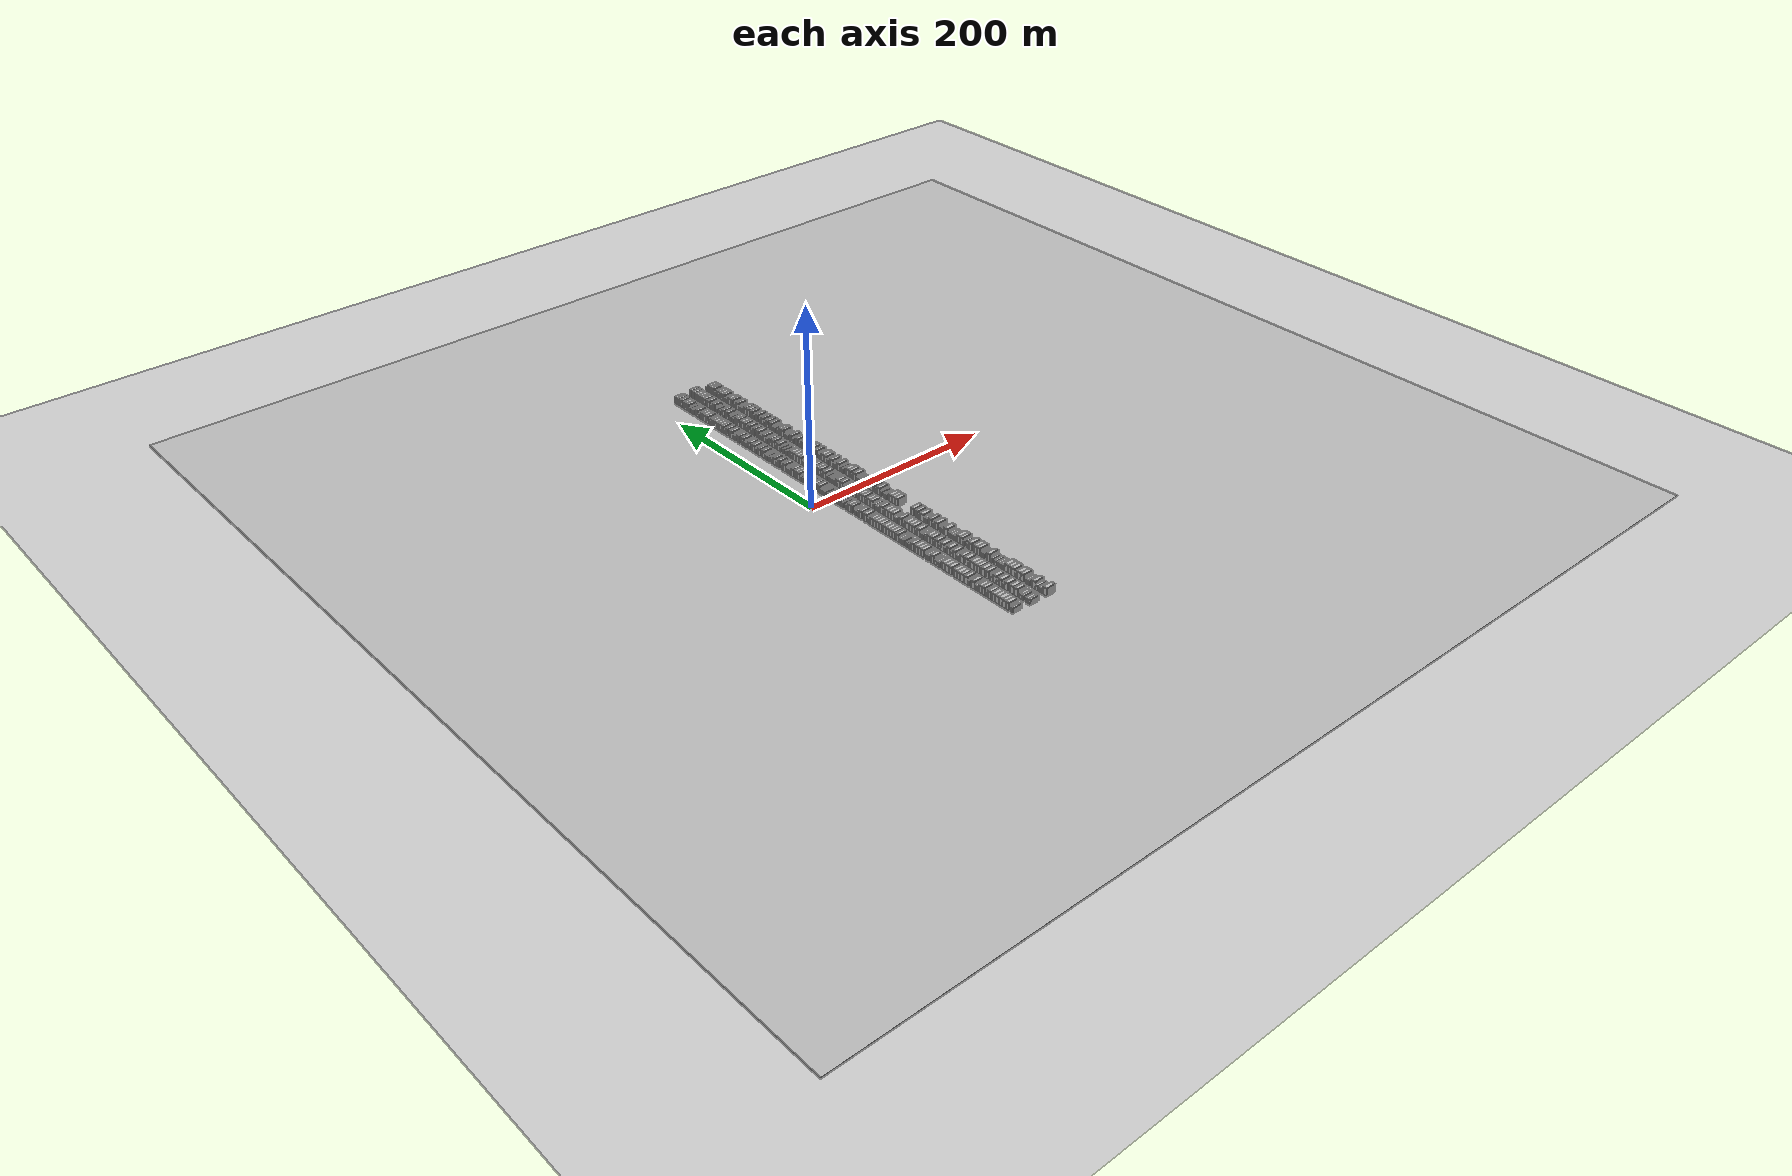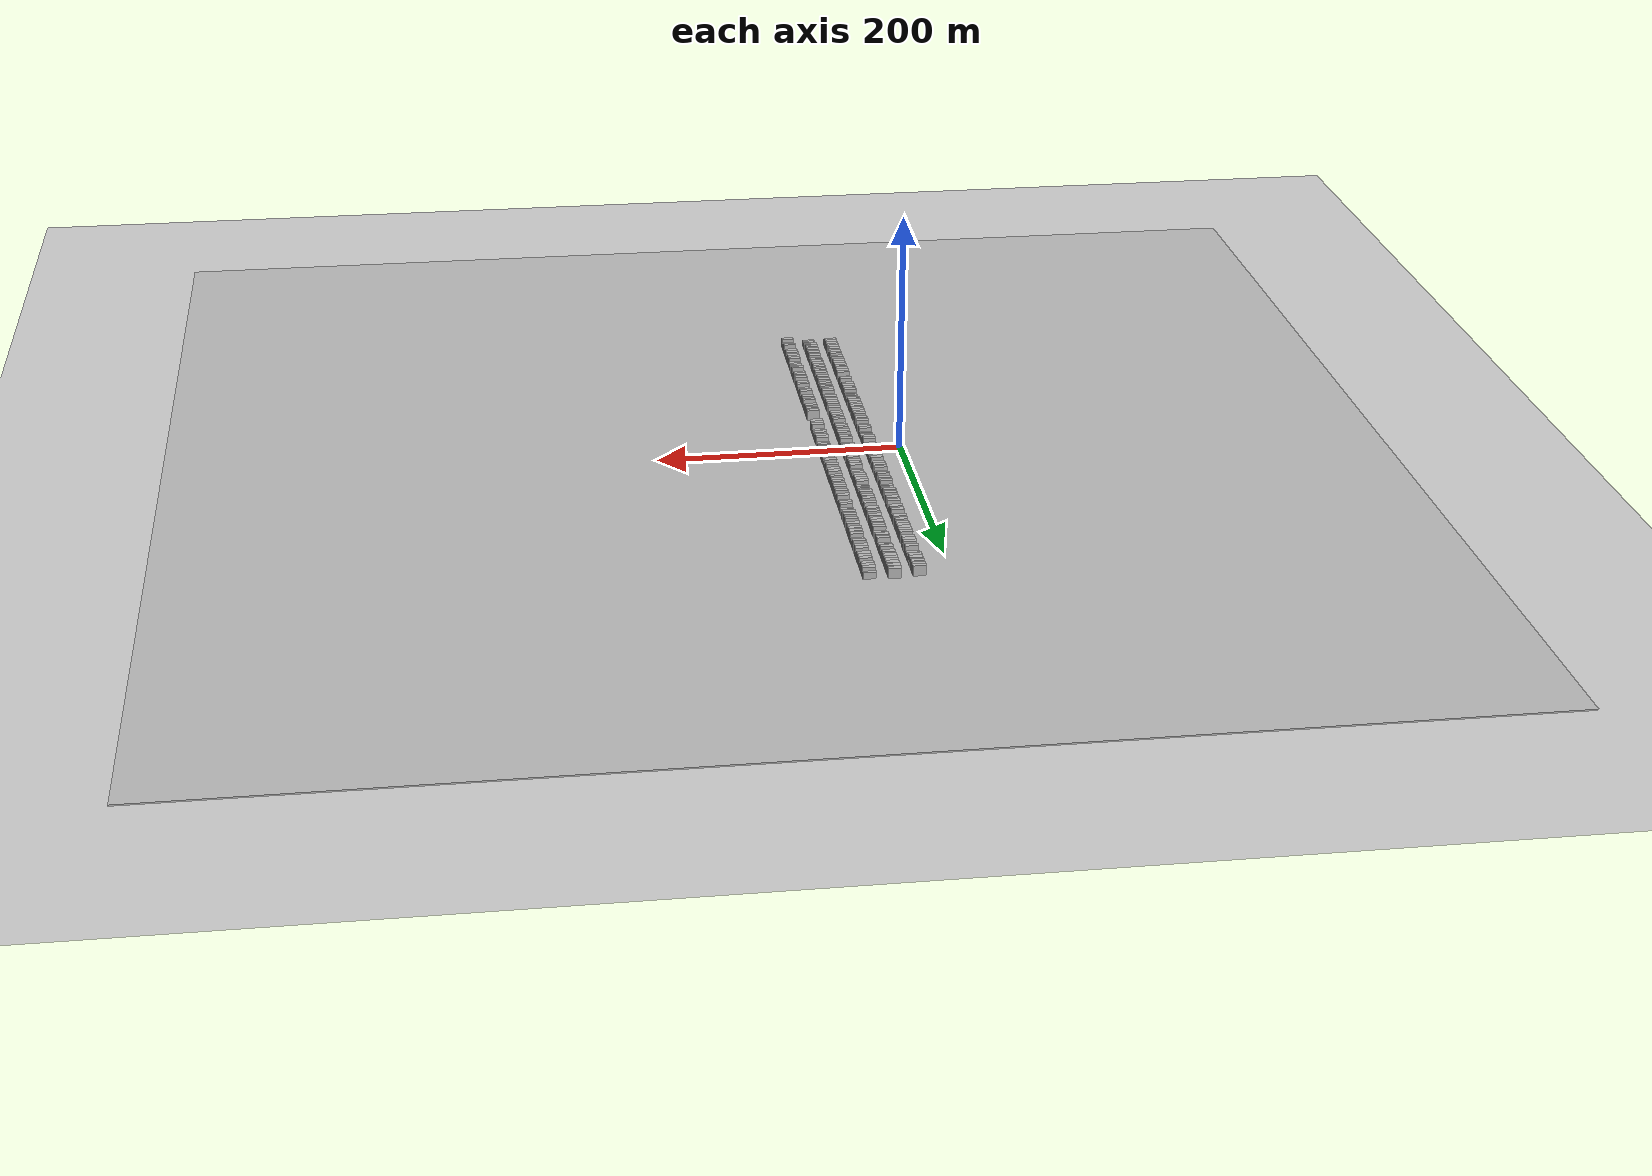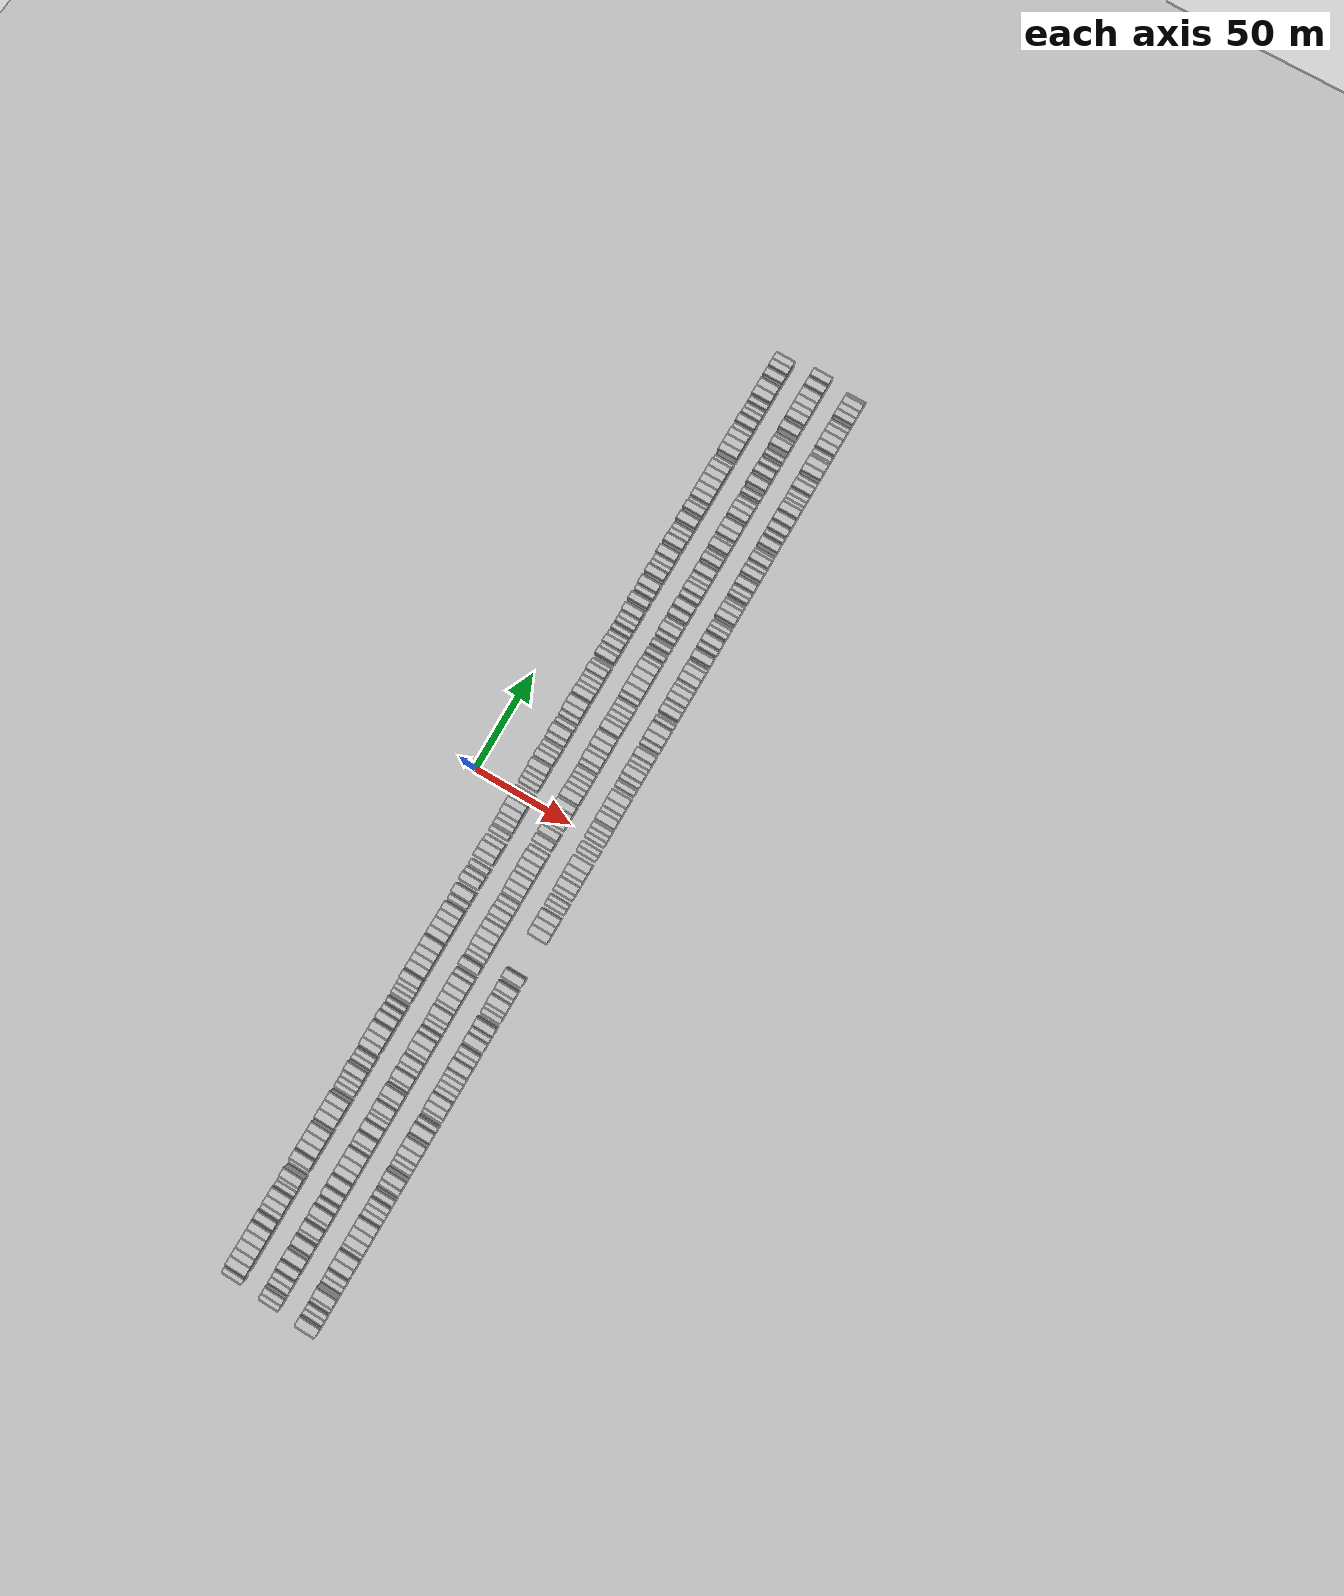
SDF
<?xml version="1.0" encoding="utf-8"?>

<sdf version="1.6">

   <world name="default">

      <gui fullscreen="0">

         <camera name="user_camera">

            <pose>-15 0 4.57585 0 0 0</pose>

            <view_controller>orbit</view_controller>

         </camera>

      </gui>

      <scene>

         <sky>

           <clouds>

             <speed>12</speed>

           </clouds>

         </sky>

         <ambient>0.4 0.4 0.4 1</ambient>

         <background>0.7 0.7 0.7 1</background>

         <shadows>1</shadows>

      </scene>

      <gravity>0 0 -9.8066</gravity>

      <magnetic_field>6e-06 2.3e-05 -4.2e-05</magnetic_field>

      <physics default="0" name="default_physics" type="ode">

         <ode>

            <solver>

               <type>quick</type>

               <iters>10</iters>

               <sor>1.0</sor>

               <use_dynamic_moi_rescaling>0</use_dynamic_moi_rescaling>

            </solver>

            <constraints>

               <cfm>0</cfm>

               <erp>0.2</erp>

               <contact_max_correcting_vel>100</contact_max_correcting_vel>

               <contact_surface_layer>0.001</contact_surface_layer>

            </constraints>

         </ode>

         <max_step_size>0.004</max_step_size>

         <real_time_factor>1</real_time_factor>

         <real_time_update_rate>250</real_time_update_rate>

      </physics>

      <light name="sun" type="directional">

         <cast_shadows>1</cast_shadows>

         <pose>0 0 10 0 0 0</pose>

         <diffuse>0.8 0.8 0.8 1</diffuse>

         <specular>0.2 0.2 0.2 1</specular>

         <attenuation>

            <range>1000</range>

            <constant>0.9</constant>

            <linear>0.01</linear>

            <quadratic>0.001</quadratic>

         </attenuation>

         <direction>-0.5 0.1 -0.9</direction>

      </light>

      <include>

         <name>ground_plane_1</name>

         <uri>model://HANNAS_ground_plane</uri>

         <pose>0 0 0  0 0 0</pose>

      </include>

      <include>

         <name>ground_plane_2</name>

         <uri>model://HANNAS_ground_plane</uri>

         <pose>100 0 0  0 0 0</pose>

      </include>

      <model name="building_1">

         <static>1</static>

         <pose frame="">25.0000 -233.7498 0 0.000000 0.000000 0.000000</pose>

         <link name="link">

            <pose frame="">0 0 3.00 0 0 0</pose>

            <collision name="collision">

               <geometry>

                  <box>

                     <size>10.0000 2.5003 6.0000</size>

                  </box>

               </geometry>

               <max_contacts>10</max_contacts>

               <surface>

                  <contact>

                     <ode/>

                  </contact>

                  <bounce/>

                  <friction>

                     <torsional>

                        <ode/>

                     </torsional>

                     <ode/>

                  </friction>

               </surface>

            </collision>

            <visual name="visual">

               <cast_shadows>0</cast_shadows>

               <geometry>

                  <box>

                     <size>10.0000 2.5003 6.0000</size>

                  </box>

               </geometry>

               <material>

                  <script>

                     <uri>model://HANNAS_wall/materials/scripts</uri>

                     <uri>model://HANNAS_wall/materials/textures</uri>

                     <name>vrc/HANNAS_wall</name>

                  </script>

               </material>

            </visual>

            <self_collide>0</self_collide>

            <enable_wind>0</enable_wind>

            <kinematic>0</kinematic>

         </link>

      </model>

      <model name="building_2">

         <static>1</static>

         <pose frame="">25.0000 -228.3924 0 0.000000 0.000000 0.000000</pose>

         <link name="link">

            <pose frame="">0 0 4.50 0 0 0</pose>

            <collision name="collision">

               <geometry>

                  <box>

                     <size>10.0000 4.2145 9.0000</size>

                  </box>

               </geometry>

               <max_contacts>10</max_contacts>

               <surface>

                  <contact>

                     <ode/>

                  </contact>

                  <bounce/>

                  <friction>

                     <torsional>

                        <ode/>

                     </torsional>

                     <ode/>

                  </friction>

               </surface>

            </collision>

            <visual name="visual">

               <cast_shadows>0</cast_shadows>

               <geometry>

                  <box>

                     <size>10.0000 4.2145 9.0000</size>

                  </box>

               </geometry>

               <material>

                  <script>

                     <uri>model://HANNAS_wall/materials/scripts</uri>

                     <uri>model://HANNAS_wall/materials/textures</uri>

                     <name>vrc/HANNAS_wall</name>

                  </script>

               </material>

            </visual>

            <self_collide>0</self_collide>

            <enable_wind>0</enable_wind>

            <kinematic>0</kinematic>

         </link>

      </model>

      <model name="building_3">

         <static>1</static>

         <pose frame="">25.0000 -224.3959 0 0.000000 0.000000 0.000000</pose>

         <link name="link">

            <pose frame="">0 0 4.50 0 0 0</pose>

            <collision name="collision">

               <geometry>

                  <box>

                     <size>10.0000 3.7786 9.0000</size>

                  </box>

               </geometry>

               <max_contacts>10</max_contacts>

               <surface>

                  <contact>

                     <ode/>

                  </contact>

                  <bounce/>

                  <friction>

                     <torsional>

                        <ode/>

                     </torsional>

                     <ode/>

                  </friction>

               </surface>

            </collision>

            <visual name="visual">

               <cast_shadows>0</cast_shadows>

               <geometry>

                  <box>

                     <size>10.0000 3.7786 9.0000</size>

                  </box>

               </geometry>

               <material>

                  <script>

                     <uri>model://HANNAS_wall/materials/scripts</uri>

                     <uri>model://HANNAS_wall/materials/textures</uri>

                     <name>vrc/HANNAS_wall</name>

                  </script>

               </material>

            </visual>

            <self_collide>0</self_collide>

            <enable_wind>0</enable_wind>

            <kinematic>0</kinematic>

         </link>

      </model>

      <model name="building_4">

         <static>1</static>

         <pose frame="">25.0000 -220.3137 0 0.000000 0.000000 0.000000</pose>

         <link name="link">

            <pose frame="">0 0 4.50 0 0 0</pose>

            <collision name="collision">

               <geometry>

                  <box>

                     <size>10.0000 4.3858 9.0000</size>

                  </box>

               </geometry>

               <max_contacts>10</max_contacts>

               <surface>

                  <contact>

                     <ode/>

                  </contact>

                  <bounce/>

                  <friction>

                     <torsional>

                        <ode/>

                     </torsional>

                     <ode/>

                  </friction>

               </surface>

            </collision>

            <visual name="visual">

               <cast_shadows>0</cast_shadows>

               <geometry>

                  <box>

                     <size>10.0000 4.3858 9.0000</size>

                  </box>

               </geometry>

               <material>

                  <script>

                     <uri>model://HANNAS_wall/materials/scripts</uri>

                     <uri>model://HANNAS_wall/materials/textures</uri>

                     <name>vrc/HANNAS_wall</name>

                  </script>

               </material>

            </visual>

            <self_collide>0</self_collide>

            <enable_wind>0</enable_wind>

            <kinematic>0</kinematic>

         </link>

      </model>

      <model name="building_5">

         <static>1</static>

         <pose frame="">25.0000 -216.0926 0 0.000000 0.000000 0.000000</pose>

         <link name="link">

            <pose frame="">0 0 4.50 0 0 0</pose>

            <collision name="collision">

               <geometry>

                  <box>

                     <size>10.0000 4.0564 9.0000</size>

                  </box>

               </geometry>

               <max_contacts>10</max_contacts>

               <surface>

                  <contact>

                     <ode/>

                  </contact>

                  <bounce/>

                  <friction>

                     <torsional>

                        <ode/>

                     </torsional>

                     <ode/>

                  </friction>

               </surface>

            </collision>

            <visual name="visual">

               <cast_shadows>0</cast_shadows>

               <geometry>

                  <box>

                     <size>10.0000 4.0564 9.0000</size>

                  </box>

               </geometry>

               <material>

                  <script>

                     <uri>model://HANNAS_wall/materials/scripts</uri>

                     <uri>model://HANNAS_wall/materials/textures</uri>

                     <name>vrc/HANNAS_wall</name>

                  </script>

               </material>

            </visual>

            <self_collide>0</self_collide>

            <enable_wind>0</enable_wind>

            <kinematic>0</kinematic>

         </link>

      </model>

      <model name="building_6">

         <static>1</static>

         <pose frame="">25.0000 -212.1384 0 0.000000 0.000000 0.000000</pose>

         <link name="link">

            <pose frame="">0 0 4.50 0 0 0</pose>

            <collision name="collision">

               <geometry>

                  <box>

                     <size>10.0000 3.8520 9.0000</size>

                  </box>

               </geometry>

               <max_contacts>10</max_contacts>

               <surface>

                  <contact>

                     <ode/>

                  </contact>

                  <bounce/>

                  <friction>

                     <torsional>

                        <ode/>

                     </torsional>

                     <ode/>

                  </friction>

               </surface>

            </collision>

            <visual name="visual">

               <cast_shadows>0</cast_shadows>

               <geometry>

                  <box>

                     <size>10.0000 3.8520 9.0000</size>

                  </box>

               </geometry>

               <material>

                  <script>

                     <uri>model://HANNAS_wall/materials/scripts</uri>

                     <uri>model://HANNAS_wall/materials/textures</uri>

                     <name>vrc/HANNAS_wall</name>

                  </script>

               </material>

            </visual>

            <self_collide>0</self_collide>

            <enable_wind>0</enable_wind>

            <kinematic>0</kinematic>

         </link>

      </model>

      <model name="building_7">

         <static>1</static>

         <pose frame="">25.0000 -207.3622 0 0.000000 0.000000 0.000000</pose>

         <link name="link">

            <pose frame="">0 0 4.50 0 0 0</pose>

            <collision name="collision">

               <geometry>

                  <box>

                     <size>10.0000 3.7003 9.0000</size>

                  </box>

               </geometry>

               <max_contacts>10</max_contacts>

               <surface>

                  <contact>

                     <ode/>

                  </contact>

                  <bounce/>

                  <friction>

                     <torsional>

                        <ode/>

                     </torsional>

                     <ode/>

                  </friction>

               </surface>

            </collision>

            <visual name="visual">

               <cast_shadows>0</cast_shadows>

               <geometry>

                  <box>

                     <size>10.0000 3.7003 9.0000</size>

                  </box>

               </geometry>

               <material>

                  <script>

                     <uri>model://HANNAS_wall/materials/scripts</uri>

                     <uri>model://HANNAS_wall/materials/textures</uri>

                     <name>vrc/HANNAS_wall</name>

                  </script>

               </material>

            </visual>

            <self_collide>0</self_collide>

            <enable_wind>0</enable_wind>

            <kinematic>0</kinematic>

         </link>

      </model>

      <model name="building_8">

         <static>1</static>

         <pose frame="">25.0000 -204.2647 0 0.000000 0.000000 0.000000</pose>

         <link name="link">

            <pose frame="">0 0 3.00 0 0 0</pose>

            <collision name="collision">

               <geometry>

                  <box>

                     <size>10.0000 2.4949 6.0000</size>

                  </box>

               </geometry>

               <max_contacts>10</max_contacts>

               <surface>

                  <contact>

                     <ode/>

                  </contact>

                  <bounce/>

                  <friction>

                     <torsional>

                        <ode/>

                     </torsional>

                     <ode/>

                  </friction>

               </surface>

            </collision>

            <visual name="visual">

               <cast_shadows>0</cast_shadows>

               <geometry>

                  <box>

                     <size>10.0000 2.4949 6.0000</size>

                  </box>

               </geometry>

               <material>

                  <script>

                     <uri>model://HANNAS_wall/materials/scripts</uri>

                     <uri>model://HANNAS_wall/materials/textures</uri>

                     <name>vrc/HANNAS_wall</name>

                  </script>

               </material>

            </visual>

            <self_collide>0</self_collide>

            <enable_wind>0</enable_wind>

            <kinematic>0</kinematic>

         </link>

      </model>

      <model name="building_9">

         <static>1</static>

         <pose frame="">25.0000 -200.0930 0 0.000000 0.000000 0.000000</pose>

         <link name="link">

            <pose frame="">0 0 4.50 0 0 0</pose>

            <collision name="collision">

               <geometry>

                  <box>

                     <size>10.0000 3.8484 9.0000</size>

                  </box>

               </geometry>

               <max_contacts>10</max_contacts>

               <surface>

                  <contact>

                     <ode/>

                  </contact>

                  <bounce/>

                  <friction>

                     <torsional>

                        <ode/>

                     </torsional>

                     <ode/>

                  </friction>

               </surface>

            </collision>

            <visual name="visual">

               <cast_shadows>0</cast_shadows>

               <geometry>

                  <box>

                     <size>10.0000 3.8484 9.0000</size>

                  </box>

               </geometry>

               <material>

                  <script>

                     <uri>model://HANNAS_wall/materials/scripts</uri>

                     <uri>model://HANNAS_wall/materials/textures</uri>

                     <name>vrc/HANNAS_wall</name>

                  </script>

               </material>

            </visual>

            <self_collide>0</self_collide>

            <enable_wind>0</enable_wind>

            <kinematic>0</kinematic>

         </link>

      </model>

      <model name="building_10">

         <static>1</static>

         <pose frame="">25.0000 -196.2790 0 0.000000 0.000000 0.000000</pose>

         <link name="link">

            <pose frame="">0 0 4.50 0 0 0</pose>

            <collision name="collision">

               <geometry>

                  <box>

                     <size>10.0000 3.7796 9.0000</size>

                  </box>

               </geometry>

               <max_contacts>10</max_contacts>

               <surface>

                  <contact>

                     <ode/>

                  </contact>

                  <bounce/>

                  <friction>

                     <torsional>

                        <ode/>

                     </torsional>

                     <ode/>

                  </friction>

               </surface>

            </collision>

            <visual name="visual">

               <cast_shadows>0</cast_shadows>

               <geometry>

                  <box>

                     <size>10.0000 3.7796 9.0000</size>

                  </box>

               </geometry>

               <material>

                  <script>

                     <uri>model://HANNAS_wall/materials/scripts</uri>

                     <uri>model://HANNAS_wall/materials/textures</uri>

                     <name>vrc/HANNAS_wall</name>

                  </script>

               </material>

            </visual>

            <self_collide>0</self_collide>

            <enable_wind>0</enable_wind>

            <kinematic>0</kinematic>

         </link>

      </model>

      <model name="building_11">

         <static>1</static>

         <pose frame="">25.0000 -193.1830 0 0.000000 0.000000 0.000000</pose>

         <link name="link">

            <pose frame="">0 0 3.00 0 0 0</pose>

            <collision name="collision">

               <geometry>

                  <box>

                     <size>10.0000 2.4123 6.0000</size>

                  </box>

               </geometry>

               <max_contacts>10</max_contacts>

               <surface>

                  <contact>

                     <ode/>

                  </contact>

                  <bounce/>

                  <friction>

                     <torsional>

                        <ode/>

                     </torsional>

                     <ode/>

                  </friction>

               </surface>

            </collision>

            <visual name="visual">

               <cast_shadows>0</cast_shadows>

               <geometry>

                  <box>

                     <size>10.0000 2.4123 6.0000</size>

                  </box>

               </geometry>

               <material>

                  <script>

                     <uri>model://HANNAS_wall/materials/scripts</uri>

                     <uri>model://HANNAS_wall/materials/textures</uri>

                     <name>vrc/HANNAS_wall</name>

                  </script>

               </material>

            </visual>

            <self_collide>0</self_collide>

            <enable_wind>0</enable_wind>

            <kinematic>0</kinematic>

         </link>

      </model>

      <model name="building_12">

         <static>1</static>

         <pose frame="">25.0000 -190.6656 0 0.000000 0.000000 0.000000</pose>

         <link name="link">

            <pose frame="">0 0 3.00 0 0 0</pose>

            <collision name="collision">

               <geometry>

                  <box>

                     <size>10.0000 2.6224 6.0000</size>

                  </box>

               </geometry>

               <max_contacts>10</max_contacts>

               <surface>

                  <contact>

                     <ode/>

                  </contact>

                  <bounce/>

                  <friction>

                     <torsional>

                        <ode/>

                     </torsional>

                     <ode/>

                  </friction>

               </surface>

            </collision>

            <visual name="visual">

               <cast_shadows>0</cast_shadows>

               <geometry>

                  <box>

                     <size>10.0000 2.6224 6.0000</size>

                  </box>

               </geometry>

               <material>

                  <script>

                     <uri>model://HANNAS_wall/materials/scripts</uri>

                     <uri>model://HANNAS_wall/materials/textures</uri>

                     <name>vrc/HANNAS_wall</name>

                  </script>

               </material>

            </visual>

            <self_collide>0</self_collide>

            <enable_wind>0</enable_wind>

            <kinematic>0</kinematic>

         </link>

      </model>

      <model name="building_13">

         <static>1</static>

         <pose frame="">25.0000 -187.4078 0 0.000000 0.000000 0.000000</pose>

         <link name="link">

            <pose frame="">0 0 4.50 0 0 0</pose>

            <collision name="collision">

               <geometry>

                  <box>

                     <size>10.0000 3.8932 9.0000</size>

                  </box>

               </geometry>

               <max_contacts>10</max_contacts>

               <surface>

                  <contact>

                     <ode/>

                  </contact>

                  <bounce/>

                  <friction>

                     <torsional>

                        <ode/>

                     </torsional>

                     <ode/>

                  </friction>

               </surface>

            </collision>

            <visual name="visual">

               <cast_shadows>0</cast_shadows>

               <geometry>

                  <box>

                     <size>10.0000 3.8932 9.0000</size>

                  </box>

               </geometry>

               <material>

                  <script>

                     <uri>model://HANNAS_wall/materials/scripts</uri>

                     <uri>model://HANNAS_wall/materials/textures</uri>

                     <name>vrc/HANNAS_wall</name>

                  </script>

               </material>

            </visual>

            <self_collide>0</self_collide>

            <enable_wind>0</enable_wind>

            <kinematic>0</kinematic>

         </link>

      </model>

      <model name="building_14">

         <static>1</static>

         <pose frame="">25.0000 -182.2265 0 0.000000 0.000000 0.000000</pose>

         <link name="link">

            <pose frame="">0 0 3.00 0 0 0</pose>

            <collision name="collision">

               <geometry>

                  <box>

                     <size>10.0000 2.4693 6.0000</size>

                  </box>

               </geometry>

               <max_contacts>10</max_contacts>

               <surface>

                  <contact>

                     <ode/>

                  </contact>

                  <bounce/>

                  <friction>

                     <torsional>

                        <ode/>

                     </torsional>

                     <ode/>

                  </friction>

               </surface>

            </collision>

            <visual name="visual">

               <cast_shadows>0</cast_shadows>

               <geometry>

                  <box>

                     <size>10.0000 2.4693 6.0000</size>

                  </box>

               </geometry>

               <material>

                  <script>

                     <uri>model://HANNAS_wall/materials/scripts</uri>

                     <uri>model://HANNAS_wall/materials/textures</uri>

                     <name>vrc/HANNAS_wall</name>

                  </script>

               </material>

            </visual>

            <self_collide>0</self_collide>

            <enable_wind>0</enable_wind>

            <kinematic>0</kinematic>

         </link>

      </model>

      <model name="building_15">

         <static>1</static>

         <pose frame="">25.0000 -178.8925 0 0.000000 0.000000 0.000000</pose>

         <link name="link">

            <pose frame="">0 0 4.50 0 0 0</pose>

            <collision name="collision">

               <geometry>

                  <box>

                     <size>10.0000 4.1987 9.0000</size>

                  </box>

               </geometry>

               <max_contacts>10</max_contacts>

               <surface>

                  <contact>

                     <ode/>

                  </contact>

                  <bounce/>

                  <friction>

                     <torsional>

                        <ode/>

                     </torsional>

                     <ode/>

                  </friction>

               </surface>

            </collision>

            <visual name="visual">

               <cast_shadows>0</cast_shadows>

               <geometry>

                  <box>

                     <size>10.0000 4.1987 9.0000</size>

                  </box>

               </geometry>

               <material>

                  <script>

                     <uri>model://HANNAS_wall/materials/scripts</uri>

                     <uri>model://HANNAS_wall/materials/textures</uri>

                     <name>vrc/HANNAS_wall</name>

                  </script>

               </material>

            </visual>

            <self_collide>0</self_collide>

            <enable_wind>0</enable_wind>

            <kinematic>0</kinematic>

         </link>

      </model>

      <model name="building_16">

         <static>1</static>

         <pose frame="">25.0000 -173.7933 0 0.000000 0.000000 0.000000</pose>

         <link name="link">

            <pose frame="">0 0 4.50 0 0 0</pose>

            <collision name="collision">

               <geometry>

                  <box>

                     <size>10.0000 3.9998 9.0000</size>

                  </box>

               </geometry>

               <max_contacts>10</max_contacts>

               <surface>

                  <contact>

                     <ode/>

                  </contact>

                  <bounce/>

                  <friction>

                     <torsional>

                        <ode/>

                     </torsional>

                     <ode/>

                  </friction>

               </surface>

            </collision>

            <visual name="visual">

               <cast_shadows>0</cast_shadows>

               <geometry>

                  <box>

                     <size>10.0000 3.9998 9.0000</size>

                  </box>

               </geometry>

               <material>

                  <script>

                     <uri>model://HANNAS_wall/materials/scripts</uri>

                     <uri>model://HANNAS_wall/materials/textures</uri>

                     <name>vrc/HANNAS_wall</name>

                  </script>

               </material>

            </visual>

            <self_collide>0</self_collide>

            <enable_wind>0</enable_wind>

            <kinematic>0</kinematic>

         </link>

      </model>

      <model name="building_17">

         <static>1</static>

         <pose frame="">25.0000 -169.7118 0 0.000000 0.000000 0.000000</pose>

         <link name="link">

            <pose frame="">0 0 4.50 0 0 0</pose>

            <collision name="collision">

               <geometry>

                  <box>

                     <size>10.0000 4.1631 9.0000</size>

                  </box>

               </geometry>

               <max_contacts>10</max_contacts>

               <surface>

                  <contact>

                     <ode/>

                  </contact>

                  <bounce/>

                  <friction>

                     <torsional>

                        <ode/>

                     </torsional>

                     <ode/>

                  </friction>

               </surface>

            </collision>

            <visual name="visual">

               <cast_shadows>0</cast_shadows>

               <geometry>

                  <box>

                     <size>10.0000 4.1631 9.0000</size>

                  </box>

               </geometry>

               <material>

                  <script>

                     <uri>model://HANNAS_wall/materials/scripts</uri>

                     <uri>model://HANNAS_wall/materials/textures</uri>

                     <name>vrc/HANNAS_wall</name>

                  </script>

               </material>

            </visual>

            <self_collide>0</self_collide>

            <enable_wind>0</enable_wind>

            <kinematic>0</kinematic>

         </link>

      </model>

      <model name="building_18">

         <static>1</static>

         <pose frame="">25.0000 -165.6820 0 0.000000 0.000000 0.000000</pose>

         <link name="link">

            <pose frame="">0 0 4.50 0 0 0</pose>

            <collision name="collision">

               <geometry>

                  <box>

                     <size>10.0000 3.8965 9.0000</size>

                  </box>

               </geometry>

               <max_contacts>10</max_contacts>

               <surface>

                  <contact>

                     <ode/>

                  </contact>

                  <bounce/>

                  <friction>

                     <torsional>

                        <ode/>

                     </torsional>

                     <ode/>

                  </friction>

               </surface>

            </collision>

            <visual name="visual">

               <cast_shadows>0</cast_shadows>

               <geometry>

                  <box>

                     <size>10.0000 3.8965 9.0000</size>

                  </box>

               </geometry>

               <material>

                  <script>

                     <uri>model://HANNAS_wall/materials/scripts</uri>

                     <uri>model://HANNAS_wall/materials/textures</uri>

                     <name>vrc/HANNAS_wall</name>

                  </script>

               </material>

            </visual>

            <self_collide>0</self_collide>

            <enable_wind>0</enable_wind>

            <kinematic>0</kinematic>

         </link>

      </model>

      <model name="building_19">

         <static>1</static>

         <pose frame="">25.0000 -159.5508 0 0.000000 0.000000 0.000000</pose>

         <link name="link">

            <pose frame="">0 0 4.50 0 0 0</pose>

            <collision name="collision">

               <geometry>

                  <box>

                     <size>10.0000 4.3658 9.0000</size>

                  </box>

               </geometry>

               <max_contacts>10</max_contacts>

               <surface>

                  <contact>

                     <ode/>

                  </contact>

                  <bounce/>

                  <friction>

                     <torsional>

                        <ode/>

                     </torsional>

                     <ode/>

                  </friction>

               </surface>

            </collision>

            <visual name="visual">

               <cast_shadows>0</cast_shadows>

               <geometry>

                  <box>

                     <size>10.0000 4.3658 9.0000</size>

                  </box>

               </geometry>

               <material>

                  <script>

                     <uri>model://HANNAS_wall/materials/scripts</uri>

                     <uri>model://HANNAS_wall/materials/textures</uri>

                     <name>vrc/HANNAS_wall</name>

                  </script>

               </material>

            </visual>

            <self_collide>0</self_collide>

            <enable_wind>0</enable_wind>

            <kinematic>0</kinematic>

         </link>

      </model>

      <model name="building_20">

         <static>1</static>

         <pose frame="">25.0000 -155.2540 0 0.000000 0.000000 0.000000</pose>

         <link name="link">

            <pose frame="">0 0 4.50 0 0 0</pose>

            <collision name="collision">

               <geometry>

                  <box>

                     <size>10.0000 4.2279 9.0000</size>

                  </box>

               </geometry>

               <max_contacts>10</max_contacts>

               <surface>

                  <contact>

                     <ode/>

                  </contact>

                  <bounce/>

                  <friction>

                     <torsional>

                        <ode/>

                     </torsional>

                     <ode/>

                  </friction>

               </surface>

            </collision>

            <visual name="visual">

               <cast_shadows>0</cast_shadows>

               <geometry>

                  <box>

                     <size>10.0000 4.2279 9.0000</size>

                  </box>

               </geometry>

               <material>

                  <script>

                     <uri>model://HANNAS_wall/materials/scripts</uri>

                     <uri>model://HANNAS_wall/materials/textures</uri>

                     <name>vrc/HANNAS_wall</name>

                  </script>

               </material>

            </visual>

            <self_collide>0</self_collide>

            <enable_wind>0</enable_wind>

            <kinematic>0</kinematic>

         </link>

      </model>

      <model name="building_21">

         <static>1</static>

         <pose frame="">25.0000 -151.2550 0 0.000000 0.000000 0.000000</pose>

         <link name="link">

            <pose frame="">0 0 4.50 0 0 0</pose>

            <collision name="collision">

               <geometry>

                  <box>

                     <size>10.0000 3.7702 9.0000</size>

                  </box>

               </geometry>

               <max_contacts>10</max_contacts>

               <surface>

                  <contact>

                     <ode/>

                  </contact>

                  <bounce/>

                  <friction>

                     <torsional>

                        <ode/>

                     </torsional>

                     <ode/>

                  </friction>

               </surface>

            </collision>

            <visual name="visual">

               <cast_shadows>0</cast_shadows>

               <geometry>

                  <box>

                     <size>10.0000 3.7702 9.0000</size>

                  </box>

               </geometry>

               <material>

                  <script>

                     <uri>model://HANNAS_wall/materials/scripts</uri>

                     <uri>model://HANNAS_wall/materials/textures</uri>

                     <name>vrc/HANNAS_wall</name>

                  </script>

               </material>

            </visual>

            <self_collide>0</self_collide>

            <enable_wind>0</enable_wind>

            <kinematic>0</kinematic>

         </link>

      </model>

      <model name="building_22">

         <static>1</static>

         <pose frame="">25.0000 -146.1154 0 0.000000 0.000000 0.000000</pose>

         <link name="link">

            <pose frame="">0 0 3.00 0 0 0</pose>

            <collision name="collision">

               <geometry>

                  <box>

                     <size>10.0000 2.5090 6.0000</size>

                  </box>

               </geometry>

               <max_contacts>10</max_contacts>

               <surface>

                  <contact>

                     <ode/>

                  </contact>

                  <bounce/>

                  <friction>

                     <torsional>

                        <ode/>

                     </torsional>

                     <ode/>

                  </friction>

               </surface>

            </collision>

            <visual name="visual">

               <cast_shadows>0</cast_shadows>

               <geometry>

                  <box>

                     <size>10.0000 2.5090 6.0000</size>

                  </box>

               </geometry>

               <material>

                  <script>

                     <uri>model://HANNAS_wall/materials/scripts</uri>

                     <uri>model://HANNAS_wall/materials/textures</uri>

                     <name>vrc/HANNAS_wall</name>

                  </script>

               </material>

            </visual>

            <self_collide>0</self_collide>

            <enable_wind>0</enable_wind>

            <kinematic>0</kinematic>

         </link>

      </model>

      <model name="building_23">

         <static>1</static>

         <pose frame="">25.0000 -143.5626 0 0.000000 0.000000 0.000000</pose>

         <link name="link">

            <pose frame="">0 0 3.00 0 0 0</pose>

            <collision name="collision">

               <geometry>

                  <box>

                     <size>10.0000 2.5967 6.0000</size>

                  </box>

               </geometry>

               <max_contacts>10</max_contacts>

               <surface>

                  <contact>

                     <ode/>

                  </contact>

                  <bounce/>

                  <friction>

                     <torsional>

                        <ode/>

                     </torsional>

                     <ode/>

                  </friction>

               </surface>

            </collision>

            <visual name="visual">

               <cast_shadows>0</cast_shadows>

               <geometry>

                  <box>

                     <size>10.0000 2.5967 6.0000</size>

                  </box>

               </geometry>

               <material>

                  <script>

                     <uri>model://HANNAS_wall/materials/scripts</uri>

                     <uri>model://HANNAS_wall/materials/textures</uri>

                     <name>vrc/HANNAS_wall</name>

                  </script>

               </material>

            </visual>

            <self_collide>0</self_collide>

            <enable_wind>0</enable_wind>

            <kinematic>0</kinematic>

         </link>

      </model>

      <model name="building_24">

         <static>1</static>

         <pose frame="">25.0000 -140.9930 0 0.000000 0.000000 0.000000</pose>

         <link name="link">

            <pose frame="">0 0 3.00 0 0 0</pose>

            <collision name="collision">

               <geometry>

                  <box>

                     <size>10.0000 2.5427 6.0000</size>

                  </box>

               </geometry>

               <max_contacts>10</max_contacts>

               <surface>

                  <contact>

                     <ode/>

                  </contact>

                  <bounce/>

                  <friction>

                     <torsional>

                        <ode/>

                     </torsional>

                     <ode/>

                  </friction>

               </surface>

            </collision>

            <visual name="visual">

               <cast_shadows>0</cast_shadows>

               <geometry>

                  <box>

                     <size>10.0000 2.5427 6.0000</size>

                  </box>

               </geometry>

               <material>

                  <script>

                     <uri>model://HANNAS_wall/materials/scripts</uri>

                     <uri>model://HANNAS_wall/materials/textures</uri>

                     <name>vrc/HANNAS_wall</name>

                  </script>

               </material>

            </visual>

            <self_collide>0</self_collide>

            <enable_wind>0</enable_wind>

            <kinematic>0</kinematic>

         </link>

      </model>

      <model name="building_25">

         <static>1</static>

         <pose frame="">25.0000 -136.8205 0 0.000000 0.000000 0.000000</pose>

         <link name="link">

            <pose frame="">0 0 4.50 0 0 0</pose>

            <collision name="collision">

               <geometry>

                  <box>

                     <size>10.0000 3.8022 9.0000</size>

                  </box>

               </geometry>

               <max_contacts>10</max_contacts>

               <surface>

                  <contact>

                     <ode/>

                  </contact>

                  <bounce/>

                  <friction>

                     <torsional>

                        <ode/>

                     </torsional>

                     <ode/>

                  </friction>

               </surface>

            </collision>

            <visual name="visual">

               <cast_shadows>0</cast_shadows>

               <geometry>

                  <box>

                     <size>10.0000 3.8022 9.0000</size>

                  </box>

               </geometry>

               <material>

                  <script>

                     <uri>model://HANNAS_wall/materials/scripts</uri>

                     <uri>model://HANNAS_wall/materials/textures</uri>

                     <name>vrc/HANNAS_wall</name>

                  </script>

               </material>

            </visual>

            <self_collide>0</self_collide>

            <enable_wind>0</enable_wind>

            <kinematic>0</kinematic>

         </link>

      </model>

      <model name="building_26">

         <static>1</static>

         <pose frame="">25.0000 -132.5947 0 0.000000 0.000000 0.000000</pose>

         <link name="link">

            <pose frame="">0 0 3.00 0 0 0</pose>

            <collision name="collision">

               <geometry>

                  <box>

                     <size>10.0000 2.6496 6.0000</size>

                  </box>

               </geometry>

               <max_contacts>10</max_contacts>

               <surface>

                  <contact>

                     <ode/>

                  </contact>

                  <bounce/>

                  <friction>

                     <torsional>

                        <ode/>

                     </torsional>

                     <ode/>

                  </friction>

               </surface>

            </collision>

            <visual name="visual">

               <cast_shadows>0</cast_shadows>

               <geometry>

                  <box>

                     <size>10.0000 2.6496 6.0000</size>

                  </box>

               </geometry>

               <material>

                  <script>

                     <uri>model://HANNAS_wall/materials/scripts</uri>

                     <uri>model://HANNAS_wall/materials/textures</uri>

                     <name>vrc/HANNAS_wall</name>

                  </script>

               </material>

            </visual>

            <self_collide>0</self_collide>

            <enable_wind>0</enable_wind>

            <kinematic>0</kinematic>

         </link>

      </model>

      <model name="building_27">

         <static>1</static>

         <pose frame="">25.0000 -129.9391 0 0.000000 0.000000 0.000000</pose>

         <link name="link">

            <pose frame="">0 0 3.00 0 0 0</pose>

            <collision name="collision">

               <geometry>

                  <box>

                     <size>10.0000 2.6615 6.0000</size>

                  </box>

               </geometry>

               <max_contacts>10</max_contacts>

               <surface>

                  <contact>

                     <ode/>

                  </contact>

                  <bounce/>

                  <friction>

                     <torsional>

                        <ode/>

                     </torsional>

                     <ode/>

                  </friction>

               </surface>

            </collision>

            <visual name="visual">

               <cast_shadows>0</cast_shadows>

               <geometry>

                  <box>

                     <size>10.0000 2.6615 6.0000</size>

                  </box>

               </geometry>

               <material>

                  <script>

                     <uri>model://HANNAS_wall/materials/scripts</uri>

                     <uri>model://HANNAS_wall/materials/textures</uri>

                     <name>vrc/HANNAS_wall</name>

                  </script>

               </material>

            </visual>

            <self_collide>0</self_collide>

            <enable_wind>0</enable_wind>

            <kinematic>0</kinematic>

         </link>

      </model>

      <model name="building_28">

         <static>1</static>

         <pose frame="">25.0000 -124.7796 0 0.000000 0.000000 0.000000</pose>

         <link name="link">

            <pose frame="">0 0 4.50 0 0 0</pose>

            <collision name="collision">

               <geometry>

                  <box>

                     <size>10.0000 3.6576 9.0000</size>

                  </box>

               </geometry>

               <max_contacts>10</max_contacts>

               <surface>

                  <contact>

                     <ode/>

                  </contact>

                  <bounce/>

                  <friction>

                     <torsional>

                        <ode/>

                     </torsional>

                     <ode/>

                  </friction>

               </surface>

            </collision>

            <visual name="visual">

               <cast_shadows>0</cast_shadows>

               <geometry>

                  <box>

                     <size>10.0000 3.6576 9.0000</size>

                  </box>

               </geometry>

               <material>

                  <script>

                     <uri>model://HANNAS_wall/materials/scripts</uri>

                     <uri>model://HANNAS_wall/materials/textures</uri>

                     <name>vrc/HANNAS_wall</name>

                  </script>

               </material>

            </visual>

            <self_collide>0</self_collide>

            <enable_wind>0</enable_wind>

            <kinematic>0</kinematic>

         </link>

      </model>

      <model name="building_29">

         <static>1</static>

         <pose frame="">25.0000 -120.9678 0 0.000000 0.000000 0.000000</pose>

         <link name="link">

            <pose frame="">0 0 4.50 0 0 0</pose>

            <collision name="collision">

               <geometry>

                  <box>

                     <size>10.0000 3.9659 9.0000</size>

                  </box>

               </geometry>

               <max_contacts>10</max_contacts>

               <surface>

                  <contact>

                     <ode/>

                  </contact>

                  <bounce/>

                  <friction>

                     <torsional>

                        <ode/>

                     </torsional>

                     <ode/>

                  </friction>

               </surface>

            </collision>

            <visual name="visual">

               <cast_shadows>0</cast_shadows>

               <geometry>

                  <box>

                     <size>10.0000 3.9659 9.0000</size>

                  </box>

               </geometry>

               <material>

                  <script>

                     <uri>model://HANNAS_wall/materials/scripts</uri>

                     <uri>model://HANNAS_wall/materials/textures</uri>

                     <name>vrc/HANNAS_wall</name>

                  </script>

               </material>

            </visual>

            <self_collide>0</self_collide>

            <enable_wind>0</enable_wind>

            <kinematic>0</kinematic>

         </link>

      </model>

      <model name="building_30">

         <static>1</static>

         <pose frame="">25.0000 -116.8601 0 0.000000 0.000000 0.000000</pose>

         <link name="link">

            <pose frame="">0 0 4.50 0 0 0</pose>

            <collision name="collision">

               <geometry>

                  <box>

                     <size>10.0000 4.2496 9.0000</size>

                  </box>

               </geometry>

               <max_contacts>10</max_contacts>

               <surface>

                  <contact>

                     <ode/>

                  </contact>

                  <bounce/>

                  <friction>

                     <torsional>

                        <ode/>

                     </torsional>

                     <ode/>

                  </friction>

               </surface>

            </collision>

            <visual name="visual">

               <cast_shadows>0</cast_shadows>

               <geometry>

                  <box>

                     <size>10.0000 4.2496 9.0000</size>

                  </box>

               </geometry>

               <material>

                  <script>

                     <uri>model://HANNAS_wall/materials/scripts</uri>

                     <uri>model://HANNAS_wall/materials/textures</uri>

                     <name>vrc/HANNAS_wall</name>

                  </script>

               </material>

            </visual>

            <self_collide>0</self_collide>

            <enable_wind>0</enable_wind>

            <kinematic>0</kinematic>

         </link>

      </model>

      <model name="building_31">

         <static>1</static>

         <pose frame="">25.0000 -111.7595 0 0.000000 0.000000 0.000000</pose>

         <link name="link">

            <pose frame="">0 0 4.50 0 0 0</pose>

            <collision name="collision">

               <geometry>

                  <box>

                     <size>10.0000 3.9515 9.0000</size>

                  </box>

               </geometry>

               <max_contacts>10</max_contacts>

               <surface>

                  <contact>

                     <ode/>

                  </contact>

                  <bounce/>

                  <friction>

                     <torsional>

                        <ode/>

                     </torsional>

                     <ode/>

                  </friction>

               </surface>

            </collision>

            <visual name="visual">

               <cast_shadows>0</cast_shadows>

               <geometry>

                  <box>

                     <size>10.0000 3.9515 9.0000</size>

                  </box>

               </geometry>

               <material>

                  <script>

                     <uri>model://HANNAS_wall/materials/scripts</uri>

                     <uri>model://HANNAS_wall/materials/textures</uri>

                     <name>vrc/HANNAS_wall</name>

                  </script>

               </material>

            </visual>

            <self_collide>0</self_collide>

            <enable_wind>0</enable_wind>

            <kinematic>0</kinematic>

         </link>

      </model>

      <model name="building_32">

         <static>1</static>

         <pose frame="">25.0000 -108.4175 0 0.000000 0.000000 0.000000</pose>

         <link name="link">

            <pose frame="">0 0 3.00 0 0 0</pose>

            <collision name="collision">

               <geometry>

                  <box>

                     <size>10.0000 2.7323 6.0000</size>

                  </box>

               </geometry>

               <max_contacts>10</max_contacts>

               <surface>

                  <contact>

                     <ode/>

                  </contact>

                  <bounce/>

                  <friction>

                     <torsional>

                        <ode/>

                     </torsional>

                     <ode/>

                  </friction>

               </surface>

            </collision>

            <visual name="visual">

               <cast_shadows>0</cast_shadows>

               <geometry>

                  <box>

                     <size>10.0000 2.7323 6.0000</size>

                  </box>

               </geometry>

               <material>

                  <script>

                     <uri>model://HANNAS_wall/materials/scripts</uri>

                     <uri>model://HANNAS_wall/materials/textures</uri>

                     <name>vrc/HANNAS_wall</name>

                  </script>

               </material>

            </visual>

            <self_collide>0</self_collide>

            <enable_wind>0</enable_wind>

            <kinematic>0</kinematic>

         </link>

      </model>

      <model name="building_33">

         <static>1</static>

         <pose frame="">25.0000 -104.8360 0 0.000000 0.000000 0.000000</pose>

         <link name="link">

            <pose frame="">0 0 3.00 0 0 0</pose>

            <collision name="collision">

               <geometry>

                  <box>

                     <size>10.0000 2.4307 6.0000</size>

                  </box>

               </geometry>

               <max_contacts>10</max_contacts>

               <surface>

                  <contact>

                     <ode/>

                  </contact>

                  <bounce/>

                  <friction>

                     <torsional>

                        <ode/>

                     </torsional>

                     <ode/>

                  </friction>

               </surface>

            </collision>

            <visual name="visual">

               <cast_shadows>0</cast_shadows>

               <geometry>

                  <box>

                     <size>10.0000 2.4307 6.0000</size>

                  </box>

               </geometry>

               <material>

                  <script>

                     <uri>model://HANNAS_wall/materials/scripts</uri>

                     <uri>model://HANNAS_wall/materials/textures</uri>

                     <name>vrc/HANNAS_wall</name>

                  </script>

               </material>

            </visual>

            <self_collide>0</self_collide>

            <enable_wind>0</enable_wind>

            <kinematic>0</kinematic>

         </link>

      </model>

      <model name="building_34">

         <static>1</static>

         <pose frame="">25.0000 -100.4031 0 0.000000 0.000000 0.000000</pose>

         <link name="link">

            <pose frame="">0 0 3.00 0 0 0</pose>

            <collision name="collision">

               <geometry>

                  <box>

                     <size>10.0000 2.4352 6.0000</size>

                  </box>

               </geometry>

               <max_contacts>10</max_contacts>

               <surface>

                  <contact>

                     <ode/>

                  </contact>

                  <bounce/>

                  <friction>

                     <torsional>

                        <ode/>

                     </torsional>

                     <ode/>

                  </friction>

               </surface>

            </collision>

            <visual name="visual">

               <cast_shadows>0</cast_shadows>

               <geometry>

                  <box>

                     <size>10.0000 2.4352 6.0000</size>

                  </box>

               </geometry>

               <material>

                  <script>

                     <uri>model://HANNAS_wall/materials/scripts</uri>

                     <uri>model://HANNAS_wall/materials/textures</uri>

                     <name>vrc/HANNAS_wall</name>

                  </script>

               </material>

            </visual>

            <self_collide>0</self_collide>

            <enable_wind>0</enable_wind>

            <kinematic>0</kinematic>

         </link>

      </model>

      <model name="building_35">

         <static>1</static>

         <pose frame="">25.0000 -97.9705 0 0.000000 0.000000 0.000000</pose>

         <link name="link">

            <pose frame="">0 0 3.00 0 0 0</pose>

            <collision name="collision">

               <geometry>

                  <box>

                     <size>10.0000 2.4299 6.0000</size>

                  </box>

               </geometry>

               <max_contacts>10</max_contacts>

               <surface>

                  <contact>

                     <ode/>

                  </contact>

                  <bounce/>

                  <friction>

                     <torsional>

                        <ode/>

                     </torsional>

                     <ode/>

                  </friction>

               </surface>

            </collision>

            <visual name="visual">

               <cast_shadows>0</cast_shadows>

               <geometry>

                  <box>

                     <size>10.0000 2.4299 6.0000</size>

                  </box>

               </geometry>

               <material>

                  <script>

                     <uri>model://HANNAS_wall/materials/scripts</uri>

                     <uri>model://HANNAS_wall/materials/textures</uri>

                     <name>vrc/HANNAS_wall</name>

                  </script>

               </material>

            </visual>

            <self_collide>0</self_collide>

            <enable_wind>0</enable_wind>

            <kinematic>0</kinematic>

         </link>

      </model>

      <model name="building_36">

         <static>1</static>

         <pose frame="">25.0000 -95.3908 0 0.000000 0.000000 0.000000</pose>

         <link name="link">

            <pose frame="">0 0 3.00 0 0 0</pose>

            <collision name="collision">

               <geometry>

                  <box>

                     <size>10.0000 2.7296 6.0000</size>

                  </box>

               </geometry>

               <max_contacts>10</max_contacts>

               <surface>

                  <contact>

                     <ode/>

                  </contact>

                  <bounce/>

                  <friction>

                     <torsional>

                        <ode/>

                     </torsional>

                     <ode/>

                  </friction>

               </surface>

            </collision>

            <visual name="visual">

               <cast_shadows>0</cast_shadows>

               <geometry>

                  <box>

                     <size>10.0000 2.7296 6.0000</size>

                  </box>

               </geometry>

               <material>

                  <script>

                     <uri>model://HANNAS_wall/materials/scripts</uri>

                     <uri>model://HANNAS_wall/materials/textures</uri>

                     <name>vrc/HANNAS_wall</name>

                  </script>

               </material>

            </visual>

            <self_collide>0</self_collide>

            <enable_wind>0</enable_wind>

            <kinematic>0</kinematic>

         </link>

      </model>

      <model name="building_37">

         <static>1</static>

         <pose frame="">25.0000 -92.0569 0 0.000000 0.000000 0.000000</pose>

         <link name="link">

            <pose frame="">0 0 4.50 0 0 0</pose>

            <collision name="collision">

               <geometry>

                  <box>

                     <size>10.0000 3.9380 9.0000</size>

                  </box>

               </geometry>

               <max_contacts>10</max_contacts>

               <surface>

                  <contact>

                     <ode/>

                  </contact>

                  <bounce/>

                  <friction>

                     <torsional>

                        <ode/>

                     </torsional>

                     <ode/>

                  </friction>

               </surface>

            </collision>

            <visual name="visual">

               <cast_shadows>0</cast_shadows>

               <geometry>

                  <box>

                     <size>10.0000 3.9380 9.0000</size>

                  </box>

               </geometry>

               <material>

                  <script>

                     <uri>model://HANNAS_wall/materials/scripts</uri>

                     <uri>model://HANNAS_wall/materials/textures</uri>

                     <name>vrc/HANNAS_wall</name>

                  </script>

               </material>

            </visual>

            <self_collide>0</self_collide>

            <enable_wind>0</enable_wind>

            <kinematic>0</kinematic>

         </link>

      </model>

      <model name="building_38">

         <static>1</static>

         <pose frame="">25.0000 -87.0255 0 0.000000 0.000000 0.000000</pose>

         <link name="link">

            <pose frame="">0 0 4.50 0 0 0</pose>

            <collision name="collision">

               <geometry>

                  <box>

                     <size>10.0000 4.1249 9.0000</size>

                  </box>

               </geometry>

               <max_contacts>10</max_contacts>

               <surface>

                  <contact>

                     <ode/>

                  </contact>

                  <bounce/>

                  <friction>

                     <torsional>

                        <ode/>

                     </torsional>

                     <ode/>

                  </friction>

               </surface>

            </collision>

            <visual name="visual">

               <cast_shadows>0</cast_shadows>

               <geometry>

                  <box>

                     <size>10.0000 4.1249 9.0000</size>

                  </box>

               </geometry>

               <material>

                  <script>

                     <uri>model://HANNAS_wall/materials/scripts</uri>

                     <uri>model://HANNAS_wall/materials/textures</uri>

                     <name>vrc/HANNAS_wall</name>

                  </script>

               </material>

            </visual>

            <self_collide>0</self_collide>

            <enable_wind>0</enable_wind>

            <kinematic>0</kinematic>

         </link>

      </model>

      <model name="building_39">

         <static>1</static>

         <pose frame="">25.0000 -83.1135 0 0.000000 0.000000 0.000000</pose>

         <link name="link">

            <pose frame="">0 0 4.50 0 0 0</pose>

            <collision name="collision">

               <geometry>

                  <box>

                     <size>10.0000 3.6992 9.0000</size>

                  </box>

               </geometry>

               <max_contacts>10</max_contacts>

               <surface>

                  <contact>

                     <ode/>

                  </contact>

                  <bounce/>

                  <friction>

                     <torsional>

                        <ode/>

                     </torsional>

                     <ode/>

                  </friction>

               </surface>

            </collision>

            <visual name="visual">

               <cast_shadows>0</cast_shadows>

               <geometry>

                  <box>

                     <size>10.0000 3.6992 9.0000</size>

                  </box>

               </geometry>

               <material>

                  <script>

                     <uri>model://HANNAS_wall/materials/scripts</uri>

                     <uri>model://HANNAS_wall/materials/textures</uri>

                     <name>vrc/HANNAS_wall</name>

                  </script>

               </material>

            </visual>

            <self_collide>0</self_collide>

            <enable_wind>0</enable_wind>

            <kinematic>0</kinematic>

         </link>

      </model>

      <model name="building_40">

         <static>1</static>

         <pose frame="">25.0000 -79.3368 0 0.000000 0.000000 0.000000</pose>

         <link name="link">

            <pose frame="">0 0 4.50 0 0 0</pose>

            <collision name="collision">

               <geometry>

                  <box>

                     <size>10.0000 3.8541 9.0000</size>

                  </box>

               </geometry>

               <max_contacts>10</max_contacts>

               <surface>

                  <contact>

                     <ode/>

                  </contact>

                  <bounce/>

                  <friction>

                     <torsional>

                        <ode/>

                     </torsional>

                     <ode/>

                  </friction>

               </surface>

            </collision>

            <visual name="visual">

               <cast_shadows>0</cast_shadows>

               <geometry>

                  <box>

                     <size>10.0000 3.8541 9.0000</size>

                  </box>

               </geometry>

               <material>

                  <script>

                     <uri>model://HANNAS_wall/materials/scripts</uri>

                     <uri>model://HANNAS_wall/materials/textures</uri>

                     <name>vrc/HANNAS_wall</name>

                  </script>

               </material>

            </visual>

            <self_collide>0</self_collide>

            <enable_wind>0</enable_wind>

            <kinematic>0</kinematic>

         </link>

      </model>

      <model name="building_41">

         <static>1</static>

         <pose frame="">25.0000 -75.1623 0 0.000000 0.000000 0.000000</pose>

         <link name="link">

            <pose frame="">0 0 4.50 0 0 0</pose>

            <collision name="collision">

               <geometry>

                  <box>

                     <size>10.0000 4.4949 9.0000</size>

                  </box>

               </geometry>

               <max_contacts>10</max_contacts>

               <surface>

                  <contact>

                     <ode/>

                  </contact>

                  <bounce/>

                  <friction>

                     <torsional>

                        <ode/>

                     </torsional>

                     <ode/>

                  </friction>

               </surface>

            </collision>

            <visual name="visual">

               <cast_shadows>0</cast_shadows>

               <geometry>

                  <box>

                     <size>10.0000 4.4949 9.0000</size>

                  </box>

               </geometry>

               <material>

                  <script>

                     <uri>model://HANNAS_wall/materials/scripts</uri>

                     <uri>model://HANNAS_wall/materials/textures</uri>

                     <name>vrc/HANNAS_wall</name>

                  </script>

               </material>

            </visual>

            <self_collide>0</self_collide>

            <enable_wind>0</enable_wind>

            <kinematic>0</kinematic>

         </link>

      </model>

      <model name="building_42">

         <static>1</static>

         <pose frame="">25.0000 -69.9440 0 0.000000 0.000000 0.000000</pose>

         <link name="link">

            <pose frame="">0 0 4.50 0 0 0</pose>

            <collision name="collision">

               <geometry>

                  <box>

                     <size>10.0000 3.9416 9.0000</size>

                  </box>

               </geometry>

               <max_contacts>10</max_contacts>

               <surface>

                  <contact>

                     <ode/>

                  </contact>

                  <bounce/>

                  <friction>

                     <torsional>

                        <ode/>

                     </torsional>

                     <ode/>

                  </friction>

               </surface>

            </collision>

            <visual name="visual">

               <cast_shadows>0</cast_shadows>

               <geometry>

                  <box>

                     <size>10.0000 3.9416 9.0000</size>

                  </box>

               </geometry>

               <material>

                  <script>

                     <uri>model://HANNAS_wall/materials/scripts</uri>

                     <uri>model://HANNAS_wall/materials/textures</uri>

                     <name>vrc/HANNAS_wall</name>

                  </script>

               </material>

            </visual>

            <self_collide>0</self_collide>

            <enable_wind>0</enable_wind>

            <kinematic>0</kinematic>

         </link>

      </model>

      <model name="building_43">

         <static>1</static>

         <pose frame="">25.0000 -65.8297 0 0.000000 0.000000 0.000000</pose>

         <link name="link">

            <pose frame="">0 0 4.50 0 0 0</pose>

            <collision name="collision">

               <geometry>

                  <box>

                     <size>10.0000 4.2870 9.0000</size>

                  </box>

               </geometry>

               <max_contacts>10</max_contacts>

               <surface>

                  <contact>

                     <ode/>

                  </contact>

                  <bounce/>

                  <friction>

                     <torsional>

                        <ode/>

                     </torsional>

                     <ode/>

                  </friction>

               </surface>

            </collision>

            <visual name="visual">

               <cast_shadows>0</cast_shadows>

               <geometry>

                  <box>

                     <size>10.0000 4.2870 9.0000</size>

                  </box>

               </geometry>

               <material>

                  <script>

                     <uri>model://HANNAS_wall/materials/scripts</uri>

                     <uri>model://HANNAS_wall/materials/textures</uri>

                     <name>vrc/HANNAS_wall</name>

                  </script>

               </material>

            </visual>

            <self_collide>0</self_collide>

            <enable_wind>0</enable_wind>

            <kinematic>0</kinematic>

         </link>

      </model>

      <model name="building_44">

         <static>1</static>

         <pose frame="">25.0000 -61.7863 0 0.000000 0.000000 0.000000</pose>

         <link name="link">

            <pose frame="">0 0 4.50 0 0 0</pose>

            <collision name="collision">

               <geometry>

                  <box>

                     <size>10.0000 3.7997 9.0000</size>

                  </box>

               </geometry>

               <max_contacts>10</max_contacts>

               <surface>

                  <contact>

                     <ode/>

                  </contact>

                  <bounce/>

                  <friction>

                     <torsional>

                        <ode/>

                     </torsional>

                     <ode/>

                  </friction>

               </surface>

            </collision>

            <visual name="visual">

               <cast_shadows>0</cast_shadows>

               <geometry>

                  <box>

                     <size>10.0000 3.7997 9.0000</size>

                  </box>

               </geometry>

               <material>

                  <script>

                     <uri>model://HANNAS_wall/materials/scripts</uri>

                     <uri>model://HANNAS_wall/materials/textures</uri>

                     <name>vrc/HANNAS_wall</name>

                  </script>

               </material>

            </visual>

            <self_collide>0</self_collide>

            <enable_wind>0</enable_wind>

            <kinematic>0</kinematic>

         </link>

      </model>

      <model name="building_45">

         <static>1</static>

         <pose frame="">25.0000 -58.0073 0 0.000000 0.000000 0.000000</pose>

         <link name="link">

            <pose frame="">0 0 4.50 0 0 0</pose>

            <collision name="collision">

               <geometry>

                  <box>

                     <size>10.0000 3.7584 9.0000</size>

                  </box>

               </geometry>

               <max_contacts>10</max_contacts>

               <surface>

                  <contact>

                     <ode/>

                  </contact>

                  <bounce/>

                  <friction>

                     <torsional>

                        <ode/>

                     </torsional>

                     <ode/>

                  </friction>

               </surface>

            </collision>

            <visual name="visual">

               <cast_shadows>0</cast_shadows>

               <geometry>

                  <box>

                     <size>10.0000 3.7584 9.0000</size>

                  </box>

               </geometry>

               <material>

                  <script>

                     <uri>model://HANNAS_wall/materials/scripts</uri>

                     <uri>model://HANNAS_wall/materials/textures</uri>

                     <name>vrc/HANNAS_wall</name>

                  </script>

               </material>

            </visual>

            <self_collide>0</self_collide>

            <enable_wind>0</enable_wind>

            <kinematic>0</kinematic>

         </link>

      </model>

      <model name="building_46">

         <static>1</static>

         <pose frame="">25.0000 -53.8024 0 0.000000 0.000000 0.000000</pose>

         <link name="link">

            <pose frame="">0 0 3.00 0 0 0</pose>

            <collision name="collision">

               <geometry>

                  <box>

                     <size>10.0000 2.6514 6.0000</size>

                  </box>

               </geometry>

               <max_contacts>10</max_contacts>

               <surface>

                  <contact>

                     <ode/>

                  </contact>

                  <bounce/>

                  <friction>

                     <torsional>

                        <ode/>

                     </torsional>

                     <ode/>

                  </friction>

               </surface>

            </collision>

            <visual name="visual">

               <cast_shadows>0</cast_shadows>

               <geometry>

                  <box>

                     <size>10.0000 2.6514 6.0000</size>

                  </box>

               </geometry>

               <material>

                  <script>

                     <uri>model://HANNAS_wall/materials/scripts</uri>

                     <uri>model://HANNAS_wall/materials/textures</uri>

                     <name>vrc/HANNAS_wall</name>

                  </script>

               </material>

            </visual>

            <self_collide>0</self_collide>

            <enable_wind>0</enable_wind>

            <kinematic>0</kinematic>

         </link>

      </model>

      <model name="building_47">

         <static>1</static>

         <pose frame="">25.0000 -49.2343 0 0.000000 0.000000 0.000000</pose>

         <link name="link">

            <pose frame="">0 0 4.50 0 0 0</pose>

            <collision name="collision">

               <geometry>

                  <box>

                     <size>10.0000 4.4848 9.0000</size>

                  </box>

               </geometry>

               <max_contacts>10</max_contacts>

               <surface>

                  <contact>

                     <ode/>

                  </contact>

                  <bounce/>

                  <friction>

                     <torsional>

                        <ode/>

                     </torsional>

                     <ode/>

                  </friction>

               </surface>

            </collision>

            <visual name="visual">

               <cast_shadows>0</cast_shadows>

               <geometry>

                  <box>

                     <size>10.0000 4.4848 9.0000</size>

                  </box>

               </geometry>

               <material>

                  <script>

                     <uri>model://HANNAS_wall/materials/scripts</uri>

                     <uri>model://HANNAS_wall/materials/textures</uri>

                     <name>vrc/HANNAS_wall</name>

                  </script>

               </material>

            </visual>

            <self_collide>0</self_collide>

            <enable_wind>0</enable_wind>

            <kinematic>0</kinematic>

         </link>

      </model>

      <model name="building_48">

         <static>1</static>

         <pose frame="">25.0000 -43.0749 0 0.000000 0.000000 0.000000</pose>

         <link name="link">

            <pose frame="">0 0 4.50 0 0 0</pose>

            <collision name="collision">

               <geometry>

                  <box>

                     <size>10.0000 3.8341 9.0000</size>

                  </box>

               </geometry>

               <max_contacts>10</max_contacts>

               <surface>

                  <contact>

                     <ode/>

                  </contact>

                  <bounce/>

                  <friction>

                     <torsional>

                        <ode/>

                     </torsional>

                     <ode/>

                  </friction>

               </surface>

            </collision>

            <visual name="visual">

               <cast_shadows>0</cast_shadows>

               <geometry>

                  <box>

                     <size>10.0000 3.8341 9.0000</size>

                  </box>

               </geometry>

               <material>

                  <script>

                     <uri>model://HANNAS_wall/materials/scripts</uri>

                     <uri>model://HANNAS_wall/materials/textures</uri>

                     <name>vrc/HANNAS_wall</name>

                  </script>

               </material>

            </visual>

            <self_collide>0</self_collide>

            <enable_wind>0</enable_wind>

            <kinematic>0</kinematic>

         </link>

      </model>

      <model name="building_49">

         <static>1</static>

         <pose frame="">25.0000 -39.8797 0 0.000000 0.000000 0.000000</pose>

         <link name="link">

            <pose frame="">0 0 3.00 0 0 0</pose>

            <collision name="collision">

               <geometry>

                  <box>

                     <size>10.0000 2.5561 6.0000</size>

                  </box>

               </geometry>

               <max_contacts>10</max_contacts>

               <surface>

                  <contact>

                     <ode/>

                  </contact>

                  <bounce/>

                  <friction>

                     <torsional>

                        <ode/>

                     </torsional>

                     <ode/>

                  </friction>

               </surface>

            </collision>

            <visual name="visual">

               <cast_shadows>0</cast_shadows>

               <geometry>

                  <box>

                     <size>10.0000 2.5561 6.0000</size>

                  </box>

               </geometry>

               <material>

                  <script>

                     <uri>model://HANNAS_wall/materials/scripts</uri>

                     <uri>model://HANNAS_wall/materials/textures</uri>

                     <name>vrc/HANNAS_wall</name>

                  </script>

               </material>

            </visual>

            <self_collide>0</self_collide>

            <enable_wind>0</enable_wind>

            <kinematic>0</kinematic>

         </link>

      </model>

      <model name="building_50">

         <static>1</static>

         <pose frame="">25.0000 -36.2231 0 0.000000 0.000000 0.000000</pose>

         <link name="link">

            <pose frame="">0 0 3.00 0 0 0</pose>

            <collision name="collision">

               <geometry>

                  <box>

                     <size>10.0000 2.7571 6.0000</size>

                  </box>

               </geometry>

               <max_contacts>10</max_contacts>

               <surface>

                  <contact>

                     <ode/>

                  </contact>

                  <bounce/>

                  <friction>

                     <torsional>

                        <ode/>

                     </torsional>

                     <ode/>

                  </friction>

               </surface>

            </collision>

            <visual name="visual">

               <cast_shadows>0</cast_shadows>

               <geometry>

                  <box>

                     <size>10.0000 2.7571 6.0000</size>

                  </box>

               </geometry>

               <material>

                  <script>

                     <uri>model://HANNAS_wall/materials/scripts</uri>

                     <uri>model://HANNAS_wall/materials/textures</uri>

                     <name>vrc/HANNAS_wall</name>

                  </script>

               </material>

            </visual>

            <self_collide>0</self_collide>

            <enable_wind>0</enable_wind>

            <kinematic>0</kinematic>

         </link>

      </model>

      <model name="building_51">

         <static>1</static>

         <pose frame="">25.0000 -31.0059 0 0.000000 0.000000 0.000000</pose>

         <link name="link">

            <pose frame="">0 0 4.50 0 0 0</pose>

            <collision name="collision">

               <geometry>

                  <box>

                     <size>10.0000 3.6773 9.0000</size>

                  </box>

               </geometry>

               <max_contacts>10</max_contacts>

               <surface>

                  <contact>

                     <ode/>

                  </contact>

                  <bounce/>

                  <friction>

                     <torsional>

                        <ode/>

                     </torsional>

                     <ode/>

                  </friction>

               </surface>

            </collision>

            <visual name="visual">

               <cast_shadows>0</cast_shadows>

               <geometry>

                  <box>

                     <size>10.0000 3.6773 9.0000</size>

                  </box>

               </geometry>

               <material>

                  <script>

                     <uri>model://HANNAS_wall/materials/scripts</uri>

                     <uri>model://HANNAS_wall/materials/textures</uri>

                     <name>vrc/HANNAS_wall</name>

                  </script>

               </material>

            </visual>

            <self_collide>0</self_collide>

            <enable_wind>0</enable_wind>

            <kinematic>0</kinematic>

         </link>

      </model>

      <model name="building_52">

         <static>1</static>

         <pose frame="">25.0000 -27.0815 0 0.000000 0.000000 0.000000</pose>

         <link name="link">

            <pose frame="">0 0 4.50 0 0 0</pose>

            <collision name="collision">

               <geometry>

                  <box>

                     <size>10.0000 4.1716 9.0000</size>

                  </box>

               </geometry>

               <max_contacts>10</max_contacts>

               <surface>

                  <contact>

                     <ode/>

                  </contact>

                  <bounce/>

                  <friction>

                     <torsional>

                        <ode/>

                     </torsional>

                     <ode/>

                  </friction>

               </surface>

            </collision>

            <visual name="visual">

               <cast_shadows>0</cast_shadows>

               <geometry>

                  <box>

                     <size>10.0000 4.1716 9.0000</size>

                  </box>

               </geometry>

               <material>

                  <script>

                     <uri>model://HANNAS_wall/materials/scripts</uri>

                     <uri>model://HANNAS_wall/materials/textures</uri>

                     <name>vrc/HANNAS_wall</name>

                  </script>

               </material>

            </visual>

            <self_collide>0</self_collide>

            <enable_wind>0</enable_wind>

            <kinematic>0</kinematic>

         </link>

      </model>

      <model name="building_53">

         <static>1</static>

         <pose frame="">25.0000 -23.5647 0 0.000000 0.000000 0.000000</pose>

         <link name="link">

            <pose frame="">0 0 3.00 0 0 0</pose>

            <collision name="collision">

               <geometry>

                  <box>

                     <size>10.0000 2.8620 6.0000</size>

                  </box>

               </geometry>

               <max_contacts>10</max_contacts>

               <surface>

                  <contact>

                     <ode/>

                  </contact>

                  <bounce/>

                  <friction>

                     <torsional>

                        <ode/>

                     </torsional>

                     <ode/>

                  </friction>

               </surface>

            </collision>

            <visual name="visual">

               <cast_shadows>0</cast_shadows>

               <geometry>

                  <box>

                     <size>10.0000 2.8620 6.0000</size>

                  </box>

               </geometry>

               <material>

                  <script>

                     <uri>model://HANNAS_wall/materials/scripts</uri>

                     <uri>model://HANNAS_wall/materials/textures</uri>

                     <name>vrc/HANNAS_wall</name>

                  </script>

               </material>

            </visual>

            <self_collide>0</self_collide>

            <enable_wind>0</enable_wind>

            <kinematic>0</kinematic>

         </link>

      </model>

      <model name="building_54">

         <static>1</static>

         <pose frame="">25.0000 -18.8264 0 0.000000 0.000000 0.000000</pose>

         <link name="link">

            <pose frame="">0 0 3.00 0 0 0</pose>

            <collision name="collision">

               <geometry>

                  <box>

                     <size>10.0000 2.6146 6.0000</size>

                  </box>

               </geometry>

               <max_contacts>10</max_contacts>

               <surface>

                  <contact>

                     <ode/>

                  </contact>

                  <bounce/>

                  <friction>

                     <torsional>

                        <ode/>

                     </torsional>

                     <ode/>

                  </friction>

               </surface>

            </collision>

            <visual name="visual">

               <cast_shadows>0</cast_shadows>

               <geometry>

                  <box>

                     <size>10.0000 2.6146 6.0000</size>

                  </box>

               </geometry>

               <material>

                  <script>

                     <uri>model://HANNAS_wall/materials/scripts</uri>

                     <uri>model://HANNAS_wall/materials/textures</uri>

                     <name>vrc/HANNAS_wall</name>

                  </script>

               </material>

            </visual>

            <self_collide>0</self_collide>

            <enable_wind>0</enable_wind>

            <kinematic>0</kinematic>

         </link>

      </model>

      <model name="building_55">

         <static>1</static>

         <pose frame="">25.0000 -15.0738 0 0.000000 0.000000 0.000000</pose>

         <link name="link">

            <pose frame="">0 0 3.00 0 0 0</pose>

            <collision name="collision">

               <geometry>

                  <box>

                     <size>10.0000 2.8906 6.0000</size>

                  </box>

               </geometry>

               <max_contacts>10</max_contacts>

               <surface>

                  <contact>

                     <ode/>

                  </contact>

                  <bounce/>

                  <friction>

                     <torsional>

                        <ode/>

                     </torsional>

                     <ode/>

                  </friction>

               </surface>

            </collision>

            <visual name="visual">

               <cast_shadows>0</cast_shadows>

               <geometry>

                  <box>

                     <size>10.0000 2.8906 6.0000</size>

                  </box>

               </geometry>

               <material>

                  <script>

                     <uri>model://HANNAS_wall/materials/scripts</uri>

                     <uri>model://HANNAS_wall/materials/textures</uri>

                     <name>vrc/HANNAS_wall</name>

                  </script>

               </material>

            </visual>

            <self_collide>0</self_collide>

            <enable_wind>0</enable_wind>

            <kinematic>0</kinematic>

         </link>

      </model>

      <model name="building_56">

         <static>1</static>

         <pose frame="">25.0000 -12.2399 0 0.000000 0.000000 0.000000</pose>

         <link name="link">

            <pose frame="">0 0 3.00 0 0 0</pose>

            <collision name="collision">

               <geometry>

                  <box>

                     <size>10.0000 2.7773 6.0000</size>

                  </box>

               </geometry>

               <max_contacts>10</max_contacts>

               <surface>

                  <contact>

                     <ode/>

                  </contact>

                  <bounce/>

                  <friction>

                     <torsional>

                        <ode/>

                     </torsional>

                     <ode/>

                  </friction>

               </surface>

            </collision>

            <visual name="visual">

               <cast_shadows>0</cast_shadows>

               <geometry>

                  <box>

                     <size>10.0000 2.7773 6.0000</size>

                  </box>

               </geometry>

               <material>

                  <script>

                     <uri>model://HANNAS_wall/materials/scripts</uri>

                     <uri>model://HANNAS_wall/materials/textures</uri>

                     <name>vrc/HANNAS_wall</name>

                  </script>

               </material>

            </visual>

            <self_collide>0</self_collide>

            <enable_wind>0</enable_wind>

            <kinematic>0</kinematic>

         </link>

      </model>

      <model name="building_57">

         <static>1</static>

         <pose frame="">25.0000 -8.7892 0 0.000000 0.000000 0.000000</pose>

         <link name="link">

            <pose frame="">0 0 4.50 0 0 0</pose>

            <collision name="collision">

               <geometry>

                  <box>

                     <size>10.0000 4.1240 9.0000</size>

                  </box>

               </geometry>

               <max_contacts>10</max_contacts>

               <surface>

                  <contact>

                     <ode/>

                  </contact>

                  <bounce/>

                  <friction>

                     <torsional>

                        <ode/>

                     </torsional>

                     <ode/>

                  </friction>

               </surface>

            </collision>

            <visual name="visual">

               <cast_shadows>0</cast_shadows>

               <geometry>

                  <box>

                     <size>10.0000 4.1240 9.0000</size>

                  </box>

               </geometry>

               <material>

                  <script>

                     <uri>model://HANNAS_wall/materials/scripts</uri>

                     <uri>model://HANNAS_wall/materials/textures</uri>

                     <name>vrc/HANNAS_wall</name>

                  </script>

               </material>

            </visual>

            <self_collide>0</self_collide>

            <enable_wind>0</enable_wind>

            <kinematic>0</kinematic>

         </link>

      </model>

      <model name="building_58">

         <static>1</static>

         <pose frame="">25.0000 -4.7703 0 0.000000 0.000000 0.000000</pose>

         <link name="link">

            <pose frame="">0 0 4.50 0 0 0</pose>

            <collision name="collision">

               <geometry>

                  <box>

                     <size>10.0000 3.9138 9.0000</size>

                  </box>

               </geometry>

               <max_contacts>10</max_contacts>

               <surface>

                  <contact>

                     <ode/>

                  </contact>

                  <bounce/>

                  <friction>

                     <torsional>

                        <ode/>

                     </torsional>

                     <ode/>

                  </friction>

               </surface>

            </collision>

            <visual name="visual">

               <cast_shadows>0</cast_shadows>

               <geometry>

                  <box>

                     <size>10.0000 3.9138 9.0000</size>

                  </box>

               </geometry>

               <material>

                  <script>

                     <uri>model://HANNAS_wall/materials/scripts</uri>

                     <uri>model://HANNAS_wall/materials/textures</uri>

                     <name>vrc/HANNAS_wall</name>

                  </script>

               </material>

            </visual>

            <self_collide>0</self_collide>

            <enable_wind>0</enable_wind>

            <kinematic>0</kinematic>

         </link>

      </model>

      <model name="building_59">

         <static>1</static>

         <pose frame="">25.0000 -1.3615 0 0.000000 0.000000 0.000000</pose>

         <link name="link">

            <pose frame="">0 0 3.00 0 0 0</pose>

            <collision name="collision">

               <geometry>

                  <box>

                     <size>10.0000 2.9037 6.0000</size>

                  </box>

               </geometry>

               <max_contacts>10</max_contacts>

               <surface>

                  <contact>

                     <ode/>

                  </contact>

                  <bounce/>

                  <friction>

                     <torsional>

                        <ode/>

                     </torsional>

                     <ode/>

                  </friction>

               </surface>

            </collision>

            <visual name="visual">

               <cast_shadows>0</cast_shadows>

               <geometry>

                  <box>

                     <size>10.0000 2.9037 6.0000</size>

                  </box>

               </geometry>

               <material>

                  <script>

                     <uri>model://HANNAS_wall/materials/scripts</uri>

                     <uri>model://HANNAS_wall/materials/textures</uri>

                     <name>vrc/HANNAS_wall</name>

                  </script>

               </material>

            </visual>

            <self_collide>0</self_collide>

            <enable_wind>0</enable_wind>

            <kinematic>0</kinematic>

         </link>

      </model>

      <model name="building_60">

         <static>1</static>

         <pose frame="">25.0000 1.4955 0 0.000000 0.000000 0.000000</pose>

         <link name="link">

            <pose frame="">0 0 3.00 0 0 0</pose>

            <collision name="collision">

               <geometry>

                  <box>

                     <size>10.0000 2.8104 6.0000</size>

                  </box>

               </geometry>

               <max_contacts>10</max_contacts>

               <surface>

                  <contact>

                     <ode/>

                  </contact>

                  <bounce/>

                  <friction>

                     <torsional>

                        <ode/>

                     </torsional>

                     <ode/>

                  </friction>

               </surface>

            </collision>

            <visual name="visual">

               <cast_shadows>0</cast_shadows>

               <geometry>

                  <box>

                     <size>10.0000 2.8104 6.0000</size>

                  </box>

               </geometry>

               <material>

                  <script>

                     <uri>model://HANNAS_wall/materials/scripts</uri>

                     <uri>model://HANNAS_wall/materials/textures</uri>

                     <name>vrc/HANNAS_wall</name>

                  </script>

               </material>

            </visual>

            <self_collide>0</self_collide>

            <enable_wind>0</enable_wind>

            <kinematic>0</kinematic>

         </link>

      </model>

      <model name="building_61">

         <static>1</static>

         <pose frame="">25.0000 6.2721 0 0.000000 0.000000 0.000000</pose>

         <link name="link">

            <pose frame="">0 0 3.00 0 0 0</pose>

            <collision name="collision">

               <geometry>

                  <box>

                     <size>10.0000 2.7427 6.0000</size>

                  </box>

               </geometry>

               <max_contacts>10</max_contacts>

               <surface>

                  <contact>

                     <ode/>

                  </contact>

                  <bounce/>

                  <friction>

                     <torsional>

                        <ode/>

                     </torsional>

                     <ode/>

                  </friction>

               </surface>

            </collision>

            <visual name="visual">

               <cast_shadows>0</cast_shadows>

               <geometry>

                  <box>

                     <size>10.0000 2.7427 6.0000</size>

                  </box>

               </geometry>

               <material>

                  <script>

                     <uri>model://HANNAS_wall/materials/scripts</uri>

                     <uri>model://HANNAS_wall/materials/textures</uri>

                     <name>vrc/HANNAS_wall</name>

                  </script>

               </material>

            </visual>

            <self_collide>0</self_collide>

            <enable_wind>0</enable_wind>

            <kinematic>0</kinematic>

         </link>

      </model>

      <model name="building_62">

         <static>1</static>

         <pose frame="">25.0000 9.0452 0 0.000000 0.000000 0.000000</pose>

         <link name="link">

            <pose frame="">0 0 3.00 0 0 0</pose>

            <collision name="collision">

               <geometry>

                  <box>

                     <size>10.0000 2.8036 6.0000</size>

                  </box>

               </geometry>

               <max_contacts>10</max_contacts>

               <surface>

                  <contact>

                     <ode/>

                  </contact>

                  <bounce/>

                  <friction>

                     <torsional>

                        <ode/>

                     </torsional>

                     <ode/>

                  </friction>

               </surface>

            </collision>

            <visual name="visual">

               <cast_shadows>0</cast_shadows>

               <geometry>

                  <box>

                     <size>10.0000 2.8036 6.0000</size>

                  </box>

               </geometry>

               <material>

                  <script>

                     <uri>model://HANNAS_wall/materials/scripts</uri>

                     <uri>model://HANNAS_wall/materials/textures</uri>

                     <name>vrc/HANNAS_wall</name>

                  </script>

               </material>

            </visual>

            <self_collide>0</self_collide>

            <enable_wind>0</enable_wind>

            <kinematic>0</kinematic>

         </link>

      </model>

      <model name="building_63">

         <static>1</static>

         <pose frame="">25.0000 11.7320 0 0.000000 0.000000 0.000000</pose>

         <link name="link">

            <pose frame="">0 0 3.00 0 0 0</pose>

            <collision name="collision">

               <geometry>

                  <box>

                     <size>10.0000 2.5698 6.0000</size>

                  </box>

               </geometry>

               <max_contacts>10</max_contacts>

               <surface>

                  <contact>

                     <ode/>

                  </contact>

                  <bounce/>

                  <friction>

                     <torsional>

                        <ode/>

                     </torsional>

                     <ode/>

                  </friction>

               </surface>

            </collision>

            <visual name="visual">

               <cast_shadows>0</cast_shadows>

               <geometry>

                  <box>

                     <size>10.0000 2.5698 6.0000</size>

                  </box>

               </geometry>

               <material>

                  <script>

                     <uri>model://HANNAS_wall/materials/scripts</uri>

                     <uri>model://HANNAS_wall/materials/textures</uri>

                     <name>vrc/HANNAS_wall</name>

                  </script>

               </material>

            </visual>

            <self_collide>0</self_collide>

            <enable_wind>0</enable_wind>

            <kinematic>0</kinematic>

         </link>

      </model>

      <model name="building_64">

         <static>1</static>

         <pose frame="">25.0000 15.0980 0 0.000000 0.000000 0.000000</pose>

         <link name="link">

            <pose frame="">0 0 4.50 0 0 0</pose>

            <collision name="collision">

               <geometry>

                  <box>

                     <size>10.0000 4.1623 9.0000</size>

                  </box>

               </geometry>

               <max_contacts>10</max_contacts>

               <surface>

                  <contact>

                     <ode/>

                  </contact>

                  <bounce/>

                  <friction>

                     <torsional>

                        <ode/>

                     </torsional>

                     <ode/>

                  </friction>

               </surface>

            </collision>

            <visual name="visual">

               <cast_shadows>0</cast_shadows>

               <geometry>

                  <box>

                     <size>10.0000 4.1623 9.0000</size>

                  </box>

               </geometry>

               <material>

                  <script>

                     <uri>model://HANNAS_wall/materials/scripts</uri>

                     <uri>model://HANNAS_wall/materials/textures</uri>

                     <name>vrc/HANNAS_wall</name>

                  </script>

               </material>

            </visual>

            <self_collide>0</self_collide>

            <enable_wind>0</enable_wind>

            <kinematic>0</kinematic>

         </link>

      </model>

      <model name="building_65">

         <static>1</static>

         <pose frame="">25.0000 19.9861 0 0.000000 0.000000 0.000000</pose>

         <link name="link">

            <pose frame="">0 0 4.50 0 0 0</pose>

            <collision name="collision">

               <geometry>

                  <box>

                     <size>10.0000 3.6139 9.0000</size>

                  </box>

               </geometry>

               <max_contacts>10</max_contacts>

               <surface>

                  <contact>

                     <ode/>

                  </contact>

                  <bounce/>

                  <friction>

                     <torsional>

                        <ode/>

                     </torsional>

                     <ode/>

                  </friction>

               </surface>

            </collision>

            <visual name="visual">

               <cast_shadows>0</cast_shadows>

               <geometry>

                  <box>

                     <size>10.0000 3.6139 9.0000</size>

                  </box>

               </geometry>

               <material>

                  <script>

                     <uri>model://HANNAS_wall/materials/scripts</uri>

                     <uri>model://HANNAS_wall/materials/textures</uri>

                     <name>vrc/HANNAS_wall</name>

                  </script>

               </material>

            </visual>

            <self_collide>0</self_collide>

            <enable_wind>0</enable_wind>

            <kinematic>0</kinematic>

         </link>

      </model>

      <model name="building_66">

         <static>1</static>

         <pose frame="">25.0000 23.1474 0 0.000000 0.000000 0.000000</pose>

         <link name="link">

            <pose frame="">0 0 3.00 0 0 0</pose>

            <collision name="collision">

               <geometry>

                  <box>

                     <size>10.0000 2.7086 6.0000</size>

                  </box>

               </geometry>

               <max_contacts>10</max_contacts>

               <surface>

                  <contact>

                     <ode/>

                  </contact>

                  <bounce/>

                  <friction>

                     <torsional>

                        <ode/>

                     </torsional>

                     <ode/>

                  </friction>

               </surface>

            </collision>

            <visual name="visual">

               <cast_shadows>0</cast_shadows>

               <geometry>

                  <box>

                     <size>10.0000 2.7086 6.0000</size>

                  </box>

               </geometry>

               <material>

                  <script>

                     <uri>model://HANNAS_wall/materials/scripts</uri>

                     <uri>model://HANNAS_wall/materials/textures</uri>

                     <name>vrc/HANNAS_wall</name>

                  </script>

               </material>

            </visual>

            <self_collide>0</self_collide>

            <enable_wind>0</enable_wind>

            <kinematic>0</kinematic>

         </link>

      </model>

      <model name="building_67">

         <static>1</static>

         <pose frame="">25.0000 25.7594 0 0.000000 0.000000 0.000000</pose>

         <link name="link">

            <pose frame="">0 0 3.00 0 0 0</pose>

            <collision name="collision">

               <geometry>

                  <box>

                     <size>10.0000 2.5156 6.0000</size>

                  </box>

               </geometry>

               <max_contacts>10</max_contacts>

               <surface>

                  <contact>

                     <ode/>

                  </contact>

                  <bounce/>

                  <friction>

                     <torsional>

                        <ode/>

                     </torsional>

                     <ode/>

                  </friction>

               </surface>

            </collision>

            <visual name="visual">

               <cast_shadows>0</cast_shadows>

               <geometry>

                  <box>

                     <size>10.0000 2.5156 6.0000</size>

                  </box>

               </geometry>

               <material>

                  <script>

                     <uri>model://HANNAS_wall/materials/scripts</uri>

                     <uri>model://HANNAS_wall/materials/textures</uri>

                     <name>vrc/HANNAS_wall</name>

                  </script>

               </material>

            </visual>

            <self_collide>0</self_collide>

            <enable_wind>0</enable_wind>

            <kinematic>0</kinematic>

         </link>

      </model>

      <model name="building_68">

         <static>1</static>

         <pose frame="">25.0000 29.4810 0 0.000000 0.000000 0.000000</pose>

         <link name="link">

            <pose frame="">0 0 3.00 0 0 0</pose>

            <collision name="collision">

               <geometry>

                  <box>

                     <size>10.0000 2.9276 6.0000</size>

                  </box>

               </geometry>

               <max_contacts>10</max_contacts>

               <surface>

                  <contact>

                     <ode/>

                  </contact>

                  <bounce/>

                  <friction>

                     <torsional>

                        <ode/>

                     </torsional>

                     <ode/>

                  </friction>

               </surface>

            </collision>

            <visual name="visual">

               <cast_shadows>0</cast_shadows>

               <geometry>

                  <box>

                     <size>10.0000 2.9276 6.0000</size>

                  </box>

               </geometry>

               <material>

                  <script>

                     <uri>model://HANNAS_wall/materials/scripts</uri>

                     <uri>model://HANNAS_wall/materials/textures</uri>

                     <name>vrc/HANNAS_wall</name>

                  </script>

               </material>

            </visual>

            <self_collide>0</self_collide>

            <enable_wind>0</enable_wind>

            <kinematic>0</kinematic>

         </link>

      </model>

      <model name="building_69">

         <static>1</static>

         <pose frame="">25.0000 33.1323 0 0.000000 0.000000 0.000000</pose>

         <link name="link">

            <pose frame="">0 0 4.50 0 0 0</pose>

            <collision name="collision">

               <geometry>

                  <box>

                     <size>10.0000 4.3748 9.0000</size>

                  </box>

               </geometry>

               <max_contacts>10</max_contacts>

               <surface>

                  <contact>

                     <ode/>

                  </contact>

                  <bounce/>

                  <friction>

                     <torsional>

                        <ode/>

                     </torsional>

                     <ode/>

                  </friction>

               </surface>

            </collision>

            <visual name="visual">

               <cast_shadows>0</cast_shadows>

               <geometry>

                  <box>

                     <size>10.0000 4.3748 9.0000</size>

                  </box>

               </geometry>

               <material>

                  <script>

                     <uri>model://HANNAS_wall/materials/scripts</uri>

                     <uri>model://HANNAS_wall/materials/textures</uri>

                     <name>vrc/HANNAS_wall</name>

                  </script>

               </material>

            </visual>

            <self_collide>0</self_collide>

            <enable_wind>0</enable_wind>

            <kinematic>0</kinematic>

         </link>

      </model>

      <model name="building_70">

         <static>1</static>

         <pose frame="">25.0000 37.5630 0 0.000000 0.000000 0.000000</pose>

         <link name="link">

            <pose frame="">0 0 3.00 0 0 0</pose>

            <collision name="collision">

               <geometry>

                  <box>

                     <size>10.0000 2.4867 6.0000</size>

                  </box>

               </geometry>

               <max_contacts>10</max_contacts>

               <surface>

                  <contact>

                     <ode/>

                  </contact>

                  <bounce/>

                  <friction>

                     <torsional>

                        <ode/>

                     </torsional>

                     <ode/>

                  </friction>

               </surface>

            </collision>

            <visual name="visual">

               <cast_shadows>0</cast_shadows>

               <geometry>

                  <box>

                     <size>10.0000 2.4867 6.0000</size>

                  </box>

               </geometry>

               <material>

                  <script>

                     <uri>model://HANNAS_wall/materials/scripts</uri>

                     <uri>model://HANNAS_wall/materials/textures</uri>

                     <name>vrc/HANNAS_wall</name>

                  </script>

               </material>

            </visual>

            <self_collide>0</self_collide>

            <enable_wind>0</enable_wind>

            <kinematic>0</kinematic>

         </link>

      </model>

      <model name="building_71">

         <static>1</static>

         <pose frame="">25.0000 41.1190 0 0.000000 0.000000 0.000000</pose>

         <link name="link">

            <pose frame="">0 0 3.00 0 0 0</pose>

            <collision name="collision">

               <geometry>

                  <box>

                     <size>10.0000 2.6253 6.0000</size>

                  </box>

               </geometry>

               <max_contacts>10</max_contacts>

               <surface>

                  <contact>

                     <ode/>

                  </contact>

                  <bounce/>

                  <friction>

                     <torsional>

                        <ode/>

                     </torsional>

                     <ode/>

                  </friction>

               </surface>

            </collision>

            <visual name="visual">

               <cast_shadows>0</cast_shadows>

               <geometry>

                  <box>

                     <size>10.0000 2.6253 6.0000</size>

                  </box>

               </geometry>

               <material>

                  <script>

                     <uri>model://HANNAS_wall/materials/scripts</uri>

                     <uri>model://HANNAS_wall/materials/textures</uri>

                     <name>vrc/HANNAS_wall</name>

                  </script>

               </material>

            </visual>

            <self_collide>0</self_collide>

            <enable_wind>0</enable_wind>

            <kinematic>0</kinematic>

         </link>

      </model>

      <model name="building_72">

         <static>1</static>

         <pose frame="">25.0000 44.4156 0 0.000000 0.000000 0.000000</pose>

         <link name="link">

            <pose frame="">0 0 4.50 0 0 0</pose>

            <collision name="collision">

               <geometry>

                  <box>

                     <size>10.0000 3.9680 9.0000</size>

                  </box>

               </geometry>

               <max_contacts>10</max_contacts>

               <surface>

                  <contact>

                     <ode/>

                  </contact>

                  <bounce/>

                  <friction>

                     <torsional>

                        <ode/>

                     </torsional>

                     <ode/>

                  </friction>

               </surface>

            </collision>

            <visual name="visual">

               <cast_shadows>0</cast_shadows>

               <geometry>

                  <box>

                     <size>10.0000 3.9680 9.0000</size>

                  </box>

               </geometry>

               <material>

                  <script>

                     <uri>model://HANNAS_wall/materials/scripts</uri>

                     <uri>model://HANNAS_wall/materials/textures</uri>

                     <name>vrc/HANNAS_wall</name>

                  </script>

               </material>

            </visual>

            <self_collide>0</self_collide>

            <enable_wind>0</enable_wind>

            <kinematic>0</kinematic>

         </link>

      </model>

      <model name="building_73">

         <static>1</static>

         <pose frame="">25.0000 48.4043 0 0.000000 0.000000 0.000000</pose>

         <link name="link">

            <pose frame="">0 0 4.50 0 0 0</pose>

            <collision name="collision">

               <geometry>

                  <box>

                     <size>10.0000 4.0092 9.0000</size>

                  </box>

               </geometry>

               <max_contacts>10</max_contacts>

               <surface>

                  <contact>

                     <ode/>

                  </contact>

                  <bounce/>

                  <friction>

                     <torsional>

                        <ode/>

                     </torsional>

                     <ode/>

                  </friction>

               </surface>

            </collision>

            <visual name="visual">

               <cast_shadows>0</cast_shadows>

               <geometry>

                  <box>

                     <size>10.0000 4.0092 9.0000</size>

                  </box>

               </geometry>

               <material>

                  <script>

                     <uri>model://HANNAS_wall/materials/scripts</uri>

                     <uri>model://HANNAS_wall/materials/textures</uri>

                     <name>vrc/HANNAS_wall</name>

                  </script>

               </material>

            </visual>

            <self_collide>0</self_collide>

            <enable_wind>0</enable_wind>

            <kinematic>0</kinematic>

         </link>

      </model>

      <model name="building_74">

         <static>1</static>

         <pose frame="">25.0000 53.3539 0 0.000000 0.000000 0.000000</pose>

         <link name="link">

            <pose frame="">0 0 4.50 0 0 0</pose>

            <collision name="collision">

               <geometry>

                  <box>

                     <size>10.0000 3.8900 9.0000</size>

                  </box>

               </geometry>

               <max_contacts>10</max_contacts>

               <surface>

                  <contact>

                     <ode/>

                  </contact>

                  <bounce/>

                  <friction>

                     <torsional>

                        <ode/>

                     </torsional>

                     <ode/>

                  </friction>

               </surface>

            </collision>

            <visual name="visual">

               <cast_shadows>0</cast_shadows>

               <geometry>

                  <box>

                     <size>10.0000 3.8900 9.0000</size>

                  </box>

               </geometry>

               <material>

                  <script>

                     <uri>model://HANNAS_wall/materials/scripts</uri>

                     <uri>model://HANNAS_wall/materials/textures</uri>

                     <name>vrc/HANNAS_wall</name>

                  </script>

               </material>

            </visual>

            <self_collide>0</self_collide>

            <enable_wind>0</enable_wind>

            <kinematic>0</kinematic>

         </link>

      </model>

      <model name="building_75">

         <static>1</static>

         <pose frame="">25.0000 56.6815 0 0.000000 0.000000 0.000000</pose>

         <link name="link">

            <pose frame="">0 0 3.00 0 0 0</pose>

            <collision name="collision">

               <geometry>

                  <box>

                     <size>10.0000 2.7651 6.0000</size>

                  </box>

               </geometry>

               <max_contacts>10</max_contacts>

               <surface>

                  <contact>

                     <ode/>

                  </contact>

                  <bounce/>

                  <friction>

                     <torsional>

                        <ode/>

                     </torsional>

                     <ode/>

                  </friction>

               </surface>

            </collision>

            <visual name="visual">

               <cast_shadows>0</cast_shadows>

               <geometry>

                  <box>

                     <size>10.0000 2.7651 6.0000</size>

                  </box>

               </geometry>

               <material>

                  <script>

                     <uri>model://HANNAS_wall/materials/scripts</uri>

                     <uri>model://HANNAS_wall/materials/textures</uri>

                     <name>vrc/HANNAS_wall</name>

                  </script>

               </material>

            </visual>

            <self_collide>0</self_collide>

            <enable_wind>0</enable_wind>

            <kinematic>0</kinematic>

         </link>

      </model>

      <model name="building_76">

         <static>1</static>

         <pose frame="">25.0000 59.5427 0 0.000000 0.000000 0.000000</pose>

         <link name="link">

            <pose frame="">0 0 3.00 0 0 0</pose>

            <collision name="collision">

               <geometry>

                  <box>

                     <size>10.0000 2.9574 6.0000</size>

                  </box>

               </geometry>

               <max_contacts>10</max_contacts>

               <surface>

                  <contact>

                     <ode/>

                  </contact>

                  <bounce/>

                  <friction>

                     <torsional>

                        <ode/>

                     </torsional>

                     <ode/>

                  </friction>

               </surface>

            </collision>

            <visual name="visual">

               <cast_shadows>0</cast_shadows>

               <geometry>

                  <box>

                     <size>10.0000 2.9574 6.0000</size>

                  </box>

               </geometry>

               <material>

                  <script>

                     <uri>model://HANNAS_wall/materials/scripts</uri>

                     <uri>model://HANNAS_wall/materials/textures</uri>

                     <name>vrc/HANNAS_wall</name>

                  </script>

               </material>

            </visual>

            <self_collide>0</self_collide>

            <enable_wind>0</enable_wind>

            <kinematic>0</kinematic>

         </link>

      </model>

      <model name="building_77">

         <static>1</static>

         <pose frame="">25.0000 62.2518 0 0.000000 0.000000 0.000000</pose>

         <link name="link">

            <pose frame="">0 0 3.00 0 0 0</pose>

            <collision name="collision">

               <geometry>

                  <box>

                     <size>10.0000 2.4609 6.0000</size>

                  </box>

               </geometry>

               <max_contacts>10</max_contacts>

               <surface>

                  <contact>

                     <ode/>

                  </contact>

                  <bounce/>

                  <friction>

                     <torsional>

                        <ode/>

                     </torsional>

                     <ode/>

                  </friction>

               </surface>

            </collision>

            <visual name="visual">

               <cast_shadows>0</cast_shadows>

               <geometry>

                  <box>

                     <size>10.0000 2.4609 6.0000</size>

                  </box>

               </geometry>

               <material>

                  <script>

                     <uri>model://HANNAS_wall/materials/scripts</uri>

                     <uri>model://HANNAS_wall/materials/textures</uri>

                     <name>vrc/HANNAS_wall</name>

                  </script>

               </material>

            </visual>

            <self_collide>0</self_collide>

            <enable_wind>0</enable_wind>

            <kinematic>0</kinematic>

         </link>

      </model>

      <model name="building_78">

         <static>1</static>

         <pose frame="">25.0000 65.3346 0 0.000000 0.000000 0.000000</pose>

         <link name="link">

            <pose frame="">0 0 4.50 0 0 0</pose>

            <collision name="collision">

               <geometry>

                  <box>

                     <size>10.0000 3.7047 9.0000</size>

                  </box>

               </geometry>

               <max_contacts>10</max_contacts>

               <surface>

                  <contact>

                     <ode/>

                  </contact>

                  <bounce/>

                  <friction>

                     <torsional>

                        <ode/>

                     </torsional>

                     <ode/>

                  </friction>

               </surface>

            </collision>

            <visual name="visual">

               <cast_shadows>0</cast_shadows>

               <geometry>

                  <box>

                     <size>10.0000 3.7047 9.0000</size>

                  </box>

               </geometry>

               <material>

                  <script>

                     <uri>model://HANNAS_wall/materials/scripts</uri>

                     <uri>model://HANNAS_wall/materials/textures</uri>

                     <name>vrc/HANNAS_wall</name>

                  </script>

               </material>

            </visual>

            <self_collide>0</self_collide>

            <enable_wind>0</enable_wind>

            <kinematic>0</kinematic>

         </link>

      </model>

      <model name="building_79">

         <static>1</static>

         <pose frame="">25.0000 68.4920 0 0.000000 0.000000 0.000000</pose>

         <link name="link">

            <pose frame="">0 0 3.00 0 0 0</pose>

            <collision name="collision">

               <geometry>

                  <box>

                     <size>10.0000 2.6101 6.0000</size>

                  </box>

               </geometry>

               <max_contacts>10</max_contacts>

               <surface>

                  <contact>

                     <ode/>

                  </contact>

                  <bounce/>

                  <friction>

                     <torsional>

                        <ode/>

                     </torsional>

                     <ode/>

                  </friction>

               </surface>

            </collision>

            <visual name="visual">

               <cast_shadows>0</cast_shadows>

               <geometry>

                  <box>

                     <size>10.0000 2.6101 6.0000</size>

                  </box>

               </geometry>

               <material>

                  <script>

                     <uri>model://HANNAS_wall/materials/scripts</uri>

                     <uri>model://HANNAS_wall/materials/textures</uri>

                     <name>vrc/HANNAS_wall</name>

                  </script>

               </material>

            </visual>

            <self_collide>0</self_collide>

            <enable_wind>0</enable_wind>

            <kinematic>0</kinematic>

         </link>

      </model>

      <model name="building_80">

         <static>1</static>

         <pose frame="">25.0000 73.6323 0 0.000000 0.000000 0.000000</pose>

         <link name="link">

            <pose frame="">0 0 4.50 0 0 0</pose>

            <collision name="collision">

               <geometry>

                  <box>

                     <size>10.0000 3.6704 9.0000</size>

                  </box>

               </geometry>

               <max_contacts>10</max_contacts>

               <surface>

                  <contact>

                     <ode/>

                  </contact>

                  <bounce/>

                  <friction>

                     <torsional>

                        <ode/>

                     </torsional>

                     <ode/>

                  </friction>

               </surface>

            </collision>

            <visual name="visual">

               <cast_shadows>0</cast_shadows>

               <geometry>

                  <box>

                     <size>10.0000 3.6704 9.0000</size>

                  </box>

               </geometry>

               <material>

                  <script>

                     <uri>model://HANNAS_wall/materials/scripts</uri>

                     <uri>model://HANNAS_wall/materials/textures</uri>

                     <name>vrc/HANNAS_wall</name>

                  </script>

               </material>

            </visual>

            <self_collide>0</self_collide>

            <enable_wind>0</enable_wind>

            <kinematic>0</kinematic>

         </link>

      </model>

      <model name="building_81">

         <static>1</static>

         <pose frame="">25.0000 76.8547 0 0.000000 0.000000 0.000000</pose>

         <link name="link">

            <pose frame="">0 0 3.00 0 0 0</pose>

            <collision name="collision">

               <geometry>

                  <box>

                     <size>10.0000 2.7742 6.0000</size>

                  </box>

               </geometry>

               <max_contacts>10</max_contacts>

               <surface>

                  <contact>

                     <ode/>

                  </contact>

                  <bounce/>

                  <friction>

                     <torsional>

                        <ode/>

                     </torsional>

                     <ode/>

                  </friction>

               </surface>

            </collision>

            <visual name="visual">

               <cast_shadows>0</cast_shadows>

               <geometry>

                  <box>

                     <size>10.0000 2.7742 6.0000</size>

                  </box>

               </geometry>

               <material>

                  <script>

                     <uri>model://HANNAS_wall/materials/scripts</uri>

                     <uri>model://HANNAS_wall/materials/textures</uri>

                     <name>vrc/HANNAS_wall</name>

                  </script>

               </material>

            </visual>

            <self_collide>0</self_collide>

            <enable_wind>0</enable_wind>

            <kinematic>0</kinematic>

         </link>

      </model>

      <model name="building_82">

         <static>1</static>

         <pose frame="">25.0000 80.1167 0 0.000000 0.000000 0.000000</pose>

         <link name="link">

            <pose frame="">0 0 4.50 0 0 0</pose>

            <collision name="collision">

               <geometry>

                  <box>

                     <size>10.0000 3.7498 9.0000</size>

                  </box>

               </geometry>

               <max_contacts>10</max_contacts>

               <surface>

                  <contact>

                     <ode/>

                  </contact>

                  <bounce/>

                  <friction>

                     <torsional>

                        <ode/>

                     </torsional>

                     <ode/>

                  </friction>

               </surface>

            </collision>

            <visual name="visual">

               <cast_shadows>0</cast_shadows>

               <geometry>

                  <box>

                     <size>10.0000 3.7498 9.0000</size>

                  </box>

               </geometry>

               <material>

                  <script>

                     <uri>model://HANNAS_wall/materials/scripts</uri>

                     <uri>model://HANNAS_wall/materials/textures</uri>

                     <name>vrc/HANNAS_wall</name>

                  </script>

               </material>

            </visual>

            <self_collide>0</self_collide>

            <enable_wind>0</enable_wind>

            <kinematic>0</kinematic>

         </link>

      </model>

      <model name="building_83">

         <static>1</static>

         <pose frame="">25.0000 83.4414 0 0.000000 0.000000 0.000000</pose>

         <link name="link">

            <pose frame="">0 0 3.00 0 0 0</pose>

            <collision name="collision">

               <geometry>

                  <box>

                     <size>10.0000 2.8997 6.0000</size>

                  </box>

               </geometry>

               <max_contacts>10</max_contacts>

               <surface>

                  <contact>

                     <ode/>

                  </contact>

                  <bounce/>

                  <friction>

                     <torsional>

                        <ode/>

                     </torsional>

                     <ode/>

                  </friction>

               </surface>

            </collision>

            <visual name="visual">

               <cast_shadows>0</cast_shadows>

               <geometry>

                  <box>

                     <size>10.0000 2.8997 6.0000</size>

                  </box>

               </geometry>

               <material>

                  <script>

                     <uri>model://HANNAS_wall/materials/scripts</uri>

                     <uri>model://HANNAS_wall/materials/textures</uri>

                     <name>vrc/HANNAS_wall</name>

                  </script>

               </material>

            </visual>

            <self_collide>0</self_collide>

            <enable_wind>0</enable_wind>

            <kinematic>0</kinematic>

         </link>

      </model>

      <model name="building_84">

         <static>1</static>

         <pose frame="">25.0000 87.2093 0 0.000000 0.000000 0.000000</pose>

         <link name="link">

            <pose frame="">0 0 3.00 0 0 0</pose>

            <collision name="collision">

               <geometry>

                  <box>

                     <size>10.0000 2.6360 6.0000</size>

                  </box>

               </geometry>

               <max_contacts>10</max_contacts>

               <surface>

                  <contact>

                     <ode/>

                  </contact>

                  <bounce/>

                  <friction>

                     <torsional>

                        <ode/>

                     </torsional>

                     <ode/>

                  </friction>

               </surface>

            </collision>

            <visual name="visual">

               <cast_shadows>0</cast_shadows>

               <geometry>

                  <box>

                     <size>10.0000 2.6360 6.0000</size>

                  </box>

               </geometry>

               <material>

                  <script>

                     <uri>model://HANNAS_wall/materials/scripts</uri>

                     <uri>model://HANNAS_wall/materials/textures</uri>

                     <name>vrc/HANNAS_wall</name>

                  </script>

               </material>

            </visual>

            <self_collide>0</self_collide>

            <enable_wind>0</enable_wind>

            <kinematic>0</kinematic>

         </link>

      </model>

      <model name="building_85">

         <static>1</static>

         <pose frame="">25.0000 90.8741 0 0.000000 0.000000 0.000000</pose>

         <link name="link">

            <pose frame="">0 0 3.00 0 0 0</pose>

            <collision name="collision">

               <geometry>

                  <box>

                     <size>10.0000 2.6937 6.0000</size>

                  </box>

               </geometry>

               <max_contacts>10</max_contacts>

               <surface>

                  <contact>

                     <ode/>

                  </contact>

                  <bounce/>

                  <friction>

                     <torsional>

                        <ode/>

                     </torsional>

                     <ode/>

                  </friction>

               </surface>

            </collision>

            <visual name="visual">

               <cast_shadows>0</cast_shadows>

               <geometry>

                  <box>

                     <size>10.0000 2.6937 6.0000</size>

                  </box>

               </geometry>

               <material>

                  <script>

                     <uri>model://HANNAS_wall/materials/scripts</uri>

                     <uri>model://HANNAS_wall/materials/textures</uri>

                     <name>vrc/HANNAS_wall</name>

                  </script>

               </material>

            </visual>

            <self_collide>0</self_collide>

            <enable_wind>0</enable_wind>

            <kinematic>0</kinematic>

         </link>

      </model>

      <model name="building_86">

         <static>1</static>

         <pose frame="">25.0000 93.6597 0 0.000000 0.000000 0.000000</pose>

         <link name="link">

            <pose frame="">0 0 3.00 0 0 0</pose>

            <collision name="collision">

               <geometry>

                  <box>

                     <size>10.0000 2.8775 6.0000</size>

                  </box>

               </geometry>

               <max_contacts>10</max_contacts>

               <surface>

                  <contact>

                     <ode/>

                  </contact>

                  <bounce/>

                  <friction>

                     <torsional>

                        <ode/>

                     </torsional>

                     <ode/>

                  </friction>

               </surface>

            </collision>

            <visual name="visual">

               <cast_shadows>0</cast_shadows>

               <geometry>

                  <box>

                     <size>10.0000 2.8775 6.0000</size>

                  </box>

               </geometry>

               <material>

                  <script>

                     <uri>model://HANNAS_wall/materials/scripts</uri>

                     <uri>model://HANNAS_wall/materials/textures</uri>

                     <name>vrc/HANNAS_wall</name>

                  </script>

               </material>

            </visual>

            <self_collide>0</self_collide>

            <enable_wind>0</enable_wind>

            <kinematic>0</kinematic>

         </link>

      </model>

      <model name="building_87">

         <static>1</static>

         <pose frame="">25.0000 97.0796 0 0.000000 0.000000 0.000000</pose>

         <link name="link">

            <pose frame="">0 0 4.50 0 0 0</pose>

            <collision name="collision">

               <geometry>

                  <box>

                     <size>10.0000 3.9623 9.0000</size>

                  </box>

               </geometry>

               <max_contacts>10</max_contacts>

               <surface>

                  <contact>

                     <ode/>

                  </contact>

                  <bounce/>

                  <friction>

                     <torsional>

                        <ode/>

                     </torsional>

                     <ode/>

                  </friction>

               </surface>

            </collision>

            <visual name="visual">

               <cast_shadows>0</cast_shadows>

               <geometry>

                  <box>

                     <size>10.0000 3.9623 9.0000</size>

                  </box>

               </geometry>

               <material>

                  <script>

                     <uri>model://HANNAS_wall/materials/scripts</uri>

                     <uri>model://HANNAS_wall/materials/textures</uri>

                     <name>vrc/HANNAS_wall</name>

                  </script>

               </material>

            </visual>

            <self_collide>0</self_collide>

            <enable_wind>0</enable_wind>

            <kinematic>0</kinematic>

         </link>

      </model>

      <model name="building_88">

         <static>1</static>

         <pose frame="">25.0000 102.8813 0 0.000000 0.000000 0.000000</pose>

         <link name="link">

            <pose frame="">0 0 4.50 0 0 0</pose>

            <collision name="collision">

               <geometry>

                  <box>

                     <size>10.0000 3.6410 9.0000</size>

                  </box>

               </geometry>

               <max_contacts>10</max_contacts>

               <surface>

                  <contact>

                     <ode/>

                  </contact>

                  <bounce/>

                  <friction>

                     <torsional>

                        <ode/>

                     </torsional>

                     <ode/>

                  </friction>

               </surface>

            </collision>

            <visual name="visual">

               <cast_shadows>0</cast_shadows>

               <geometry>

                  <box>

                     <size>10.0000 3.6410 9.0000</size>

                  </box>

               </geometry>

               <material>

                  <script>

                     <uri>model://HANNAS_wall/materials/scripts</uri>

                     <uri>model://HANNAS_wall/materials/textures</uri>

                     <name>vrc/HANNAS_wall</name>

                  </script>

               </material>

            </visual>

            <self_collide>0</self_collide>

            <enable_wind>0</enable_wind>

            <kinematic>0</kinematic>

         </link>

      </model>

      <model name="building_89">

         <static>1</static>

         <pose frame="">25.0000 108.1244 0 0.000000 0.000000 0.000000</pose>

         <link name="link">

            <pose frame="">0 0 3.00 0 0 0</pose>

            <collision name="collision">

               <geometry>

                  <box>

                     <size>10.0000 2.8451 6.0000</size>

                  </box>

               </geometry>

               <max_contacts>10</max_contacts>

               <surface>

                  <contact>

                     <ode/>

                  </contact>

                  <bounce/>

                  <friction>

                     <torsional>

                        <ode/>

                     </torsional>

                     <ode/>

                  </friction>

               </surface>

            </collision>

            <visual name="visual">

               <cast_shadows>0</cast_shadows>

               <geometry>

                  <box>

                     <size>10.0000 2.8451 6.0000</size>

                  </box>

               </geometry>

               <material>

                  <script>

                     <uri>model://HANNAS_wall/materials/scripts</uri>

                     <uri>model://HANNAS_wall/materials/textures</uri>

                     <name>vrc/HANNAS_wall</name>

                  </script>

               </material>

            </visual>

            <self_collide>0</self_collide>

            <enable_wind>0</enable_wind>

            <kinematic>0</kinematic>

         </link>

      </model>

      <model name="building_90">

         <static>1</static>

         <pose frame="">25.0000 111.6880 0 0.000000 0.000000 0.000000</pose>

         <link name="link">

            <pose frame="">0 0 4.50 0 0 0</pose>

            <collision name="collision">

               <geometry>

                  <box>

                     <size>10.0000 4.2822 9.0000</size>

                  </box>

               </geometry>

               <max_contacts>10</max_contacts>

               <surface>

                  <contact>

                     <ode/>

                  </contact>

                  <bounce/>

                  <friction>

                     <torsional>

                        <ode/>

                     </torsional>

                     <ode/>

                  </friction>

               </surface>

            </collision>

            <visual name="visual">

               <cast_shadows>0</cast_shadows>

               <geometry>

                  <box>

                     <size>10.0000 4.2822 9.0000</size>

                  </box>

               </geometry>

               <material>

                  <script>

                     <uri>model://HANNAS_wall/materials/scripts</uri>

                     <uri>model://HANNAS_wall/materials/textures</uri>

                     <name>vrc/HANNAS_wall</name>

                  </script>

               </material>

            </visual>

            <self_collide>0</self_collide>

            <enable_wind>0</enable_wind>

            <kinematic>0</kinematic>

         </link>

      </model>

      <model name="building_91">

         <static>1</static>

         <pose frame="">25.0000 117.8321 0 0.000000 0.000000 0.000000</pose>

         <link name="link">

            <pose frame="">0 0 4.50 0 0 0</pose>

            <collision name="collision">

               <geometry>

                  <box>

                     <size>10.0000 4.0060 9.0000</size>

                  </box>

               </geometry>

               <max_contacts>10</max_contacts>

               <surface>

                  <contact>

                     <ode/>

                  </contact>

                  <bounce/>

                  <friction>

                     <torsional>

                        <ode/>

                     </torsional>

                     <ode/>

                  </friction>

               </surface>

            </collision>

            <visual name="visual">

               <cast_shadows>0</cast_shadows>

               <geometry>

                  <box>

                     <size>10.0000 4.0060 9.0000</size>

                  </box>

               </geometry>

               <material>

                  <script>

                     <uri>model://HANNAS_wall/materials/scripts</uri>

                     <uri>model://HANNAS_wall/materials/textures</uri>

                     <name>vrc/HANNAS_wall</name>

                  </script>

               </material>

            </visual>

            <self_collide>0</self_collide>

            <enable_wind>0</enable_wind>

            <kinematic>0</kinematic>

         </link>

      </model>

      <model name="building_92">

         <static>1</static>

         <pose frame="">25.0000 122.0588 0 0.000000 0.000000 0.000000</pose>

         <link name="link">

            <pose frame="">0 0 3.00 0 0 0</pose>

            <collision name="collision">

               <geometry>

                  <box>

                     <size>10.0000 2.4473 6.0000</size>

                  </box>

               </geometry>

               <max_contacts>10</max_contacts>

               <surface>

                  <contact>

                     <ode/>

                  </contact>

                  <bounce/>

                  <friction>

                     <torsional>

                        <ode/>

                     </torsional>

                     <ode/>

                  </friction>

               </surface>

            </collision>

            <visual name="visual">

               <cast_shadows>0</cast_shadows>

               <geometry>

                  <box>

                     <size>10.0000 2.4473 6.0000</size>

                  </box>

               </geometry>

               <material>

                  <script>

                     <uri>model://HANNAS_wall/materials/scripts</uri>

                     <uri>model://HANNAS_wall/materials/textures</uri>

                     <name>vrc/HANNAS_wall</name>

                  </script>

               </material>

            </visual>

            <self_collide>0</self_collide>

            <enable_wind>0</enable_wind>

            <kinematic>0</kinematic>

         </link>

      </model>

      <model name="building_93">

         <static>1</static>

         <pose frame="">25.0000 124.7757 0 0.000000 0.000000 0.000000</pose>

         <link name="link">

            <pose frame="">0 0 3.00 0 0 0</pose>

            <collision name="collision">

               <geometry>

                  <box>

                     <size>10.0000 2.9865 6.0000</size>

                  </box>

               </geometry>

               <max_contacts>10</max_contacts>

               <surface>

                  <contact>

                     <ode/>

                  </contact>

                  <bounce/>

                  <friction>

                     <torsional>

                        <ode/>

                     </torsional>

                     <ode/>

                  </friction>

               </surface>

            </collision>

            <visual name="visual">

               <cast_shadows>0</cast_shadows>

               <geometry>

                  <box>

                     <size>10.0000 2.9865 6.0000</size>

                  </box>

               </geometry>

               <material>

                  <script>

                     <uri>model://HANNAS_wall/materials/scripts</uri>

                     <uri>model://HANNAS_wall/materials/textures</uri>

                     <name>vrc/HANNAS_wall</name>

                  </script>

               </material>

            </visual>

            <self_collide>0</self_collide>

            <enable_wind>0</enable_wind>

            <kinematic>0</kinematic>

         </link>

      </model>

      <model name="building_94">

         <static>1</static>

         <pose frame="">25.0000 128.4444 0 0.000000 0.000000 0.000000</pose>

         <link name="link">

            <pose frame="">0 0 4.50 0 0 0</pose>

            <collision name="collision">

               <geometry>

                  <box>

                     <size>10.0000 4.3510 9.0000</size>

                  </box>

               </geometry>

               <max_contacts>10</max_contacts>

               <surface>

                  <contact>

                     <ode/>

                  </contact>

                  <bounce/>

                  <friction>

                     <torsional>

                        <ode/>

                     </torsional>

                     <ode/>

                  </friction>

               </surface>

            </collision>

            <visual name="visual">

               <cast_shadows>0</cast_shadows>

               <geometry>

                  <box>

                     <size>10.0000 4.3510 9.0000</size>

                  </box>

               </geometry>

               <material>

                  <script>

                     <uri>model://HANNAS_wall/materials/scripts</uri>

                     <uri>model://HANNAS_wall/materials/textures</uri>

                     <name>vrc/HANNAS_wall</name>

                  </script>

               </material>

            </visual>

            <self_collide>0</self_collide>

            <enable_wind>0</enable_wind>

            <kinematic>0</kinematic>

         </link>

      </model>

      <model name="building_95">

         <static>1</static>

         <pose frame="">25.0000 134.6922 0 0.000000 0.000000 0.000000</pose>

         <link name="link">

            <pose frame="">0 0 4.50 0 0 0</pose>

            <collision name="collision">

               <geometry>

                  <box>

                     <size>10.0000 4.1447 9.0000</size>

                  </box>

               </geometry>

               <max_contacts>10</max_contacts>

               <surface>

                  <contact>

                     <ode/>

                  </contact>

                  <bounce/>

                  <friction>

                     <torsional>

                        <ode/>

                     </torsional>

                     <ode/>

                  </friction>

               </surface>

            </collision>

            <visual name="visual">

               <cast_shadows>0</cast_shadows>

               <geometry>

                  <box>

                     <size>10.0000 4.1447 9.0000</size>

                  </box>

               </geometry>

               <material>

                  <script>

                     <uri>model://HANNAS_wall/materials/scripts</uri>

                     <uri>model://HANNAS_wall/materials/textures</uri>

                     <name>vrc/HANNAS_wall</name>

                  </script>

               </material>

            </visual>

            <self_collide>0</self_collide>

            <enable_wind>0</enable_wind>

            <kinematic>0</kinematic>

         </link>

      </model>

      <model name="building_96">

         <static>1</static>

         <pose frame="">25.0000 139.1685 0 0.000000 0.000000 0.000000</pose>

         <link name="link">

            <pose frame="">0 0 3.00 0 0 0</pose>

            <collision name="collision">

               <geometry>

                  <box>

                     <size>10.0000 2.8080 6.0000</size>

                  </box>

               </geometry>

               <max_contacts>10</max_contacts>

               <surface>

                  <contact>

                     <ode/>

                  </contact>

                  <bounce/>

                  <friction>

                     <torsional>

                        <ode/>

                     </torsional>

                     <ode/>

                  </friction>

               </surface>

            </collision>

            <visual name="visual">

               <cast_shadows>0</cast_shadows>

               <geometry>

                  <box>

                     <size>10.0000 2.8080 6.0000</size>

                  </box>

               </geometry>

               <material>

                  <script>

                     <uri>model://HANNAS_wall/materials/scripts</uri>

                     <uri>model://HANNAS_wall/materials/textures</uri>

                     <name>vrc/HANNAS_wall</name>

                  </script>

               </material>

            </visual>

            <self_collide>0</self_collide>

            <enable_wind>0</enable_wind>

            <kinematic>0</kinematic>

         </link>

      </model>

      <model name="building_97">

         <static>1</static>

         <pose frame="">25.0000 141.9896 0 0.000000 0.000000 0.000000</pose>

         <link name="link">

            <pose frame="">0 0 3.00 0 0 0</pose>

            <collision name="collision">

               <geometry>

                  <box>

                     <size>10.0000 2.8341 6.0000</size>

                  </box>

               </geometry>

               <max_contacts>10</max_contacts>

               <surface>

                  <contact>

                     <ode/>

                  </contact>

                  <bounce/>

                  <friction>

                     <torsional>

                        <ode/>

                     </torsional>

                     <ode/>

                  </friction>

               </surface>

            </collision>

            <visual name="visual">

               <cast_shadows>0</cast_shadows>

               <geometry>

                  <box>

                     <size>10.0000 2.8341 6.0000</size>

                  </box>

               </geometry>

               <material>

                  <script>

                     <uri>model://HANNAS_wall/materials/scripts</uri>

                     <uri>model://HANNAS_wall/materials/textures</uri>

                     <name>vrc/HANNAS_wall</name>

                  </script>

               </material>

            </visual>

            <self_collide>0</self_collide>

            <enable_wind>0</enable_wind>

            <kinematic>0</kinematic>

         </link>

      </model>

      <model name="building_98">

         <static>1</static>

         <pose frame="">25.0000 146.6358 0 0.000000 0.000000 0.000000</pose>

         <link name="link">

            <pose frame="">0 0 4.50 0 0 0</pose>

            <collision name="collision">

               <geometry>

                  <box>

                     <size>10.0000 4.4584 9.0000</size>

                  </box>

               </geometry>

               <max_contacts>10</max_contacts>

               <surface>

                  <contact>

                     <ode/>

                  </contact>

                  <bounce/>

                  <friction>

                     <torsional>

                        <ode/>

                     </torsional>

                     <ode/>

                  </friction>

               </surface>

            </collision>

            <visual name="visual">

               <cast_shadows>0</cast_shadows>

               <geometry>

                  <box>

                     <size>10.0000 4.4584 9.0000</size>

                  </box>

               </geometry>

               <material>

                  <script>

                     <uri>model://HANNAS_wall/materials/scripts</uri>

                     <uri>model://HANNAS_wall/materials/textures</uri>

                     <name>vrc/HANNAS_wall</name>

                  </script>

               </material>

            </visual>

            <self_collide>0</self_collide>

            <enable_wind>0</enable_wind>

            <kinematic>0</kinematic>

         </link>

      </model>

      <model name="building_99">

         <static>1</static>

         <pose frame="">25.0000 152.8240 0 0.000000 0.000000 0.000000</pose>

         <link name="link">

            <pose frame="">0 0 4.50 0 0 0</pose>

            <collision name="collision">

               <geometry>

                  <box>

                     <size>10.0000 3.9180 9.0000</size>

                  </box>

               </geometry>

               <max_contacts>10</max_contacts>

               <surface>

                  <contact>

                     <ode/>

                  </contact>

                  <bounce/>

                  <friction>

                     <torsional>

                        <ode/>

                     </torsional>

                     <ode/>

                  </friction>

               </surface>

            </collision>

            <visual name="visual">

               <cast_shadows>0</cast_shadows>

               <geometry>

                  <box>

                     <size>10.0000 3.9180 9.0000</size>

                  </box>

               </geometry>

               <material>

                  <script>

                     <uri>model://HANNAS_wall/materials/scripts</uri>

                     <uri>model://HANNAS_wall/materials/textures</uri>

                     <name>vrc/HANNAS_wall</name>

                  </script>

               </material>

            </visual>

            <self_collide>0</self_collide>

            <enable_wind>0</enable_wind>

            <kinematic>0</kinematic>

         </link>

      </model>

      <model name="building_100">

         <static>1</static>

         <pose frame="">25.0000 156.1838 0 0.000000 0.000000 0.000000</pose>

         <link name="link">

            <pose frame="">0 0 3.00 0 0 0</pose>

            <collision name="collision">

               <geometry>

                  <box>

                     <size>10.0000 2.8018 6.0000</size>

                  </box>

               </geometry>

               <max_contacts>10</max_contacts>

               <surface>

                  <contact>

                     <ode/>

                  </contact>

                  <bounce/>

                  <friction>

                     <torsional>

                        <ode/>

                     </torsional>

                     <ode/>

                  </friction>

               </surface>

            </collision>

            <visual name="visual">

               <cast_shadows>0</cast_shadows>

               <geometry>

                  <box>

                     <size>10.0000 2.8018 6.0000</size>

                  </box>

               </geometry>

               <material>

                  <script>

                     <uri>model://HANNAS_wall/materials/scripts</uri>

                     <uri>model://HANNAS_wall/materials/textures</uri>

                     <name>vrc/HANNAS_wall</name>

                  </script>

               </material>

            </visual>

            <self_collide>0</self_collide>

            <enable_wind>0</enable_wind>

            <kinematic>0</kinematic>

         </link>

      </model>

      <model name="building_101">

         <static>1</static>

         <pose frame="">25.0000 159.5062 0 0.000000 0.000000 0.000000</pose>

         <link name="link">

            <pose frame="">0 0 4.50 0 0 0</pose>

            <collision name="collision">

               <geometry>

                  <box>

                     <size>10.0000 3.8430 9.0000</size>

                  </box>

               </geometry>

               <max_contacts>10</max_contacts>

               <surface>

                  <contact>

                     <ode/>

                  </contact>

                  <bounce/>

                  <friction>

                     <torsional>

                        <ode/>

                     </torsional>

                     <ode/>

                  </friction>

               </surface>

            </collision>

            <visual name="visual">

               <cast_shadows>0</cast_shadows>

               <geometry>

                  <box>

                     <size>10.0000 3.8430 9.0000</size>

                  </box>

               </geometry>

               <material>

                  <script>

                     <uri>model://HANNAS_wall/materials/scripts</uri>

                     <uri>model://HANNAS_wall/materials/textures</uri>

                     <name>vrc/HANNAS_wall</name>

                  </script>

               </material>

            </visual>

            <self_collide>0</self_collide>

            <enable_wind>0</enable_wind>

            <kinematic>0</kinematic>

         </link>

      </model>

      <model name="building_102">

         <static>1</static>

         <pose frame="">25.0000 163.4303 0 0.000000 0.000000 0.000000</pose>

         <link name="link">

            <pose frame="">0 0 4.50 0 0 0</pose>

            <collision name="collision">

               <geometry>

                  <box>

                     <size>10.0000 4.0051 9.0000</size>

                  </box>

               </geometry>

               <max_contacts>10</max_contacts>

               <surface>

                  <contact>

                     <ode/>

                  </contact>

                  <bounce/>

                  <friction>

                     <torsional>

                        <ode/>

                     </torsional>

                     <ode/>

                  </friction>

               </surface>

            </collision>

            <visual name="visual">

               <cast_shadows>0</cast_shadows>

               <geometry>

                  <box>

                     <size>10.0000 4.0051 9.0000</size>

                  </box>

               </geometry>

               <material>

                  <script>

                     <uri>model://HANNAS_wall/materials/scripts</uri>

                     <uri>model://HANNAS_wall/materials/textures</uri>

                     <name>vrc/HANNAS_wall</name>

                  </script>

               </material>

            </visual>

            <self_collide>0</self_collide>

            <enable_wind>0</enable_wind>

            <kinematic>0</kinematic>

         </link>

      </model>

      <model name="building_103">

         <static>1</static>

         <pose frame="">25.0000 167.5746 0 0.000000 0.000000 0.000000</pose>

         <link name="link">

            <pose frame="">0 0 4.50 0 0 0</pose>

            <collision name="collision">

               <geometry>

                  <box>

                     <size>10.0000 4.2836 9.0000</size>

                  </box>

               </geometry>

               <max_contacts>10</max_contacts>

               <surface>

                  <contact>

                     <ode/>

                  </contact>

                  <bounce/>

                  <friction>

                     <torsional>

                        <ode/>

                     </torsional>

                     <ode/>

                  </friction>

               </surface>

            </collision>

            <visual name="visual">

               <cast_shadows>0</cast_shadows>

               <geometry>

                  <box>

                     <size>10.0000 4.2836 9.0000</size>

                  </box>

               </geometry>

               <material>

                  <script>

                     <uri>model://HANNAS_wall/materials/scripts</uri>

                     <uri>model://HANNAS_wall/materials/textures</uri>

                     <name>vrc/HANNAS_wall</name>

                  </script>

               </material>

            </visual>

            <self_collide>0</self_collide>

            <enable_wind>0</enable_wind>

            <kinematic>0</kinematic>

         </link>

      </model>

      <model name="building_104">

         <static>1</static>

         <pose frame="">25.0000 171.8434 0 0.000000 0.000000 0.000000</pose>

         <link name="link">

            <pose frame="">0 0 4.50 0 0 0</pose>

            <collision name="collision">

               <geometry>

                  <box>

                     <size>10.0000 4.2540 9.0000</size>

                  </box>

               </geometry>

               <max_contacts>10</max_contacts>

               <surface>

                  <contact>

                     <ode/>

                  </contact>

                  <bounce/>

                  <friction>

                     <torsional>

                        <ode/>

                     </torsional>

                     <ode/>

                  </friction>

               </surface>

            </collision>

            <visual name="visual">

               <cast_shadows>0</cast_shadows>

               <geometry>

                  <box>

                     <size>10.0000 4.2540 9.0000</size>

                  </box>

               </geometry>

               <material>

                  <script>

                     <uri>model://HANNAS_wall/materials/scripts</uri>

                     <uri>model://HANNAS_wall/materials/textures</uri>

                     <name>vrc/HANNAS_wall</name>

                  </script>

               </material>

            </visual>

            <self_collide>0</self_collide>

            <enable_wind>0</enable_wind>

            <kinematic>0</kinematic>

         </link>

      </model>

      <model name="building_105">

         <static>1</static>

         <pose frame="">25.0000 175.8924 0 0.000000 0.000000 0.000000</pose>

         <link name="link">

            <pose frame="">0 0 4.50 0 0 0</pose>

            <collision name="collision">

               <geometry>

                  <box>

                     <size>10.0000 3.8440 9.0000</size>

                  </box>

               </geometry>

               <max_contacts>10</max_contacts>

               <surface>

                  <contact>

                     <ode/>

                  </contact>

                  <bounce/>

                  <friction>

                     <torsional>

                        <ode/>

                     </torsional>

                     <ode/>

                  </friction>

               </surface>

            </collision>

            <visual name="visual">

               <cast_shadows>0</cast_shadows>

               <geometry>

                  <box>

                     <size>10.0000 3.8440 9.0000</size>

                  </box>

               </geometry>

               <material>

                  <script>

                     <uri>model://HANNAS_wall/materials/scripts</uri>

                     <uri>model://HANNAS_wall/materials/textures</uri>

                     <name>vrc/HANNAS_wall</name>

                  </script>

               </material>

            </visual>

            <self_collide>0</self_collide>

            <enable_wind>0</enable_wind>

            <kinematic>0</kinematic>

         </link>

      </model>

      <model name="building_106">

         <static>1</static>

         <pose frame="">25.0000 179.3023 0 0.000000 0.000000 0.000000</pose>

         <link name="link">

            <pose frame="">0 0 3.00 0 0 0</pose>

            <collision name="collision">

               <geometry>

                  <box>

                     <size>10.0000 2.9758 6.0000</size>

                  </box>

               </geometry>

               <max_contacts>10</max_contacts>

               <surface>

                  <contact>

                     <ode/>

                  </contact>

                  <bounce/>

                  <friction>

                     <torsional>

                        <ode/>

                     </torsional>

                     <ode/>

                  </friction>

               </surface>

            </collision>

            <visual name="visual">

               <cast_shadows>0</cast_shadows>

               <geometry>

                  <box>

                     <size>10.0000 2.9758 6.0000</size>

                  </box>

               </geometry>

               <material>

                  <script>

                     <uri>model://HANNAS_wall/materials/scripts</uri>

                     <uri>model://HANNAS_wall/materials/textures</uri>

                     <name>vrc/HANNAS_wall</name>

                  </script>

               </material>

            </visual>

            <self_collide>0</self_collide>

            <enable_wind>0</enable_wind>

            <kinematic>0</kinematic>

         </link>

      </model>

      <model name="building_107">

         <static>1</static>

         <pose frame="">25.0000 184.8642 0 0.000000 0.000000 0.000000</pose>

         <link name="link">

            <pose frame="">0 0 4.50 0 0 0</pose>

            <collision name="collision">

               <geometry>

                  <box>

                     <size>10.0000 4.1479 9.0000</size>

                  </box>

               </geometry>

               <max_contacts>10</max_contacts>

               <surface>

                  <contact>

                     <ode/>

                  </contact>

                  <bounce/>

                  <friction>

                     <torsional>

                        <ode/>

                     </torsional>

                     <ode/>

                  </friction>

               </surface>

            </collision>

            <visual name="visual">

               <cast_shadows>0</cast_shadows>

               <geometry>

                  <box>

                     <size>10.0000 4.1479 9.0000</size>

                  </box>

               </geometry>

               <material>

                  <script>

                     <uri>model://HANNAS_wall/materials/scripts</uri>

                     <uri>model://HANNAS_wall/materials/textures</uri>

                     <name>vrc/HANNAS_wall</name>

                  </script>

               </material>

            </visual>

            <self_collide>0</self_collide>

            <enable_wind>0</enable_wind>

            <kinematic>0</kinematic>

         </link>

      </model>

      <model name="building_108">

         <static>1</static>

         <pose frame="">25.0000 189.1659 0 0.000000 0.000000 0.000000</pose>

         <link name="link">

            <pose frame="">0 0 4.50 0 0 0</pose>

            <collision name="collision">

               <geometry>

                  <box>

                     <size>10.0000 4.4556 9.0000</size>

                  </box>

               </geometry>

               <max_contacts>10</max_contacts>

               <surface>

                  <contact>

                     <ode/>

                  </contact>

                  <bounce/>

                  <friction>

                     <torsional>

                        <ode/>

                     </torsional>

                     <ode/>

                  </friction>

               </surface>

            </collision>

            <visual name="visual">

               <cast_shadows>0</cast_shadows>

               <geometry>

                  <box>

                     <size>10.0000 4.4556 9.0000</size>

                  </box>

               </geometry>

               <material>

                  <script>

                     <uri>model://HANNAS_wall/materials/scripts</uri>

                     <uri>model://HANNAS_wall/materials/textures</uri>

                     <name>vrc/HANNAS_wall</name>

                  </script>

               </material>

            </visual>

            <self_collide>0</self_collide>

            <enable_wind>0</enable_wind>

            <kinematic>0</kinematic>

         </link>

      </model>

      <model name="building_109">

         <static>1</static>

         <pose frame="">25.0000 193.3705 0 0.000000 0.000000 0.000000</pose>

         <link name="link">

            <pose frame="">0 0 4.50 0 0 0</pose>

            <collision name="collision">

               <geometry>

                  <box>

                     <size>10.0000 3.9536 9.0000</size>

                  </box>

               </geometry>

               <max_contacts>10</max_contacts>

               <surface>

                  <contact>

                     <ode/>

                  </contact>

                  <bounce/>

                  <friction>

                     <torsional>

                        <ode/>

                     </torsional>

                     <ode/>

                  </friction>

               </surface>

            </collision>

            <visual name="visual">

               <cast_shadows>0</cast_shadows>

               <geometry>

                  <box>

                     <size>10.0000 3.9536 9.0000</size>

                  </box>

               </geometry>

               <material>

                  <script>

                     <uri>model://HANNAS_wall/materials/scripts</uri>

                     <uri>model://HANNAS_wall/materials/textures</uri>

                     <name>vrc/HANNAS_wall</name>

                  </script>

               </material>

            </visual>

            <self_collide>0</self_collide>

            <enable_wind>0</enable_wind>

            <kinematic>0</kinematic>

         </link>

      </model>

      <model name="building_110">

         <static>1</static>

         <pose frame="">25.0000 197.6807 0 0.000000 0.000000 0.000000</pose>

         <link name="link">

            <pose frame="">0 0 3.00 0 0 0</pose>

            <collision name="collision">

               <geometry>

                  <box>

                     <size>10.0000 2.6667 6.0000</size>

                  </box>

               </geometry>

               <max_contacts>10</max_contacts>

               <surface>

                  <contact>

                     <ode/>

                  </contact>

                  <bounce/>

                  <friction>

                     <torsional>

                        <ode/>

                     </torsional>

                     <ode/>

                  </friction>

               </surface>

            </collision>

            <visual name="visual">

               <cast_shadows>0</cast_shadows>

               <geometry>

                  <box>

                     <size>10.0000 2.6667 6.0000</size>

                  </box>

               </geometry>

               <material>

                  <script>

                     <uri>model://HANNAS_wall/materials/scripts</uri>

                     <uri>model://HANNAS_wall/materials/textures</uri>

                     <name>vrc/HANNAS_wall</name>

                  </script>

               </material>

            </visual>

            <self_collide>0</self_collide>

            <enable_wind>0</enable_wind>

            <kinematic>0</kinematic>

         </link>

      </model>

      <model name="building_111">

         <static>1</static>

         <pose frame="">25.0000 201.0254 0 0.000000 0.000000 0.000000</pose>

         <link name="link">

            <pose frame="">0 0 4.50 0 0 0</pose>

            <collision name="collision">

               <geometry>

                  <box>

                     <size>10.0000 4.0227 9.0000</size>

                  </box>

               </geometry>

               <max_contacts>10</max_contacts>

               <surface>

                  <contact>

                     <ode/>

                  </contact>

                  <bounce/>

                  <friction>

                     <torsional>

                        <ode/>

                     </torsional>

                     <ode/>

                  </friction>

               </surface>

            </collision>

            <visual name="visual">

               <cast_shadows>0</cast_shadows>

               <geometry>

                  <box>

                     <size>10.0000 4.0227 9.0000</size>

                  </box>

               </geometry>

               <material>

                  <script>

                     <uri>model://HANNAS_wall/materials/scripts</uri>

                     <uri>model://HANNAS_wall/materials/textures</uri>

                     <name>vrc/HANNAS_wall</name>

                  </script>

               </material>

            </visual>

            <self_collide>0</self_collide>

            <enable_wind>0</enable_wind>

            <kinematic>0</kinematic>

         </link>

      </model>

      <model name="building_112">

         <static>1</static>

         <pose frame="">25.0000 206.5128 0 0.000000 0.000000 0.000000</pose>

         <link name="link">

            <pose frame="">0 0 3.00 0 0 0</pose>

            <collision name="collision">

               <geometry>

                  <box>

                     <size>10.0000 2.9521 6.0000</size>

                  </box>

               </geometry>

               <max_contacts>10</max_contacts>

               <surface>

                  <contact>

                     <ode/>

                  </contact>

                  <bounce/>

                  <friction>

                     <torsional>

                        <ode/>

                     </torsional>

                     <ode/>

                  </friction>

               </surface>

            </collision>

            <visual name="visual">

               <cast_shadows>0</cast_shadows>

               <geometry>

                  <box>

                     <size>10.0000 2.9521 6.0000</size>

                  </box>

               </geometry>

               <material>

                  <script>

                     <uri>model://HANNAS_wall/materials/scripts</uri>

                     <uri>model://HANNAS_wall/materials/textures</uri>

                     <name>vrc/HANNAS_wall</name>

                  </script>

               </material>

            </visual>

            <self_collide>0</self_collide>

            <enable_wind>0</enable_wind>

            <kinematic>0</kinematic>

         </link>

      </model>

      <model name="building_113">

         <static>1</static>

         <pose frame="">25.0000 209.2039 0 0.000000 0.000000 0.000000</pose>

         <link name="link">

            <pose frame="">0 0 3.00 0 0 0</pose>

            <collision name="collision">

               <geometry>

                  <box>

                     <size>10.0000 2.4303 6.0000</size>

                  </box>

               </geometry>

               <max_contacts>10</max_contacts>

               <surface>

                  <contact>

                     <ode/>

                  </contact>

                  <bounce/>

                  <friction>

                     <torsional>

                        <ode/>

                     </torsional>

                     <ode/>

                  </friction>

               </surface>

            </collision>

            <visual name="visual">

               <cast_shadows>0</cast_shadows>

               <geometry>

                  <box>

                     <size>10.0000 2.4303 6.0000</size>

                  </box>

               </geometry>

               <material>

                  <script>

                     <uri>model://HANNAS_wall/materials/scripts</uri>

                     <uri>model://HANNAS_wall/materials/textures</uri>

                     <name>vrc/HANNAS_wall</name>

                  </script>

               </material>

            </visual>

            <self_collide>0</self_collide>

            <enable_wind>0</enable_wind>

            <kinematic>0</kinematic>

         </link>

      </model>

      <model name="building_114">

         <static>1</static>

         <pose frame="">25.0000 212.8825 0 0.000000 0.000000 0.000000</pose>

         <link name="link">

            <pose frame="">0 0 3.00 0 0 0</pose>

            <collision name="collision">

               <geometry>

                  <box>

                     <size>10.0000 2.9269 6.0000</size>

                  </box>

               </geometry>

               <max_contacts>10</max_contacts>

               <surface>

                  <contact>

                     <ode/>

                  </contact>

                  <bounce/>

                  <friction>

                     <torsional>

                        <ode/>

                     </torsional>

                     <ode/>

                  </friction>

               </surface>

            </collision>

            <visual name="visual">

               <cast_shadows>0</cast_shadows>

               <geometry>

                  <box>

                     <size>10.0000 2.9269 6.0000</size>

                  </box>

               </geometry>

               <material>

                  <script>

                     <uri>model://HANNAS_wall/materials/scripts</uri>

                     <uri>model://HANNAS_wall/materials/textures</uri>

                     <name>vrc/HANNAS_wall</name>

                  </script>

               </material>

            </visual>

            <self_collide>0</self_collide>

            <enable_wind>0</enable_wind>

            <kinematic>0</kinematic>

         </link>

      </model>

      <model name="building_115">

         <static>1</static>

         <pose frame="">25.0000 216.5845 0 0.000000 0.000000 0.000000</pose>

         <link name="link">

            <pose frame="">0 0 4.50 0 0 0</pose>

            <collision name="collision">

               <geometry>

                  <box>

                     <size>10.0000 4.4770 9.0000</size>

                  </box>

               </geometry>

               <max_contacts>10</max_contacts>

               <surface>

                  <contact>

                     <ode/>

                  </contact>

                  <bounce/>

                  <friction>

                     <torsional>

                        <ode/>

                     </torsional>

                     <ode/>

                  </friction>

               </surface>

            </collision>

            <visual name="visual">

               <cast_shadows>0</cast_shadows>

               <geometry>

                  <box>

                     <size>10.0000 4.4770 9.0000</size>

                  </box>

               </geometry>

               <material>

                  <script>

                     <uri>model://HANNAS_wall/materials/scripts</uri>

                     <uri>model://HANNAS_wall/materials/textures</uri>

                     <name>vrc/HANNAS_wall</name>

                  </script>

               </material>

            </visual>

            <self_collide>0</self_collide>

            <enable_wind>0</enable_wind>

            <kinematic>0</kinematic>

         </link>

      </model>

      <model name="building_116">

         <static>1</static>

         <pose frame="">25.0000 221.0130 0 0.000000 0.000000 0.000000</pose>

         <link name="link">

            <pose frame="">0 0 4.50 0 0 0</pose>

            <collision name="collision">

               <geometry>

                  <box>

                     <size>10.0000 4.3802 9.0000</size>

                  </box>

               </geometry>

               <max_contacts>10</max_contacts>

               <surface>

                  <contact>

                     <ode/>

                  </contact>

                  <bounce/>

                  <friction>

                     <torsional>

                        <ode/>

                     </torsional>

                     <ode/>

                  </friction>

               </surface>

            </collision>

            <visual name="visual">

               <cast_shadows>0</cast_shadows>

               <geometry>

                  <box>

                     <size>10.0000 4.3802 9.0000</size>

                  </box>

               </geometry>

               <material>

                  <script>

                     <uri>model://HANNAS_wall/materials/scripts</uri>

                     <uri>model://HANNAS_wall/materials/textures</uri>

                     <name>vrc/HANNAS_wall</name>

                  </script>

               </material>

            </visual>

            <self_collide>0</self_collide>

            <enable_wind>0</enable_wind>

            <kinematic>0</kinematic>

         </link>

      </model>

      <model name="building_117">

         <static>1</static>

         <pose frame="">25.0000 227.1980 0 0.000000 0.000000 0.000000</pose>

         <link name="link">

            <pose frame="">0 0 4.50 0 0 0</pose>

            <collision name="collision">

               <geometry>

                  <box>

                     <size>10.0000 3.9897 9.0000</size>

                  </box>

               </geometry>

               <max_contacts>10</max_contacts>

               <surface>

                  <contact>

                     <ode/>

                  </contact>

                  <bounce/>

                  <friction>

                     <torsional>

                        <ode/>

                     </torsional>

                     <ode/>

                  </friction>

               </surface>

            </collision>

            <visual name="visual">

               <cast_shadows>0</cast_shadows>

               <geometry>

                  <box>

                     <size>10.0000 3.9897 9.0000</size>

                  </box>

               </geometry>

               <material>

                  <script>

                     <uri>model://HANNAS_wall/materials/scripts</uri>

                     <uri>model://HANNAS_wall/materials/textures</uri>

                     <name>vrc/HANNAS_wall</name>

                  </script>

               </material>

            </visual>

            <self_collide>0</self_collide>

            <enable_wind>0</enable_wind>

            <kinematic>0</kinematic>

         </link>

      </model>

      <model name="building_118">

         <static>1</static>

         <pose frame="">25.0000 232.0736 0 0.000000 0.000000 0.000000</pose>

         <link name="link">

            <pose frame="">0 0 4.50 0 0 0</pose>

            <collision name="collision">

               <geometry>

                  <box>

                     <size>10.0000 3.7614 9.0000</size>

                  </box>

               </geometry>

               <max_contacts>10</max_contacts>

               <surface>

                  <contact>

                     <ode/>

                  </contact>

                  <bounce/>

                  <friction>

                     <torsional>

                        <ode/>

                     </torsional>

                     <ode/>

                  </friction>

               </surface>

            </collision>

            <visual name="visual">

               <cast_shadows>0</cast_shadows>

               <geometry>

                  <box>

                     <size>10.0000 3.7614 9.0000</size>

                  </box>

               </geometry>

               <material>

                  <script>

                     <uri>model://HANNAS_wall/materials/scripts</uri>

                     <uri>model://HANNAS_wall/materials/textures</uri>

                     <name>vrc/HANNAS_wall</name>

                  </script>

               </material>

            </visual>

            <self_collide>0</self_collide>

            <enable_wind>0</enable_wind>

            <kinematic>0</kinematic>

         </link>

      </model>

      <model name="building_119">

         <static>1</static>

         <pose frame="">25.0000 235.8036 0 0.000000 0.000000 0.000000</pose>

         <link name="link">

            <pose frame="">0 0 4.50 0 0 0</pose>

            <collision name="collision">

               <geometry>

                  <box>

                     <size>10.0000 3.6988 9.0000</size>

                  </box>

               </geometry>

               <max_contacts>10</max_contacts>

               <surface>

                  <contact>

                     <ode/>

                  </contact>

                  <bounce/>

                  <friction>

                     <torsional>

                        <ode/>

                     </torsional>

                     <ode/>

                  </friction>

               </surface>

            </collision>

            <visual name="visual">

               <cast_shadows>0</cast_shadows>

               <geometry>

                  <box>

                     <size>10.0000 3.6988 9.0000</size>

                  </box>

               </geometry>

               <material>

                  <script>

                     <uri>model://HANNAS_wall/materials/scripts</uri>

                     <uri>model://HANNAS_wall/materials/textures</uri>

                     <name>vrc/HANNAS_wall</name>

                  </script>

               </material>

            </visual>

            <self_collide>0</self_collide>

            <enable_wind>0</enable_wind>

            <kinematic>0</kinematic>

         </link>

      </model>

      <model name="building_120">

         <static>1</static>

         <pose frame="">44.0000 -234.7517 0 0.000000 0.000000 0.000000</pose>

         <link name="link">

            <pose frame="">0 0 3.00 0 0 0</pose>

            <collision name="collision">

               <geometry>

                  <box>

                     <size>10.0000 2.4966 6.0000</size>

                  </box>

               </geometry>

               <max_contacts>10</max_contacts>

               <surface>

                  <contact>

                     <ode/>

                  </contact>

                  <bounce/>

                  <friction>

                     <torsional>

                        <ode/>

                     </torsional>

                     <ode/>

                  </friction>

               </surface>

            </collision>

            <visual name="visual">

               <cast_shadows>0</cast_shadows>

               <geometry>

                  <box>

                     <size>10.0000 2.4966 6.0000</size>

                  </box>

               </geometry>

               <material>

                  <script>

                     <uri>model://HANNAS_wall/materials/scripts</uri>

                     <uri>model://HANNAS_wall/materials/textures</uri>

                     <name>vrc/HANNAS_wall</name>

                  </script>

               </material>

            </visual>

            <self_collide>0</self_collide>

            <enable_wind>0</enable_wind>

            <kinematic>0</kinematic>

         </link>

      </model>

      <model name="building_121">

         <static>1</static>

         <pose frame="">44.0000 -232.0628 0 0.000000 0.000000 0.000000</pose>

         <link name="link">

            <pose frame="">0 0 3.00 0 0 0</pose>

            <collision name="collision">

               <geometry>

                  <box>

                     <size>10.0000 2.8812 6.0000</size>

                  </box>

               </geometry>

               <max_contacts>10</max_contacts>

               <surface>

                  <contact>

                     <ode/>

                  </contact>

                  <bounce/>

                  <friction>

                     <torsional>

                        <ode/>

                     </torsional>

                     <ode/>

                  </friction>

               </surface>

            </collision>

            <visual name="visual">

               <cast_shadows>0</cast_shadows>

               <geometry>

                  <box>

                     <size>10.0000 2.8812 6.0000</size>

                  </box>

               </geometry>

               <material>

                  <script>

                     <uri>model://HANNAS_wall/materials/scripts</uri>

                     <uri>model://HANNAS_wall/materials/textures</uri>

                     <name>vrc/HANNAS_wall</name>

                  </script>

               </material>

            </visual>

            <self_collide>0</self_collide>

            <enable_wind>0</enable_wind>

            <kinematic>0</kinematic>

         </link>

      </model>

      <model name="building_122">

         <static>1</static>

         <pose frame="">44.0000 -227.2035 0 0.000000 0.000000 0.000000</pose>

         <link name="link">

            <pose frame="">0 0 3.00 0 0 0</pose>

            <collision name="collision">

               <geometry>

                  <box>

                     <size>10.0000 2.8374 6.0000</size>

                  </box>

               </geometry>

               <max_contacts>10</max_contacts>

               <surface>

                  <contact>

                     <ode/>

                  </contact>

                  <bounce/>

                  <friction>

                     <torsional>

                        <ode/>

                     </torsional>

                     <ode/>

                  </friction>

               </surface>

            </collision>

            <visual name="visual">

               <cast_shadows>0</cast_shadows>

               <geometry>

                  <box>

                     <size>10.0000 2.8374 6.0000</size>

                  </box>

               </geometry>

               <material>

                  <script>

                     <uri>model://HANNAS_wall/materials/scripts</uri>

                     <uri>model://HANNAS_wall/materials/textures</uri>

                     <name>vrc/HANNAS_wall</name>

                  </script>

               </material>

            </visual>

            <self_collide>0</self_collide>

            <enable_wind>0</enable_wind>

            <kinematic>0</kinematic>

         </link>

      </model>

      <model name="building_123">

         <static>1</static>

         <pose frame="">44.0000 -224.3443 0 0.000000 0.000000 0.000000</pose>

         <link name="link">

            <pose frame="">0 0 3.00 0 0 0</pose>

            <collision name="collision">

               <geometry>

                  <box>

                     <size>10.0000 2.8811 6.0000</size>

                  </box>

               </geometry>

               <max_contacts>10</max_contacts>

               <surface>

                  <contact>

                     <ode/>

                  </contact>

                  <bounce/>

                  <friction>

                     <torsional>

                        <ode/>

                     </torsional>

                     <ode/>

                  </friction>

               </surface>

            </collision>

            <visual name="visual">

               <cast_shadows>0</cast_shadows>

               <geometry>

                  <box>

                     <size>10.0000 2.8811 6.0000</size>

                  </box>

               </geometry>

               <material>

                  <script>

                     <uri>model://HANNAS_wall/materials/scripts</uri>

                     <uri>model://HANNAS_wall/materials/textures</uri>

                     <name>vrc/HANNAS_wall</name>

                  </script>

               </material>

            </visual>

            <self_collide>0</self_collide>

            <enable_wind>0</enable_wind>

            <kinematic>0</kinematic>

         </link>

      </model>

      <model name="building_124">

         <static>1</static>

         <pose frame="">44.0000 -219.0115 0 0.000000 0.000000 0.000000</pose>

         <link name="link">

            <pose frame="">0 0 4.50 0 0 0</pose>

            <collision name="collision">

               <geometry>

                  <box>

                     <size>10.0000 3.7844 9.0000</size>

                  </box>

               </geometry>

               <max_contacts>10</max_contacts>

               <surface>

                  <contact>

                     <ode/>

                  </contact>

                  <bounce/>

                  <friction>

                     <torsional>

                        <ode/>

                     </torsional>

                     <ode/>

                  </friction>

               </surface>

            </collision>

            <visual name="visual">

               <cast_shadows>0</cast_shadows>

               <geometry>

                  <box>

                     <size>10.0000 3.7844 9.0000</size>

                  </box>

               </geometry>

               <material>

                  <script>

                     <uri>model://HANNAS_wall/materials/scripts</uri>

                     <uri>model://HANNAS_wall/materials/textures</uri>

                     <name>vrc/HANNAS_wall</name>

                  </script>

               </material>

            </visual>

            <self_collide>0</self_collide>

            <enable_wind>0</enable_wind>

            <kinematic>0</kinematic>

         </link>

      </model>

      <model name="building_125">

         <static>1</static>

         <pose frame="">44.0000 -213.9226 0 0.000000 0.000000 0.000000</pose>

         <link name="link">

            <pose frame="">0 0 4.50 0 0 0</pose>

            <collision name="collision">

               <geometry>

                  <box>

                     <size>10.0000 4.3934 9.0000</size>

                  </box>

               </geometry>

               <max_contacts>10</max_contacts>

               <surface>

                  <contact>

                     <ode/>

                  </contact>

                  <bounce/>

                  <friction>

                     <torsional>

                        <ode/>

                     </torsional>

                     <ode/>

                  </friction>

               </surface>

            </collision>

            <visual name="visual">

               <cast_shadows>0</cast_shadows>

               <geometry>

                  <box>

                     <size>10.0000 4.3934 9.0000</size>

                  </box>

               </geometry>

               <material>

                  <script>

                     <uri>model://HANNAS_wall/materials/scripts</uri>

                     <uri>model://HANNAS_wall/materials/textures</uri>

                     <name>vrc/HANNAS_wall</name>

                  </script>

               </material>

            </visual>

            <self_collide>0</self_collide>

            <enable_wind>0</enable_wind>

            <kinematic>0</kinematic>

         </link>

      </model>

      <model name="building_126">

         <static>1</static>

         <pose frame="">44.0000 -207.5353 0 0.000000 0.000000 0.000000</pose>

         <link name="link">

            <pose frame="">0 0 4.50 0 0 0</pose>

            <collision name="collision">

               <geometry>

                  <box>

                     <size>10.0000 4.3813 9.0000</size>

                  </box>

               </geometry>

               <max_contacts>10</max_contacts>

               <surface>

                  <contact>

                     <ode/>

                  </contact>

                  <bounce/>

                  <friction>

                     <torsional>

                        <ode/>

                     </torsional>

                     <ode/>

                  </friction>

               </surface>

            </collision>

            <visual name="visual">

               <cast_shadows>0</cast_shadows>

               <geometry>

                  <box>

                     <size>10.0000 4.3813 9.0000</size>

                  </box>

               </geometry>

               <material>

                  <script>

                     <uri>model://HANNAS_wall/materials/scripts</uri>

                     <uri>model://HANNAS_wall/materials/textures</uri>

                     <name>vrc/HANNAS_wall</name>

                  </script>

               </material>

            </visual>

            <self_collide>0</self_collide>

            <enable_wind>0</enable_wind>

            <kinematic>0</kinematic>

         </link>

      </model>

      <model name="building_127">

         <static>1</static>

         <pose frame="">44.0000 -203.9916 0 0.000000 0.000000 0.000000</pose>

         <link name="link">

            <pose frame="">0 0 3.00 0 0 0</pose>

            <collision name="collision">

               <geometry>

                  <box>

                     <size>10.0000 2.7059 6.0000</size>

                  </box>

               </geometry>

               <max_contacts>10</max_contacts>

               <surface>

                  <contact>

                     <ode/>

                  </contact>

                  <bounce/>

                  <friction>

                     <torsional>

                        <ode/>

                     </torsional>

                     <ode/>

                  </friction>

               </surface>

            </collision>

            <visual name="visual">

               <cast_shadows>0</cast_shadows>

               <geometry>

                  <box>

                     <size>10.0000 2.7059 6.0000</size>

                  </box>

               </geometry>

               <material>

                  <script>

                     <uri>model://HANNAS_wall/materials/scripts</uri>

                     <uri>model://HANNAS_wall/materials/textures</uri>

                     <name>vrc/HANNAS_wall</name>

                  </script>

               </material>

            </visual>

            <self_collide>0</self_collide>

            <enable_wind>0</enable_wind>

            <kinematic>0</kinematic>

         </link>

      </model>

      <model name="building_128">

         <static>1</static>

         <pose frame="">44.0000 -200.6323 0 0.000000 0.000000 0.000000</pose>

         <link name="link">

            <pose frame="">0 0 4.50 0 0 0</pose>

            <collision name="collision">

               <geometry>

                  <box>

                     <size>10.0000 4.0129 9.0000</size>

                  </box>

               </geometry>

               <max_contacts>10</max_contacts>

               <surface>

                  <contact>

                     <ode/>

                  </contact>

                  <bounce/>

                  <friction>

                     <torsional>

                        <ode/>

                     </torsional>

                     <ode/>

                  </friction>

               </surface>

            </collision>

            <visual name="visual">

               <cast_shadows>0</cast_shadows>

               <geometry>

                  <box>

                     <size>10.0000 4.0129 9.0000</size>

                  </box>

               </geometry>

               <material>

                  <script>

                     <uri>model://HANNAS_wall/materials/scripts</uri>

                     <uri>model://HANNAS_wall/materials/textures</uri>

                     <name>vrc/HANNAS_wall</name>

                  </script>

               </material>

            </visual>

            <self_collide>0</self_collide>

            <enable_wind>0</enable_wind>

            <kinematic>0</kinematic>

         </link>

      </model>

      <model name="building_129">

         <static>1</static>

         <pose frame="">44.0000 -197.1854 0 0.000000 0.000000 0.000000</pose>

         <link name="link">

            <pose frame="">0 0 3.00 0 0 0</pose>

            <collision name="collision">

               <geometry>

                  <box>

                     <size>10.0000 2.8807 6.0000</size>

                  </box>

               </geometry>

               <max_contacts>10</max_contacts>

               <surface>

                  <contact>

                     <ode/>

                  </contact>

                  <bounce/>

                  <friction>

                     <torsional>

                        <ode/>

                     </torsional>

                     <ode/>

                  </friction>

               </surface>

            </collision>

            <visual name="visual">

               <cast_shadows>0</cast_shadows>

               <geometry>

                  <box>

                     <size>10.0000 2.8807 6.0000</size>

                  </box>

               </geometry>

               <material>

                  <script>

                     <uri>model://HANNAS_wall/materials/scripts</uri>

                     <uri>model://HANNAS_wall/materials/textures</uri>

                     <name>vrc/HANNAS_wall</name>

                  </script>

               </material>

            </visual>

            <self_collide>0</self_collide>

            <enable_wind>0</enable_wind>

            <kinematic>0</kinematic>

         </link>

      </model>

      <model name="building_130">

         <static>1</static>

         <pose frame="">44.0000 -193.5192 0 0.000000 0.000000 0.000000</pose>

         <link name="link">

            <pose frame="">0 0 4.50 0 0 0</pose>

            <collision name="collision">

               <geometry>

                  <box>

                     <size>10.0000 4.4517 9.0000</size>

                  </box>

               </geometry>

               <max_contacts>10</max_contacts>

               <surface>

                  <contact>

                     <ode/>

                  </contact>

                  <bounce/>

                  <friction>

                     <torsional>

                        <ode/>

                     </torsional>

                     <ode/>

                  </friction>

               </surface>

            </collision>

            <visual name="visual">

               <cast_shadows>0</cast_shadows>

               <geometry>

                  <box>

                     <size>10.0000 4.4517 9.0000</size>

                  </box>

               </geometry>

               <material>

                  <script>

                     <uri>model://HANNAS_wall/materials/scripts</uri>

                     <uri>model://HANNAS_wall/materials/textures</uri>

                     <name>vrc/HANNAS_wall</name>

                  </script>

               </material>

            </visual>

            <self_collide>0</self_collide>

            <enable_wind>0</enable_wind>

            <kinematic>0</kinematic>

         </link>

      </model>

      <model name="building_131">

         <static>1</static>

         <pose frame="">44.0000 -189.8943 0 0.000000 0.000000 0.000000</pose>

         <link name="link">

            <pose frame="">0 0 3.00 0 0 0</pose>

            <collision name="collision">

               <geometry>

                  <box>

                     <size>10.0000 2.7982 6.0000</size>

                  </box>

               </geometry>

               <max_contacts>10</max_contacts>

               <surface>

                  <contact>

                     <ode/>

                  </contact>

                  <bounce/>

                  <friction>

                     <torsional>

                        <ode/>

                     </torsional>

                     <ode/>

                  </friction>

               </surface>

            </collision>

            <visual name="visual">

               <cast_shadows>0</cast_shadows>

               <geometry>

                  <box>

                     <size>10.0000 2.7982 6.0000</size>

                  </box>

               </geometry>

               <material>

                  <script>

                     <uri>model://HANNAS_wall/materials/scripts</uri>

                     <uri>model://HANNAS_wall/materials/textures</uri>

                     <name>vrc/HANNAS_wall</name>

                  </script>

               </material>

            </visual>

            <self_collide>0</self_collide>

            <enable_wind>0</enable_wind>

            <kinematic>0</kinematic>

         </link>

      </model>

      <model name="building_132">

         <static>1</static>

         <pose frame="">44.0000 -184.5420 0 0.000000 0.000000 0.000000</pose>

         <link name="link">

            <pose frame="">0 0 4.50 0 0 0</pose>

            <collision name="collision">

               <geometry>

                  <box>

                     <size>10.0000 3.9063 9.0000</size>

                  </box>

               </geometry>

               <max_contacts>10</max_contacts>

               <surface>

                  <contact>

                     <ode/>

                  </contact>

                  <bounce/>

                  <friction>

                     <torsional>

                        <ode/>

                     </torsional>

                     <ode/>

                  </friction>

               </surface>

            </collision>

            <visual name="visual">

               <cast_shadows>0</cast_shadows>

               <geometry>

                  <box>

                     <size>10.0000 3.9063 9.0000</size>

                  </box>

               </geometry>

               <material>

                  <script>

                     <uri>model://HANNAS_wall/materials/scripts</uri>

                     <uri>model://HANNAS_wall/materials/textures</uri>

                     <name>vrc/HANNAS_wall</name>

                  </script>

               </material>

            </visual>

            <self_collide>0</self_collide>

            <enable_wind>0</enable_wind>

            <kinematic>0</kinematic>

         </link>

      </model>

      <model name="building_133">

         <static>1</static>

         <pose frame="">44.0000 -179.4204 0 0.000000 0.000000 0.000000</pose>

         <link name="link">

            <pose frame="">0 0 4.50 0 0 0</pose>

            <collision name="collision">

               <geometry>

                  <box>

                     <size>10.0000 4.3369 9.0000</size>

                  </box>

               </geometry>

               <max_contacts>10</max_contacts>

               <surface>

                  <contact>

                     <ode/>

                  </contact>

                  <bounce/>

                  <friction>

                     <torsional>

                        <ode/>

                     </torsional>

                     <ode/>

                  </friction>

               </surface>

            </collision>

            <visual name="visual">

               <cast_shadows>0</cast_shadows>

               <geometry>

                  <box>

                     <size>10.0000 4.3369 9.0000</size>

                  </box>

               </geometry>

               <material>

                  <script>

                     <uri>model://HANNAS_wall/materials/scripts</uri>

                     <uri>model://HANNAS_wall/materials/textures</uri>

                     <name>vrc/HANNAS_wall</name>

                  </script>

               </material>

            </visual>

            <self_collide>0</self_collide>

            <enable_wind>0</enable_wind>

            <kinematic>0</kinematic>

         </link>

      </model>

      <model name="building_134">

         <static>1</static>

         <pose frame="">44.0000 -174.3304 0 0.000000 0.000000 0.000000</pose>

         <link name="link">

            <pose frame="">0 0 4.50 0 0 0</pose>

            <collision name="collision">

               <geometry>

                  <box>

                     <size>10.0000 3.8432 9.0000</size>

                  </box>

               </geometry>

               <max_contacts>10</max_contacts>

               <surface>

                  <contact>

                     <ode/>

                  </contact>

                  <bounce/>

                  <friction>

                     <torsional>

                        <ode/>

                     </torsional>

                     <ode/>

                  </friction>

               </surface>

            </collision>

            <visual name="visual">

               <cast_shadows>0</cast_shadows>

               <geometry>

                  <box>

                     <size>10.0000 3.8432 9.0000</size>

                  </box>

               </geometry>

               <material>

                  <script>

                     <uri>model://HANNAS_wall/materials/scripts</uri>

                     <uri>model://HANNAS_wall/materials/textures</uri>

                     <name>vrc/HANNAS_wall</name>

                  </script>

               </material>

            </visual>

            <self_collide>0</self_collide>

            <enable_wind>0</enable_wind>

            <kinematic>0</kinematic>

         </link>

      </model>

      <model name="building_135">

         <static>1</static>

         <pose frame="">44.0000 -170.3421 0 0.000000 0.000000 0.000000</pose>

         <link name="link">

            <pose frame="">0 0 4.50 0 0 0</pose>

            <collision name="collision">

               <geometry>

                  <box>

                     <size>10.0000 4.1333 9.0000</size>

                  </box>

               </geometry>

               <max_contacts>10</max_contacts>

               <surface>

                  <contact>

                     <ode/>

                  </contact>

                  <bounce/>

                  <friction>

                     <torsional>

                        <ode/>

                     </torsional>

                     <ode/>

                  </friction>

               </surface>

            </collision>

            <visual name="visual">

               <cast_shadows>0</cast_shadows>

               <geometry>

                  <box>

                     <size>10.0000 4.1333 9.0000</size>

                  </box>

               </geometry>

               <material>

                  <script>

                     <uri>model://HANNAS_wall/materials/scripts</uri>

                     <uri>model://HANNAS_wall/materials/textures</uri>

                     <name>vrc/HANNAS_wall</name>

                  </script>

               </material>

            </visual>

            <self_collide>0</self_collide>

            <enable_wind>0</enable_wind>

            <kinematic>0</kinematic>

         </link>

      </model>

      <model name="building_136">

         <static>1</static>

         <pose frame="">44.0000 -166.1256 0 0.000000 0.000000 0.000000</pose>

         <link name="link">

            <pose frame="">0 0 4.50 0 0 0</pose>

            <collision name="collision">

               <geometry>

                  <box>

                     <size>10.0000 4.2998 9.0000</size>

                  </box>

               </geometry>

               <max_contacts>10</max_contacts>

               <surface>

                  <contact>

                     <ode/>

                  </contact>

                  <bounce/>

                  <friction>

                     <torsional>

                        <ode/>

                     </torsional>

                     <ode/>

                  </friction>

               </surface>

            </collision>

            <visual name="visual">

               <cast_shadows>0</cast_shadows>

               <geometry>

                  <box>

                     <size>10.0000 4.2998 9.0000</size>

                  </box>

               </geometry>

               <material>

                  <script>

                     <uri>model://HANNAS_wall/materials/scripts</uri>

                     <uri>model://HANNAS_wall/materials/textures</uri>

                     <name>vrc/HANNAS_wall</name>

                  </script>

               </material>

            </visual>

            <self_collide>0</self_collide>

            <enable_wind>0</enable_wind>

            <kinematic>0</kinematic>

         </link>

      </model>

      <model name="building_137">

         <static>1</static>

         <pose frame="">44.0000 -162.5180 0 0.000000 0.000000 0.000000</pose>

         <link name="link">

            <pose frame="">0 0 3.00 0 0 0</pose>

            <collision name="collision">

               <geometry>

                  <box>

                     <size>10.0000 2.9153 6.0000</size>

                  </box>

               </geometry>

               <max_contacts>10</max_contacts>

               <surface>

                  <contact>

                     <ode/>

                  </contact>

                  <bounce/>

                  <friction>

                     <torsional>

                        <ode/>

                     </torsional>

                     <ode/>

                  </friction>

               </surface>

            </collision>

            <visual name="visual">

               <cast_shadows>0</cast_shadows>

               <geometry>

                  <box>

                     <size>10.0000 2.9153 6.0000</size>

                  </box>

               </geometry>

               <material>

                  <script>

                     <uri>model://HANNAS_wall/materials/scripts</uri>

                     <uri>model://HANNAS_wall/materials/textures</uri>

                     <name>vrc/HANNAS_wall</name>

                  </script>

               </material>

            </visual>

            <self_collide>0</self_collide>

            <enable_wind>0</enable_wind>

            <kinematic>0</kinematic>

         </link>

      </model>

      <model name="building_138">

         <static>1</static>

         <pose frame="">44.0000 -158.9020 0 0.000000 0.000000 0.000000</pose>

         <link name="link">

            <pose frame="">0 0 4.50 0 0 0</pose>

            <collision name="collision">

               <geometry>

                  <box>

                     <size>10.0000 4.3167 9.0000</size>

                  </box>

               </geometry>

               <max_contacts>10</max_contacts>

               <surface>

                  <contact>

                     <ode/>

                  </contact>

                  <bounce/>

                  <friction>

                     <torsional>

                        <ode/>

                     </torsional>

                     <ode/>

                  </friction>

               </surface>

            </collision>

            <visual name="visual">

               <cast_shadows>0</cast_shadows>

               <geometry>

                  <box>

                     <size>10.0000 4.3167 9.0000</size>

                  </box>

               </geometry>

               <material>

                  <script>

                     <uri>model://HANNAS_wall/materials/scripts</uri>

                     <uri>model://HANNAS_wall/materials/textures</uri>

                     <name>vrc/HANNAS_wall</name>

                  </script>

               </material>

            </visual>

            <self_collide>0</self_collide>

            <enable_wind>0</enable_wind>

            <kinematic>0</kinematic>

         </link>

      </model>

      <model name="building_139">

         <static>1</static>

         <pose frame="">44.0000 -153.5489 0 0.000000 0.000000 0.000000</pose>

         <link name="link">

            <pose frame="">0 0 4.50 0 0 0</pose>

            <collision name="collision">

               <geometry>

                  <box>

                     <size>10.0000 4.3896 9.0000</size>

                  </box>

               </geometry>

               <max_contacts>10</max_contacts>

               <surface>

                  <contact>

                     <ode/>

                  </contact>

                  <bounce/>

                  <friction>

                     <torsional>

                        <ode/>

                     </torsional>

                     <ode/>

                  </friction>

               </surface>

            </collision>

            <visual name="visual">

               <cast_shadows>0</cast_shadows>

               <geometry>

                  <box>

                     <size>10.0000 4.3896 9.0000</size>

                  </box>

               </geometry>

               <material>

                  <script>

                     <uri>model://HANNAS_wall/materials/scripts</uri>

                     <uri>model://HANNAS_wall/materials/textures</uri>

                     <name>vrc/HANNAS_wall</name>

                  </script>

               </material>

            </visual>

            <self_collide>0</self_collide>

            <enable_wind>0</enable_wind>

            <kinematic>0</kinematic>

         </link>

      </model>

      <model name="building_140">

         <static>1</static>

         <pose frame="">44.0000 -150.0524 0 0.000000 0.000000 0.000000</pose>

         <link name="link">

            <pose frame="">0 0 3.00 0 0 0</pose>

            <collision name="collision">

               <geometry>

                  <box>

                     <size>10.0000 2.6033 6.0000</size>

                  </box>

               </geometry>

               <max_contacts>10</max_contacts>

               <surface>

                  <contact>

                     <ode/>

                  </contact>

                  <bounce/>

                  <friction>

                     <torsional>

                        <ode/>

                     </torsional>

                     <ode/>

                  </friction>

               </surface>

            </collision>

            <visual name="visual">

               <cast_shadows>0</cast_shadows>

               <geometry>

                  <box>

                     <size>10.0000 2.6033 6.0000</size>

                  </box>

               </geometry>

               <material>

                  <script>

                     <uri>model://HANNAS_wall/materials/scripts</uri>

                     <uri>model://HANNAS_wall/materials/textures</uri>

                     <name>vrc/HANNAS_wall</name>

                  </script>

               </material>

            </visual>

            <self_collide>0</self_collide>

            <enable_wind>0</enable_wind>

            <kinematic>0</kinematic>

         </link>

      </model>

      <model name="building_141">

         <static>1</static>

         <pose frame="">44.0000 -147.4474 0 0.000000 0.000000 0.000000</pose>

         <link name="link">

            <pose frame="">0 0 3.00 0 0 0</pose>

            <collision name="collision">

               <geometry>

                  <box>

                     <size>10.0000 2.6067 6.0000</size>

                  </box>

               </geometry>

               <max_contacts>10</max_contacts>

               <surface>

                  <contact>

                     <ode/>

                  </contact>

                  <bounce/>

                  <friction>

                     <torsional>

                        <ode/>

                     </torsional>

                     <ode/>

                  </friction>

               </surface>

            </collision>

            <visual name="visual">

               <cast_shadows>0</cast_shadows>

               <geometry>

                  <box>

                     <size>10.0000 2.6067 6.0000</size>

                  </box>

               </geometry>

               <material>

                  <script>

                     <uri>model://HANNAS_wall/materials/scripts</uri>

                     <uri>model://HANNAS_wall/materials/textures</uri>

                     <name>vrc/HANNAS_wall</name>

                  </script>

               </material>

            </visual>

            <self_collide>0</self_collide>

            <enable_wind>0</enable_wind>

            <kinematic>0</kinematic>

         </link>

      </model>

      <model name="building_142">

         <static>1</static>

         <pose frame="">44.0000 -144.0735 0 0.000000 0.000000 0.000000</pose>

         <link name="link">

            <pose frame="">0 0 4.50 0 0 0</pose>

            <collision name="collision">

               <geometry>

                  <box>

                     <size>10.0000 4.1413 9.0000</size>

                  </box>

               </geometry>

               <max_contacts>10</max_contacts>

               <surface>

                  <contact>

                     <ode/>

                  </contact>

                  <bounce/>

                  <friction>

                     <torsional>

                        <ode/>

                     </torsional>

                     <ode/>

                  </friction>

               </surface>

            </collision>

            <visual name="visual">

               <cast_shadows>0</cast_shadows>

               <geometry>

                  <box>

                     <size>10.0000 4.1413 9.0000</size>

                  </box>

               </geometry>

               <material>

                  <script>

                     <uri>model://HANNAS_wall/materials/scripts</uri>

                     <uri>model://HANNAS_wall/materials/textures</uri>

                     <name>vrc/HANNAS_wall</name>

                  </script>

               </material>

            </visual>

            <self_collide>0</self_collide>

            <enable_wind>0</enable_wind>

            <kinematic>0</kinematic>

         </link>

      </model>

      <model name="building_143">

         <static>1</static>

         <pose frame="">44.0000 -140.5336 0 0.000000 0.000000 0.000000</pose>

         <link name="link">

            <pose frame="">0 0 3.00 0 0 0</pose>

            <collision name="collision">

               <geometry>

                  <box>

                     <size>10.0000 2.9386 6.0000</size>

                  </box>

               </geometry>

               <max_contacts>10</max_contacts>

               <surface>

                  <contact>

                     <ode/>

                  </contact>

                  <bounce/>

                  <friction>

                     <torsional>

                        <ode/>

                     </torsional>

                     <ode/>

                  </friction>

               </surface>

            </collision>

            <visual name="visual">

               <cast_shadows>0</cast_shadows>

               <geometry>

                  <box>

                     <size>10.0000 2.9386 6.0000</size>

                  </box>

               </geometry>

               <material>

                  <script>

                     <uri>model://HANNAS_wall/materials/scripts</uri>

                     <uri>model://HANNAS_wall/materials/textures</uri>

                     <name>vrc/HANNAS_wall</name>

                  </script>

               </material>

            </visual>

            <self_collide>0</self_collide>

            <enable_wind>0</enable_wind>

            <kinematic>0</kinematic>

         </link>

      </model>

      <model name="building_144">

         <static>1</static>

         <pose frame="">44.0000 -136.8175 0 0.000000 0.000000 0.000000</pose>

         <link name="link">

            <pose frame="">0 0 4.50 0 0 0</pose>

            <collision name="collision">

               <geometry>

                  <box>

                     <size>10.0000 4.4934 9.0000</size>

                  </box>

               </geometry>

               <max_contacts>10</max_contacts>

               <surface>

                  <contact>

                     <ode/>

                  </contact>

                  <bounce/>

                  <friction>

                     <torsional>

                        <ode/>

                     </torsional>

                     <ode/>

                  </friction>

               </surface>

            </collision>

            <visual name="visual">

               <cast_shadows>0</cast_shadows>

               <geometry>

                  <box>

                     <size>10.0000 4.4934 9.0000</size>

                  </box>

               </geometry>

               <material>

                  <script>

                     <uri>model://HANNAS_wall/materials/scripts</uri>

                     <uri>model://HANNAS_wall/materials/textures</uri>

                     <name>vrc/HANNAS_wall</name>

                  </script>

               </material>

            </visual>

            <self_collide>0</self_collide>

            <enable_wind>0</enable_wind>

            <kinematic>0</kinematic>

         </link>

      </model>

      <model name="building_145">

         <static>1</static>

         <pose frame="">44.0000 -132.2793 0 0.000000 0.000000 0.000000</pose>

         <link name="link">

            <pose frame="">0 0 3.00 0 0 0</pose>

            <collision name="collision">

               <geometry>

                  <box>

                     <size>10.0000 2.5831 6.0000</size>

                  </box>

               </geometry>

               <max_contacts>10</max_contacts>

               <surface>

                  <contact>

                     <ode/>

                  </contact>

                  <bounce/>

                  <friction>

                     <torsional>

                        <ode/>

                     </torsional>

                     <ode/>

                  </friction>

               </surface>

            </collision>

            <visual name="visual">

               <cast_shadows>0</cast_shadows>

               <geometry>

                  <box>

                     <size>10.0000 2.5831 6.0000</size>

                  </box>

               </geometry>

               <material>

                  <script>

                     <uri>model://HANNAS_wall/materials/scripts</uri>

                     <uri>model://HANNAS_wall/materials/textures</uri>

                     <name>vrc/HANNAS_wall</name>

                  </script>

               </material>

            </visual>

            <self_collide>0</self_collide>

            <enable_wind>0</enable_wind>

            <kinematic>0</kinematic>

         </link>

      </model>

      <model name="building_146">

         <static>1</static>

         <pose frame="">44.0000 -128.7735 0 0.000000 0.000000 0.000000</pose>

         <link name="link">

            <pose frame="">0 0 4.50 0 0 0</pose>

            <collision name="collision">

               <geometry>

                  <box>

                     <size>10.0000 4.4284 9.0000</size>

                  </box>

               </geometry>

               <max_contacts>10</max_contacts>

               <surface>

                  <contact>

                     <ode/>

                  </contact>

                  <bounce/>

                  <friction>

                     <torsional>

                        <ode/>

                     </torsional>

                     <ode/>

                  </friction>

               </surface>

            </collision>

            <visual name="visual">

               <cast_shadows>0</cast_shadows>

               <geometry>

                  <box>

                     <size>10.0000 4.4284 9.0000</size>

                  </box>

               </geometry>

               <material>

                  <script>

                     <uri>model://HANNAS_wall/materials/scripts</uri>

                     <uri>model://HANNAS_wall/materials/textures</uri>

                     <name>vrc/HANNAS_wall</name>

                  </script>

               </material>

            </visual>

            <self_collide>0</self_collide>

            <enable_wind>0</enable_wind>

            <kinematic>0</kinematic>

         </link>

      </model>

      <model name="building_147">

         <static>1</static>

         <pose frame="">44.0000 -125.0621 0 0.000000 0.000000 0.000000</pose>

         <link name="link">

            <pose frame="">0 0 3.00 0 0 0</pose>

            <collision name="collision">

               <geometry>

                  <box>

                     <size>10.0000 2.9943 6.0000</size>

                  </box>

               </geometry>

               <max_contacts>10</max_contacts>

               <surface>

                  <contact>

                     <ode/>

                  </contact>

                  <bounce/>

                  <friction>

                     <torsional>

                        <ode/>

                     </torsional>

                     <ode/>

                  </friction>

               </surface>

            </collision>

            <visual name="visual">

               <cast_shadows>0</cast_shadows>

               <geometry>

                  <box>

                     <size>10.0000 2.9943 6.0000</size>

                  </box>

               </geometry>

               <material>

                  <script>

                     <uri>model://HANNAS_wall/materials/scripts</uri>

                     <uri>model://HANNAS_wall/materials/textures</uri>

                     <name>vrc/HANNAS_wall</name>

                  </script>

               </material>

            </visual>

            <self_collide>0</self_collide>

            <enable_wind>0</enable_wind>

            <kinematic>0</kinematic>

         </link>

      </model>

      <model name="building_148">

         <static>1</static>

         <pose frame="">44.0000 -121.7322 0 0.000000 0.000000 0.000000</pose>

         <link name="link">

            <pose frame="">0 0 4.50 0 0 0</pose>

            <collision name="collision">

               <geometry>

                  <box>

                     <size>10.0000 3.6655 9.0000</size>

                  </box>

               </geometry>

               <max_contacts>10</max_contacts>

               <surface>

                  <contact>

                     <ode/>

                  </contact>

                  <bounce/>

                  <friction>

                     <torsional>

                        <ode/>

                     </torsional>

                     <ode/>

                  </friction>

               </surface>

            </collision>

            <visual name="visual">

               <cast_shadows>0</cast_shadows>

               <geometry>

                  <box>

                     <size>10.0000 3.6655 9.0000</size>

                  </box>

               </geometry>

               <material>

                  <script>

                     <uri>model://HANNAS_wall/materials/scripts</uri>

                     <uri>model://HANNAS_wall/materials/textures</uri>

                     <name>vrc/HANNAS_wall</name>

                  </script>

               </material>

            </visual>

            <self_collide>0</self_collide>

            <enable_wind>0</enable_wind>

            <kinematic>0</kinematic>

         </link>

      </model>

      <model name="building_149">

         <static>1</static>

         <pose frame="">44.0000 -118.6100 0 0.000000 0.000000 0.000000</pose>

         <link name="link">

            <pose frame="">0 0 3.00 0 0 0</pose>

            <collision name="collision">

               <geometry>

                  <box>

                     <size>10.0000 2.5789 6.0000</size>

                  </box>

               </geometry>

               <max_contacts>10</max_contacts>

               <surface>

                  <contact>

                     <ode/>

                  </contact>

                  <bounce/>

                  <friction>

                     <torsional>

                        <ode/>

                     </torsional>

                     <ode/>

                  </friction>

               </surface>

            </collision>

            <visual name="visual">

               <cast_shadows>0</cast_shadows>

               <geometry>

                  <box>

                     <size>10.0000 2.5789 6.0000</size>

                  </box>

               </geometry>

               <material>

                  <script>

                     <uri>model://HANNAS_wall/materials/scripts</uri>

                     <uri>model://HANNAS_wall/materials/textures</uri>

                     <name>vrc/HANNAS_wall</name>

                  </script>

               </material>

            </visual>

            <self_collide>0</self_collide>

            <enable_wind>0</enable_wind>

            <kinematic>0</kinematic>

         </link>

      </model>

      <model name="building_150">

         <static>1</static>

         <pose frame="">44.0000 -115.4053 0 0.000000 0.000000 0.000000</pose>

         <link name="link">

            <pose frame="">0 0 4.50 0 0 0</pose>

            <collision name="collision">

               <geometry>

                  <box>

                     <size>10.0000 3.8304 9.0000</size>

                  </box>

               </geometry>

               <max_contacts>10</max_contacts>

               <surface>

                  <contact>

                     <ode/>

                  </contact>

                  <bounce/>

                  <friction>

                     <torsional>

                        <ode/>

                     </torsional>

                     <ode/>

                  </friction>

               </surface>

            </collision>

            <visual name="visual">

               <cast_shadows>0</cast_shadows>

               <geometry>

                  <box>

                     <size>10.0000 3.8304 9.0000</size>

                  </box>

               </geometry>

               <material>

                  <script>

                     <uri>model://HANNAS_wall/materials/scripts</uri>

                     <uri>model://HANNAS_wall/materials/textures</uri>

                     <name>vrc/HANNAS_wall</name>

                  </script>

               </material>

            </visual>

            <self_collide>0</self_collide>

            <enable_wind>0</enable_wind>

            <kinematic>0</kinematic>

         </link>

      </model>

      <model name="building_151">

         <static>1</static>

         <pose frame="">44.0000 -111.4101 0 0.000000 0.000000 0.000000</pose>

         <link name="link">

            <pose frame="">0 0 4.50 0 0 0</pose>

            <collision name="collision">

               <geometry>

                  <box>

                     <size>10.0000 4.1600 9.0000</size>

                  </box>

               </geometry>

               <max_contacts>10</max_contacts>

               <surface>

                  <contact>

                     <ode/>

                  </contact>

                  <bounce/>

                  <friction>

                     <torsional>

                        <ode/>

                     </torsional>

                     <ode/>

                  </friction>

               </surface>

            </collision>

            <visual name="visual">

               <cast_shadows>0</cast_shadows>

               <geometry>

                  <box>

                     <size>10.0000 4.1600 9.0000</size>

                  </box>

               </geometry>

               <material>

                  <script>

                     <uri>model://HANNAS_wall/materials/scripts</uri>

                     <uri>model://HANNAS_wall/materials/textures</uri>

                     <name>vrc/HANNAS_wall</name>

                  </script>

               </material>

            </visual>

            <self_collide>0</self_collide>

            <enable_wind>0</enable_wind>

            <kinematic>0</kinematic>

         </link>

      </model>

      <model name="building_152">

         <static>1</static>

         <pose frame="">44.0000 -108.0941 0 0.000000 0.000000 0.000000</pose>

         <link name="link">

            <pose frame="">0 0 3.00 0 0 0</pose>

            <collision name="collision">

               <geometry>

                  <box>

                     <size>10.0000 2.4720 6.0000</size>

                  </box>

               </geometry>

               <max_contacts>10</max_contacts>

               <surface>

                  <contact>

                     <ode/>

                  </contact>

                  <bounce/>

                  <friction>

                     <torsional>

                        <ode/>

                     </torsional>

                     <ode/>

                  </friction>

               </surface>

            </collision>

            <visual name="visual">

               <cast_shadows>0</cast_shadows>

               <geometry>

                  <box>

                     <size>10.0000 2.4720 6.0000</size>

                  </box>

               </geometry>

               <material>

                  <script>

                     <uri>model://HANNAS_wall/materials/scripts</uri>

                     <uri>model://HANNAS_wall/materials/textures</uri>

                     <name>vrc/HANNAS_wall</name>

                  </script>

               </material>

            </visual>

            <self_collide>0</self_collide>

            <enable_wind>0</enable_wind>

            <kinematic>0</kinematic>

         </link>

      </model>

      <model name="building_153">

         <static>1</static>

         <pose frame="">44.0000 -104.5364 0 0.000000 0.000000 0.000000</pose>

         <link name="link">

            <pose frame="">0 0 3.00 0 0 0</pose>

            <collision name="collision">

               <geometry>

                  <box>

                     <size>10.0000 2.6435 6.0000</size>

                  </box>

               </geometry>

               <max_contacts>10</max_contacts>

               <surface>

                  <contact>

                     <ode/>

                  </contact>

                  <bounce/>

                  <friction>

                     <torsional>

                        <ode/>

                     </torsional>

                     <ode/>

                  </friction>

               </surface>

            </collision>

            <visual name="visual">

               <cast_shadows>0</cast_shadows>

               <geometry>

                  <box>

                     <size>10.0000 2.6435 6.0000</size>

                  </box>

               </geometry>

               <material>

                  <script>

                     <uri>model://HANNAS_wall/materials/scripts</uri>

                     <uri>model://HANNAS_wall/materials/textures</uri>

                     <name>vrc/HANNAS_wall</name>

                  </script>

               </material>

            </visual>

            <self_collide>0</self_collide>

            <enable_wind>0</enable_wind>

            <kinematic>0</kinematic>

         </link>

      </model>

      <model name="building_154">

         <static>1</static>

         <pose frame="">44.0000 -101.7747 0 0.000000 0.000000 0.000000</pose>

         <link name="link">

            <pose frame="">0 0 3.00 0 0 0</pose>

            <collision name="collision">

               <geometry>

                  <box>

                     <size>10.0000 2.8798 6.0000</size>

                  </box>

               </geometry>

               <max_contacts>10</max_contacts>

               <surface>

                  <contact>

                     <ode/>

                  </contact>

                  <bounce/>

                  <friction>

                     <torsional>

                        <ode/>

                     </torsional>

                     <ode/>

                  </friction>

               </surface>

            </collision>

            <visual name="visual">

               <cast_shadows>0</cast_shadows>

               <geometry>

                  <box>

                     <size>10.0000 2.8798 6.0000</size>

                  </box>

               </geometry>

               <material>

                  <script>

                     <uri>model://HANNAS_wall/materials/scripts</uri>

                     <uri>model://HANNAS_wall/materials/textures</uri>

                     <name>vrc/HANNAS_wall</name>

                  </script>

               </material>

            </visual>

            <self_collide>0</self_collide>

            <enable_wind>0</enable_wind>

            <kinematic>0</kinematic>

         </link>

      </model>

      <model name="building_155">

         <static>1</static>

         <pose frame="">44.0000 -98.1616 0 0.000000 0.000000 0.000000</pose>

         <link name="link">

            <pose frame="">0 0 4.50 0 0 0</pose>

            <collision name="collision">

               <geometry>

                  <box>

                     <size>10.0000 4.3463 9.0000</size>

                  </box>

               </geometry>

               <max_contacts>10</max_contacts>

               <surface>

                  <contact>

                     <ode/>

                  </contact>

                  <bounce/>

                  <friction>

                     <torsional>

                        <ode/>

                     </torsional>

                     <ode/>

                  </friction>

               </surface>

            </collision>

            <visual name="visual">

               <cast_shadows>0</cast_shadows>

               <geometry>

                  <box>

                     <size>10.0000 4.3463 9.0000</size>

                  </box>

               </geometry>

               <material>

                  <script>

                     <uri>model://HANNAS_wall/materials/scripts</uri>

                     <uri>model://HANNAS_wall/materials/textures</uri>

                     <name>vrc/HANNAS_wall</name>

                  </script>

               </material>

            </visual>

            <self_collide>0</self_collide>

            <enable_wind>0</enable_wind>

            <kinematic>0</kinematic>

         </link>

      </model>

      <model name="building_156">

         <static>1</static>

         <pose frame="">44.0000 -94.7564 0 0.000000 0.000000 0.000000</pose>

         <link name="link">

            <pose frame="">0 0 3.00 0 0 0</pose>

            <collision name="collision">

               <geometry>

                  <box>

                     <size>10.0000 2.4642 6.0000</size>

                  </box>

               </geometry>

               <max_contacts>10</max_contacts>

               <surface>

                  <contact>

                     <ode/>

                  </contact>

                  <bounce/>

                  <friction>

                     <torsional>

                        <ode/>

                     </torsional>

                     <ode/>

                  </friction>

               </surface>

            </collision>

            <visual name="visual">

               <cast_shadows>0</cast_shadows>

               <geometry>

                  <box>

                     <size>10.0000 2.4642 6.0000</size>

                  </box>

               </geometry>

               <material>

                  <script>

                     <uri>model://HANNAS_wall/materials/scripts</uri>

                     <uri>model://HANNAS_wall/materials/textures</uri>

                     <name>vrc/HANNAS_wall</name>

                  </script>

               </material>

            </visual>

            <self_collide>0</self_collide>

            <enable_wind>0</enable_wind>

            <kinematic>0</kinematic>

         </link>

      </model>

      <model name="building_157">

         <static>1</static>

         <pose frame="">44.0000 -91.3066 0 0.000000 0.000000 0.000000</pose>

         <link name="link">

            <pose frame="">0 0 4.50 0 0 0</pose>

            <collision name="collision">

               <geometry>

                  <box>

                     <size>10.0000 4.4353 9.0000</size>

                  </box>

               </geometry>

               <max_contacts>10</max_contacts>

               <surface>

                  <contact>

                     <ode/>

                  </contact>

                  <bounce/>

                  <friction>

                     <torsional>

                        <ode/>

                     </torsional>

                     <ode/>

                  </friction>

               </surface>

            </collision>

            <visual name="visual">

               <cast_shadows>0</cast_shadows>

               <geometry>

                  <box>

                     <size>10.0000 4.4353 9.0000</size>

                  </box>

               </geometry>

               <material>

                  <script>

                     <uri>model://HANNAS_wall/materials/scripts</uri>

                     <uri>model://HANNAS_wall/materials/textures</uri>

                     <name>vrc/HANNAS_wall</name>

                  </script>

               </material>

            </visual>

            <self_collide>0</self_collide>

            <enable_wind>0</enable_wind>

            <kinematic>0</kinematic>

         </link>

      </model>

      <model name="building_158">

         <static>1</static>

         <pose frame="">44.0000 -87.1764 0 0.000000 0.000000 0.000000</pose>

         <link name="link">

            <pose frame="">0 0 4.50 0 0 0</pose>

            <collision name="collision">

               <geometry>

                  <box>

                     <size>10.0000 3.8252 9.0000</size>

                  </box>

               </geometry>

               <max_contacts>10</max_contacts>

               <surface>

                  <contact>

                     <ode/>

                  </contact>

                  <bounce/>

                  <friction>

                     <torsional>

                        <ode/>

                     </torsional>

                     <ode/>

                  </friction>

               </surface>

            </collision>

            <visual name="visual">

               <cast_shadows>0</cast_shadows>

               <geometry>

                  <box>

                     <size>10.0000 3.8252 9.0000</size>

                  </box>

               </geometry>

               <material>

                  <script>

                     <uri>model://HANNAS_wall/materials/scripts</uri>

                     <uri>model://HANNAS_wall/materials/textures</uri>

                     <name>vrc/HANNAS_wall</name>

                  </script>

               </material>

            </visual>

            <self_collide>0</self_collide>

            <enable_wind>0</enable_wind>

            <kinematic>0</kinematic>

         </link>

      </model>

      <model name="building_159">

         <static>1</static>

         <pose frame="">44.0000 -83.0212 0 0.000000 0.000000 0.000000</pose>

         <link name="link">

            <pose frame="">0 0 4.50 0 0 0</pose>

            <collision name="collision">

               <geometry>

                  <box>

                     <size>10.0000 4.4852 9.0000</size>

                  </box>

               </geometry>

               <max_contacts>10</max_contacts>

               <surface>

                  <contact>

                     <ode/>

                  </contact>

                  <bounce/>

                  <friction>

                     <torsional>

                        <ode/>

                     </torsional>

                     <ode/>

                  </friction>

               </surface>

            </collision>

            <visual name="visual">

               <cast_shadows>0</cast_shadows>

               <geometry>

                  <box>

                     <size>10.0000 4.4852 9.0000</size>

                  </box>

               </geometry>

               <material>

                  <script>

                     <uri>model://HANNAS_wall/materials/scripts</uri>

                     <uri>model://HANNAS_wall/materials/textures</uri>

                     <name>vrc/HANNAS_wall</name>

                  </script>

               </material>

            </visual>

            <self_collide>0</self_collide>

            <enable_wind>0</enable_wind>

            <kinematic>0</kinematic>

         </link>

      </model>

      <model name="building_160">

         <static>1</static>

         <pose frame="">44.0000 -79.4517 0 0.000000 0.000000 0.000000</pose>

         <link name="link">

            <pose frame="">0 0 3.00 0 0 0</pose>

            <collision name="collision">

               <geometry>

                  <box>

                     <size>10.0000 2.6538 6.0000</size>

                  </box>

               </geometry>

               <max_contacts>10</max_contacts>

               <surface>

                  <contact>

                     <ode/>

                  </contact>

                  <bounce/>

                  <friction>

                     <torsional>

                        <ode/>

                     </torsional>

                     <ode/>

                  </friction>

               </surface>

            </collision>

            <visual name="visual">

               <cast_shadows>0</cast_shadows>

               <geometry>

                  <box>

                     <size>10.0000 2.6538 6.0000</size>

                  </box>

               </geometry>

               <material>

                  <script>

                     <uri>model://HANNAS_wall/materials/scripts</uri>

                     <uri>model://HANNAS_wall/materials/textures</uri>

                     <name>vrc/HANNAS_wall</name>

                  </script>

               </material>

            </visual>

            <self_collide>0</self_collide>

            <enable_wind>0</enable_wind>

            <kinematic>0</kinematic>

         </link>

      </model>

      <model name="building_161">

         <static>1</static>

         <pose frame="">44.0000 -74.2006 0 0.000000 0.000000 0.000000</pose>

         <link name="link">

            <pose frame="">0 0 4.50 0 0 0</pose>

            <collision name="collision">

               <geometry>

                  <box>

                     <size>10.0000 3.8483 9.0000</size>

                  </box>

               </geometry>

               <max_contacts>10</max_contacts>

               <surface>

                  <contact>

                     <ode/>

                  </contact>

                  <bounce/>

                  <friction>

                     <torsional>

                        <ode/>

                     </torsional>

                     <ode/>

                  </friction>

               </surface>

            </collision>

            <visual name="visual">

               <cast_shadows>0</cast_shadows>

               <geometry>

                  <box>

                     <size>10.0000 3.8483 9.0000</size>

                  </box>

               </geometry>

               <material>

                  <script>

                     <uri>model://HANNAS_wall/materials/scripts</uri>

                     <uri>model://HANNAS_wall/materials/textures</uri>

                     <name>vrc/HANNAS_wall</name>

                  </script>

               </material>

            </visual>

            <self_collide>0</self_collide>

            <enable_wind>0</enable_wind>

            <kinematic>0</kinematic>

         </link>

      </model>

      <model name="building_162">

         <static>1</static>

         <pose frame="">44.0000 -70.0641 0 0.000000 0.000000 0.000000</pose>

         <link name="link">

            <pose frame="">0 0 3.00 0 0 0</pose>

            <collision name="collision">

               <geometry>

                  <box>

                     <size>10.0000 2.4248 6.0000</size>

                  </box>

               </geometry>

               <max_contacts>10</max_contacts>

               <surface>

                  <contact>

                     <ode/>

                  </contact>

                  <bounce/>

                  <friction>

                     <torsional>

                        <ode/>

                     </torsional>

                     <ode/>

                  </friction>

               </surface>

            </collision>

            <visual name="visual">

               <cast_shadows>0</cast_shadows>

               <geometry>

                  <box>

                     <size>10.0000 2.4248 6.0000</size>

                  </box>

               </geometry>

               <material>

                  <script>

                     <uri>model://HANNAS_wall/materials/scripts</uri>

                     <uri>model://HANNAS_wall/materials/textures</uri>

                     <name>vrc/HANNAS_wall</name>

                  </script>

               </material>

            </visual>

            <self_collide>0</self_collide>

            <enable_wind>0</enable_wind>

            <kinematic>0</kinematic>

         </link>

      </model>

      <model name="building_163">

         <static>1</static>

         <pose frame="">44.0000 -67.3517 0 0.000000 0.000000 0.000000</pose>

         <link name="link">

            <pose frame="">0 0 3.00 0 0 0</pose>

            <collision name="collision">

               <geometry>

                  <box>

                     <size>10.0000 3.0000 6.0000</size>

                  </box>

               </geometry>

               <max_contacts>10</max_contacts>

               <surface>

                  <contact>

                     <ode/>

                  </contact>

                  <bounce/>

                  <friction>

                     <torsional>

                        <ode/>

                     </torsional>

                     <ode/>

                  </friction>

               </surface>

            </collision>

            <visual name="visual">

               <cast_shadows>0</cast_shadows>

               <geometry>

                  <box>

                     <size>10.0000 3.0000 6.0000</size>

                  </box>

               </geometry>

               <material>

                  <script>

                     <uri>model://HANNAS_wall/materials/scripts</uri>

                     <uri>model://HANNAS_wall/materials/textures</uri>

                     <name>vrc/HANNAS_wall</name>

                  </script>

               </material>

            </visual>

            <self_collide>0</self_collide>

            <enable_wind>0</enable_wind>

            <kinematic>0</kinematic>

         </link>

      </model>

      <model name="building_164">

         <static>1</static>

         <pose frame="">44.0000 -63.7517 0 0.000000 0.000000 0.000000</pose>

         <link name="link">

            <pose frame="">0 0 4.50 0 0 0</pose>

            <collision name="collision">

               <geometry>

                  <box>

                     <size>10.0000 4.2001 9.0000</size>

                  </box>

               </geometry>

               <max_contacts>10</max_contacts>

               <surface>

                  <contact>

                     <ode/>

                  </contact>

                  <bounce/>

                  <friction>

                     <torsional>

                        <ode/>

                     </torsional>

                     <ode/>

                  </friction>

               </surface>

            </collision>

            <visual name="visual">

               <cast_shadows>0</cast_shadows>

               <geometry>

                  <box>

                     <size>10.0000 4.2001 9.0000</size>

                  </box>

               </geometry>

               <material>

                  <script>

                     <uri>model://HANNAS_wall/materials/scripts</uri>

                     <uri>model://HANNAS_wall/materials/textures</uri>

                     <name>vrc/HANNAS_wall</name>

                  </script>

               </material>

            </visual>

            <self_collide>0</self_collide>

            <enable_wind>0</enable_wind>

            <kinematic>0</kinematic>

         </link>

      </model>

      <model name="building_165">

         <static>1</static>

         <pose frame="">44.0000 -59.4950 0 0.000000 0.000000 0.000000</pose>

         <link name="link">

            <pose frame="">0 0 4.50 0 0 0</pose>

            <collision name="collision">

               <geometry>

                  <box>

                     <size>10.0000 4.3133 9.0000</size>

                  </box>

               </geometry>

               <max_contacts>10</max_contacts>

               <surface>

                  <contact>

                     <ode/>

                  </contact>

                  <bounce/>

                  <friction>

                     <torsional>

                        <ode/>

                     </torsional>

                     <ode/>

                  </friction>

               </surface>

            </collision>

            <visual name="visual">

               <cast_shadows>0</cast_shadows>

               <geometry>

                  <box>

                     <size>10.0000 4.3133 9.0000</size>

                  </box>

               </geometry>

               <material>

                  <script>

                     <uri>model://HANNAS_wall/materials/scripts</uri>

                     <uri>model://HANNAS_wall/materials/textures</uri>

                     <name>vrc/HANNAS_wall</name>

                  </script>

               </material>

            </visual>

            <self_collide>0</self_collide>

            <enable_wind>0</enable_wind>

            <kinematic>0</kinematic>

         </link>

      </model>

      <model name="building_166">

         <static>1</static>

         <pose frame="">44.0000 -55.4160 0 0.000000 0.000000 0.000000</pose>

         <link name="link">

            <pose frame="">0 0 4.50 0 0 0</pose>

            <collision name="collision">

               <geometry>

                  <box>

                     <size>10.0000 3.8447 9.0000</size>

                  </box>

               </geometry>

               <max_contacts>10</max_contacts>

               <surface>

                  <contact>

                     <ode/>

                  </contact>

                  <bounce/>

                  <friction>

                     <torsional>

                        <ode/>

                     </torsional>

                     <ode/>

                  </friction>

               </surface>

            </collision>

            <visual name="visual">

               <cast_shadows>0</cast_shadows>

               <geometry>

                  <box>

                     <size>10.0000 3.8447 9.0000</size>

                  </box>

               </geometry>

               <material>

                  <script>

                     <uri>model://HANNAS_wall/materials/scripts</uri>

                     <uri>model://HANNAS_wall/materials/textures</uri>

                     <name>vrc/HANNAS_wall</name>

                  </script>

               </material>

            </visual>

            <self_collide>0</self_collide>

            <enable_wind>0</enable_wind>

            <kinematic>0</kinematic>

         </link>

      </model>

      <model name="building_167">

         <static>1</static>

         <pose frame="">44.0000 -52.2136 0 0.000000 0.000000 0.000000</pose>

         <link name="link">

            <pose frame="">0 0 3.00 0 0 0</pose>

            <collision name="collision">

               <geometry>

                  <box>

                     <size>10.0000 2.5601 6.0000</size>

                  </box>

               </geometry>

               <max_contacts>10</max_contacts>

               <surface>

                  <contact>

                     <ode/>

                  </contact>

                  <bounce/>

                  <friction>

                     <torsional>

                        <ode/>

                     </torsional>

                     <ode/>

                  </friction>

               </surface>

            </collision>

            <visual name="visual">

               <cast_shadows>0</cast_shadows>

               <geometry>

                  <box>

                     <size>10.0000 2.5601 6.0000</size>

                  </box>

               </geometry>

               <material>

                  <script>

                     <uri>model://HANNAS_wall/materials/scripts</uri>

                     <uri>model://HANNAS_wall/materials/textures</uri>

                     <name>vrc/HANNAS_wall</name>

                  </script>

               </material>

            </visual>

            <self_collide>0</self_collide>

            <enable_wind>0</enable_wind>

            <kinematic>0</kinematic>

         </link>

      </model>

      <model name="building_168">

         <static>1</static>

         <pose frame="">44.0000 -48.9586 0 0.000000 0.000000 0.000000</pose>

         <link name="link">

            <pose frame="">0 0 4.50 0 0 0</pose>

            <collision name="collision">

               <geometry>

                  <box>

                     <size>10.0000 3.9499 9.0000</size>

                  </box>

               </geometry>

               <max_contacts>10</max_contacts>

               <surface>

                  <contact>

                     <ode/>

                  </contact>

                  <bounce/>

                  <friction>

                     <torsional>

                        <ode/>

                     </torsional>

                     <ode/>

                  </friction>

               </surface>

            </collision>

            <visual name="visual">

               <cast_shadows>0</cast_shadows>

               <geometry>

                  <box>

                     <size>10.0000 3.9499 9.0000</size>

                  </box>

               </geometry>

               <material>

                  <script>

                     <uri>model://HANNAS_wall/materials/scripts</uri>

                     <uri>model://HANNAS_wall/materials/textures</uri>

                     <name>vrc/HANNAS_wall</name>

                  </script>

               </material>

            </visual>

            <self_collide>0</self_collide>

            <enable_wind>0</enable_wind>

            <kinematic>0</kinematic>

         </link>

      </model>

      <model name="building_169">

         <static>1</static>

         <pose frame="">44.0000 -45.5479 0 0.000000 0.000000 0.000000</pose>

         <link name="link">

            <pose frame="">0 0 3.00 0 0 0</pose>

            <collision name="collision">

               <geometry>

                  <box>

                     <size>10.0000 2.8716 6.0000</size>

                  </box>

               </geometry>

               <max_contacts>10</max_contacts>

               <surface>

                  <contact>

                     <ode/>

                  </contact>

                  <bounce/>

                  <friction>

                     <torsional>

                        <ode/>

                     </torsional>

                     <ode/>

                  </friction>

               </surface>

            </collision>

            <visual name="visual">

               <cast_shadows>0</cast_shadows>

               <geometry>

                  <box>

                     <size>10.0000 2.8716 6.0000</size>

                  </box>

               </geometry>

               <material>

                  <script>

                     <uri>model://HANNAS_wall/materials/scripts</uri>

                     <uri>model://HANNAS_wall/materials/textures</uri>

                     <name>vrc/HANNAS_wall</name>

                  </script>

               </material>

            </visual>

            <self_collide>0</self_collide>

            <enable_wind>0</enable_wind>

            <kinematic>0</kinematic>

         </link>

      </model>

      <model name="building_170">

         <static>1</static>

         <pose frame="">44.0000 -42.7477 0 0.000000 0.000000 0.000000</pose>

         <link name="link">

            <pose frame="">0 0 3.00 0 0 0</pose>

            <collision name="collision">

               <geometry>

                  <box>

                     <size>10.0000 2.7288 6.0000</size>

                  </box>

               </geometry>

               <max_contacts>10</max_contacts>

               <surface>

                  <contact>

                     <ode/>

                  </contact>

                  <bounce/>

                  <friction>

                     <torsional>

                        <ode/>

                     </torsional>

                     <ode/>

                  </friction>

               </surface>

            </collision>

            <visual name="visual">

               <cast_shadows>0</cast_shadows>

               <geometry>

                  <box>

                     <size>10.0000 2.7288 6.0000</size>

                  </box>

               </geometry>

               <material>

                  <script>

                     <uri>model://HANNAS_wall/materials/scripts</uri>

                     <uri>model://HANNAS_wall/materials/textures</uri>

                     <name>vrc/HANNAS_wall</name>

                  </script>

               </material>

            </visual>

            <self_collide>0</self_collide>

            <enable_wind>0</enable_wind>

            <kinematic>0</kinematic>

         </link>

      </model>

      <model name="building_171">

         <static>1</static>

         <pose frame="">44.0000 -38.9744 0 0.000000 0.000000 0.000000</pose>

         <link name="link">

            <pose frame="">0 0 3.00 0 0 0</pose>

            <collision name="collision">

               <geometry>

                  <box>

                     <size>10.0000 2.8179 6.0000</size>

                  </box>

               </geometry>

               <max_contacts>10</max_contacts>

               <surface>

                  <contact>

                     <ode/>

                  </contact>

                  <bounce/>

                  <friction>

                     <torsional>

                        <ode/>

                     </torsional>

                     <ode/>

                  </friction>

               </surface>

            </collision>

            <visual name="visual">

               <cast_shadows>0</cast_shadows>

               <geometry>

                  <box>

                     <size>10.0000 2.8179 6.0000</size>

                  </box>

               </geometry>

               <material>

                  <script>

                     <uri>model://HANNAS_wall/materials/scripts</uri>

                     <uri>model://HANNAS_wall/materials/textures</uri>

                     <name>vrc/HANNAS_wall</name>

                  </script>

               </material>

            </visual>

            <self_collide>0</self_collide>

            <enable_wind>0</enable_wind>

            <kinematic>0</kinematic>

         </link>

      </model>

      <model name="building_172">

         <static>1</static>

         <pose frame="">44.0000 -35.5985 0 0.000000 0.000000 0.000000</pose>

         <link name="link">

            <pose frame="">0 0 4.50 0 0 0</pose>

            <collision name="collision">

               <geometry>

                  <box>

                     <size>10.0000 3.9338 9.0000</size>

                  </box>

               </geometry>

               <max_contacts>10</max_contacts>

               <surface>

                  <contact>

                     <ode/>

                  </contact>

                  <bounce/>

                  <friction>

                     <torsional>

                        <ode/>

                     </torsional>

                     <ode/>

                  </friction>

               </surface>

            </collision>

            <visual name="visual">

               <cast_shadows>0</cast_shadows>

               <geometry>

                  <box>

                     <size>10.0000 3.9338 9.0000</size>

                  </box>

               </geometry>

               <material>

                  <script>

                     <uri>model://HANNAS_wall/materials/scripts</uri>

                     <uri>model://HANNAS_wall/materials/textures</uri>

                     <name>vrc/HANNAS_wall</name>

                  </script>

               </material>

            </visual>

            <self_collide>0</self_collide>

            <enable_wind>0</enable_wind>

            <kinematic>0</kinematic>

         </link>

      </model>

      <model name="building_173">

         <static>1</static>

         <pose frame="">44.0000 -31.6231 0 0.000000 0.000000 0.000000</pose>

         <link name="link">

            <pose frame="">0 0 4.50 0 0 0</pose>

            <collision name="collision">

               <geometry>

                  <box>

                     <size>10.0000 4.0169 9.0000</size>

                  </box>

               </geometry>

               <max_contacts>10</max_contacts>

               <surface>

                  <contact>

                     <ode/>

                  </contact>

                  <bounce/>

                  <friction>

                     <torsional>

                        <ode/>

                     </torsional>

                     <ode/>

                  </friction>

               </surface>

            </collision>

            <visual name="visual">

               <cast_shadows>0</cast_shadows>

               <geometry>

                  <box>

                     <size>10.0000 4.0169 9.0000</size>

                  </box>

               </geometry>

               <material>

                  <script>

                     <uri>model://HANNAS_wall/materials/scripts</uri>

                     <uri>model://HANNAS_wall/materials/textures</uri>

                     <name>vrc/HANNAS_wall</name>

                  </script>

               </material>

            </visual>

            <self_collide>0</self_collide>

            <enable_wind>0</enable_wind>

            <kinematic>0</kinematic>

         </link>

      </model>

      <model name="building_174">

         <static>1</static>

         <pose frame="">44.0000 -28.2791 0 0.000000 0.000000 0.000000</pose>

         <link name="link">

            <pose frame="">0 0 3.00 0 0 0</pose>

            <collision name="collision">

               <geometry>

                  <box>

                     <size>10.0000 2.6711 6.0000</size>

                  </box>

               </geometry>

               <max_contacts>10</max_contacts>

               <surface>

                  <contact>

                     <ode/>

                  </contact>

                  <bounce/>

                  <friction>

                     <torsional>

                        <ode/>

                     </torsional>

                     <ode/>

                  </friction>

               </surface>

            </collision>

            <visual name="visual">

               <cast_shadows>0</cast_shadows>

               <geometry>

                  <box>

                     <size>10.0000 2.6711 6.0000</size>

                  </box>

               </geometry>

               <material>

                  <script>

                     <uri>model://HANNAS_wall/materials/scripts</uri>

                     <uri>model://HANNAS_wall/materials/textures</uri>

                     <name>vrc/HANNAS_wall</name>

                  </script>

               </material>

            </visual>

            <self_collide>0</self_collide>

            <enable_wind>0</enable_wind>

            <kinematic>0</kinematic>

         </link>

      </model>

      <model name="building_175">

         <static>1</static>

         <pose frame="">44.0000 -24.8795 0 0.000000 0.000000 0.000000</pose>

         <link name="link">

            <pose frame="">0 0 4.50 0 0 0</pose>

            <collision name="collision">

               <geometry>

                  <box>

                     <size>10.0000 4.1282 9.0000</size>

                  </box>

               </geometry>

               <max_contacts>10</max_contacts>

               <surface>

                  <contact>

                     <ode/>

                  </contact>

                  <bounce/>

                  <friction>

                     <torsional>

                        <ode/>

                     </torsional>

                     <ode/>

                  </friction>

               </surface>

            </collision>

            <visual name="visual">

               <cast_shadows>0</cast_shadows>

               <geometry>

                  <box>

                     <size>10.0000 4.1282 9.0000</size>

                  </box>

               </geometry>

               <material>

                  <script>

                     <uri>model://HANNAS_wall/materials/scripts</uri>

                     <uri>model://HANNAS_wall/materials/textures</uri>

                     <name>vrc/HANNAS_wall</name>

                  </script>

               </material>

            </visual>

            <self_collide>0</self_collide>

            <enable_wind>0</enable_wind>

            <kinematic>0</kinematic>

         </link>

      </model>

      <model name="building_176">

         <static>1</static>

         <pose frame="">44.0000 -20.8224 0 0.000000 0.000000 0.000000</pose>

         <link name="link">

            <pose frame="">0 0 4.50 0 0 0</pose>

            <collision name="collision">

               <geometry>

                  <box>

                     <size>10.0000 3.9860 9.0000</size>

                  </box>

               </geometry>

               <max_contacts>10</max_contacts>

               <surface>

                  <contact>

                     <ode/>

                  </contact>

                  <bounce/>

                  <friction>

                     <torsional>

                        <ode/>

                     </torsional>

                     <ode/>

                  </friction>

               </surface>

            </collision>

            <visual name="visual">

               <cast_shadows>0</cast_shadows>

               <geometry>

                  <box>

                     <size>10.0000 3.9860 9.0000</size>

                  </box>

               </geometry>

               <material>

                  <script>

                     <uri>model://HANNAS_wall/materials/scripts</uri>

                     <uri>model://HANNAS_wall/materials/textures</uri>

                     <name>vrc/HANNAS_wall</name>

                  </script>

               </material>

            </visual>

            <self_collide>0</self_collide>

            <enable_wind>0</enable_wind>

            <kinematic>0</kinematic>

         </link>

      </model>

      <model name="building_177">

         <static>1</static>

         <pose frame="">44.0000 -17.5294 0 0.000000 0.000000 0.000000</pose>

         <link name="link">

            <pose frame="">0 0 3.00 0 0 0</pose>

            <collision name="collision">

               <geometry>

                  <box>

                     <size>10.0000 2.5999 6.0000</size>

                  </box>

               </geometry>

               <max_contacts>10</max_contacts>

               <surface>

                  <contact>

                     <ode/>

                  </contact>

                  <bounce/>

                  <friction>

                     <torsional>

                        <ode/>

                     </torsional>

                     <ode/>

                  </friction>

               </surface>

            </collision>

            <visual name="visual">

               <cast_shadows>0</cast_shadows>

               <geometry>

                  <box>

                     <size>10.0000 2.5999 6.0000</size>

                  </box>

               </geometry>

               <material>

                  <script>

                     <uri>model://HANNAS_wall/materials/scripts</uri>

                     <uri>model://HANNAS_wall/materials/textures</uri>

                     <name>vrc/HANNAS_wall</name>

                  </script>

               </material>

            </visual>

            <self_collide>0</self_collide>

            <enable_wind>0</enable_wind>

            <kinematic>0</kinematic>

         </link>

      </model>

      <model name="building_178">

         <static>1</static>

         <pose frame="">44.0000 -12.3867 0 0.000000 0.000000 0.000000</pose>

         <link name="link">

            <pose frame="">0 0 4.50 0 0 0</pose>

            <collision name="collision">

               <geometry>

                  <box>

                     <size>10.0000 3.6856 9.0000</size>

                  </box>

               </geometry>

               <max_contacts>10</max_contacts>

               <surface>

                  <contact>

                     <ode/>

                  </contact>

                  <bounce/>

                  <friction>

                     <torsional>

                        <ode/>

                     </torsional>

                     <ode/>

                  </friction>

               </surface>

            </collision>

            <visual name="visual">

               <cast_shadows>0</cast_shadows>

               <geometry>

                  <box>

                     <size>10.0000 3.6856 9.0000</size>

                  </box>

               </geometry>

               <material>

                  <script>

                     <uri>model://HANNAS_wall/materials/scripts</uri>

                     <uri>model://HANNAS_wall/materials/textures</uri>

                     <name>vrc/HANNAS_wall</name>

                  </script>

               </material>

            </visual>

            <self_collide>0</self_collide>

            <enable_wind>0</enable_wind>

            <kinematic>0</kinematic>

         </link>

      </model>

      <model name="building_179">

         <static>1</static>

         <pose frame="">44.0000 -7.7085 0 0.000000 0.000000 0.000000</pose>

         <link name="link">

            <pose frame="">0 0 4.50 0 0 0</pose>

            <collision name="collision">

               <geometry>

                  <box>

                     <size>10.0000 3.6709 9.0000</size>

                  </box>

               </geometry>

               <max_contacts>10</max_contacts>

               <surface>

                  <contact>

                     <ode/>

                  </contact>

                  <bounce/>

                  <friction>

                     <torsional>

                        <ode/>

                     </torsional>

                     <ode/>

                  </friction>

               </surface>

            </collision>

            <visual name="visual">

               <cast_shadows>0</cast_shadows>

               <geometry>

                  <box>

                     <size>10.0000 3.6709 9.0000</size>

                  </box>

               </geometry>

               <material>

                  <script>

                     <uri>model://HANNAS_wall/materials/scripts</uri>

                     <uri>model://HANNAS_wall/materials/textures</uri>

                     <name>vrc/HANNAS_wall</name>

                  </script>

               </material>

            </visual>

            <self_collide>0</self_collide>

            <enable_wind>0</enable_wind>

            <kinematic>0</kinematic>

         </link>

      </model>

      <model name="building_180">

         <static>1</static>

         <pose frame="">44.0000 -2.6645 0 0.000000 0.000000 0.000000</pose>

         <link name="link">

            <pose frame="">0 0 3.00 0 0 0</pose>

            <collision name="collision">

               <geometry>

                  <box>

                     <size>10.0000 2.4171 6.0000</size>

                  </box>

               </geometry>

               <max_contacts>10</max_contacts>

               <surface>

                  <contact>

                     <ode/>

                  </contact>

                  <bounce/>

                  <friction>

                     <torsional>

                        <ode/>

                     </torsional>

                     <ode/>

                  </friction>

               </surface>

            </collision>

            <visual name="visual">

               <cast_shadows>0</cast_shadows>

               <geometry>

                  <box>

                     <size>10.0000 2.4171 6.0000</size>

                  </box>

               </geometry>

               <material>

                  <script>

                     <uri>model://HANNAS_wall/materials/scripts</uri>

                     <uri>model://HANNAS_wall/materials/textures</uri>

                     <name>vrc/HANNAS_wall</name>

                  </script>

               </material>

            </visual>

            <self_collide>0</self_collide>

            <enable_wind>0</enable_wind>

            <kinematic>0</kinematic>

         </link>

      </model>

      <model name="building_181">

         <static>1</static>

         <pose frame="">44.0000 -0.1420 0 0.000000 0.000000 0.000000</pose>

         <link name="link">

            <pose frame="">0 0 3.00 0 0 0</pose>

            <collision name="collision">

               <geometry>

                  <box>

                     <size>10.0000 2.6280 6.0000</size>

                  </box>

               </geometry>

               <max_contacts>10</max_contacts>

               <surface>

                  <contact>

                     <ode/>

                  </contact>

                  <bounce/>

                  <friction>

                     <torsional>

                        <ode/>

                     </torsional>

                     <ode/>

                  </friction>

               </surface>

            </collision>

            <visual name="visual">

               <cast_shadows>0</cast_shadows>

               <geometry>

                  <box>

                     <size>10.0000 2.6280 6.0000</size>

                  </box>

               </geometry>

               <material>

                  <script>

                     <uri>model://HANNAS_wall/materials/scripts</uri>

                     <uri>model://HANNAS_wall/materials/textures</uri>

                     <name>vrc/HANNAS_wall</name>

                  </script>

               </material>

            </visual>

            <self_collide>0</self_collide>

            <enable_wind>0</enable_wind>

            <kinematic>0</kinematic>

         </link>

      </model>

      <model name="building_182">

         <static>1</static>

         <pose frame="">44.0000 2.5895 0 0.000000 0.000000 0.000000</pose>

         <link name="link">

            <pose frame="">0 0 3.00 0 0 0</pose>

            <collision name="collision">

               <geometry>

                  <box>

                     <size>10.0000 2.8350 6.0000</size>

                  </box>

               </geometry>

               <max_contacts>10</max_contacts>

               <surface>

                  <contact>

                     <ode/>

                  </contact>

                  <bounce/>

                  <friction>

                     <torsional>

                        <ode/>

                     </torsional>

                     <ode/>

                  </friction>

               </surface>

            </collision>

            <visual name="visual">

               <cast_shadows>0</cast_shadows>

               <geometry>

                  <box>

                     <size>10.0000 2.8350 6.0000</size>

                  </box>

               </geometry>

               <material>

                  <script>

                     <uri>model://HANNAS_wall/materials/scripts</uri>

                     <uri>model://HANNAS_wall/materials/textures</uri>

                     <name>vrc/HANNAS_wall</name>

                  </script>

               </material>

            </visual>

            <self_collide>0</self_collide>

            <enable_wind>0</enable_wind>

            <kinematic>0</kinematic>

         </link>

      </model>

      <model name="building_183">

         <static>1</static>

         <pose frame="">44.0000 5.9512 0 0.000000 0.000000 0.000000</pose>

         <link name="link">

            <pose frame="">0 0 4.50 0 0 0</pose>

            <collision name="collision">

               <geometry>

                  <box>

                     <size>10.0000 3.8885 9.0000</size>

                  </box>

               </geometry>

               <max_contacts>10</max_contacts>

               <surface>

                  <contact>

                     <ode/>

                  </contact>

                  <bounce/>

                  <friction>

                     <torsional>

                        <ode/>

                     </torsional>

                     <ode/>

                  </friction>

               </surface>

            </collision>

            <visual name="visual">

               <cast_shadows>0</cast_shadows>

               <geometry>

                  <box>

                     <size>10.0000 3.8885 9.0000</size>

                  </box>

               </geometry>

               <material>

                  <script>

                     <uri>model://HANNAS_wall/materials/scripts</uri>

                     <uri>model://HANNAS_wall/materials/textures</uri>

                     <name>vrc/HANNAS_wall</name>

                  </script>

               </material>

            </visual>

            <self_collide>0</self_collide>

            <enable_wind>0</enable_wind>

            <kinematic>0</kinematic>

         </link>

      </model>

      <model name="building_184">

         <static>1</static>

         <pose frame="">44.0000 11.0969 0 0.000000 0.000000 0.000000</pose>

         <link name="link">

            <pose frame="">0 0 4.50 0 0 0</pose>

            <collision name="collision">

               <geometry>

                  <box>

                     <size>10.0000 4.4028 9.0000</size>

                  </box>

               </geometry>

               <max_contacts>10</max_contacts>

               <surface>

                  <contact>

                     <ode/>

                  </contact>

                  <bounce/>

                  <friction>

                     <torsional>

                        <ode/>

                     </torsional>

                     <ode/>

                  </friction>

               </surface>

            </collision>

            <visual name="visual">

               <cast_shadows>0</cast_shadows>

               <geometry>

                  <box>

                     <size>10.0000 4.4028 9.0000</size>

                  </box>

               </geometry>

               <material>

                  <script>

                     <uri>model://HANNAS_wall/materials/scripts</uri>

                     <uri>model://HANNAS_wall/materials/textures</uri>

                     <name>vrc/HANNAS_wall</name>

                  </script>

               </material>

            </visual>

            <self_collide>0</self_collide>

            <enable_wind>0</enable_wind>

            <kinematic>0</kinematic>

         </link>

      </model>

      <model name="building_185">

         <static>1</static>

         <pose frame="">44.0000 14.7517 0 0.000000 0.000000 0.000000</pose>

         <link name="link">

            <pose frame="">0 0 3.00 0 0 0</pose>

            <collision name="collision">

               <geometry>

                  <box>

                     <size>10.0000 2.9069 6.0000</size>

                  </box>

               </geometry>

               <max_contacts>10</max_contacts>

               <surface>

                  <contact>

                     <ode/>

                  </contact>

                  <bounce/>

                  <friction>

                     <torsional>

                        <ode/>

                     </torsional>

                     <ode/>

                  </friction>

               </surface>

            </collision>

            <visual name="visual">

               <cast_shadows>0</cast_shadows>

               <geometry>

                  <box>

                     <size>10.0000 2.9069 6.0000</size>

                  </box>

               </geometry>

               <material>

                  <script>

                     <uri>model://HANNAS_wall/materials/scripts</uri>

                     <uri>model://HANNAS_wall/materials/textures</uri>

                     <name>vrc/HANNAS_wall</name>

                  </script>

               </material>

            </visual>

            <self_collide>0</self_collide>

            <enable_wind>0</enable_wind>

            <kinematic>0</kinematic>

         </link>

      </model>

      <model name="building_186">

         <static>1</static>

         <pose frame="">44.0000 17.6413 0 0.000000 0.000000 0.000000</pose>

         <link name="link">

            <pose frame="">0 0 3.00 0 0 0</pose>

            <collision name="collision">

               <geometry>

                  <box>

                     <size>10.0000 2.8721 6.0000</size>

                  </box>

               </geometry>

               <max_contacts>10</max_contacts>

               <surface>

                  <contact>

                     <ode/>

                  </contact>

                  <bounce/>

                  <friction>

                     <torsional>

                        <ode/>

                     </torsional>

                     <ode/>

                  </friction>

               </surface>

            </collision>

            <visual name="visual">

               <cast_shadows>0</cast_shadows>

               <geometry>

                  <box>

                     <size>10.0000 2.8721 6.0000</size>

                  </box>

               </geometry>

               <material>

                  <script>

                     <uri>model://HANNAS_wall/materials/scripts</uri>

                     <uri>model://HANNAS_wall/materials/textures</uri>

                     <name>vrc/HANNAS_wall</name>

                  </script>

               </material>

            </visual>

            <self_collide>0</self_collide>

            <enable_wind>0</enable_wind>

            <kinematic>0</kinematic>

         </link>

      </model>

      <model name="building_187">

         <static>1</static>

         <pose frame="">44.0000 20.2880 0 0.000000 0.000000 0.000000</pose>

         <link name="link">

            <pose frame="">0 0 3.00 0 0 0</pose>

            <collision name="collision">

               <geometry>

                  <box>

                     <size>10.0000 2.4214 6.0000</size>

                  </box>

               </geometry>

               <max_contacts>10</max_contacts>

               <surface>

                  <contact>

                     <ode/>

                  </contact>

                  <bounce/>

                  <friction>

                     <torsional>

                        <ode/>

                     </torsional>

                     <ode/>

                  </friction>

               </surface>

            </collision>

            <visual name="visual">

               <cast_shadows>0</cast_shadows>

               <geometry>

                  <box>

                     <size>10.0000 2.4214 6.0000</size>

                  </box>

               </geometry>

               <material>

                  <script>

                     <uri>model://HANNAS_wall/materials/scripts</uri>

                     <uri>model://HANNAS_wall/materials/textures</uri>

                     <name>vrc/HANNAS_wall</name>

                  </script>

               </material>

            </visual>

            <self_collide>0</self_collide>

            <enable_wind>0</enable_wind>

            <kinematic>0</kinematic>

         </link>

      </model>

      <model name="building_188">

         <static>1</static>

         <pose frame="">44.0000 22.9495 0 0.000000 0.000000 0.000000</pose>

         <link name="link">

            <pose frame="">0 0 3.00 0 0 0</pose>

            <collision name="collision">

               <geometry>

                  <box>

                     <size>10.0000 2.9017 6.0000</size>

                  </box>

               </geometry>

               <max_contacts>10</max_contacts>

               <surface>

                  <contact>

                     <ode/>

                  </contact>

                  <bounce/>

                  <friction>

                     <torsional>

                        <ode/>

                     </torsional>

                     <ode/>

                  </friction>

               </surface>

            </collision>

            <visual name="visual">

               <cast_shadows>0</cast_shadows>

               <geometry>

                  <box>

                     <size>10.0000 2.9017 6.0000</size>

                  </box>

               </geometry>

               <material>

                  <script>

                     <uri>model://HANNAS_wall/materials/scripts</uri>

                     <uri>model://HANNAS_wall/materials/textures</uri>

                     <name>vrc/HANNAS_wall</name>

                  </script>

               </material>

            </visual>

            <self_collide>0</self_collide>

            <enable_wind>0</enable_wind>

            <kinematic>0</kinematic>

         </link>

      </model>

      <model name="building_189">

         <static>1</static>

         <pose frame="">44.0000 26.7255 0 0.000000 0.000000 0.000000</pose>

         <link name="link">

            <pose frame="">0 0 3.00 0 0 0</pose>

            <collision name="collision">

               <geometry>

                  <box>

                     <size>10.0000 2.6503 6.0000</size>

                  </box>

               </geometry>

               <max_contacts>10</max_contacts>

               <surface>

                  <contact>

                     <ode/>

                  </contact>

                  <bounce/>

                  <friction>

                     <torsional>

                        <ode/>

                     </torsional>

                     <ode/>

                  </friction>

               </surface>

            </collision>

            <visual name="visual">

               <cast_shadows>0</cast_shadows>

               <geometry>

                  <box>

                     <size>10.0000 2.6503 6.0000</size>

                  </box>

               </geometry>

               <material>

                  <script>

                     <uri>model://HANNAS_wall/materials/scripts</uri>

                     <uri>model://HANNAS_wall/materials/textures</uri>

                     <name>vrc/HANNAS_wall</name>

                  </script>

               </material>

            </visual>

            <self_collide>0</self_collide>

            <enable_wind>0</enable_wind>

            <kinematic>0</kinematic>

         </link>

      </model>

      <model name="building_190">

         <static>1</static>

         <pose frame="">44.0000 30.2309 0 0.000000 0.000000 0.000000</pose>

         <link name="link">

            <pose frame="">0 0 4.50 0 0 0</pose>

            <collision name="collision">

               <geometry>

                  <box>

                     <size>10.0000 4.3605 9.0000</size>

                  </box>

               </geometry>

               <max_contacts>10</max_contacts>

               <surface>

                  <contact>

                     <ode/>

                  </contact>

                  <bounce/>

                  <friction>

                     <torsional>

                        <ode/>

                     </torsional>

                     <ode/>

                  </friction>

               </surface>

            </collision>

            <visual name="visual">

               <cast_shadows>0</cast_shadows>

               <geometry>

                  <box>

                     <size>10.0000 4.3605 9.0000</size>

                  </box>

               </geometry>

               <material>

                  <script>

                     <uri>model://HANNAS_wall/materials/scripts</uri>

                     <uri>model://HANNAS_wall/materials/textures</uri>

                     <name>vrc/HANNAS_wall</name>

                  </script>

               </material>

            </visual>

            <self_collide>0</self_collide>

            <enable_wind>0</enable_wind>

            <kinematic>0</kinematic>

         </link>

      </model>

      <model name="building_191">

         <static>1</static>

         <pose frame="">44.0000 33.7560 0 0.000000 0.000000 0.000000</pose>

         <link name="link">

            <pose frame="">0 0 3.00 0 0 0</pose>

            <collision name="collision">

               <geometry>

                  <box>

                     <size>10.0000 2.6896 6.0000</size>

                  </box>

               </geometry>

               <max_contacts>10</max_contacts>

               <surface>

                  <contact>

                     <ode/>

                  </contact>

                  <bounce/>

                  <friction>

                     <torsional>

                        <ode/>

                     </torsional>

                     <ode/>

                  </friction>

               </surface>

            </collision>

            <visual name="visual">

               <cast_shadows>0</cast_shadows>

               <geometry>

                  <box>

                     <size>10.0000 2.6896 6.0000</size>

                  </box>

               </geometry>

               <material>

                  <script>

                     <uri>model://HANNAS_wall/materials/scripts</uri>

                     <uri>model://HANNAS_wall/materials/textures</uri>

                     <name>vrc/HANNAS_wall</name>

                  </script>

               </material>

            </visual>

            <self_collide>0</self_collide>

            <enable_wind>0</enable_wind>

            <kinematic>0</kinematic>

         </link>

      </model>

      <model name="building_192">

         <static>1</static>

         <pose frame="">44.0000 37.1510 0 0.000000 0.000000 0.000000</pose>

         <link name="link">

            <pose frame="">0 0 4.50 0 0 0</pose>

            <collision name="collision">

               <geometry>

                  <box>

                     <size>10.0000 4.1006 9.0000</size>

                  </box>

               </geometry>

               <max_contacts>10</max_contacts>

               <surface>

                  <contact>

                     <ode/>

                  </contact>

                  <bounce/>

                  <friction>

                     <torsional>

                        <ode/>

                     </torsional>

                     <ode/>

                  </friction>

               </surface>

            </collision>

            <visual name="visual">

               <cast_shadows>0</cast_shadows>

               <geometry>

                  <box>

                     <size>10.0000 4.1006 9.0000</size>

                  </box>

               </geometry>

               <material>

                  <script>

                     <uri>model://HANNAS_wall/materials/scripts</uri>

                     <uri>model://HANNAS_wall/materials/textures</uri>

                     <name>vrc/HANNAS_wall</name>

                  </script>

               </material>

            </visual>

            <self_collide>0</self_collide>

            <enable_wind>0</enable_wind>

            <kinematic>0</kinematic>

         </link>

      </model>

      <model name="building_193">

         <static>1</static>

         <pose frame="">44.0000 41.0820 0 0.000000 0.000000 0.000000</pose>

         <link name="link">

            <pose frame="">0 0 4.50 0 0 0</pose>

            <collision name="collision">

               <geometry>

                  <box>

                     <size>10.0000 3.7614 9.0000</size>

                  </box>

               </geometry>

               <max_contacts>10</max_contacts>

               <surface>

                  <contact>

                     <ode/>

                  </contact>

                  <bounce/>

                  <friction>

                     <torsional>

                        <ode/>

                     </torsional>

                     <ode/>

                  </friction>

               </surface>

            </collision>

            <visual name="visual">

               <cast_shadows>0</cast_shadows>

               <geometry>

                  <box>

                     <size>10.0000 3.7614 9.0000</size>

                  </box>

               </geometry>

               <material>

                  <script>

                     <uri>model://HANNAS_wall/materials/scripts</uri>

                     <uri>model://HANNAS_wall/materials/textures</uri>

                     <name>vrc/HANNAS_wall</name>

                  </script>

               </material>

            </visual>

            <self_collide>0</self_collide>

            <enable_wind>0</enable_wind>

            <kinematic>0</kinematic>

         </link>

      </model>

      <model name="building_194">

         <static>1</static>

         <pose frame="">44.0000 46.1868 0 0.000000 0.000000 0.000000</pose>

         <link name="link">

            <pose frame="">0 0 4.50 0 0 0</pose>

            <collision name="collision">

               <geometry>

                  <box>

                     <size>10.0000 4.4482 9.0000</size>

                  </box>

               </geometry>

               <max_contacts>10</max_contacts>

               <surface>

                  <contact>

                     <ode/>

                  </contact>

                  <bounce/>

                  <friction>

                     <torsional>

                        <ode/>

                     </torsional>

                     <ode/>

                  </friction>

               </surface>

            </collision>

            <visual name="visual">

               <cast_shadows>0</cast_shadows>

               <geometry>

                  <box>

                     <size>10.0000 4.4482 9.0000</size>

                  </box>

               </geometry>

               <material>

                  <script>

                     <uri>model://HANNAS_wall/materials/scripts</uri>

                     <uri>model://HANNAS_wall/materials/textures</uri>

                     <name>vrc/HANNAS_wall</name>

                  </script>

               </material>

            </visual>

            <self_collide>0</self_collide>

            <enable_wind>0</enable_wind>

            <kinematic>0</kinematic>

         </link>

      </model>

      <model name="building_195">

         <static>1</static>

         <pose frame="">44.0000 49.7414 0 0.000000 0.000000 0.000000</pose>

         <link name="link">

            <pose frame="">0 0 3.00 0 0 0</pose>

            <collision name="collision">

               <geometry>

                  <box>

                     <size>10.0000 2.6610 6.0000</size>

                  </box>

               </geometry>

               <max_contacts>10</max_contacts>

               <surface>

                  <contact>

                     <ode/>

                  </contact>

                  <bounce/>

                  <friction>

                     <torsional>

                        <ode/>

                     </torsional>

                     <ode/>

                  </friction>

               </surface>

            </collision>

            <visual name="visual">

               <cast_shadows>0</cast_shadows>

               <geometry>

                  <box>

                     <size>10.0000 2.6610 6.0000</size>

                  </box>

               </geometry>

               <material>

                  <script>

                     <uri>model://HANNAS_wall/materials/scripts</uri>

                     <uri>model://HANNAS_wall/materials/textures</uri>

                     <name>vrc/HANNAS_wall</name>

                  </script>

               </material>

            </visual>

            <self_collide>0</self_collide>

            <enable_wind>0</enable_wind>

            <kinematic>0</kinematic>

         </link>

      </model>

      <model name="building_196">

         <static>1</static>

         <pose frame="">44.0000 52.5175 0 0.000000 0.000000 0.000000</pose>

         <link name="link">

            <pose frame="">0 0 3.00 0 0 0</pose>

            <collision name="collision">

               <geometry>

                  <box>

                     <size>10.0000 2.8911 6.0000</size>

                  </box>

               </geometry>

               <max_contacts>10</max_contacts>

               <surface>

                  <contact>

                     <ode/>

                  </contact>

                  <bounce/>

                  <friction>

                     <torsional>

                        <ode/>

                     </torsional>

                     <ode/>

                  </friction>

               </surface>

            </collision>

            <visual name="visual">

               <cast_shadows>0</cast_shadows>

               <geometry>

                  <box>

                     <size>10.0000 2.8911 6.0000</size>

                  </box>

               </geometry>

               <material>

                  <script>

                     <uri>model://HANNAS_wall/materials/scripts</uri>

                     <uri>model://HANNAS_wall/materials/textures</uri>

                     <name>vrc/HANNAS_wall</name>

                  </script>

               </material>

            </visual>

            <self_collide>0</self_collide>

            <enable_wind>0</enable_wind>

            <kinematic>0</kinematic>

         </link>

      </model>

      <model name="building_197">

         <static>1</static>

         <pose frame="">44.0000 55.4296 0 0.000000 0.000000 0.000000</pose>

         <link name="link">

            <pose frame="">0 0 3.00 0 0 0</pose>

            <collision name="collision">

               <geometry>

                  <box>

                     <size>10.0000 2.9331 6.0000</size>

                  </box>

               </geometry>

               <max_contacts>10</max_contacts>

               <surface>

                  <contact>

                     <ode/>

                  </contact>

                  <bounce/>

                  <friction>

                     <torsional>

                        <ode/>

                     </torsional>

                     <ode/>

                  </friction>

               </surface>

            </collision>

            <visual name="visual">

               <cast_shadows>0</cast_shadows>

               <geometry>

                  <box>

                     <size>10.0000 2.9331 6.0000</size>

                  </box>

               </geometry>

               <material>

                  <script>

                     <uri>model://HANNAS_wall/materials/scripts</uri>

                     <uri>model://HANNAS_wall/materials/textures</uri>

                     <name>vrc/HANNAS_wall</name>

                  </script>

               </material>

            </visual>

            <self_collide>0</self_collide>

            <enable_wind>0</enable_wind>

            <kinematic>0</kinematic>

         </link>

      </model>

      <model name="building_198">

         <static>1</static>

         <pose frame="">44.0000 58.3668 0 0.000000 0.000000 0.000000</pose>

         <link name="link">

            <pose frame="">0 0 3.00 0 0 0</pose>

            <collision name="collision">

               <geometry>

                  <box>

                     <size>10.0000 2.9414 6.0000</size>

                  </box>

               </geometry>

               <max_contacts>10</max_contacts>

               <surface>

                  <contact>

                     <ode/>

                  </contact>

                  <bounce/>

                  <friction>

                     <torsional>

                        <ode/>

                     </torsional>

                     <ode/>

                  </friction>

               </surface>

            </collision>

            <visual name="visual">

               <cast_shadows>0</cast_shadows>

               <geometry>

                  <box>

                     <size>10.0000 2.9414 6.0000</size>

                  </box>

               </geometry>

               <material>

                  <script>

                     <uri>model://HANNAS_wall/materials/scripts</uri>

                     <uri>model://HANNAS_wall/materials/textures</uri>

                     <name>vrc/HANNAS_wall</name>

                  </script>

               </material>

            </visual>

            <self_collide>0</self_collide>

            <enable_wind>0</enable_wind>

            <kinematic>0</kinematic>

         </link>

      </model>

      <model name="building_199">

         <static>1</static>

         <pose frame="">44.0000 62.1112 0 0.000000 0.000000 0.000000</pose>

         <link name="link">

            <pose frame="">0 0 3.00 0 0 0</pose>

            <collision name="collision">

               <geometry>

                  <box>

                     <size>10.0000 2.5472 6.0000</size>

                  </box>

               </geometry>

               <max_contacts>10</max_contacts>

               <surface>

                  <contact>

                     <ode/>

                  </contact>

                  <bounce/>

                  <friction>

                     <torsional>

                        <ode/>

                     </torsional>

                     <ode/>

                  </friction>

               </surface>

            </collision>

            <visual name="visual">

               <cast_shadows>0</cast_shadows>

               <geometry>

                  <box>

                     <size>10.0000 2.5472 6.0000</size>

                  </box>

               </geometry>

               <material>

                  <script>

                     <uri>model://HANNAS_wall/materials/scripts</uri>

                     <uri>model://HANNAS_wall/materials/textures</uri>

                     <name>vrc/HANNAS_wall</name>

                  </script>

               </material>

            </visual>

            <self_collide>0</self_collide>

            <enable_wind>0</enable_wind>

            <kinematic>0</kinematic>

         </link>

      </model>

      <model name="building_200">

         <static>1</static>

         <pose frame="">44.0000 65.5334 0 0.000000 0.000000 0.000000</pose>

         <link name="link">

            <pose frame="">0 0 4.50 0 0 0</pose>

            <collision name="collision">

               <geometry>

                  <box>

                     <size>10.0000 4.2972 9.0000</size>

                  </box>

               </geometry>

               <max_contacts>10</max_contacts>

               <surface>

                  <contact>

                     <ode/>

                  </contact>

                  <bounce/>

                  <friction>

                     <torsional>

                        <ode/>

                     </torsional>

                     <ode/>

                  </friction>

               </surface>

            </collision>

            <visual name="visual">

               <cast_shadows>0</cast_shadows>

               <geometry>

                  <box>

                     <size>10.0000 4.2972 9.0000</size>

                  </box>

               </geometry>

               <material>

                  <script>

                     <uri>model://HANNAS_wall/materials/scripts</uri>

                     <uri>model://HANNAS_wall/materials/textures</uri>

                     <name>vrc/HANNAS_wall</name>

                  </script>

               </material>

            </visual>

            <self_collide>0</self_collide>

            <enable_wind>0</enable_wind>

            <kinematic>0</kinematic>

         </link>

      </model>

      <model name="building_201">

         <static>1</static>

         <pose frame="">44.0000 69.7283 0 0.000000 0.000000 0.000000</pose>

         <link name="link">

            <pose frame="">0 0 4.50 0 0 0</pose>

            <collision name="collision">

               <geometry>

                  <box>

                     <size>10.0000 4.0927 9.0000</size>

                  </box>

               </geometry>

               <max_contacts>10</max_contacts>

               <surface>

                  <contact>

                     <ode/>

                  </contact>

                  <bounce/>

                  <friction>

                     <torsional>

                        <ode/>

                     </torsional>

                     <ode/>

                  </friction>

               </surface>

            </collision>

            <visual name="visual">

               <cast_shadows>0</cast_shadows>

               <geometry>

                  <box>

                     <size>10.0000 4.0927 9.0000</size>

                  </box>

               </geometry>

               <material>

                  <script>

                     <uri>model://HANNAS_wall/materials/scripts</uri>

                     <uri>model://HANNAS_wall/materials/textures</uri>

                     <name>vrc/HANNAS_wall</name>

                  </script>

               </material>

            </visual>

            <self_collide>0</self_collide>

            <enable_wind>0</enable_wind>

            <kinematic>0</kinematic>

         </link>

      </model>

      <model name="building_202">

         <static>1</static>

         <pose frame="">44.0000 73.9166 0 0.000000 0.000000 0.000000</pose>

         <link name="link">

            <pose frame="">0 0 4.50 0 0 0</pose>

            <collision name="collision">

               <geometry>

                  <box>

                     <size>10.0000 4.2838 9.0000</size>

                  </box>

               </geometry>

               <max_contacts>10</max_contacts>

               <surface>

                  <contact>

                     <ode/>

                  </contact>

                  <bounce/>

                  <friction>

                     <torsional>

                        <ode/>

                     </torsional>

                     <ode/>

                  </friction>

               </surface>

            </collision>

            <visual name="visual">

               <cast_shadows>0</cast_shadows>

               <geometry>

                  <box>

                     <size>10.0000 4.2838 9.0000</size>

                  </box>

               </geometry>

               <material>

                  <script>

                     <uri>model://HANNAS_wall/materials/scripts</uri>

                     <uri>model://HANNAS_wall/materials/textures</uri>

                     <name>vrc/HANNAS_wall</name>

                  </script>

               </material>

            </visual>

            <self_collide>0</self_collide>

            <enable_wind>0</enable_wind>

            <kinematic>0</kinematic>

         </link>

      </model>

      <model name="building_203">

         <static>1</static>

         <pose frame="">44.0000 78.1900 0 0.000000 0.000000 0.000000</pose>

         <link name="link">

            <pose frame="">0 0 4.50 0 0 0</pose>

            <collision name="collision">

               <geometry>

                  <box>

                     <size>10.0000 4.2629 9.0000</size>

                  </box>

               </geometry>

               <max_contacts>10</max_contacts>

               <surface>

                  <contact>

                     <ode/>

                  </contact>

                  <bounce/>

                  <friction>

                     <torsional>

                        <ode/>

                     </torsional>

                     <ode/>

                  </friction>

               </surface>

            </collision>

            <visual name="visual">

               <cast_shadows>0</cast_shadows>

               <geometry>

                  <box>

                     <size>10.0000 4.2629 9.0000</size>

                  </box>

               </geometry>

               <material>

                  <script>

                     <uri>model://HANNAS_wall/materials/scripts</uri>

                     <uri>model://HANNAS_wall/materials/textures</uri>

                     <name>vrc/HANNAS_wall</name>

                  </script>

               </material>

            </visual>

            <self_collide>0</self_collide>

            <enable_wind>0</enable_wind>

            <kinematic>0</kinematic>

         </link>

      </model>

      <model name="building_204">

         <static>1</static>

         <pose frame="">44.0000 81.6634 0 0.000000 0.000000 0.000000</pose>

         <link name="link">

            <pose frame="">0 0 3.00 0 0 0</pose>

            <collision name="collision">

               <geometry>

                  <box>

                     <size>10.0000 2.6838 6.0000</size>

                  </box>

               </geometry>

               <max_contacts>10</max_contacts>

               <surface>

                  <contact>

                     <ode/>

                  </contact>

                  <bounce/>

                  <friction>

                     <torsional>

                        <ode/>

                     </torsional>

                     <ode/>

                  </friction>

               </surface>

            </collision>

            <visual name="visual">

               <cast_shadows>0</cast_shadows>

               <geometry>

                  <box>

                     <size>10.0000 2.6838 6.0000</size>

                  </box>

               </geometry>

               <material>

                  <script>

                     <uri>model://HANNAS_wall/materials/scripts</uri>

                     <uri>model://HANNAS_wall/materials/textures</uri>

                     <name>vrc/HANNAS_wall</name>

                  </script>

               </material>

            </visual>

            <self_collide>0</self_collide>

            <enable_wind>0</enable_wind>

            <kinematic>0</kinematic>

         </link>

      </model>

      <model name="building_205">

         <static>1</static>

         <pose frame="">44.0000 85.3662 0 0.000000 0.000000 0.000000</pose>

         <link name="link">

            <pose frame="">0 0 3.00 0 0 0</pose>

            <collision name="collision">

               <geometry>

                  <box>

                     <size>10.0000 2.7219 6.0000</size>

                  </box>

               </geometry>

               <max_contacts>10</max_contacts>

               <surface>

                  <contact>

                     <ode/>

                  </contact>

                  <bounce/>

                  <friction>

                     <torsional>

                        <ode/>

                     </torsional>

                     <ode/>

                  </friction>

               </surface>

            </collision>

            <visual name="visual">

               <cast_shadows>0</cast_shadows>

               <geometry>

                  <box>

                     <size>10.0000 2.7219 6.0000</size>

                  </box>

               </geometry>

               <material>

                  <script>

                     <uri>model://HANNAS_wall/materials/scripts</uri>

                     <uri>model://HANNAS_wall/materials/textures</uri>

                     <name>vrc/HANNAS_wall</name>

                  </script>

               </material>

            </visual>

            <self_collide>0</self_collide>

            <enable_wind>0</enable_wind>

            <kinematic>0</kinematic>

         </link>

      </model>

      <model name="building_206">

         <static>1</static>

         <pose frame="">44.0000 90.0968 0 0.000000 0.000000 0.000000</pose>

         <link name="link">

            <pose frame="">0 0 3.00 0 0 0</pose>

            <collision name="collision">

               <geometry>

                  <box>

                     <size>10.0000 2.7391 6.0000</size>

                  </box>

               </geometry>

               <max_contacts>10</max_contacts>

               <surface>

                  <contact>

                     <ode/>

                  </contact>

                  <bounce/>

                  <friction>

                     <torsional>

                        <ode/>

                     </torsional>

                     <ode/>

                  </friction>

               </surface>

            </collision>

            <visual name="visual">

               <cast_shadows>0</cast_shadows>

               <geometry>

                  <box>

                     <size>10.0000 2.7391 6.0000</size>

                  </box>

               </geometry>

               <material>

                  <script>

                     <uri>model://HANNAS_wall/materials/scripts</uri>

                     <uri>model://HANNAS_wall/materials/textures</uri>

                     <name>vrc/HANNAS_wall</name>

                  </script>

               </material>

            </visual>

            <self_collide>0</self_collide>

            <enable_wind>0</enable_wind>

            <kinematic>0</kinematic>

         </link>

      </model>

      <model name="building_207">

         <static>1</static>

         <pose frame="">44.0000 94.8058 0 0.000000 0.000000 0.000000</pose>

         <link name="link">

            <pose frame="">0 0 3.00 0 0 0</pose>

            <collision name="collision">

               <geometry>

                  <box>

                     <size>10.0000 2.6789 6.0000</size>

                  </box>

               </geometry>

               <max_contacts>10</max_contacts>

               <surface>

                  <contact>

                     <ode/>

                  </contact>

                  <bounce/>

                  <friction>

                     <torsional>

                        <ode/>

                     </torsional>

                     <ode/>

                  </friction>

               </surface>

            </collision>

            <visual name="visual">

               <cast_shadows>0</cast_shadows>

               <geometry>

                  <box>

                     <size>10.0000 2.6789 6.0000</size>

                  </box>

               </geometry>

               <material>

                  <script>

                     <uri>model://HANNAS_wall/materials/scripts</uri>

                     <uri>model://HANNAS_wall/materials/textures</uri>

                     <name>vrc/HANNAS_wall</name>

                  </script>

               </material>

            </visual>

            <self_collide>0</self_collide>

            <enable_wind>0</enable_wind>

            <kinematic>0</kinematic>

         </link>

      </model>

      <model name="building_208">

         <static>1</static>

         <pose frame="">44.0000 98.2878 0 0.000000 0.000000 0.000000</pose>

         <link name="link">

            <pose frame="">0 0 4.50 0 0 0</pose>

            <collision name="collision">

               <geometry>

                  <box>

                     <size>10.0000 4.2851 9.0000</size>

                  </box>

               </geometry>

               <max_contacts>10</max_contacts>

               <surface>

                  <contact>

                     <ode/>

                  </contact>

                  <bounce/>

                  <friction>

                     <torsional>

                        <ode/>

                     </torsional>

                     <ode/>

                  </friction>

               </surface>

            </collision>

            <visual name="visual">

               <cast_shadows>0</cast_shadows>

               <geometry>

                  <box>

                     <size>10.0000 4.2851 9.0000</size>

                  </box>

               </geometry>

               <material>

                  <script>

                     <uri>model://HANNAS_wall/materials/scripts</uri>

                     <uri>model://HANNAS_wall/materials/textures</uri>

                     <name>vrc/HANNAS_wall</name>

                  </script>

               </material>

            </visual>

            <self_collide>0</self_collide>

            <enable_wind>0</enable_wind>

            <kinematic>0</kinematic>

         </link>

      </model>

      <model name="building_209">

         <static>1</static>

         <pose frame="">44.0000 101.7869 0 0.000000 0.000000 0.000000</pose>

         <link name="link">

            <pose frame="">0 0 3.00 0 0 0</pose>

            <collision name="collision">

               <geometry>

                  <box>

                     <size>10.0000 2.7131 6.0000</size>

                  </box>

               </geometry>

               <max_contacts>10</max_contacts>

               <surface>

                  <contact>

                     <ode/>

                  </contact>

                  <bounce/>

                  <friction>

                     <torsional>

                        <ode/>

                     </torsional>

                     <ode/>

                  </friction>

               </surface>

            </collision>

            <visual name="visual">

               <cast_shadows>0</cast_shadows>

               <geometry>

                  <box>

                     <size>10.0000 2.7131 6.0000</size>

                  </box>

               </geometry>

               <material>

                  <script>

                     <uri>model://HANNAS_wall/materials/scripts</uri>

                     <uri>model://HANNAS_wall/materials/textures</uri>

                     <name>vrc/HANNAS_wall</name>

                  </script>

               </material>

            </visual>

            <self_collide>0</self_collide>

            <enable_wind>0</enable_wind>

            <kinematic>0</kinematic>

         </link>

      </model>

      <model name="building_210">

         <static>1</static>

         <pose frame="">44.0000 106.0235 0 0.000000 0.000000 0.000000</pose>

         <link name="link">

            <pose frame="">0 0 4.50 0 0 0</pose>

            <collision name="collision">

               <geometry>

                  <box>

                     <size>10.0000 3.7601 9.0000</size>

                  </box>

               </geometry>

               <max_contacts>10</max_contacts>

               <surface>

                  <contact>

                     <ode/>

                  </contact>

                  <bounce/>

                  <friction>

                     <torsional>

                        <ode/>

                     </torsional>

                     <ode/>

                  </friction>

               </surface>

            </collision>

            <visual name="visual">

               <cast_shadows>0</cast_shadows>

               <geometry>

                  <box>

                     <size>10.0000 3.7601 9.0000</size>

                  </box>

               </geometry>

               <material>

                  <script>

                     <uri>model://HANNAS_wall/materials/scripts</uri>

                     <uri>model://HANNAS_wall/materials/textures</uri>

                     <name>vrc/HANNAS_wall</name>

                  </script>

               </material>

            </visual>

            <self_collide>0</self_collide>

            <enable_wind>0</enable_wind>

            <kinematic>0</kinematic>

         </link>

      </model>

      <model name="building_211">

         <static>1</static>

         <pose frame="">44.0000 110.9353 0 0.000000 0.000000 0.000000</pose>

         <link name="link">

            <pose frame="">0 0 4.50 0 0 0</pose>

            <collision name="collision">

               <geometry>

                  <box>

                     <size>10.0000 4.0637 9.0000</size>

                  </box>

               </geometry>

               <max_contacts>10</max_contacts>

               <surface>

                  <contact>

                     <ode/>

                  </contact>

                  <bounce/>

                  <friction>

                     <torsional>

                        <ode/>

                     </torsional>

                     <ode/>

                  </friction>

               </surface>

            </collision>

            <visual name="visual">

               <cast_shadows>0</cast_shadows>

               <geometry>

                  <box>

                     <size>10.0000 4.0637 9.0000</size>

                  </box>

               </geometry>

               <material>

                  <script>

                     <uri>model://HANNAS_wall/materials/scripts</uri>

                     <uri>model://HANNAS_wall/materials/textures</uri>

                     <name>vrc/HANNAS_wall</name>

                  </script>

               </material>

            </visual>

            <self_collide>0</self_collide>

            <enable_wind>0</enable_wind>

            <kinematic>0</kinematic>

         </link>

      </model>

      <model name="building_212">

         <static>1</static>

         <pose frame="">44.0000 116.4594 0 0.000000 0.000000 0.000000</pose>

         <link name="link">

            <pose frame="">0 0 3.00 0 0 0</pose>

            <collision name="collision">

               <geometry>

                  <box>

                     <size>10.0000 2.9844 6.0000</size>

                  </box>

               </geometry>

               <max_contacts>10</max_contacts>

               <surface>

                  <contact>

                     <ode/>

                  </contact>

                  <bounce/>

                  <friction>

                     <torsional>

                        <ode/>

                     </torsional>

                     <ode/>

                  </friction>

               </surface>

            </collision>

            <visual name="visual">

               <cast_shadows>0</cast_shadows>

               <geometry>

                  <box>

                     <size>10.0000 2.9844 6.0000</size>

                  </box>

               </geometry>

               <material>

                  <script>

                     <uri>model://HANNAS_wall/materials/scripts</uri>

                     <uri>model://HANNAS_wall/materials/textures</uri>

                     <name>vrc/HANNAS_wall</name>

                  </script>

               </material>

            </visual>

            <self_collide>0</self_collide>

            <enable_wind>0</enable_wind>

            <kinematic>0</kinematic>

         </link>

      </model>

      <model name="building_213">

         <static>1</static>

         <pose frame="">44.0000 119.9058 0 0.000000 0.000000 0.000000</pose>

         <link name="link">

            <pose frame="">0 0 4.50 0 0 0</pose>

            <collision name="collision">

               <geometry>

                  <box>

                     <size>10.0000 3.9085 9.0000</size>

                  </box>

               </geometry>

               <max_contacts>10</max_contacts>

               <surface>

                  <contact>

                     <ode/>

                  </contact>

                  <bounce/>

                  <friction>

                     <torsional>

                        <ode/>

                     </torsional>

                     <ode/>

                  </friction>

               </surface>

            </collision>

            <visual name="visual">

               <cast_shadows>0</cast_shadows>

               <geometry>

                  <box>

                     <size>10.0000 3.9085 9.0000</size>

                  </box>

               </geometry>

               <material>

                  <script>

                     <uri>model://HANNAS_wall/materials/scripts</uri>

                     <uri>model://HANNAS_wall/materials/textures</uri>

                     <name>vrc/HANNAS_wall</name>

                  </script>

               </material>

            </visual>

            <self_collide>0</self_collide>

            <enable_wind>0</enable_wind>

            <kinematic>0</kinematic>

         </link>

      </model>

      <model name="building_214">

         <static>1</static>

         <pose frame="">44.0000 123.3424 0 0.000000 0.000000 0.000000</pose>

         <link name="link">

            <pose frame="">0 0 3.00 0 0 0</pose>

            <collision name="collision">

               <geometry>

                  <box>

                     <size>10.0000 2.9648 6.0000</size>

                  </box>

               </geometry>

               <max_contacts>10</max_contacts>

               <surface>

                  <contact>

                     <ode/>

                  </contact>

                  <bounce/>

                  <friction>

                     <torsional>

                        <ode/>

                     </torsional>

                     <ode/>

                  </friction>

               </surface>

            </collision>

            <visual name="visual">

               <cast_shadows>0</cast_shadows>

               <geometry>

                  <box>

                     <size>10.0000 2.9648 6.0000</size>

                  </box>

               </geometry>

               <material>

                  <script>

                     <uri>model://HANNAS_wall/materials/scripts</uri>

                     <uri>model://HANNAS_wall/materials/textures</uri>

                     <name>vrc/HANNAS_wall</name>

                  </script>

               </material>

            </visual>

            <self_collide>0</self_collide>

            <enable_wind>0</enable_wind>

            <kinematic>0</kinematic>

         </link>

      </model>

      <model name="building_215">

         <static>1</static>

         <pose frame="">44.0000 126.2184 0 0.000000 0.000000 0.000000</pose>

         <link name="link">

            <pose frame="">0 0 3.00 0 0 0</pose>

            <collision name="collision">

               <geometry>

                  <box>

                     <size>10.0000 2.7871 6.0000</size>

                  </box>

               </geometry>

               <max_contacts>10</max_contacts>

               <surface>

                  <contact>

                     <ode/>

                  </contact>

                  <bounce/>

                  <friction>

                     <torsional>

                        <ode/>

                     </torsional>

                     <ode/>

                  </friction>

               </surface>

            </collision>

            <visual name="visual">

               <cast_shadows>0</cast_shadows>

               <geometry>

                  <box>

                     <size>10.0000 2.7871 6.0000</size>

                  </box>

               </geometry>

               <material>

                  <script>

                     <uri>model://HANNAS_wall/materials/scripts</uri>

                     <uri>model://HANNAS_wall/materials/textures</uri>

                     <name>vrc/HANNAS_wall</name>

                  </script>

               </material>

            </visual>

            <self_collide>0</self_collide>

            <enable_wind>0</enable_wind>

            <kinematic>0</kinematic>

         </link>

      </model>

      <model name="building_216">

         <static>1</static>

         <pose frame="">44.0000 129.8113 0 0.000000 0.000000 0.000000</pose>

         <link name="link">

            <pose frame="">0 0 4.50 0 0 0</pose>

            <collision name="collision">

               <geometry>

                  <box>

                     <size>10.0000 4.3987 9.0000</size>

                  </box>

               </geometry>

               <max_contacts>10</max_contacts>

               <surface>

                  <contact>

                     <ode/>

                  </contact>

                  <bounce/>

                  <friction>

                     <torsional>

                        <ode/>

                     </torsional>

                     <ode/>

                  </friction>

               </surface>

            </collision>

            <visual name="visual">

               <cast_shadows>0</cast_shadows>

               <geometry>

                  <box>

                     <size>10.0000 4.3987 9.0000</size>

                  </box>

               </geometry>

               <material>

                  <script>

                     <uri>model://HANNAS_wall/materials/scripts</uri>

                     <uri>model://HANNAS_wall/materials/textures</uri>

                     <name>vrc/HANNAS_wall</name>

                  </script>

               </material>

            </visual>

            <self_collide>0</self_collide>

            <enable_wind>0</enable_wind>

            <kinematic>0</kinematic>

         </link>

      </model>

      <model name="building_217">

         <static>1</static>

         <pose frame="">44.0000 135.8437 0 0.000000 0.000000 0.000000</pose>

         <link name="link">

            <pose frame="">0 0 4.50 0 0 0</pose>

            <collision name="collision">

               <geometry>

                  <box>

                     <size>10.0000 3.6663 9.0000</size>

                  </box>

               </geometry>

               <max_contacts>10</max_contacts>

               <surface>

                  <contact>

                     <ode/>

                  </contact>

                  <bounce/>

                  <friction>

                     <torsional>

                        <ode/>

                     </torsional>

                     <ode/>

                  </friction>

               </surface>

            </collision>

            <visual name="visual">

               <cast_shadows>0</cast_shadows>

               <geometry>

                  <box>

                     <size>10.0000 3.6663 9.0000</size>

                  </box>

               </geometry>

               <material>

                  <script>

                     <uri>model://HANNAS_wall/materials/scripts</uri>

                     <uri>model://HANNAS_wall/materials/textures</uri>

                     <name>vrc/HANNAS_wall</name>

                  </script>

               </material>

            </visual>

            <self_collide>0</self_collide>

            <enable_wind>0</enable_wind>

            <kinematic>0</kinematic>

         </link>

      </model>

      <model name="building_218">

         <static>1</static>

         <pose frame="">44.0000 139.0019 0 0.000000 0.000000 0.000000</pose>

         <link name="link">

            <pose frame="">0 0 3.00 0 0 0</pose>

            <collision name="collision">

               <geometry>

                  <box>

                     <size>10.0000 2.6500 6.0000</size>

                  </box>

               </geometry>

               <max_contacts>10</max_contacts>

               <surface>

                  <contact>

                     <ode/>

                  </contact>

                  <bounce/>

                  <friction>

                     <torsional>

                        <ode/>

                     </torsional>

                     <ode/>

                  </friction>

               </surface>

            </collision>

            <visual name="visual">

               <cast_shadows>0</cast_shadows>

               <geometry>

                  <box>

                     <size>10.0000 2.6500 6.0000</size>

                  </box>

               </geometry>

               <material>

                  <script>

                     <uri>model://HANNAS_wall/materials/scripts</uri>

                     <uri>model://HANNAS_wall/materials/textures</uri>

                     <name>vrc/HANNAS_wall</name>

                  </script>

               </material>

            </visual>

            <self_collide>0</self_collide>

            <enable_wind>0</enable_wind>

            <kinematic>0</kinematic>

         </link>

      </model>

      <model name="building_219">

         <static>1</static>

         <pose frame="">44.0000 143.5292 0 0.000000 0.000000 0.000000</pose>

         <link name="link">

            <pose frame="">0 0 4.50 0 0 0</pose>

            <collision name="collision">

               <geometry>

                  <box>

                     <size>10.0000 4.4046 9.0000</size>

                  </box>

               </geometry>

               <max_contacts>10</max_contacts>

               <surface>

                  <contact>

                     <ode/>

                  </contact>

                  <bounce/>

                  <friction>

                     <torsional>

                        <ode/>

                     </torsional>

                     <ode/>

                  </friction>

               </surface>

            </collision>

            <visual name="visual">

               <cast_shadows>0</cast_shadows>

               <geometry>

                  <box>

                     <size>10.0000 4.4046 9.0000</size>

                  </box>

               </geometry>

               <material>

                  <script>

                     <uri>model://HANNAS_wall/materials/scripts</uri>

                     <uri>model://HANNAS_wall/materials/textures</uri>

                     <name>vrc/HANNAS_wall</name>

                  </script>

               </material>

            </visual>

            <self_collide>0</self_collide>

            <enable_wind>0</enable_wind>

            <kinematic>0</kinematic>

         </link>

      </model>

      <model name="building_220">

         <static>1</static>

         <pose frame="">44.0000 146.9605 0 0.000000 0.000000 0.000000</pose>

         <link name="link">

            <pose frame="">0 0 3.00 0 0 0</pose>

            <collision name="collision">

               <geometry>

                  <box>

                     <size>10.0000 2.4580 6.0000</size>

                  </box>

               </geometry>

               <max_contacts>10</max_contacts>

               <surface>

                  <contact>

                     <ode/>

                  </contact>

                  <bounce/>

                  <friction>

                     <torsional>

                        <ode/>

                     </torsional>

                     <ode/>

                  </friction>

               </surface>

            </collision>

            <visual name="visual">

               <cast_shadows>0</cast_shadows>

               <geometry>

                  <box>

                     <size>10.0000 2.4580 6.0000</size>

                  </box>

               </geometry>

               <material>

                  <script>

                     <uri>model://HANNAS_wall/materials/scripts</uri>

                     <uri>model://HANNAS_wall/materials/textures</uri>

                     <name>vrc/HANNAS_wall</name>

                  </script>

               </material>

            </visual>

            <self_collide>0</self_collide>

            <enable_wind>0</enable_wind>

            <kinematic>0</kinematic>

         </link>

      </model>

      <model name="building_221">

         <static>1</static>

         <pose frame="">44.0000 150.1693 0 0.000000 0.000000 0.000000</pose>

         <link name="link">

            <pose frame="">0 0 4.50 0 0 0</pose>

            <collision name="collision">

               <geometry>

                  <box>

                     <size>10.0000 3.9597 9.0000</size>

                  </box>

               </geometry>

               <max_contacts>10</max_contacts>

               <surface>

                  <contact>

                     <ode/>

                  </contact>

                  <bounce/>

                  <friction>

                     <torsional>

                        <ode/>

                     </torsional>

                     <ode/>

                  </friction>

               </surface>

            </collision>

            <visual name="visual">

               <cast_shadows>0</cast_shadows>

               <geometry>

                  <box>

                     <size>10.0000 3.9597 9.0000</size>

                  </box>

               </geometry>

               <material>

                  <script>

                     <uri>model://HANNAS_wall/materials/scripts</uri>

                     <uri>model://HANNAS_wall/materials/textures</uri>

                     <name>vrc/HANNAS_wall</name>

                  </script>

               </material>

            </visual>

            <self_collide>0</self_collide>

            <enable_wind>0</enable_wind>

            <kinematic>0</kinematic>

         </link>

      </model>

      <model name="building_222">

         <static>1</static>

         <pose frame="">44.0000 154.3475 0 0.000000 0.000000 0.000000</pose>

         <link name="link">

            <pose frame="">0 0 4.50 0 0 0</pose>

            <collision name="collision">

               <geometry>

                  <box>

                     <size>10.0000 4.3965 9.0000</size>

                  </box>

               </geometry>

               <max_contacts>10</max_contacts>

               <surface>

                  <contact>

                     <ode/>

                  </contact>

                  <bounce/>

                  <friction>

                     <torsional>

                        <ode/>

                     </torsional>

                     <ode/>

                  </friction>

               </surface>

            </collision>

            <visual name="visual">

               <cast_shadows>0</cast_shadows>

               <geometry>

                  <box>

                     <size>10.0000 4.3965 9.0000</size>

                  </box>

               </geometry>

               <material>

                  <script>

                     <uri>model://HANNAS_wall/materials/scripts</uri>

                     <uri>model://HANNAS_wall/materials/textures</uri>

                     <name>vrc/HANNAS_wall</name>

                  </script>

               </material>

            </visual>

            <self_collide>0</self_collide>

            <enable_wind>0</enable_wind>

            <kinematic>0</kinematic>

         </link>

      </model>

      <model name="building_223">

         <static>1</static>

         <pose frame="">44.0000 160.4676 0 0.000000 0.000000 0.000000</pose>

         <link name="link">

            <pose frame="">0 0 4.50 0 0 0</pose>

            <collision name="collision">

               <geometry>

                  <box>

                     <size>10.0000 3.8438 9.0000</size>

                  </box>

               </geometry>

               <max_contacts>10</max_contacts>

               <surface>

                  <contact>

                     <ode/>

                  </contact>

                  <bounce/>

                  <friction>

                     <torsional>

                        <ode/>

                     </torsional>

                     <ode/>

                  </friction>

               </surface>

            </collision>

            <visual name="visual">

               <cast_shadows>0</cast_shadows>

               <geometry>

                  <box>

                     <size>10.0000 3.8438 9.0000</size>

                  </box>

               </geometry>

               <material>

                  <script>

                     <uri>model://HANNAS_wall/materials/scripts</uri>

                     <uri>model://HANNAS_wall/materials/textures</uri>

                     <name>vrc/HANNAS_wall</name>

                  </script>

               </material>

            </visual>

            <self_collide>0</self_collide>

            <enable_wind>0</enable_wind>

            <kinematic>0</kinematic>

         </link>

      </model>

      <model name="building_224">

         <static>1</static>

         <pose frame="">44.0000 164.2001 0 0.000000 0.000000 0.000000</pose>

         <link name="link">

            <pose frame="">0 0 4.50 0 0 0</pose>

            <collision name="collision">

               <geometry>

                  <box>

                     <size>10.0000 3.6212 9.0000</size>

                  </box>

               </geometry>

               <max_contacts>10</max_contacts>

               <surface>

                  <contact>

                     <ode/>

                  </contact>

                  <bounce/>

                  <friction>

                     <torsional>

                        <ode/>

                     </torsional>

                     <ode/>

                  </friction>

               </surface>

            </collision>

            <visual name="visual">

               <cast_shadows>0</cast_shadows>

               <geometry>

                  <box>

                     <size>10.0000 3.6212 9.0000</size>

                  </box>

               </geometry>

               <material>

                  <script>

                     <uri>model://HANNAS_wall/materials/scripts</uri>

                     <uri>model://HANNAS_wall/materials/textures</uri>

                     <name>vrc/HANNAS_wall</name>

                  </script>

               </material>

            </visual>

            <self_collide>0</self_collide>

            <enable_wind>0</enable_wind>

            <kinematic>0</kinematic>

         </link>

      </model>

      <model name="building_225">

         <static>1</static>

         <pose frame="">44.0000 168.2510 0 0.000000 0.000000 0.000000</pose>

         <link name="link">

            <pose frame="">0 0 3.00 0 0 0</pose>

            <collision name="collision">

               <geometry>

                  <box>

                     <size>10.0000 2.4804 6.0000</size>

                  </box>

               </geometry>

               <max_contacts>10</max_contacts>

               <surface>

                  <contact>

                     <ode/>

                  </contact>

                  <bounce/>

                  <friction>

                     <torsional>

                        <ode/>

                     </torsional>

                     <ode/>

                  </friction>

               </surface>

            </collision>

            <visual name="visual">

               <cast_shadows>0</cast_shadows>

               <geometry>

                  <box>

                     <size>10.0000 2.4804 6.0000</size>

                  </box>

               </geometry>

               <material>

                  <script>

                     <uri>model://HANNAS_wall/materials/scripts</uri>

                     <uri>model://HANNAS_wall/materials/textures</uri>

                     <name>vrc/HANNAS_wall</name>

                  </script>

               </material>

            </visual>

            <self_collide>0</self_collide>

            <enable_wind>0</enable_wind>

            <kinematic>0</kinematic>

         </link>

      </model>

      <model name="building_226">

         <static>1</static>

         <pose frame="">44.0000 172.8241 0 0.000000 0.000000 0.000000</pose>

         <link name="link">

            <pose frame="">0 0 3.00 0 0 0</pose>

            <collision name="collision">

               <geometry>

                  <box>

                     <size>10.0000 2.6658 6.0000</size>

                  </box>

               </geometry>

               <max_contacts>10</max_contacts>

               <surface>

                  <contact>

                     <ode/>

                  </contact>

                  <bounce/>

                  <friction>

                     <torsional>

                        <ode/>

                     </torsional>

                     <ode/>

                  </friction>

               </surface>

            </collision>

            <visual name="visual">

               <cast_shadows>0</cast_shadows>

               <geometry>

                  <box>

                     <size>10.0000 2.6658 6.0000</size>

                  </box>

               </geometry>

               <material>

                  <script>

                     <uri>model://HANNAS_wall/materials/scripts</uri>

                     <uri>model://HANNAS_wall/materials/textures</uri>

                     <name>vrc/HANNAS_wall</name>

                  </script>

               </material>

            </visual>

            <self_collide>0</self_collide>

            <enable_wind>0</enable_wind>

            <kinematic>0</kinematic>

         </link>

      </model>

      <model name="building_227">

         <static>1</static>

         <pose frame="">44.0000 178.2673 0 0.000000 0.000000 0.000000</pose>

         <link name="link">

            <pose frame="">0 0 4.50 0 0 0</pose>

            <collision name="collision">

               <geometry>

                  <box>

                     <size>10.0000 4.2207 9.0000</size>

                  </box>

               </geometry>

               <max_contacts>10</max_contacts>

               <surface>

                  <contact>

                     <ode/>

                  </contact>

                  <bounce/>

                  <friction>

                     <torsional>

                        <ode/>

                     </torsional>

                     <ode/>

                  </friction>

               </surface>

            </collision>

            <visual name="visual">

               <cast_shadows>0</cast_shadows>

               <geometry>

                  <box>

                     <size>10.0000 4.2207 9.0000</size>

                  </box>

               </geometry>

               <material>

                  <script>

                     <uri>model://HANNAS_wall/materials/scripts</uri>

                     <uri>model://HANNAS_wall/materials/textures</uri>

                     <name>vrc/HANNAS_wall</name>

                  </script>

               </material>

            </visual>

            <self_collide>0</self_collide>

            <enable_wind>0</enable_wind>

            <kinematic>0</kinematic>

         </link>

      </model>

      <model name="building_228">

         <static>1</static>

         <pose frame="">44.0000 184.2509 0 0.000000 0.000000 0.000000</pose>

         <link name="link">

            <pose frame="">0 0 4.50 0 0 0</pose>

            <collision name="collision">

               <geometry>

                  <box>

                     <size>10.0000 3.7465 9.0000</size>

                  </box>

               </geometry>

               <max_contacts>10</max_contacts>

               <surface>

                  <contact>

                     <ode/>

                  </contact>

                  <bounce/>

                  <friction>

                     <torsional>

                        <ode/>

                     </torsional>

                     <ode/>

                  </friction>

               </surface>

            </collision>

            <visual name="visual">

               <cast_shadows>0</cast_shadows>

               <geometry>

                  <box>

                     <size>10.0000 3.7465 9.0000</size>

                  </box>

               </geometry>

               <material>

                  <script>

                     <uri>model://HANNAS_wall/materials/scripts</uri>

                     <uri>model://HANNAS_wall/materials/textures</uri>

                     <name>vrc/HANNAS_wall</name>

                  </script>

               </material>

            </visual>

            <self_collide>0</self_collide>

            <enable_wind>0</enable_wind>

            <kinematic>0</kinematic>

         </link>

      </model>

      <model name="building_229">

         <static>1</static>

         <pose frame="">44.0000 189.5262 0 0.000000 0.000000 0.000000</pose>

         <link name="link">

            <pose frame="">0 0 3.00 0 0 0</pose>

            <collision name="collision">

               <geometry>

                  <box>

                     <size>10.0000 2.8040 6.0000</size>

                  </box>

               </geometry>

               <max_contacts>10</max_contacts>

               <surface>

                  <contact>

                     <ode/>

                  </contact>

                  <bounce/>

                  <friction>

                     <torsional>

                        <ode/>

                     </torsional>

                     <ode/>

                  </friction>

               </surface>

            </collision>

            <visual name="visual">

               <cast_shadows>0</cast_shadows>

               <geometry>

                  <box>

                     <size>10.0000 2.8040 6.0000</size>

                  </box>

               </geometry>

               <material>

                  <script>

                     <uri>model://HANNAS_wall/materials/scripts</uri>

                     <uri>model://HANNAS_wall/materials/textures</uri>

                     <name>vrc/HANNAS_wall</name>

                  </script>

               </material>

            </visual>

            <self_collide>0</self_collide>

            <enable_wind>0</enable_wind>

            <kinematic>0</kinematic>

         </link>

      </model>

      <model name="building_230">

         <static>1</static>

         <pose frame="">44.0000 194.2354 0 0.000000 0.000000 0.000000</pose>

         <link name="link">

            <pose frame="">0 0 3.00 0 0 0</pose>

            <collision name="collision">

               <geometry>

                  <box>

                     <size>10.0000 2.6144 6.0000</size>

                  </box>

               </geometry>

               <max_contacts>10</max_contacts>

               <surface>

                  <contact>

                     <ode/>

                  </contact>

                  <bounce/>

                  <friction>

                     <torsional>

                        <ode/>

                     </torsional>

                     <ode/>

                  </friction>

               </surface>

            </collision>

            <visual name="visual">

               <cast_shadows>0</cast_shadows>

               <geometry>

                  <box>

                     <size>10.0000 2.6144 6.0000</size>

                  </box>

               </geometry>

               <material>

                  <script>

                     <uri>model://HANNAS_wall/materials/scripts</uri>

                     <uri>model://HANNAS_wall/materials/textures</uri>

                     <name>vrc/HANNAS_wall</name>

                  </script>

               </material>

            </visual>

            <self_collide>0</self_collide>

            <enable_wind>0</enable_wind>

            <kinematic>0</kinematic>

         </link>

      </model>

      <model name="building_231">

         <static>1</static>

         <pose frame="">44.0000 199.5970 0 0.000000 0.000000 0.000000</pose>

         <link name="link">

            <pose frame="">0 0 4.50 0 0 0</pose>

            <collision name="collision">

               <geometry>

                  <box>

                     <size>10.0000 4.1090 9.0000</size>

                  </box>

               </geometry>

               <max_contacts>10</max_contacts>

               <surface>

                  <contact>

                     <ode/>

                  </contact>

                  <bounce/>

                  <friction>

                     <torsional>

                        <ode/>

                     </torsional>

                     <ode/>

                  </friction>

               </surface>

            </collision>

            <visual name="visual">

               <cast_shadows>0</cast_shadows>

               <geometry>

                  <box>

                     <size>10.0000 4.1090 9.0000</size>

                  </box>

               </geometry>

               <material>

                  <script>

                     <uri>model://HANNAS_wall/materials/scripts</uri>

                     <uri>model://HANNAS_wall/materials/textures</uri>

                     <name>vrc/HANNAS_wall</name>

                  </script>

               </material>

            </visual>

            <self_collide>0</self_collide>

            <enable_wind>0</enable_wind>

            <kinematic>0</kinematic>

         </link>

      </model>

      <model name="building_232">

         <static>1</static>

         <pose frame="">44.0000 203.0188 0 0.000000 0.000000 0.000000</pose>

         <link name="link">

            <pose frame="">0 0 3.00 0 0 0</pose>

            <collision name="collision">

               <geometry>

                  <box>

                     <size>10.0000 2.7346 6.0000</size>

                  </box>

               </geometry>

               <max_contacts>10</max_contacts>

               <surface>

                  <contact>

                     <ode/>

                  </contact>

                  <bounce/>

                  <friction>

                     <torsional>

                        <ode/>

                     </torsional>

                     <ode/>

                  </friction>

               </surface>

            </collision>

            <visual name="visual">

               <cast_shadows>0</cast_shadows>

               <geometry>

                  <box>

                     <size>10.0000 2.7346 6.0000</size>

                  </box>

               </geometry>

               <material>

                  <script>

                     <uri>model://HANNAS_wall/materials/scripts</uri>

                     <uri>model://HANNAS_wall/materials/textures</uri>

                     <name>vrc/HANNAS_wall</name>

                  </script>

               </material>

            </visual>

            <self_collide>0</self_collide>

            <enable_wind>0</enable_wind>

            <kinematic>0</kinematic>

         </link>

      </model>

      <model name="building_233">

         <static>1</static>

         <pose frame="">44.0000 208.5767 0 0.000000 0.000000 0.000000</pose>

         <link name="link">

            <pose frame="">0 0 4.50 0 0 0</pose>

            <collision name="collision">

               <geometry>

                  <box>

                     <size>10.0000 4.3812 9.0000</size>

                  </box>

               </geometry>

               <max_contacts>10</max_contacts>

               <surface>

                  <contact>

                     <ode/>

                  </contact>

                  <bounce/>

                  <friction>

                     <torsional>

                        <ode/>

                     </torsional>

                     <ode/>

                  </friction>

               </surface>

            </collision>

            <visual name="visual">

               <cast_shadows>0</cast_shadows>

               <geometry>

                  <box>

                     <size>10.0000 4.3812 9.0000</size>

                  </box>

               </geometry>

               <material>

                  <script>

                     <uri>model://HANNAS_wall/materials/scripts</uri>

                     <uri>model://HANNAS_wall/materials/textures</uri>

                     <name>vrc/HANNAS_wall</name>

                  </script>

               </material>

            </visual>

            <self_collide>0</self_collide>

            <enable_wind>0</enable_wind>

            <kinematic>0</kinematic>

         </link>

      </model>

      <model name="building_234">

         <static>1</static>

         <pose frame="">44.0000 214.9715 0 0.000000 0.000000 0.000000</pose>

         <link name="link">

            <pose frame="">0 0 4.50 0 0 0</pose>

            <collision name="collision">

               <geometry>

                  <box>

                     <size>10.0000 4.4084 9.0000</size>

                  </box>

               </geometry>

               <max_contacts>10</max_contacts>

               <surface>

                  <contact>

                     <ode/>

                  </contact>

                  <bounce/>

                  <friction>

                     <torsional>

                        <ode/>

                     </torsional>

                     <ode/>

                  </friction>

               </surface>

            </collision>

            <visual name="visual">

               <cast_shadows>0</cast_shadows>

               <geometry>

                  <box>

                     <size>10.0000 4.4084 9.0000</size>

                  </box>

               </geometry>

               <material>

                  <script>

                     <uri>model://HANNAS_wall/materials/scripts</uri>

                     <uri>model://HANNAS_wall/materials/textures</uri>

                     <name>vrc/HANNAS_wall</name>

                  </script>

               </material>

            </visual>

            <self_collide>0</self_collide>

            <enable_wind>0</enable_wind>

            <kinematic>0</kinematic>

         </link>

      </model>

      <model name="building_235">

         <static>1</static>

         <pose frame="">44.0000 218.9979 0 0.000000 0.000000 0.000000</pose>

         <link name="link">

            <pose frame="">0 0 4.50 0 0 0</pose>

            <collision name="collision">

               <geometry>

                  <box>

                     <size>10.0000 3.6444 9.0000</size>

                  </box>

               </geometry>

               <max_contacts>10</max_contacts>

               <surface>

                  <contact>

                     <ode/>

                  </contact>

                  <bounce/>

                  <friction>

                     <torsional>

                        <ode/>

                     </torsional>

                     <ode/>

                  </friction>

               </surface>

            </collision>

            <visual name="visual">

               <cast_shadows>0</cast_shadows>

               <geometry>

                  <box>

                     <size>10.0000 3.6444 9.0000</size>

                  </box>

               </geometry>

               <material>

                  <script>

                     <uri>model://HANNAS_wall/materials/scripts</uri>

                     <uri>model://HANNAS_wall/materials/textures</uri>

                     <name>vrc/HANNAS_wall</name>

                  </script>

               </material>

            </visual>

            <self_collide>0</self_collide>

            <enable_wind>0</enable_wind>

            <kinematic>0</kinematic>

         </link>

      </model>

      <model name="building_236">

         <static>1</static>

         <pose frame="">44.0000 222.9902 0 0.000000 0.000000 0.000000</pose>

         <link name="link">

            <pose frame="">0 0 4.50 0 0 0</pose>

            <collision name="collision">

               <geometry>

                  <box>

                     <size>10.0000 4.3402 9.0000</size>

                  </box>

               </geometry>

               <max_contacts>10</max_contacts>

               <surface>

                  <contact>

                     <ode/>

                  </contact>

                  <bounce/>

                  <friction>

                     <torsional>

                        <ode/>

                     </torsional>

                     <ode/>

                  </friction>

               </surface>

            </collision>

            <visual name="visual">

               <cast_shadows>0</cast_shadows>

               <geometry>

                  <box>

                     <size>10.0000 4.3402 9.0000</size>

                  </box>

               </geometry>

               <material>

                  <script>

                     <uri>model://HANNAS_wall/materials/scripts</uri>

                     <uri>model://HANNAS_wall/materials/textures</uri>

                     <name>vrc/HANNAS_wall</name>

                  </script>

               </material>

            </visual>

            <self_collide>0</self_collide>

            <enable_wind>0</enable_wind>

            <kinematic>0</kinematic>

         </link>

      </model>

      <model name="building_237">

         <static>1</static>

         <pose frame="">44.0000 227.3459 0 0.000000 0.000000 0.000000</pose>

         <link name="link">

            <pose frame="">0 0 4.50 0 0 0</pose>

            <collision name="collision">

               <geometry>

                  <box>

                     <size>10.0000 4.3712 9.0000</size>

                  </box>

               </geometry>

               <max_contacts>10</max_contacts>

               <surface>

                  <contact>

                     <ode/>

                  </contact>

                  <bounce/>

                  <friction>

                     <torsional>

                        <ode/>

                     </torsional>

                     <ode/>

                  </friction>

               </surface>

            </collision>

            <visual name="visual">

               <cast_shadows>0</cast_shadows>

               <geometry>

                  <box>

                     <size>10.0000 4.3712 9.0000</size>

                  </box>

               </geometry>

               <material>

                  <script>

                     <uri>model://HANNAS_wall/materials/scripts</uri>

                     <uri>model://HANNAS_wall/materials/textures</uri>

                     <name>vrc/HANNAS_wall</name>

                  </script>

               </material>

            </visual>

            <self_collide>0</self_collide>

            <enable_wind>0</enable_wind>

            <kinematic>0</kinematic>

         </link>

      </model>

      <model name="building_238">

         <static>1</static>

         <pose frame="">44.0000 232.6284 0 0.000000 0.000000 0.000000</pose>

         <link name="link">

            <pose frame="">0 0 4.50 0 0 0</pose>

            <collision name="collision">

               <geometry>

                  <box>

                     <size>10.0000 4.1938 9.0000</size>

                  </box>

               </geometry>

               <max_contacts>10</max_contacts>

               <surface>

                  <contact>

                     <ode/>

                  </contact>

                  <bounce/>

                  <friction>

                     <torsional>

                        <ode/>

                     </torsional>

                     <ode/>

                  </friction>

               </surface>

            </collision>

            <visual name="visual">

               <cast_shadows>0</cast_shadows>

               <geometry>

                  <box>

                     <size>10.0000 4.1938 9.0000</size>

                  </box>

               </geometry>

               <material>

                  <script>

                     <uri>model://HANNAS_wall/materials/scripts</uri>

                     <uri>model://HANNAS_wall/materials/textures</uri>

                     <name>vrc/HANNAS_wall</name>

                  </script>

               </material>

            </visual>

            <self_collide>0</self_collide>

            <enable_wind>0</enable_wind>

            <kinematic>0</kinematic>

         </link>

      </model>

      <model name="building_239">

         <static>1</static>

         <pose frame="">44.0000 237.7178 0 0.000000 0.000000 0.000000</pose>

         <link name="link">

            <pose frame="">0 0 4.50 0 0 0</pose>

            <collision name="collision">

               <geometry>

                  <box>

                     <size>10.0000 3.9850 9.0000</size>

                  </box>

               </geometry>

               <max_contacts>10</max_contacts>

               <surface>

                  <contact>

                     <ode/>

                  </contact>

                  <bounce/>

                  <friction>

                     <torsional>

                        <ode/>

                     </torsional>

                     <ode/>

                  </friction>

               </surface>

            </collision>

            <visual name="visual">

               <cast_shadows>0</cast_shadows>

               <geometry>

                  <box>

                     <size>10.0000 3.9850 9.0000</size>

                  </box>

               </geometry>

               <material>

                  <script>

                     <uri>model://HANNAS_wall/materials/scripts</uri>

                     <uri>model://HANNAS_wall/materials/textures</uri>

                     <name>vrc/HANNAS_wall</name>

                  </script>

               </material>

            </visual>

            <self_collide>0</self_collide>

            <enable_wind>0</enable_wind>

            <kinematic>0</kinematic>

         </link>

      </model>

      <model name="building_240">

         <static>1</static>

         <pose frame="">63.0000 -233.8261 0 0.000000 0.000000 0.000000</pose>

         <link name="link">

            <pose frame="">0 0 4.50 0 0 0</pose>

            <collision name="collision">

               <geometry>

                  <box>

                     <size>10.0000 4.3477 9.0000</size>

                  </box>

               </geometry>

               <max_contacts>10</max_contacts>

               <surface>

                  <contact>

                     <ode/>

                  </contact>

                  <bounce/>

                  <friction>

                     <torsional>

                        <ode/>

                     </torsional>

                     <ode/>

                  </friction>

               </surface>

            </collision>

            <visual name="visual">

               <cast_shadows>0</cast_shadows>

               <geometry>

                  <box>

                     <size>10.0000 4.3477 9.0000</size>

                  </box>

               </geometry>

               <material>

                  <script>

                     <uri>model://HANNAS_wall/materials/scripts</uri>

                     <uri>model://HANNAS_wall/materials/textures</uri>

                     <name>vrc/HANNAS_wall</name>

                  </script>

               </material>

            </visual>

            <self_collide>0</self_collide>

            <enable_wind>0</enable_wind>

            <kinematic>0</kinematic>

         </link>

      </model>

      <model name="building_241">

         <static>1</static>

         <pose frame="">63.0000 -230.4275 0 0.000000 0.000000 0.000000</pose>

         <link name="link">

            <pose frame="">0 0 3.00 0 0 0</pose>

            <collision name="collision">

               <geometry>

                  <box>

                     <size>10.0000 2.4494 6.0000</size>

                  </box>

               </geometry>

               <max_contacts>10</max_contacts>

               <surface>

                  <contact>

                     <ode/>

                  </contact>

                  <bounce/>

                  <friction>

                     <torsional>

                        <ode/>

                     </torsional>

                     <ode/>

                  </friction>

               </surface>

            </collision>

            <visual name="visual">

               <cast_shadows>0</cast_shadows>

               <geometry>

                  <box>

                     <size>10.0000 2.4494 6.0000</size>

                  </box>

               </geometry>

               <material>

                  <script>

                     <uri>model://HANNAS_wall/materials/scripts</uri>

                     <uri>model://HANNAS_wall/materials/textures</uri>

                     <name>vrc/HANNAS_wall</name>

                  </script>

               </material>

            </visual>

            <self_collide>0</self_collide>

            <enable_wind>0</enable_wind>

            <kinematic>0</kinematic>

         </link>

      </model>

      <model name="building_242">

         <static>1</static>

         <pose frame="">63.0000 -227.9516 0 0.000000 0.000000 0.000000</pose>

         <link name="link">

            <pose frame="">0 0 3.00 0 0 0</pose>

            <collision name="collision">

               <geometry>

                  <box>

                     <size>10.0000 2.5025 6.0000</size>

                  </box>

               </geometry>

               <max_contacts>10</max_contacts>

               <surface>

                  <contact>

                     <ode/>

                  </contact>

                  <bounce/>

                  <friction>

                     <torsional>

                        <ode/>

                     </torsional>

                     <ode/>

                  </friction>

               </surface>

            </collision>

            <visual name="visual">

               <cast_shadows>0</cast_shadows>

               <geometry>

                  <box>

                     <size>10.0000 2.5025 6.0000</size>

                  </box>

               </geometry>

               <material>

                  <script>

                     <uri>model://HANNAS_wall/materials/scripts</uri>

                     <uri>model://HANNAS_wall/materials/textures</uri>

                     <name>vrc/HANNAS_wall</name>

                  </script>

               </material>

            </visual>

            <self_collide>0</self_collide>

            <enable_wind>0</enable_wind>

            <kinematic>0</kinematic>

         </link>

      </model>

      <model name="building_243">

         <static>1</static>

         <pose frame="">63.0000 -224.2460 0 0.000000 0.000000 0.000000</pose>

         <link name="link">

            <pose frame="">0 0 3.00 0 0 0</pose>

            <collision name="collision">

               <geometry>

                  <box>

                     <size>10.0000 2.9086 6.0000</size>

                  </box>

               </geometry>

               <max_contacts>10</max_contacts>

               <surface>

                  <contact>

                     <ode/>

                  </contact>

                  <bounce/>

                  <friction>

                     <torsional>

                        <ode/>

                     </torsional>

                     <ode/>

                  </friction>

               </surface>

            </collision>

            <visual name="visual">

               <cast_shadows>0</cast_shadows>

               <geometry>

                  <box>

                     <size>10.0000 2.9086 6.0000</size>

                  </box>

               </geometry>

               <material>

                  <script>

                     <uri>model://HANNAS_wall/materials/scripts</uri>

                     <uri>model://HANNAS_wall/materials/textures</uri>

                     <name>vrc/HANNAS_wall</name>

                  </script>

               </material>

            </visual>

            <self_collide>0</self_collide>

            <enable_wind>0</enable_wind>

            <kinematic>0</kinematic>

         </link>

      </model>

      <model name="building_244">

         <static>1</static>

         <pose frame="">63.0000 -220.7523 0 0.000000 0.000000 0.000000</pose>

         <link name="link">

            <pose frame="">0 0 4.50 0 0 0</pose>

            <collision name="collision">

               <geometry>

                  <box>

                     <size>10.0000 4.0788 9.0000</size>

                  </box>

               </geometry>

               <max_contacts>10</max_contacts>

               <surface>

                  <contact>

                     <ode/>

                  </contact>

                  <bounce/>

                  <friction>

                     <torsional>

                        <ode/>

                     </torsional>

                     <ode/>

                  </friction>

               </surface>

            </collision>

            <visual name="visual">

               <cast_shadows>0</cast_shadows>

               <geometry>

                  <box>

                     <size>10.0000 4.0788 9.0000</size>

                  </box>

               </geometry>

               <material>

                  <script>

                     <uri>model://HANNAS_wall/materials/scripts</uri>

                     <uri>model://HANNAS_wall/materials/textures</uri>

                     <name>vrc/HANNAS_wall</name>

                  </script>

               </material>

            </visual>

            <self_collide>0</self_collide>

            <enable_wind>0</enable_wind>

            <kinematic>0</kinematic>

         </link>

      </model>

      <model name="building_245">

         <static>1</static>

         <pose frame="">63.0000 -215.3897 0 0.000000 0.000000 0.000000</pose>

         <link name="link">

            <pose frame="">0 0 3.00 0 0 0</pose>

            <collision name="collision">

               <geometry>

                  <box>

                     <size>10.0000 2.6464 6.0000</size>

                  </box>

               </geometry>

               <max_contacts>10</max_contacts>

               <surface>

                  <contact>

                     <ode/>

                  </contact>

                  <bounce/>

                  <friction>

                     <torsional>

                        <ode/>

                     </torsional>

                     <ode/>

                  </friction>

               </surface>

            </collision>

            <visual name="visual">

               <cast_shadows>0</cast_shadows>

               <geometry>

                  <box>

                     <size>10.0000 2.6464 6.0000</size>

                  </box>

               </geometry>

               <material>

                  <script>

                     <uri>model://HANNAS_wall/materials/scripts</uri>

                     <uri>model://HANNAS_wall/materials/textures</uri>

                     <name>vrc/HANNAS_wall</name>

                  </script>

               </material>

            </visual>

            <self_collide>0</self_collide>

            <enable_wind>0</enable_wind>

            <kinematic>0</kinematic>

         </link>

      </model>

      <model name="building_246">

         <static>1</static>

         <pose frame="">63.0000 -212.6491 0 0.000000 0.000000 0.000000</pose>

         <link name="link">

            <pose frame="">0 0 3.00 0 0 0</pose>

            <collision name="collision">

               <geometry>

                  <box>

                     <size>10.0000 2.8349 6.0000</size>

                  </box>

               </geometry>

               <max_contacts>10</max_contacts>

               <surface>

                  <contact>

                     <ode/>

                  </contact>

                  <bounce/>

                  <friction>

                     <torsional>

                        <ode/>

                     </torsional>

                     <ode/>

                  </friction>

               </surface>

            </collision>

            <visual name="visual">

               <cast_shadows>0</cast_shadows>

               <geometry>

                  <box>

                     <size>10.0000 2.8349 6.0000</size>

                  </box>

               </geometry>

               <material>

                  <script>

                     <uri>model://HANNAS_wall/materials/scripts</uri>

                     <uri>model://HANNAS_wall/materials/textures</uri>

                     <name>vrc/HANNAS_wall</name>

                  </script>

               </material>

            </visual>

            <self_collide>0</self_collide>

            <enable_wind>0</enable_wind>

            <kinematic>0</kinematic>

         </link>

      </model>

      <model name="building_247">

         <static>1</static>

         <pose frame="">63.0000 -207.1535 0 0.000000 0.000000 0.000000</pose>

         <link name="link">

            <pose frame="">0 0 4.50 0 0 0</pose>

            <collision name="collision">

               <geometry>

                  <box>

                     <size>10.0000 4.1562 9.0000</size>

                  </box>

               </geometry>

               <max_contacts>10</max_contacts>

               <surface>

                  <contact>

                     <ode/>

                  </contact>

                  <bounce/>

                  <friction>

                     <torsional>

                        <ode/>

                     </torsional>

                     <ode/>

                  </friction>

               </surface>

            </collision>

            <visual name="visual">

               <cast_shadows>0</cast_shadows>

               <geometry>

                  <box>

                     <size>10.0000 4.1562 9.0000</size>

                  </box>

               </geometry>

               <material>

                  <script>

                     <uri>model://HANNAS_wall/materials/scripts</uri>

                     <uri>model://HANNAS_wall/materials/textures</uri>

                     <name>vrc/HANNAS_wall</name>

                  </script>

               </material>

            </visual>

            <self_collide>0</self_collide>

            <enable_wind>0</enable_wind>

            <kinematic>0</kinematic>

         </link>

      </model>

      <model name="building_248">

         <static>1</static>

         <pose frame="">63.0000 -203.0605 0 0.000000 0.000000 0.000000</pose>

         <link name="link">

            <pose frame="">0 0 4.50 0 0 0</pose>

            <collision name="collision">

               <geometry>

                  <box>

                     <size>10.0000 4.0299 9.0000</size>

                  </box>

               </geometry>

               <max_contacts>10</max_contacts>

               <surface>

                  <contact>

                     <ode/>

                  </contact>

                  <bounce/>

                  <friction>

                     <torsional>

                        <ode/>

                     </torsional>

                     <ode/>

                  </friction>

               </surface>

            </collision>

            <visual name="visual">

               <cast_shadows>0</cast_shadows>

               <geometry>

                  <box>

                     <size>10.0000 4.0299 9.0000</size>

                  </box>

               </geometry>

               <material>

                  <script>

                     <uri>model://HANNAS_wall/materials/scripts</uri>

                     <uri>model://HANNAS_wall/materials/textures</uri>

                     <name>vrc/HANNAS_wall</name>

                  </script>

               </material>

            </visual>

            <self_collide>0</self_collide>

            <enable_wind>0</enable_wind>

            <kinematic>0</kinematic>

         </link>

      </model>

      <model name="building_249">

         <static>1</static>

         <pose frame="">63.0000 -199.6374 0 0.000000 0.000000 0.000000</pose>

         <link name="link">

            <pose frame="">0 0 3.00 0 0 0</pose>

            <collision name="collision">

               <geometry>

                  <box>

                     <size>10.0000 2.8163 6.0000</size>

                  </box>

               </geometry>

               <max_contacts>10</max_contacts>

               <surface>

                  <contact>

                     <ode/>

                  </contact>

                  <bounce/>

                  <friction>

                     <torsional>

                        <ode/>

                     </torsional>

                     <ode/>

                  </friction>

               </surface>

            </collision>

            <visual name="visual">

               <cast_shadows>0</cast_shadows>

               <geometry>

                  <box>

                     <size>10.0000 2.8163 6.0000</size>

                  </box>

               </geometry>

               <material>

                  <script>

                     <uri>model://HANNAS_wall/materials/scripts</uri>

                     <uri>model://HANNAS_wall/materials/textures</uri>

                     <name>vrc/HANNAS_wall</name>

                  </script>

               </material>

            </visual>

            <self_collide>0</self_collide>

            <enable_wind>0</enable_wind>

            <kinematic>0</kinematic>

         </link>

      </model>

      <model name="building_250">

         <static>1</static>

         <pose frame="">63.0000 -196.1032 0 0.000000 0.000000 0.000000</pose>

         <link name="link">

            <pose frame="">0 0 4.50 0 0 0</pose>

            <collision name="collision">

               <geometry>

                  <box>

                     <size>10.0000 4.2523 9.0000</size>

                  </box>

               </geometry>

               <max_contacts>10</max_contacts>

               <surface>

                  <contact>

                     <ode/>

                  </contact>

                  <bounce/>

                  <friction>

                     <torsional>

                        <ode/>

                     </torsional>

                     <ode/>

                  </friction>

               </surface>

            </collision>

            <visual name="visual">

               <cast_shadows>0</cast_shadows>

               <geometry>

                  <box>

                     <size>10.0000 4.2523 9.0000</size>

                  </box>

               </geometry>

               <material>

                  <script>

                     <uri>model://HANNAS_wall/materials/scripts</uri>

                     <uri>model://HANNAS_wall/materials/textures</uri>

                     <name>vrc/HANNAS_wall</name>

                  </script>

               </material>

            </visual>

            <self_collide>0</self_collide>

            <enable_wind>0</enable_wind>

            <kinematic>0</kinematic>

         </link>

      </model>

      <model name="building_251">

         <static>1</static>

         <pose frame="">63.0000 -192.0062 0 0.000000 0.000000 0.000000</pose>

         <link name="link">

            <pose frame="">0 0 4.50 0 0 0</pose>

            <collision name="collision">

               <geometry>

                  <box>

                     <size>10.0000 3.9417 9.0000</size>

                  </box>

               </geometry>

               <max_contacts>10</max_contacts>

               <surface>

                  <contact>

                     <ode/>

                  </contact>

                  <bounce/>

                  <friction>

                     <torsional>

                        <ode/>

                     </torsional>

                     <ode/>

                  </friction>

               </surface>

            </collision>

            <visual name="visual">

               <cast_shadows>0</cast_shadows>

               <geometry>

                  <box>

                     <size>10.0000 3.9417 9.0000</size>

                  </box>

               </geometry>

               <material>

                  <script>

                     <uri>model://HANNAS_wall/materials/scripts</uri>

                     <uri>model://HANNAS_wall/materials/textures</uri>

                     <name>vrc/HANNAS_wall</name>

                  </script>

               </material>

            </visual>

            <self_collide>0</self_collide>

            <enable_wind>0</enable_wind>

            <kinematic>0</kinematic>

         </link>

      </model>

      <model name="building_252">

         <static>1</static>

         <pose frame="">63.0000 -187.9199 0 0.000000 0.000000 0.000000</pose>

         <link name="link">

            <pose frame="">0 0 4.50 0 0 0</pose>

            <collision name="collision">

               <geometry>

                  <box>

                     <size>10.0000 4.2307 9.0000</size>

                  </box>

               </geometry>

               <max_contacts>10</max_contacts>

               <surface>

                  <contact>

                     <ode/>

                  </contact>

                  <bounce/>

                  <friction>

                     <torsional>

                        <ode/>

                     </torsional>

                     <ode/>

                  </friction>

               </surface>

            </collision>

            <visual name="visual">

               <cast_shadows>0</cast_shadows>

               <geometry>

                  <box>

                     <size>10.0000 4.2307 9.0000</size>

                  </box>

               </geometry>

               <material>

                  <script>

                     <uri>model://HANNAS_wall/materials/scripts</uri>

                     <uri>model://HANNAS_wall/materials/textures</uri>

                     <name>vrc/HANNAS_wall</name>

                  </script>

               </material>

            </visual>

            <self_collide>0</self_collide>

            <enable_wind>0</enable_wind>

            <kinematic>0</kinematic>

         </link>

      </model>

      <model name="building_253">

         <static>1</static>

         <pose frame="">63.0000 -184.4346 0 0.000000 0.000000 0.000000</pose>

         <link name="link">

            <pose frame="">0 0 3.00 0 0 0</pose>

            <collision name="collision">

               <geometry>

                  <box>

                     <size>10.0000 2.7399 6.0000</size>

                  </box>

               </geometry>

               <max_contacts>10</max_contacts>

               <surface>

                  <contact>

                     <ode/>

                  </contact>

                  <bounce/>

                  <friction>

                     <torsional>

                        <ode/>

                     </torsional>

                     <ode/>

                  </friction>

               </surface>

            </collision>

            <visual name="visual">

               <cast_shadows>0</cast_shadows>

               <geometry>

                  <box>

                     <size>10.0000 2.7399 6.0000</size>

                  </box>

               </geometry>

               <material>

                  <script>

                     <uri>model://HANNAS_wall/materials/scripts</uri>

                     <uri>model://HANNAS_wall/materials/textures</uri>

                     <name>vrc/HANNAS_wall</name>

                  </script>

               </material>

            </visual>

            <self_collide>0</self_collide>

            <enable_wind>0</enable_wind>

            <kinematic>0</kinematic>

         </link>

      </model>

      <model name="building_254">

         <static>1</static>

         <pose frame="">63.0000 -181.7183 0 0.000000 0.000000 0.000000</pose>

         <link name="link">

            <pose frame="">0 0 3.00 0 0 0</pose>

            <collision name="collision">

               <geometry>

                  <box>

                     <size>10.0000 2.6927 6.0000</size>

                  </box>

               </geometry>

               <max_contacts>10</max_contacts>

               <surface>

                  <contact>

                     <ode/>

                  </contact>

                  <bounce/>

                  <friction>

                     <torsional>

                        <ode/>

                     </torsional>

                     <ode/>

                  </friction>

               </surface>

            </collision>

            <visual name="visual">

               <cast_shadows>0</cast_shadows>

               <geometry>

                  <box>

                     <size>10.0000 2.6927 6.0000</size>

                  </box>

               </geometry>

               <material>

                  <script>

                     <uri>model://HANNAS_wall/materials/scripts</uri>

                     <uri>model://HANNAS_wall/materials/textures</uri>

                     <name>vrc/HANNAS_wall</name>

                  </script>

               </material>

            </visual>

            <self_collide>0</self_collide>

            <enable_wind>0</enable_wind>

            <kinematic>0</kinematic>

         </link>

      </model>

      <model name="building_255">

         <static>1</static>

         <pose frame="">63.0000 -178.9886 0 0.000000 0.000000 0.000000</pose>

         <link name="link">

            <pose frame="">0 0 3.00 0 0 0</pose>

            <collision name="collision">

               <geometry>

                  <box>

                     <size>10.0000 2.7666 6.0000</size>

                  </box>

               </geometry>

               <max_contacts>10</max_contacts>

               <surface>

                  <contact>

                     <ode/>

                  </contact>

                  <bounce/>

                  <friction>

                     <torsional>

                        <ode/>

                     </torsional>

                     <ode/>

                  </friction>

               </surface>

            </collision>

            <visual name="visual">

               <cast_shadows>0</cast_shadows>

               <geometry>

                  <box>

                     <size>10.0000 2.7666 6.0000</size>

                  </box>

               </geometry>

               <material>

                  <script>

                     <uri>model://HANNAS_wall/materials/scripts</uri>

                     <uri>model://HANNAS_wall/materials/textures</uri>

                     <name>vrc/HANNAS_wall</name>

                  </script>

               </material>

            </visual>

            <self_collide>0</self_collide>

            <enable_wind>0</enable_wind>

            <kinematic>0</kinematic>

         </link>

      </model>

      <model name="building_256">

         <static>1</static>

         <pose frame="">63.0000 -175.1691 0 0.000000 0.000000 0.000000</pose>

         <link name="link">

            <pose frame="">0 0 3.00 0 0 0</pose>

            <collision name="collision">

               <geometry>

                  <box>

                     <size>10.0000 2.8724 6.0000</size>

                  </box>

               </geometry>

               <max_contacts>10</max_contacts>

               <surface>

                  <contact>

                     <ode/>

                  </contact>

                  <bounce/>

                  <friction>

                     <torsional>

                        <ode/>

                     </torsional>

                     <ode/>

                  </friction>

               </surface>

            </collision>

            <visual name="visual">

               <cast_shadows>0</cast_shadows>

               <geometry>

                  <box>

                     <size>10.0000 2.8724 6.0000</size>

                  </box>

               </geometry>

               <material>

                  <script>

                     <uri>model://HANNAS_wall/materials/scripts</uri>

                     <uri>model://HANNAS_wall/materials/textures</uri>

                     <name>vrc/HANNAS_wall</name>

                  </script>

               </material>

            </visual>

            <self_collide>0</self_collide>

            <enable_wind>0</enable_wind>

            <kinematic>0</kinematic>

         </link>

      </model>

      <model name="building_257">

         <static>1</static>

         <pose frame="">63.0000 -170.4440 0 0.000000 0.000000 0.000000</pose>

         <link name="link">

            <pose frame="">0 0 3.00 0 0 0</pose>

            <collision name="collision">

               <geometry>

                  <box>

                     <size>10.0000 2.5780 6.0000</size>

                  </box>

               </geometry>

               <max_contacts>10</max_contacts>

               <surface>

                  <contact>

                     <ode/>

                  </contact>

                  <bounce/>

                  <friction>

                     <torsional>

                        <ode/>

                     </torsional>

                     <ode/>

                  </friction>

               </surface>

            </collision>

            <visual name="visual">

               <cast_shadows>0</cast_shadows>

               <geometry>

                  <box>

                     <size>10.0000 2.5780 6.0000</size>

                  </box>

               </geometry>

               <material>

                  <script>

                     <uri>model://HANNAS_wall/materials/scripts</uri>

                     <uri>model://HANNAS_wall/materials/textures</uri>

                     <name>vrc/HANNAS_wall</name>

                  </script>

               </material>

            </visual>

            <self_collide>0</self_collide>

            <enable_wind>0</enable_wind>

            <kinematic>0</kinematic>

         </link>

      </model>

      <model name="building_258">

         <static>1</static>

         <pose frame="">63.0000 -166.1721 0 0.000000 0.000000 0.000000</pose>

         <link name="link">

            <pose frame="">0 0 4.50 0 0 0</pose>

            <collision name="collision">

               <geometry>

                  <box>

                     <size>10.0000 3.9658 9.0000</size>

                  </box>

               </geometry>

               <max_contacts>10</max_contacts>

               <surface>

                  <contact>

                     <ode/>

                  </contact>

                  <bounce/>

                  <friction>

                     <torsional>

                        <ode/>

                     </torsional>

                     <ode/>

                  </friction>

               </surface>

            </collision>

            <visual name="visual">

               <cast_shadows>0</cast_shadows>

               <geometry>

                  <box>

                     <size>10.0000 3.9658 9.0000</size>

                  </box>

               </geometry>

               <material>

                  <script>

                     <uri>model://HANNAS_wall/materials/scripts</uri>

                     <uri>model://HANNAS_wall/materials/textures</uri>

                     <name>vrc/HANNAS_wall</name>

                  </script>

               </material>

            </visual>

            <self_collide>0</self_collide>

            <enable_wind>0</enable_wind>

            <kinematic>0</kinematic>

         </link>

      </model>

      <model name="building_259">

         <static>1</static>

         <pose frame="">63.0000 -160.9244 0 0.000000 0.000000 0.000000</pose>

         <link name="link">

            <pose frame="">0 0 3.00 0 0 0</pose>

            <collision name="collision">

               <geometry>

                  <box>

                     <size>10.0000 2.5296 6.0000</size>

                  </box>

               </geometry>

               <max_contacts>10</max_contacts>

               <surface>

                  <contact>

                     <ode/>

                  </contact>

                  <bounce/>

                  <friction>

                     <torsional>

                        <ode/>

                     </torsional>

                     <ode/>

                  </friction>

               </surface>

            </collision>

            <visual name="visual">

               <cast_shadows>0</cast_shadows>

               <geometry>

                  <box>

                     <size>10.0000 2.5296 6.0000</size>

                  </box>

               </geometry>

               <material>

                  <script>

                     <uri>model://HANNAS_wall/materials/scripts</uri>

                     <uri>model://HANNAS_wall/materials/textures</uri>

                     <name>vrc/HANNAS_wall</name>

                  </script>

               </material>

            </visual>

            <self_collide>0</self_collide>

            <enable_wind>0</enable_wind>

            <kinematic>0</kinematic>

         </link>

      </model>

      <model name="building_260">

         <static>1</static>

         <pose frame="">63.0000 -158.4429 0 0.000000 0.000000 0.000000</pose>

         <link name="link">

            <pose frame="">0 0 3.00 0 0 0</pose>

            <collision name="collision">

               <geometry>

                  <box>

                     <size>10.0000 2.4332 6.0000</size>

                  </box>

               </geometry>

               <max_contacts>10</max_contacts>

               <surface>

                  <contact>

                     <ode/>

                  </contact>

                  <bounce/>

                  <friction>

                     <torsional>

                        <ode/>

                     </torsional>

                     <ode/>

                  </friction>

               </surface>

            </collision>

            <visual name="visual">

               <cast_shadows>0</cast_shadows>

               <geometry>

                  <box>

                     <size>10.0000 2.4332 6.0000</size>

                  </box>

               </geometry>

               <material>

                  <script>

                     <uri>model://HANNAS_wall/materials/scripts</uri>

                     <uri>model://HANNAS_wall/materials/textures</uri>

                     <name>vrc/HANNAS_wall</name>

                  </script>

               </material>

            </visual>

            <self_collide>0</self_collide>

            <enable_wind>0</enable_wind>

            <kinematic>0</kinematic>

         </link>

      </model>

      <model name="building_261">

         <static>1</static>

         <pose frame="">63.0000 -154.2767 0 0.000000 0.000000 0.000000</pose>

         <link name="link">

            <pose frame="">0 0 4.50 0 0 0</pose>

            <collision name="collision">

               <geometry>

                  <box>

                     <size>10.0000 3.8992 9.0000</size>

                  </box>

               </geometry>

               <max_contacts>10</max_contacts>

               <surface>

                  <contact>

                     <ode/>

                  </contact>

                  <bounce/>

                  <friction>

                     <torsional>

                        <ode/>

                     </torsional>

                     <ode/>

                  </friction>

               </surface>

            </collision>

            <visual name="visual">

               <cast_shadows>0</cast_shadows>

               <geometry>

                  <box>

                     <size>10.0000 3.8992 9.0000</size>

                  </box>

               </geometry>

               <material>

                  <script>

                     <uri>model://HANNAS_wall/materials/scripts</uri>

                     <uri>model://HANNAS_wall/materials/textures</uri>

                     <name>vrc/HANNAS_wall</name>

                  </script>

               </material>

            </visual>

            <self_collide>0</self_collide>

            <enable_wind>0</enable_wind>

            <kinematic>0</kinematic>

         </link>

      </model>

      <model name="building_262">

         <static>1</static>

         <pose frame="">63.0000 -150.2061 0 0.000000 0.000000 0.000000</pose>

         <link name="link">

            <pose frame="">0 0 4.50 0 0 0</pose>

            <collision name="collision">

               <geometry>

                  <box>

                     <size>10.0000 4.2419 9.0000</size>

                  </box>

               </geometry>

               <max_contacts>10</max_contacts>

               <surface>

                  <contact>

                     <ode/>

                  </contact>

                  <bounce/>

                  <friction>

                     <torsional>

                        <ode/>

                     </torsional>

                     <ode/>

                  </friction>

               </surface>

            </collision>

            <visual name="visual">

               <cast_shadows>0</cast_shadows>

               <geometry>

                  <box>

                     <size>10.0000 4.2419 9.0000</size>

                  </box>

               </geometry>

               <material>

                  <script>

                     <uri>model://HANNAS_wall/materials/scripts</uri>

                     <uri>model://HANNAS_wall/materials/textures</uri>

                     <name>vrc/HANNAS_wall</name>

                  </script>

               </material>

            </visual>

            <self_collide>0</self_collide>

            <enable_wind>0</enable_wind>

            <kinematic>0</kinematic>

         </link>

      </model>

      <model name="building_263">

         <static>1</static>

         <pose frame="">63.0000 -143.8481 0 0.000000 0.000000 0.000000</pose>

         <link name="link">

            <pose frame="">0 0 4.50 0 0 0</pose>

            <collision name="collision">

               <geometry>

                  <box>

                     <size>10.0000 4.4741 9.0000</size>

                  </box>

               </geometry>

               <max_contacts>10</max_contacts>

               <surface>

                  <contact>

                     <ode/>

                  </contact>

                  <bounce/>

                  <friction>

                     <torsional>

                        <ode/>

                     </torsional>

                     <ode/>

                  </friction>

               </surface>

            </collision>

            <visual name="visual">

               <cast_shadows>0</cast_shadows>

               <geometry>

                  <box>

                     <size>10.0000 4.4741 9.0000</size>

                  </box>

               </geometry>

               <material>

                  <script>

                     <uri>model://HANNAS_wall/materials/scripts</uri>

                     <uri>model://HANNAS_wall/materials/textures</uri>

                     <name>vrc/HANNAS_wall</name>

                  </script>

               </material>

            </visual>

            <self_collide>0</self_collide>

            <enable_wind>0</enable_wind>

            <kinematic>0</kinematic>

         </link>

      </model>

      <model name="building_264">

         <static>1</static>

         <pose frame="">63.0000 -140.3973 0 0.000000 0.000000 0.000000</pose>

         <link name="link">

            <pose frame="">0 0 3.00 0 0 0</pose>

            <collision name="collision">

               <geometry>

                  <box>

                     <size>10.0000 2.4275 6.0000</size>

                  </box>

               </geometry>

               <max_contacts>10</max_contacts>

               <surface>

                  <contact>

                     <ode/>

                  </contact>

                  <bounce/>

                  <friction>

                     <torsional>

                        <ode/>

                     </torsional>

                     <ode/>

                  </friction>

               </surface>

            </collision>

            <visual name="visual">

               <cast_shadows>0</cast_shadows>

               <geometry>

                  <box>

                     <size>10.0000 2.4275 6.0000</size>

                  </box>

               </geometry>

               <material>

                  <script>

                     <uri>model://HANNAS_wall/materials/scripts</uri>

                     <uri>model://HANNAS_wall/materials/textures</uri>

                     <name>vrc/HANNAS_wall</name>

                  </script>

               </material>

            </visual>

            <self_collide>0</self_collide>

            <enable_wind>0</enable_wind>

            <kinematic>0</kinematic>

         </link>

      </model>

      <model name="building_265">

         <static>1</static>

         <pose frame="">63.0000 -135.8685 0 0.000000 0.000000 0.000000</pose>

         <link name="link">

            <pose frame="">0 0 3.00 0 0 0</pose>

            <collision name="collision">

               <geometry>

                  <box>

                     <size>10.0000 2.6301 6.0000</size>

                  </box>

               </geometry>

               <max_contacts>10</max_contacts>

               <surface>

                  <contact>

                     <ode/>

                  </contact>

                  <bounce/>

                  <friction>

                     <torsional>

                        <ode/>

                     </torsional>

                     <ode/>

                  </friction>

               </surface>

            </collision>

            <visual name="visual">

               <cast_shadows>0</cast_shadows>

               <geometry>

                  <box>

                     <size>10.0000 2.6301 6.0000</size>

                  </box>

               </geometry>

               <material>

                  <script>

                     <uri>model://HANNAS_wall/materials/scripts</uri>

                     <uri>model://HANNAS_wall/materials/textures</uri>

                     <name>vrc/HANNAS_wall</name>

                  </script>

               </material>

            </visual>

            <self_collide>0</self_collide>

            <enable_wind>0</enable_wind>

            <kinematic>0</kinematic>

         </link>

      </model>

      <model name="building_266">

         <static>1</static>

         <pose frame="">63.0000 -132.6913 0 0.000000 0.000000 0.000000</pose>

         <link name="link">

            <pose frame="">0 0 4.50 0 0 0</pose>

            <collision name="collision">

               <geometry>

                  <box>

                     <size>10.0000 3.7242 9.0000</size>

                  </box>

               </geometry>

               <max_contacts>10</max_contacts>

               <surface>

                  <contact>

                     <ode/>

                  </contact>

                  <bounce/>

                  <friction>

                     <torsional>

                        <ode/>

                     </torsional>

                     <ode/>

                  </friction>

               </surface>

            </collision>

            <visual name="visual">

               <cast_shadows>0</cast_shadows>

               <geometry>

                  <box>

                     <size>10.0000 3.7242 9.0000</size>

                  </box>

               </geometry>

               <material>

                  <script>

                     <uri>model://HANNAS_wall/materials/scripts</uri>

                     <uri>model://HANNAS_wall/materials/textures</uri>

                     <name>vrc/HANNAS_wall</name>

                  </script>

               </material>

            </visual>

            <self_collide>0</self_collide>

            <enable_wind>0</enable_wind>

            <kinematic>0</kinematic>

         </link>

      </model>

      <model name="building_267">

         <static>1</static>

         <pose frame="">63.0000 -128.9838 0 0.000000 0.000000 0.000000</pose>

         <link name="link">

            <pose frame="">0 0 4.50 0 0 0</pose>

            <collision name="collision">

               <geometry>

                  <box>

                     <size>10.0000 3.6910 9.0000</size>

                  </box>

               </geometry>

               <max_contacts>10</max_contacts>

               <surface>

                  <contact>

                     <ode/>

                  </contact>

                  <bounce/>

                  <friction>

                     <torsional>

                        <ode/>

                     </torsional>

                     <ode/>

                  </friction>

               </surface>

            </collision>

            <visual name="visual">

               <cast_shadows>0</cast_shadows>

               <geometry>

                  <box>

                     <size>10.0000 3.6910 9.0000</size>

                  </box>

               </geometry>

               <material>

                  <script>

                     <uri>model://HANNAS_wall/materials/scripts</uri>

                     <uri>model://HANNAS_wall/materials/textures</uri>

                     <name>vrc/HANNAS_wall</name>

                  </script>

               </material>

            </visual>

            <self_collide>0</self_collide>

            <enable_wind>0</enable_wind>

            <kinematic>0</kinematic>

         </link>

      </model>

      <model name="building_268">

         <static>1</static>

         <pose frame="">63.0000 -125.8316 0 0.000000 0.000000 0.000000</pose>

         <link name="link">

            <pose frame="">0 0 3.00 0 0 0</pose>

            <collision name="collision">

               <geometry>

                  <box>

                     <size>10.0000 2.6133 6.0000</size>

                  </box>

               </geometry>

               <max_contacts>10</max_contacts>

               <surface>

                  <contact>

                     <ode/>

                  </contact>

                  <bounce/>

                  <friction>

                     <torsional>

                        <ode/>

                     </torsional>

                     <ode/>

                  </friction>

               </surface>

            </collision>

            <visual name="visual">

               <cast_shadows>0</cast_shadows>

               <geometry>

                  <box>

                     <size>10.0000 2.6133 6.0000</size>

                  </box>

               </geometry>

               <material>

                  <script>

                     <uri>model://HANNAS_wall/materials/scripts</uri>

                     <uri>model://HANNAS_wall/materials/textures</uri>

                     <name>vrc/HANNAS_wall</name>

                  </script>

               </material>

            </visual>

            <self_collide>0</self_collide>

            <enable_wind>0</enable_wind>

            <kinematic>0</kinematic>

         </link>

      </model>

      <model name="building_269">

         <static>1</static>

         <pose frame="">63.0000 -123.0924 0 0.000000 0.000000 0.000000</pose>

         <link name="link">

            <pose frame="">0 0 3.00 0 0 0</pose>

            <collision name="collision">

               <geometry>

                  <box>

                     <size>10.0000 2.8652 6.0000</size>

                  </box>

               </geometry>

               <max_contacts>10</max_contacts>

               <surface>

                  <contact>

                     <ode/>

                  </contact>

                  <bounce/>

                  <friction>

                     <torsional>

                        <ode/>

                     </torsional>

                     <ode/>

                  </friction>

               </surface>

            </collision>

            <visual name="visual">

               <cast_shadows>0</cast_shadows>

               <geometry>

                  <box>

                     <size>10.0000 2.8652 6.0000</size>

                  </box>

               </geometry>

               <material>

                  <script>

                     <uri>model://HANNAS_wall/materials/scripts</uri>

                     <uri>model://HANNAS_wall/materials/textures</uri>

                     <name>vrc/HANNAS_wall</name>

                  </script>

               </material>

            </visual>

            <self_collide>0</self_collide>

            <enable_wind>0</enable_wind>

            <kinematic>0</kinematic>

         </link>

      </model>

      <model name="building_270">

         <static>1</static>

         <pose frame="">63.0000 -120.2550 0 0.000000 0.000000 0.000000</pose>

         <link name="link">

            <pose frame="">0 0 3.00 0 0 0</pose>

            <collision name="collision">

               <geometry>

                  <box>

                     <size>10.0000 2.8096 6.0000</size>

                  </box>

               </geometry>

               <max_contacts>10</max_contacts>

               <surface>

                  <contact>

                     <ode/>

                  </contact>

                  <bounce/>

                  <friction>

                     <torsional>

                        <ode/>

                     </torsional>

                     <ode/>

                  </friction>

               </surface>

            </collision>

            <visual name="visual">

               <cast_shadows>0</cast_shadows>

               <geometry>

                  <box>

                     <size>10.0000 2.8096 6.0000</size>

                  </box>

               </geometry>

               <material>

                  <script>

                     <uri>model://HANNAS_wall/materials/scripts</uri>

                     <uri>model://HANNAS_wall/materials/textures</uri>

                     <name>vrc/HANNAS_wall</name>

                  </script>

               </material>

            </visual>

            <self_collide>0</self_collide>

            <enable_wind>0</enable_wind>

            <kinematic>0</kinematic>

         </link>

      </model>

      <model name="building_271">

         <static>1</static>

         <pose frame="">63.0000 -117.5481 0 0.000000 0.000000 0.000000</pose>

         <link name="link">

            <pose frame="">0 0 3.00 0 0 0</pose>

            <collision name="collision">

               <geometry>

                  <box>

                     <size>10.0000 2.6042 6.0000</size>

                  </box>

               </geometry>

               <max_contacts>10</max_contacts>

               <surface>

                  <contact>

                     <ode/>

                  </contact>

                  <bounce/>

                  <friction>

                     <torsional>

                        <ode/>

                     </torsional>

                     <ode/>

                  </friction>

               </surface>

            </collision>

            <visual name="visual">

               <cast_shadows>0</cast_shadows>

               <geometry>

                  <box>

                     <size>10.0000 2.6042 6.0000</size>

                  </box>

               </geometry>

               <material>

                  <script>

                     <uri>model://HANNAS_wall/materials/scripts</uri>

                     <uri>model://HANNAS_wall/materials/textures</uri>

                     <name>vrc/HANNAS_wall</name>

                  </script>

               </material>

            </visual>

            <self_collide>0</self_collide>

            <enable_wind>0</enable_wind>

            <kinematic>0</kinematic>

         </link>

      </model>

      <model name="building_272">

         <static>1</static>

         <pose frame="">63.0000 -113.0032 0 0.000000 0.000000 0.000000</pose>

         <link name="link">

            <pose frame="">0 0 4.50 0 0 0</pose>

            <collision name="collision">

               <geometry>

                  <box>

                     <size>10.0000 4.4856 9.0000</size>

                  </box>

               </geometry>

               <max_contacts>10</max_contacts>

               <surface>

                  <contact>

                     <ode/>

                  </contact>

                  <bounce/>

                  <friction>

                     <torsional>

                        <ode/>

                     </torsional>

                     <ode/>

                  </friction>

               </surface>

            </collision>

            <visual name="visual">

               <cast_shadows>0</cast_shadows>

               <geometry>

                  <box>

                     <size>10.0000 4.4856 9.0000</size>

                  </box>

               </geometry>

               <material>

                  <script>

                     <uri>model://HANNAS_wall/materials/scripts</uri>

                     <uri>model://HANNAS_wall/materials/textures</uri>

                     <name>vrc/HANNAS_wall</name>

                  </script>

               </material>

            </visual>

            <self_collide>0</self_collide>

            <enable_wind>0</enable_wind>

            <kinematic>0</kinematic>

         </link>

      </model>

      <model name="building_273">

         <static>1</static>

         <pose frame="">63.0000 -109.3675 0 0.000000 0.000000 0.000000</pose>

         <link name="link">

            <pose frame="">0 0 3.00 0 0 0</pose>

            <collision name="collision">

               <geometry>

                  <box>

                     <size>10.0000 2.7859 6.0000</size>

                  </box>

               </geometry>

               <max_contacts>10</max_contacts>

               <surface>

                  <contact>

                     <ode/>

                  </contact>

                  <bounce/>

                  <friction>

                     <torsional>

                        <ode/>

                     </torsional>

                     <ode/>

                  </friction>

               </surface>

            </collision>

            <visual name="visual">

               <cast_shadows>0</cast_shadows>

               <geometry>

                  <box>

                     <size>10.0000 2.7859 6.0000</size>

                  </box>

               </geometry>

               <material>

                  <script>

                     <uri>model://HANNAS_wall/materials/scripts</uri>

                     <uri>model://HANNAS_wall/materials/textures</uri>

                     <name>vrc/HANNAS_wall</name>

                  </script>

               </material>

            </visual>

            <self_collide>0</self_collide>

            <enable_wind>0</enable_wind>

            <kinematic>0</kinematic>

         </link>

      </model>

      <model name="building_274">

         <static>1</static>

         <pose frame="">63.0000 -106.4849 0 0.000000 0.000000 0.000000</pose>

         <link name="link">

            <pose frame="">0 0 3.00 0 0 0</pose>

            <collision name="collision">

               <geometry>

                  <box>

                     <size>10.0000 2.9793 6.0000</size>

                  </box>

               </geometry>

               <max_contacts>10</max_contacts>

               <surface>

                  <contact>

                     <ode/>

                  </contact>

                  <bounce/>

                  <friction>

                     <torsional>

                        <ode/>

                     </torsional>

                     <ode/>

                  </friction>

               </surface>

            </collision>

            <visual name="visual">

               <cast_shadows>0</cast_shadows>

               <geometry>

                  <box>

                     <size>10.0000 2.9793 6.0000</size>

                  </box>

               </geometry>

               <material>

                  <script>

                     <uri>model://HANNAS_wall/materials/scripts</uri>

                     <uri>model://HANNAS_wall/materials/textures</uri>

                     <name>vrc/HANNAS_wall</name>

                  </script>

               </material>

            </visual>

            <self_collide>0</self_collide>

            <enable_wind>0</enable_wind>

            <kinematic>0</kinematic>

         </link>

      </model>

      <model name="building_275">

         <static>1</static>

         <pose frame="">63.0000 -100.8329 0 0.000000 0.000000 0.000000</pose>

         <link name="link">

            <pose frame="">0 0 4.50 0 0 0</pose>

            <collision name="collision">

               <geometry>

                  <box>

                     <size>10.0000 4.3248 9.0000</size>

                  </box>

               </geometry>

               <max_contacts>10</max_contacts>

               <surface>

                  <contact>

                     <ode/>

                  </contact>

                  <bounce/>

                  <friction>

                     <torsional>

                        <ode/>

                     </torsional>

                     <ode/>

                  </friction>

               </surface>

            </collision>

            <visual name="visual">

               <cast_shadows>0</cast_shadows>

               <geometry>

                  <box>

                     <size>10.0000 4.3248 9.0000</size>

                  </box>

               </geometry>

               <material>

                  <script>

                     <uri>model://HANNAS_wall/materials/scripts</uri>

                     <uri>model://HANNAS_wall/materials/textures</uri>

                     <name>vrc/HANNAS_wall</name>

                  </script>

               </material>

            </visual>

            <self_collide>0</self_collide>

            <enable_wind>0</enable_wind>

            <kinematic>0</kinematic>

         </link>

      </model>

      <model name="building_276">

         <static>1</static>

         <pose frame="">63.0000 -97.3239 0 0.000000 0.000000 0.000000</pose>

         <link name="link">

            <pose frame="">0 0 3.00 0 0 0</pose>

            <collision name="collision">

               <geometry>

                  <box>

                     <size>10.0000 2.6930 6.0000</size>

                  </box>

               </geometry>

               <max_contacts>10</max_contacts>

               <surface>

                  <contact>

                     <ode/>

                  </contact>

                  <bounce/>

                  <friction>

                     <torsional>

                        <ode/>

                     </torsional>

                     <ode/>

                  </friction>

               </surface>

            </collision>

            <visual name="visual">

               <cast_shadows>0</cast_shadows>

               <geometry>

                  <box>

                     <size>10.0000 2.6930 6.0000</size>

                  </box>

               </geometry>

               <material>

                  <script>

                     <uri>model://HANNAS_wall/materials/scripts</uri>

                     <uri>model://HANNAS_wall/materials/textures</uri>

                     <name>vrc/HANNAS_wall</name>

                  </script>

               </material>

            </visual>

            <self_collide>0</self_collide>

            <enable_wind>0</enable_wind>

            <kinematic>0</kinematic>

         </link>

      </model>

      <model name="building_277">

         <static>1</static>

         <pose frame="">63.0000 -93.1228 0 0.000000 0.000000 0.000000</pose>

         <link name="link">

            <pose frame="">0 0 4.50 0 0 0</pose>

            <collision name="collision">

               <geometry>

                  <box>

                     <size>10.0000 3.7093 9.0000</size>

                  </box>

               </geometry>

               <max_contacts>10</max_contacts>

               <surface>

                  <contact>

                     <ode/>

                  </contact>

                  <bounce/>

                  <friction>

                     <torsional>

                        <ode/>

                     </torsional>

                     <ode/>

                  </friction>

               </surface>

            </collision>

            <visual name="visual">

               <cast_shadows>0</cast_shadows>

               <geometry>

                  <box>

                     <size>10.0000 3.7093 9.0000</size>

                  </box>

               </geometry>

               <material>

                  <script>

                     <uri>model://HANNAS_wall/materials/scripts</uri>

                     <uri>model://HANNAS_wall/materials/textures</uri>

                     <name>vrc/HANNAS_wall</name>

                  </script>

               </material>

            </visual>

            <self_collide>0</self_collide>

            <enable_wind>0</enable_wind>

            <kinematic>0</kinematic>

         </link>

      </model>

      <model name="building_278">

         <static>1</static>

         <pose frame="">63.0000 -87.8550 0 0.000000 0.000000 0.000000</pose>

         <link name="link">

            <pose frame="">0 0 3.00 0 0 0</pose>

            <collision name="collision">

               <geometry>

                  <box>

                     <size>10.0000 2.8262 6.0000</size>

                  </box>

               </geometry>

               <max_contacts>10</max_contacts>

               <surface>

                  <contact>

                     <ode/>

                  </contact>

                  <bounce/>

                  <friction>

                     <torsional>

                        <ode/>

                     </torsional>

                     <ode/>

                  </friction>

               </surface>

            </collision>

            <visual name="visual">

               <cast_shadows>0</cast_shadows>

               <geometry>

                  <box>

                     <size>10.0000 2.8262 6.0000</size>

                  </box>

               </geometry>

               <material>

                  <script>

                     <uri>model://HANNAS_wall/materials/scripts</uri>

                     <uri>model://HANNAS_wall/materials/textures</uri>

                     <name>vrc/HANNAS_wall</name>

                  </script>

               </material>

            </visual>

            <self_collide>0</self_collide>

            <enable_wind>0</enable_wind>

            <kinematic>0</kinematic>

         </link>

      </model>

      <model name="building_279">

         <static>1</static>

         <pose frame="">63.0000 -85.1812 0 0.000000 0.000000 0.000000</pose>

         <link name="link">

            <pose frame="">0 0 3.00 0 0 0</pose>

            <collision name="collision">

               <geometry>

                  <box>

                     <size>10.0000 2.5213 6.0000</size>

                  </box>

               </geometry>

               <max_contacts>10</max_contacts>

               <surface>

                  <contact>

                     <ode/>

                  </contact>

                  <bounce/>

                  <friction>

                     <torsional>

                        <ode/>

                     </torsional>

                     <ode/>

                  </friction>

               </surface>

            </collision>

            <visual name="visual">

               <cast_shadows>0</cast_shadows>

               <geometry>

                  <box>

                     <size>10.0000 2.5213 6.0000</size>

                  </box>

               </geometry>

               <material>

                  <script>

                     <uri>model://HANNAS_wall/materials/scripts</uri>

                     <uri>model://HANNAS_wall/materials/textures</uri>

                     <name>vrc/HANNAS_wall</name>

                  </script>

               </material>

            </visual>

            <self_collide>0</self_collide>

            <enable_wind>0</enable_wind>

            <kinematic>0</kinematic>

         </link>

      </model>

      <model name="building_280">

         <static>1</static>

         <pose frame="">63.0000 -81.7157 0 0.000000 0.000000 0.000000</pose>

         <link name="link">

            <pose frame="">0 0 4.50 0 0 0</pose>

            <collision name="collision">

               <geometry>

                  <box>

                     <size>10.0000 4.4098 9.0000</size>

                  </box>

               </geometry>

               <max_contacts>10</max_contacts>

               <surface>

                  <contact>

                     <ode/>

                  </contact>

                  <bounce/>

                  <friction>

                     <torsional>

                        <ode/>

                     </torsional>

                     <ode/>

                  </friction>

               </surface>

            </collision>

            <visual name="visual">

               <cast_shadows>0</cast_shadows>

               <geometry>

                  <box>

                     <size>10.0000 4.4098 9.0000</size>

                  </box>

               </geometry>

               <material>

                  <script>

                     <uri>model://HANNAS_wall/materials/scripts</uri>

                     <uri>model://HANNAS_wall/materials/textures</uri>

                     <name>vrc/HANNAS_wall</name>

                  </script>

               </material>

            </visual>

            <self_collide>0</self_collide>

            <enable_wind>0</enable_wind>

            <kinematic>0</kinematic>

         </link>

      </model>

      <model name="building_281">

         <static>1</static>

         <pose frame="">63.0000 -78.2364 0 0.000000 0.000000 0.000000</pose>

         <link name="link">

            <pose frame="">0 0 3.00 0 0 0</pose>

            <collision name="collision">

               <geometry>

                  <box>

                     <size>10.0000 2.5487 6.0000</size>

                  </box>

               </geometry>

               <max_contacts>10</max_contacts>

               <surface>

                  <contact>

                     <ode/>

                  </contact>

                  <bounce/>

                  <friction>

                     <torsional>

                        <ode/>

                     </torsional>

                     <ode/>

                  </friction>

               </surface>

            </collision>

            <visual name="visual">

               <cast_shadows>0</cast_shadows>

               <geometry>

                  <box>

                     <size>10.0000 2.5487 6.0000</size>

                  </box>

               </geometry>

               <material>

                  <script>

                     <uri>model://HANNAS_wall/materials/scripts</uri>

                     <uri>model://HANNAS_wall/materials/textures</uri>

                     <name>vrc/HANNAS_wall</name>

                  </script>

               </material>

            </visual>

            <self_collide>0</self_collide>

            <enable_wind>0</enable_wind>

            <kinematic>0</kinematic>

         </link>

      </model>

      <model name="building_282">

         <static>1</static>

         <pose frame="">63.0000 -75.1156 0 0.000000 0.000000 0.000000</pose>

         <link name="link">

            <pose frame="">0 0 4.50 0 0 0</pose>

            <collision name="collision">

               <geometry>

                  <box>

                     <size>10.0000 3.6930 9.0000</size>

                  </box>

               </geometry>

               <max_contacts>10</max_contacts>

               <surface>

                  <contact>

                     <ode/>

                  </contact>

                  <bounce/>

                  <friction>

                     <torsional>

                        <ode/>

                     </torsional>

                     <ode/>

                  </friction>

               </surface>

            </collision>

            <visual name="visual">

               <cast_shadows>0</cast_shadows>

               <geometry>

                  <box>

                     <size>10.0000 3.6930 9.0000</size>

                  </box>

               </geometry>

               <material>

                  <script>

                     <uri>model://HANNAS_wall/materials/scripts</uri>

                     <uri>model://HANNAS_wall/materials/textures</uri>

                     <name>vrc/HANNAS_wall</name>

                  </script>

               </material>

            </visual>

            <self_collide>0</self_collide>

            <enable_wind>0</enable_wind>

            <kinematic>0</kinematic>

         </link>

      </model>

      <model name="building_283">

         <static>1</static>

         <pose frame="">63.0000 -69.1791 0 0.000000 0.000000 0.000000</pose>

         <link name="link">

            <pose frame="">0 0 4.50 0 0 0</pose>

            <collision name="collision">

               <geometry>

                  <box>

                     <size>10.0000 4.1800 9.0000</size>

                  </box>

               </geometry>

               <max_contacts>10</max_contacts>

               <surface>

                  <contact>

                     <ode/>

                  </contact>

                  <bounce/>

                  <friction>

                     <torsional>

                        <ode/>

                     </torsional>

                     <ode/>

                  </friction>

               </surface>

            </collision>

            <visual name="visual">

               <cast_shadows>0</cast_shadows>

               <geometry>

                  <box>

                     <size>10.0000 4.1800 9.0000</size>

                  </box>

               </geometry>

               <material>

                  <script>

                     <uri>model://HANNAS_wall/materials/scripts</uri>

                     <uri>model://HANNAS_wall/materials/textures</uri>

                     <name>vrc/HANNAS_wall</name>

                  </script>

               </material>

            </visual>

            <self_collide>0</self_collide>

            <enable_wind>0</enable_wind>

            <kinematic>0</kinematic>

         </link>

      </model>

      <model name="building_284">

         <static>1</static>

         <pose frame="">63.0000 -47.4076 0 0.000000 0.000000 0.000000</pose>

         <link name="link">

            <pose frame="">0 0 4.50 0 0 0</pose>

            <collision name="collision">

               <geometry>

                  <box>

                     <size>10.0000 4.4544 9.0000</size>

                  </box>

               </geometry>

               <max_contacts>10</max_contacts>

               <surface>

                  <contact>

                     <ode/>

                  </contact>

                  <bounce/>

                  <friction>

                     <torsional>

                        <ode/>

                     </torsional>

                     <ode/>

                  </friction>

               </surface>

            </collision>

            <visual name="visual">

               <cast_shadows>0</cast_shadows>

               <geometry>

                  <box>

                     <size>10.0000 4.4544 9.0000</size>

                  </box>

               </geometry>

               <material>

                  <script>

                     <uri>model://HANNAS_wall/materials/scripts</uri>

                     <uri>model://HANNAS_wall/materials/textures</uri>

                     <name>vrc/HANNAS_wall</name>

                  </script>

               </material>

            </visual>

            <self_collide>0</self_collide>

            <enable_wind>0</enable_wind>

            <kinematic>0</kinematic>

         </link>

      </model>

      <model name="building_285">

         <static>1</static>

         <pose frame="">63.0000 -43.2599 0 0.000000 0.000000 0.000000</pose>

         <link name="link">

            <pose frame="">0 0 4.50 0 0 0</pose>

            <collision name="collision">

               <geometry>

                  <box>

                     <size>10.0000 3.8409 9.0000</size>

                  </box>

               </geometry>

               <max_contacts>10</max_contacts>

               <surface>

                  <contact>

                     <ode/>

                  </contact>

                  <bounce/>

                  <friction>

                     <torsional>

                        <ode/>

                     </torsional>

                     <ode/>

                  </friction>

               </surface>

            </collision>

            <visual name="visual">

               <cast_shadows>0</cast_shadows>

               <geometry>

                  <box>

                     <size>10.0000 3.8409 9.0000</size>

                  </box>

               </geometry>

               <material>

                  <script>

                     <uri>model://HANNAS_wall/materials/scripts</uri>

                     <uri>model://HANNAS_wall/materials/textures</uri>

                     <name>vrc/HANNAS_wall</name>

                  </script>

               </material>

            </visual>

            <self_collide>0</self_collide>

            <enable_wind>0</enable_wind>

            <kinematic>0</kinematic>

         </link>

      </model>

      <model name="building_286">

         <static>1</static>

         <pose frame="">63.0000 -39.3400 0 0.000000 0.000000 0.000000</pose>

         <link name="link">

            <pose frame="">0 0 4.50 0 0 0</pose>

            <collision name="collision">

               <geometry>

                  <box>

                     <size>10.0000 3.9989 9.0000</size>

                  </box>

               </geometry>

               <max_contacts>10</max_contacts>

               <surface>

                  <contact>

                     <ode/>

                  </contact>

                  <bounce/>

                  <friction>

                     <torsional>

                        <ode/>

                     </torsional>

                     <ode/>

                  </friction>

               </surface>

            </collision>

            <visual name="visual">

               <cast_shadows>0</cast_shadows>

               <geometry>

                  <box>

                     <size>10.0000 3.9989 9.0000</size>

                  </box>

               </geometry>

               <material>

                  <script>

                     <uri>model://HANNAS_wall/materials/scripts</uri>

                     <uri>model://HANNAS_wall/materials/textures</uri>

                     <name>vrc/HANNAS_wall</name>

                  </script>

               </material>

            </visual>

            <self_collide>0</self_collide>

            <enable_wind>0</enable_wind>

            <kinematic>0</kinematic>

         </link>

      </model>

      <model name="building_287">

         <static>1</static>

         <pose frame="">63.0000 -34.0163 0 0.000000 0.000000 0.000000</pose>

         <link name="link">

            <pose frame="">0 0 3.00 0 0 0</pose>

            <collision name="collision">

               <geometry>

                  <box>

                     <size>10.0000 2.6486 6.0000</size>

                  </box>

               </geometry>

               <max_contacts>10</max_contacts>

               <surface>

                  <contact>

                     <ode/>

                  </contact>

                  <bounce/>

                  <friction>

                     <torsional>

                        <ode/>

                     </torsional>

                     <ode/>

                  </friction>

               </surface>

            </collision>

            <visual name="visual">

               <cast_shadows>0</cast_shadows>

               <geometry>

                  <box>

                     <size>10.0000 2.6486 6.0000</size>

                  </box>

               </geometry>

               <material>

                  <script>

                     <uri>model://HANNAS_wall/materials/scripts</uri>

                     <uri>model://HANNAS_wall/materials/textures</uri>

                     <name>vrc/HANNAS_wall</name>

                  </script>

               </material>

            </visual>

            <self_collide>0</self_collide>

            <enable_wind>0</enable_wind>

            <kinematic>0</kinematic>

         </link>

      </model>

      <model name="building_288">

         <static>1</static>

         <pose frame="">63.0000 -31.4601 0 0.000000 0.000000 0.000000</pose>

         <link name="link">

            <pose frame="">0 0 3.00 0 0 0</pose>

            <collision name="collision">

               <geometry>

                  <box>

                     <size>10.0000 2.4638 6.0000</size>

                  </box>

               </geometry>

               <max_contacts>10</max_contacts>

               <surface>

                  <contact>

                     <ode/>

                  </contact>

                  <bounce/>

                  <friction>

                     <torsional>

                        <ode/>

                     </torsional>

                     <ode/>

                  </friction>

               </surface>

            </collision>

            <visual name="visual">

               <cast_shadows>0</cast_shadows>

               <geometry>

                  <box>

                     <size>10.0000 2.4638 6.0000</size>

                  </box>

               </geometry>

               <material>

                  <script>

                     <uri>model://HANNAS_wall/materials/scripts</uri>

                     <uri>model://HANNAS_wall/materials/textures</uri>

                     <name>vrc/HANNAS_wall</name>

                  </script>

               </material>

            </visual>

            <self_collide>0</self_collide>

            <enable_wind>0</enable_wind>

            <kinematic>0</kinematic>

         </link>

      </model>

      <model name="building_289">

         <static>1</static>

         <pose frame="">63.0000 -26.8565 0 0.000000 0.000000 0.000000</pose>

         <link name="link">

            <pose frame="">0 0 3.00 0 0 0</pose>

            <collision name="collision">

               <geometry>

                  <box>

                     <size>10.0000 2.7435 6.0000</size>

                  </box>

               </geometry>

               <max_contacts>10</max_contacts>

               <surface>

                  <contact>

                     <ode/>

                  </contact>

                  <bounce/>

                  <friction>

                     <torsional>

                        <ode/>

                     </torsional>

                     <ode/>

                  </friction>

               </surface>

            </collision>

            <visual name="visual">

               <cast_shadows>0</cast_shadows>

               <geometry>

                  <box>

                     <size>10.0000 2.7435 6.0000</size>

                  </box>

               </geometry>

               <material>

                  <script>

                     <uri>model://HANNAS_wall/materials/scripts</uri>

                     <uri>model://HANNAS_wall/materials/textures</uri>

                     <name>vrc/HANNAS_wall</name>

                  </script>

               </material>

            </visual>

            <self_collide>0</self_collide>

            <enable_wind>0</enable_wind>

            <kinematic>0</kinematic>

         </link>

      </model>

      <model name="building_290">

         <static>1</static>

         <pose frame="">63.0000 -23.3932 0 0.000000 0.000000 0.000000</pose>

         <link name="link">

            <pose frame="">0 0 4.50 0 0 0</pose>

            <collision name="collision">

               <geometry>

                  <box>

                     <size>10.0000 4.1830 9.0000</size>

                  </box>

               </geometry>

               <max_contacts>10</max_contacts>

               <surface>

                  <contact>

                     <ode/>

                  </contact>

                  <bounce/>

                  <friction>

                     <torsional>

                        <ode/>

                     </torsional>

                     <ode/>

                  </friction>

               </surface>

            </collision>

            <visual name="visual">

               <cast_shadows>0</cast_shadows>

               <geometry>

                  <box>

                     <size>10.0000 4.1830 9.0000</size>

                  </box>

               </geometry>

               <material>

                  <script>

                     <uri>model://HANNAS_wall/materials/scripts</uri>

                     <uri>model://HANNAS_wall/materials/textures</uri>

                     <name>vrc/HANNAS_wall</name>

                  </script>

               </material>

            </visual>

            <self_collide>0</self_collide>

            <enable_wind>0</enable_wind>

            <kinematic>0</kinematic>

         </link>

      </model>

      <model name="building_291">

         <static>1</static>

         <pose frame="">63.0000 -20.0897 0 0.000000 0.000000 0.000000</pose>

         <link name="link">

            <pose frame="">0 0 3.00 0 0 0</pose>

            <collision name="collision">

               <geometry>

                  <box>

                     <size>10.0000 2.4239 6.0000</size>

                  </box>

               </geometry>

               <max_contacts>10</max_contacts>

               <surface>

                  <contact>

                     <ode/>

                  </contact>

                  <bounce/>

                  <friction>

                     <torsional>

                        <ode/>

                     </torsional>

                     <ode/>

                  </friction>

               </surface>

            </collision>

            <visual name="visual">

               <cast_shadows>0</cast_shadows>

               <geometry>

                  <box>

                     <size>10.0000 2.4239 6.0000</size>

                  </box>

               </geometry>

               <material>

                  <script>

                     <uri>model://HANNAS_wall/materials/scripts</uri>

                     <uri>model://HANNAS_wall/materials/textures</uri>

                     <name>vrc/HANNAS_wall</name>

                  </script>

               </material>

            </visual>

            <self_collide>0</self_collide>

            <enable_wind>0</enable_wind>

            <kinematic>0</kinematic>

         </link>

      </model>

      <model name="building_292">

         <static>1</static>

         <pose frame="">63.0000 -16.8915 0 0.000000 0.000000 0.000000</pose>

         <link name="link">

            <pose frame="">0 0 4.50 0 0 0</pose>

            <collision name="collision">

               <geometry>

                  <box>

                     <size>10.0000 3.9726 9.0000</size>

                  </box>

               </geometry>

               <max_contacts>10</max_contacts>

               <surface>

                  <contact>

                     <ode/>

                  </contact>

                  <bounce/>

                  <friction>

                     <torsional>

                        <ode/>

                     </torsional>

                     <ode/>

                  </friction>

               </surface>

            </collision>

            <visual name="visual">

               <cast_shadows>0</cast_shadows>

               <geometry>

                  <box>

                     <size>10.0000 3.9726 9.0000</size>

                  </box>

               </geometry>

               <material>

                  <script>

                     <uri>model://HANNAS_wall/materials/scripts</uri>

                     <uri>model://HANNAS_wall/materials/textures</uri>

                     <name>vrc/HANNAS_wall</name>

                  </script>

               </material>

            </visual>

            <self_collide>0</self_collide>

            <enable_wind>0</enable_wind>

            <kinematic>0</kinematic>

         </link>

      </model>

      <model name="building_293">

         <static>1</static>

         <pose frame="">63.0000 -12.6843 0 0.000000 0.000000 0.000000</pose>

         <link name="link">

            <pose frame="">0 0 4.50 0 0 0</pose>

            <collision name="collision">

               <geometry>

                  <box>

                     <size>10.0000 4.4418 9.0000</size>

                  </box>

               </geometry>

               <max_contacts>10</max_contacts>

               <surface>

                  <contact>

                     <ode/>

                  </contact>

                  <bounce/>

                  <friction>

                     <torsional>

                        <ode/>

                     </torsional>

                     <ode/>

                  </friction>

               </surface>

            </collision>

            <visual name="visual">

               <cast_shadows>0</cast_shadows>

               <geometry>

                  <box>

                     <size>10.0000 4.4418 9.0000</size>

                  </box>

               </geometry>

               <material>

                  <script>

                     <uri>model://HANNAS_wall/materials/scripts</uri>

                     <uri>model://HANNAS_wall/materials/textures</uri>

                     <name>vrc/HANNAS_wall</name>

                  </script>

               </material>

            </visual>

            <self_collide>0</self_collide>

            <enable_wind>0</enable_wind>

            <kinematic>0</kinematic>

         </link>

      </model>

      <model name="building_294">

         <static>1</static>

         <pose frame="">63.0000 -7.1370 0 0.000000 0.000000 0.000000</pose>

         <link name="link">

            <pose frame="">0 0 3.00 0 0 0</pose>

            <collision name="collision">

               <geometry>

                  <box>

                     <size>10.0000 2.6527 6.0000</size>

                  </box>

               </geometry>

               <max_contacts>10</max_contacts>

               <surface>

                  <contact>

                     <ode/>

                  </contact>

                  <bounce/>

                  <friction>

                     <torsional>

                        <ode/>

                     </torsional>

                     <ode/>

                  </friction>

               </surface>

            </collision>

            <visual name="visual">

               <cast_shadows>0</cast_shadows>

               <geometry>

                  <box>

                     <size>10.0000 2.6527 6.0000</size>

                  </box>

               </geometry>

               <material>

                  <script>

                     <uri>model://HANNAS_wall/materials/scripts</uri>

                     <uri>model://HANNAS_wall/materials/textures</uri>

                     <name>vrc/HANNAS_wall</name>

                  </script>

               </material>

            </visual>

            <self_collide>0</self_collide>

            <enable_wind>0</enable_wind>

            <kinematic>0</kinematic>

         </link>

      </model>

      <model name="building_295">

         <static>1</static>

         <pose frame="">63.0000 -4.4916 0 0.000000 0.000000 0.000000</pose>

         <link name="link">

            <pose frame="">0 0 3.00 0 0 0</pose>

            <collision name="collision">

               <geometry>

                  <box>

                     <size>10.0000 2.6380 6.0000</size>

                  </box>

               </geometry>

               <max_contacts>10</max_contacts>

               <surface>

                  <contact>

                     <ode/>

                  </contact>

                  <bounce/>

                  <friction>

                     <torsional>

                        <ode/>

                     </torsional>

                     <ode/>

                  </friction>

               </surface>

            </collision>

            <visual name="visual">

               <cast_shadows>0</cast_shadows>

               <geometry>

                  <box>

                     <size>10.0000 2.6380 6.0000</size>

                  </box>

               </geometry>

               <material>

                  <script>

                     <uri>model://HANNAS_wall/materials/scripts</uri>

                     <uri>model://HANNAS_wall/materials/textures</uri>

                     <name>vrc/HANNAS_wall</name>

                  </script>

               </material>

            </visual>

            <self_collide>0</self_collide>

            <enable_wind>0</enable_wind>

            <kinematic>0</kinematic>

         </link>

      </model>

      <model name="building_296">

         <static>1</static>

         <pose frame="">63.0000 0.1166 0 0.000000 0.000000 0.000000</pose>

         <link name="link">

            <pose frame="">0 0 3.00 0 0 0</pose>

            <collision name="collision">

               <geometry>

                  <box>

                     <size>10.0000 2.5782 6.0000</size>

                  </box>

               </geometry>

               <max_contacts>10</max_contacts>

               <surface>

                  <contact>

                     <ode/>

                  </contact>

                  <bounce/>

                  <friction>

                     <torsional>

                        <ode/>

                     </torsional>

                     <ode/>

                  </friction>

               </surface>

            </collision>

            <visual name="visual">

               <cast_shadows>0</cast_shadows>

               <geometry>

                  <box>

                     <size>10.0000 2.5782 6.0000</size>

                  </box>

               </geometry>

               <material>

                  <script>

                     <uri>model://HANNAS_wall/materials/scripts</uri>

                     <uri>model://HANNAS_wall/materials/textures</uri>

                     <name>vrc/HANNAS_wall</name>

                  </script>

               </material>

            </visual>

            <self_collide>0</self_collide>

            <enable_wind>0</enable_wind>

            <kinematic>0</kinematic>

         </link>

      </model>

      <model name="building_297">

         <static>1</static>

         <pose frame="">63.0000 2.7060 0 0.000000 0.000000 0.000000</pose>

         <link name="link">

            <pose frame="">0 0 3.00 0 0 0</pose>

            <collision name="collision">

               <geometry>

                  <box>

                     <size>10.0000 2.6006 6.0000</size>

                  </box>

               </geometry>

               <max_contacts>10</max_contacts>

               <surface>

                  <contact>

                     <ode/>

                  </contact>

                  <bounce/>

                  <friction>

                     <torsional>

                        <ode/>

                     </torsional>

                     <ode/>

                  </friction>

               </surface>

            </collision>

            <visual name="visual">

               <cast_shadows>0</cast_shadows>

               <geometry>

                  <box>

                     <size>10.0000 2.6006 6.0000</size>

                  </box>

               </geometry>

               <material>

                  <script>

                     <uri>model://HANNAS_wall/materials/scripts</uri>

                     <uri>model://HANNAS_wall/materials/textures</uri>

                     <name>vrc/HANNAS_wall</name>

                  </script>

               </material>

            </visual>

            <self_collide>0</self_collide>

            <enable_wind>0</enable_wind>

            <kinematic>0</kinematic>

         </link>

      </model>

      <model name="building_298">

         <static>1</static>

         <pose frame="">63.0000 5.4548 0 0.000000 0.000000 0.000000</pose>

         <link name="link">

            <pose frame="">0 0 3.00 0 0 0</pose>

            <collision name="collision">

               <geometry>

                  <box>

                     <size>10.0000 2.8970 6.0000</size>

                  </box>

               </geometry>

               <max_contacts>10</max_contacts>

               <surface>

                  <contact>

                     <ode/>

                  </contact>

                  <bounce/>

                  <friction>

                     <torsional>

                        <ode/>

                     </torsional>

                     <ode/>

                  </friction>

               </surface>

            </collision>

            <visual name="visual">

               <cast_shadows>0</cast_shadows>

               <geometry>

                  <box>

                     <size>10.0000 2.8970 6.0000</size>

                  </box>

               </geometry>

               <material>

                  <script>

                     <uri>model://HANNAS_wall/materials/scripts</uri>

                     <uri>model://HANNAS_wall/materials/textures</uri>

                     <name>vrc/HANNAS_wall</name>

                  </script>

               </material>

            </visual>

            <self_collide>0</self_collide>

            <enable_wind>0</enable_wind>

            <kinematic>0</kinematic>

         </link>

      </model>

      <model name="building_299">

         <static>1</static>

         <pose frame="">63.0000 10.0203 0 0.000000 0.000000 0.000000</pose>

         <link name="link">

            <pose frame="">0 0 4.50 0 0 0</pose>

            <collision name="collision">

               <geometry>

                  <box>

                     <size>10.0000 4.2339 9.0000</size>

                  </box>

               </geometry>

               <max_contacts>10</max_contacts>

               <surface>

                  <contact>

                     <ode/>

                  </contact>

                  <bounce/>

                  <friction>

                     <torsional>

                        <ode/>

                     </torsional>

                     <ode/>

                  </friction>

               </surface>

            </collision>

            <visual name="visual">

               <cast_shadows>0</cast_shadows>

               <geometry>

                  <box>

                     <size>10.0000 4.2339 9.0000</size>

                  </box>

               </geometry>

               <material>

                  <script>

                     <uri>model://HANNAS_wall/materials/scripts</uri>

                     <uri>model://HANNAS_wall/materials/textures</uri>

                     <name>vrc/HANNAS_wall</name>

                  </script>

               </material>

            </visual>

            <self_collide>0</self_collide>

            <enable_wind>0</enable_wind>

            <kinematic>0</kinematic>

         </link>

      </model>

      <model name="building_300">

         <static>1</static>

         <pose frame="">63.0000 13.4242 0 0.000000 0.000000 0.000000</pose>

         <link name="link">

            <pose frame="">0 0 3.00 0 0 0</pose>

            <collision name="collision">

               <geometry>

                  <box>

                     <size>10.0000 2.5740 6.0000</size>

                  </box>

               </geometry>

               <max_contacts>10</max_contacts>

               <surface>

                  <contact>

                     <ode/>

                  </contact>

                  <bounce/>

                  <friction>

                     <torsional>

                        <ode/>

                     </torsional>

                     <ode/>

                  </friction>

               </surface>

            </collision>

            <visual name="visual">

               <cast_shadows>0</cast_shadows>

               <geometry>

                  <box>

                     <size>10.0000 2.5740 6.0000</size>

                  </box>

               </geometry>

               <material>

                  <script>

                     <uri>model://HANNAS_wall/materials/scripts</uri>

                     <uri>model://HANNAS_wall/materials/textures</uri>

                     <name>vrc/HANNAS_wall</name>

                  </script>

               </material>

            </visual>

            <self_collide>0</self_collide>

            <enable_wind>0</enable_wind>

            <kinematic>0</kinematic>

         </link>

      </model>

      <model name="building_301">

         <static>1</static>

         <pose frame="">63.0000 16.6091 0 0.000000 0.000000 0.000000</pose>

         <link name="link">

            <pose frame="">0 0 4.50 0 0 0</pose>

            <collision name="collision">

               <geometry>

                  <box>

                     <size>10.0000 3.7958 9.0000</size>

                  </box>

               </geometry>

               <max_contacts>10</max_contacts>

               <surface>

                  <contact>

                     <ode/>

                  </contact>

                  <bounce/>

                  <friction>

                     <torsional>

                        <ode/>

                     </torsional>

                     <ode/>

                  </friction>

               </surface>

            </collision>

            <visual name="visual">

               <cast_shadows>0</cast_shadows>

               <geometry>

                  <box>

                     <size>10.0000 3.7958 9.0000</size>

                  </box>

               </geometry>

               <material>

                  <script>

                     <uri>model://HANNAS_wall/materials/scripts</uri>

                     <uri>model://HANNAS_wall/materials/textures</uri>

                     <name>vrc/HANNAS_wall</name>

                  </script>

               </material>

            </visual>

            <self_collide>0</self_collide>

            <enable_wind>0</enable_wind>

            <kinematic>0</kinematic>

         </link>

      </model>

      <model name="building_302">

         <static>1</static>

         <pose frame="">63.0000 20.7505 0 0.000000 0.000000 0.000000</pose>

         <link name="link">

            <pose frame="">0 0 4.50 0 0 0</pose>

            <collision name="collision">

               <geometry>

                  <box>

                     <size>10.0000 4.4870 9.0000</size>

                  </box>

               </geometry>

               <max_contacts>10</max_contacts>

               <surface>

                  <contact>

                     <ode/>

                  </contact>

                  <bounce/>

                  <friction>

                     <torsional>

                        <ode/>

                     </torsional>

                     <ode/>

                  </friction>

               </surface>

            </collision>

            <visual name="visual">

               <cast_shadows>0</cast_shadows>

               <geometry>

                  <box>

                     <size>10.0000 4.4870 9.0000</size>

                  </box>

               </geometry>

               <material>

                  <script>

                     <uri>model://HANNAS_wall/materials/scripts</uri>

                     <uri>model://HANNAS_wall/materials/textures</uri>

                     <name>vrc/HANNAS_wall</name>

                  </script>

               </material>

            </visual>

            <self_collide>0</self_collide>

            <enable_wind>0</enable_wind>

            <kinematic>0</kinematic>

         </link>

      </model>

      <model name="building_303">

         <static>1</static>

         <pose frame="">63.0000 26.4510 0 0.000000 0.000000 0.000000</pose>

         <link name="link">

            <pose frame="">0 0 3.00 0 0 0</pose>

            <collision name="collision">

               <geometry>

                  <box>

                     <size>10.0000 2.9140 6.0000</size>

                  </box>

               </geometry>

               <max_contacts>10</max_contacts>

               <surface>

                  <contact>

                     <ode/>

                  </contact>

                  <bounce/>

                  <friction>

                     <torsional>

                        <ode/>

                     </torsional>

                     <ode/>

                  </friction>

               </surface>

            </collision>

            <visual name="visual">

               <cast_shadows>0</cast_shadows>

               <geometry>

                  <box>

                     <size>10.0000 2.9140 6.0000</size>

                  </box>

               </geometry>

               <material>

                  <script>

                     <uri>model://HANNAS_wall/materials/scripts</uri>

                     <uri>model://HANNAS_wall/materials/textures</uri>

                     <name>vrc/HANNAS_wall</name>

                  </script>

               </material>

            </visual>

            <self_collide>0</self_collide>

            <enable_wind>0</enable_wind>

            <kinematic>0</kinematic>

         </link>

      </model>

      <model name="building_304">

         <static>1</static>

         <pose frame="">63.0000 30.2657 0 0.000000 0.000000 0.000000</pose>

         <link name="link">

            <pose frame="">0 0 3.00 0 0 0</pose>

            <collision name="collision">

               <geometry>

                  <box>

                     <size>10.0000 2.7154 6.0000</size>

                  </box>

               </geometry>

               <max_contacts>10</max_contacts>

               <surface>

                  <contact>

                     <ode/>

                  </contact>

                  <bounce/>

                  <friction>

                     <torsional>

                        <ode/>

                     </torsional>

                     <ode/>

                  </friction>

               </surface>

            </collision>

            <visual name="visual">

               <cast_shadows>0</cast_shadows>

               <geometry>

                  <box>

                     <size>10.0000 2.7154 6.0000</size>

                  </box>

               </geometry>

               <material>

                  <script>

                     <uri>model://HANNAS_wall/materials/scripts</uri>

                     <uri>model://HANNAS_wall/materials/textures</uri>

                     <name>vrc/HANNAS_wall</name>

                  </script>

               </material>

            </visual>

            <self_collide>0</self_collide>

            <enable_wind>0</enable_wind>

            <kinematic>0</kinematic>

         </link>

      </model>

      <model name="building_305">

         <static>1</static>

         <pose frame="">63.0000 33.7375 0 0.000000 0.000000 0.000000</pose>

         <link name="link">

            <pose frame="">0 0 4.50 0 0 0</pose>

            <collision name="collision">

               <geometry>

                  <box>

                     <size>10.0000 4.2283 9.0000</size>

                  </box>

               </geometry>

               <max_contacts>10</max_contacts>

               <surface>

                  <contact>

                     <ode/>

                  </contact>

                  <bounce/>

                  <friction>

                     <torsional>

                        <ode/>

                     </torsional>

                     <ode/>

                  </friction>

               </surface>

            </collision>

            <visual name="visual">

               <cast_shadows>0</cast_shadows>

               <geometry>

                  <box>

                     <size>10.0000 4.2283 9.0000</size>

                  </box>

               </geometry>

               <material>

                  <script>

                     <uri>model://HANNAS_wall/materials/scripts</uri>

                     <uri>model://HANNAS_wall/materials/textures</uri>

                     <name>vrc/HANNAS_wall</name>

                  </script>

               </material>

            </visual>

            <self_collide>0</self_collide>

            <enable_wind>0</enable_wind>

            <kinematic>0</kinematic>

         </link>

      </model>

      <model name="building_306">

         <static>1</static>

         <pose frame="">63.0000 37.1081 0 0.000000 0.000000 0.000000</pose>

         <link name="link">

            <pose frame="">0 0 3.00 0 0 0</pose>

            <collision name="collision">

               <geometry>

                  <box>

                     <size>10.0000 2.5129 6.0000</size>

                  </box>

               </geometry>

               <max_contacts>10</max_contacts>

               <surface>

                  <contact>

                     <ode/>

                  </contact>

                  <bounce/>

                  <friction>

                     <torsional>

                        <ode/>

                     </torsional>

                     <ode/>

                  </friction>

               </surface>

            </collision>

            <visual name="visual">

               <cast_shadows>0</cast_shadows>

               <geometry>

                  <box>

                     <size>10.0000 2.5129 6.0000</size>

                  </box>

               </geometry>

               <material>

                  <script>

                     <uri>model://HANNAS_wall/materials/scripts</uri>

                     <uri>model://HANNAS_wall/materials/textures</uri>

                     <name>vrc/HANNAS_wall</name>

                  </script>

               </material>

            </visual>

            <self_collide>0</self_collide>

            <enable_wind>0</enable_wind>

            <kinematic>0</kinematic>

         </link>

      </model>

      <model name="building_307">

         <static>1</static>

         <pose frame="">63.0000 39.6885 0 0.000000 0.000000 0.000000</pose>

         <link name="link">

            <pose frame="">0 0 3.00 0 0 0</pose>

            <collision name="collision">

               <geometry>

                  <box>

                     <size>10.0000 2.6478 6.0000</size>

                  </box>

               </geometry>

               <max_contacts>10</max_contacts>

               <surface>

                  <contact>

                     <ode/>

                  </contact>

                  <bounce/>

                  <friction>

                     <torsional>

                        <ode/>

                     </torsional>

                     <ode/>

                  </friction>

               </surface>

            </collision>

            <visual name="visual">

               <cast_shadows>0</cast_shadows>

               <geometry>

                  <box>

                     <size>10.0000 2.6478 6.0000</size>

                  </box>

               </geometry>

               <material>

                  <script>

                     <uri>model://HANNAS_wall/materials/scripts</uri>

                     <uri>model://HANNAS_wall/materials/textures</uri>

                     <name>vrc/HANNAS_wall</name>

                  </script>

               </material>

            </visual>

            <self_collide>0</self_collide>

            <enable_wind>0</enable_wind>

            <kinematic>0</kinematic>

         </link>

      </model>

      <model name="building_308">

         <static>1</static>

         <pose frame="">63.0000 43.0035 0 0.000000 0.000000 0.000000</pose>

         <link name="link">

            <pose frame="">0 0 4.50 0 0 0</pose>

            <collision name="collision">

               <geometry>

                  <box>

                     <size>10.0000 3.9822 9.0000</size>

                  </box>

               </geometry>

               <max_contacts>10</max_contacts>

               <surface>

                  <contact>

                     <ode/>

                  </contact>

                  <bounce/>

                  <friction>

                     <torsional>

                        <ode/>

                     </torsional>

                     <ode/>

                  </friction>

               </surface>

            </collision>

            <visual name="visual">

               <cast_shadows>0</cast_shadows>

               <geometry>

                  <box>

                     <size>10.0000 3.9822 9.0000</size>

                  </box>

               </geometry>

               <material>

                  <script>

                     <uri>model://HANNAS_wall/materials/scripts</uri>

                     <uri>model://HANNAS_wall/materials/textures</uri>

                     <name>vrc/HANNAS_wall</name>

                  </script>

               </material>

            </visual>

            <self_collide>0</self_collide>

            <enable_wind>0</enable_wind>

            <kinematic>0</kinematic>

         </link>

      </model>

      <model name="building_309">

         <static>1</static>

         <pose frame="">63.0000 48.4061 0 0.000000 0.000000 0.000000</pose>

         <link name="link">

            <pose frame="">0 0 3.00 0 0 0</pose>

            <collision name="collision">

               <geometry>

                  <box>

                     <size>10.0000 2.8229 6.0000</size>

                  </box>

               </geometry>

               <max_contacts>10</max_contacts>

               <surface>

                  <contact>

                     <ode/>

                  </contact>

                  <bounce/>

                  <friction>

                     <torsional>

                        <ode/>

                     </torsional>

                     <ode/>

                  </friction>

               </surface>

            </collision>

            <visual name="visual">

               <cast_shadows>0</cast_shadows>

               <geometry>

                  <box>

                     <size>10.0000 2.8229 6.0000</size>

                  </box>

               </geometry>

               <material>

                  <script>

                     <uri>model://HANNAS_wall/materials/scripts</uri>

                     <uri>model://HANNAS_wall/materials/textures</uri>

                     <name>vrc/HANNAS_wall</name>

                  </script>

               </material>

            </visual>

            <self_collide>0</self_collide>

            <enable_wind>0</enable_wind>

            <kinematic>0</kinematic>

         </link>

      </model>

      <model name="building_310">

         <static>1</static>

         <pose frame="">63.0000 51.9373 0 0.000000 0.000000 0.000000</pose>

         <link name="link">

            <pose frame="">0 0 4.50 0 0 0</pose>

            <collision name="collision">

               <geometry>

                  <box>

                     <size>10.0000 4.2394 9.0000</size>

                  </box>

               </geometry>

               <max_contacts>10</max_contacts>

               <surface>

                  <contact>

                     <ode/>

                  </contact>

                  <bounce/>

                  <friction>

                     <torsional>

                        <ode/>

                     </torsional>

                     <ode/>

                  </friction>

               </surface>

            </collision>

            <visual name="visual">

               <cast_shadows>0</cast_shadows>

               <geometry>

                  <box>

                     <size>10.0000 4.2394 9.0000</size>

                  </box>

               </geometry>

               <material>

                  <script>

                     <uri>model://HANNAS_wall/materials/scripts</uri>

                     <uri>model://HANNAS_wall/materials/textures</uri>

                     <name>vrc/HANNAS_wall</name>

                  </script>

               </material>

            </visual>

            <self_collide>0</self_collide>

            <enable_wind>0</enable_wind>

            <kinematic>0</kinematic>

         </link>

      </model>

      <model name="building_311">

         <static>1</static>

         <pose frame="">63.0000 56.2301 0 0.000000 0.000000 0.000000</pose>

         <link name="link">

            <pose frame="">0 0 4.50 0 0 0</pose>

            <collision name="collision">

               <geometry>

                  <box>

                     <size>10.0000 4.3463 9.0000</size>

                  </box>

               </geometry>

               <max_contacts>10</max_contacts>

               <surface>

                  <contact>

                     <ode/>

                  </contact>

                  <bounce/>

                  <friction>

                     <torsional>

                        <ode/>

                     </torsional>

                     <ode/>

                  </friction>

               </surface>

            </collision>

            <visual name="visual">

               <cast_shadows>0</cast_shadows>

               <geometry>

                  <box>

                     <size>10.0000 4.3463 9.0000</size>

                  </box>

               </geometry>

               <material>

                  <script>

                     <uri>model://HANNAS_wall/materials/scripts</uri>

                     <uri>model://HANNAS_wall/materials/textures</uri>

                     <name>vrc/HANNAS_wall</name>

                  </script>

               </material>

            </visual>

            <self_collide>0</self_collide>

            <enable_wind>0</enable_wind>

            <kinematic>0</kinematic>

         </link>

      </model>

      <model name="building_312">

         <static>1</static>

         <pose frame="">63.0000 60.6372 0 0.000000 0.000000 0.000000</pose>

         <link name="link">

            <pose frame="">0 0 3.00 0 0 0</pose>

            <collision name="collision">

               <geometry>

                  <box>

                     <size>10.0000 2.4679 6.0000</size>

                  </box>

               </geometry>

               <max_contacts>10</max_contacts>

               <surface>

                  <contact>

                     <ode/>

                  </contact>

                  <bounce/>

                  <friction>

                     <torsional>

                        <ode/>

                     </torsional>

                     <ode/>

                  </friction>

               </surface>

            </collision>

            <visual name="visual">

               <cast_shadows>0</cast_shadows>

               <geometry>

                  <box>

                     <size>10.0000 2.4679 6.0000</size>

                  </box>

               </geometry>

               <material>

                  <script>

                     <uri>model://HANNAS_wall/materials/scripts</uri>

                     <uri>model://HANNAS_wall/materials/textures</uri>

                     <name>vrc/HANNAS_wall</name>

                  </script>

               </material>

            </visual>

            <self_collide>0</self_collide>

            <enable_wind>0</enable_wind>

            <kinematic>0</kinematic>

         </link>

      </model>

      <model name="building_313">

         <static>1</static>

         <pose frame="">63.0000 65.7612 0 0.000000 0.000000 0.000000</pose>

         <link name="link">

            <pose frame="">0 0 4.50 0 0 0</pose>

            <collision name="collision">

               <geometry>

                  <box>

                     <size>10.0000 3.7800 9.0000</size>

                  </box>

               </geometry>

               <max_contacts>10</max_contacts>

               <surface>

                  <contact>

                     <ode/>

                  </contact>

                  <bounce/>

                  <friction>

                     <torsional>

                        <ode/>

                     </torsional>

                     <ode/>

                  </friction>

               </surface>

            </collision>

            <visual name="visual">

               <cast_shadows>0</cast_shadows>

               <geometry>

                  <box>

                     <size>10.0000 3.7800 9.0000</size>

                  </box>

               </geometry>

               <material>

                  <script>

                     <uri>model://HANNAS_wall/materials/scripts</uri>

                     <uri>model://HANNAS_wall/materials/textures</uri>

                     <name>vrc/HANNAS_wall</name>

                  </script>

               </material>

            </visual>

            <self_collide>0</self_collide>

            <enable_wind>0</enable_wind>

            <kinematic>0</kinematic>

         </link>

      </model>

      <model name="building_314">

         <static>1</static>

         <pose frame="">63.0000 69.1048 0 0.000000 0.000000 0.000000</pose>

         <link name="link">

            <pose frame="">0 0 3.00 0 0 0</pose>

            <collision name="collision">

               <geometry>

                  <box>

                     <size>10.0000 2.9072 6.0000</size>

                  </box>

               </geometry>

               <max_contacts>10</max_contacts>

               <surface>

                  <contact>

                     <ode/>

                  </contact>

                  <bounce/>

                  <friction>

                     <torsional>

                        <ode/>

                     </torsional>

                     <ode/>

                  </friction>

               </surface>

            </collision>

            <visual name="visual">

               <cast_shadows>0</cast_shadows>

               <geometry>

                  <box>

                     <size>10.0000 2.9072 6.0000</size>

                  </box>

               </geometry>

               <material>

                  <script>

                     <uri>model://HANNAS_wall/materials/scripts</uri>

                     <uri>model://HANNAS_wall/materials/textures</uri>

                     <name>vrc/HANNAS_wall</name>

                  </script>

               </material>

            </visual>

            <self_collide>0</self_collide>

            <enable_wind>0</enable_wind>

            <kinematic>0</kinematic>

         </link>

      </model>

      <model name="building_315">

         <static>1</static>

         <pose frame="">63.0000 72.4210 0 0.000000 0.000000 0.000000</pose>

         <link name="link">

            <pose frame="">0 0 4.50 0 0 0</pose>

            <collision name="collision">

               <geometry>

                  <box>

                     <size>10.0000 3.7252 9.0000</size>

                  </box>

               </geometry>

               <max_contacts>10</max_contacts>

               <surface>

                  <contact>

                     <ode/>

                  </contact>

                  <bounce/>

                  <friction>

                     <torsional>

                        <ode/>

                     </torsional>

                     <ode/>

                  </friction>

               </surface>

            </collision>

            <visual name="visual">

               <cast_shadows>0</cast_shadows>

               <geometry>

                  <box>

                     <size>10.0000 3.7252 9.0000</size>

                  </box>

               </geometry>

               <material>

                  <script>

                     <uri>model://HANNAS_wall/materials/scripts</uri>

                     <uri>model://HANNAS_wall/materials/textures</uri>

                     <name>vrc/HANNAS_wall</name>

                  </script>

               </material>

            </visual>

            <self_collide>0</self_collide>

            <enable_wind>0</enable_wind>

            <kinematic>0</kinematic>

         </link>

      </model>

      <model name="building_316">

         <static>1</static>

         <pose frame="">63.0000 76.1248 0 0.000000 0.000000 0.000000</pose>

         <link name="link">

            <pose frame="">0 0 4.50 0 0 0</pose>

            <collision name="collision">

               <geometry>

                  <box>

                     <size>10.0000 3.6825 9.0000</size>

                  </box>

               </geometry>

               <max_contacts>10</max_contacts>

               <surface>

                  <contact>

                     <ode/>

                  </contact>

                  <bounce/>

                  <friction>

                     <torsional>

                        <ode/>

                     </torsional>

                     <ode/>

                  </friction>

               </surface>

            </collision>

            <visual name="visual">

               <cast_shadows>0</cast_shadows>

               <geometry>

                  <box>

                     <size>10.0000 3.6825 9.0000</size>

                  </box>

               </geometry>

               <material>

                  <script>

                     <uri>model://HANNAS_wall/materials/scripts</uri>

                     <uri>model://HANNAS_wall/materials/textures</uri>

                     <name>vrc/HANNAS_wall</name>

                  </script>

               </material>

            </visual>

            <self_collide>0</self_collide>

            <enable_wind>0</enable_wind>

            <kinematic>0</kinematic>

         </link>

      </model>

      <model name="building_317">

         <static>1</static>

         <pose frame="">63.0000 79.3261 0 0.000000 0.000000 0.000000</pose>

         <link name="link">

            <pose frame="">0 0 3.00 0 0 0</pose>

            <collision name="collision">

               <geometry>

                  <box>

                     <size>10.0000 2.7201 6.0000</size>

                  </box>

               </geometry>

               <max_contacts>10</max_contacts>

               <surface>

                  <contact>

                     <ode/>

                  </contact>

                  <bounce/>

                  <friction>

                     <torsional>

                        <ode/>

                     </torsional>

                     <ode/>

                  </friction>

               </surface>

            </collision>

            <visual name="visual">

               <cast_shadows>0</cast_shadows>

               <geometry>

                  <box>

                     <size>10.0000 2.7201 6.0000</size>

                  </box>

               </geometry>

               <material>

                  <script>

                     <uri>model://HANNAS_wall/materials/scripts</uri>

                     <uri>model://HANNAS_wall/materials/textures</uri>

                     <name>vrc/HANNAS_wall</name>

                  </script>

               </material>

            </visual>

            <self_collide>0</self_collide>

            <enable_wind>0</enable_wind>

            <kinematic>0</kinematic>

         </link>

      </model>

      <model name="building_318">

         <static>1</static>

         <pose frame="">63.0000 82.7709 0 0.000000 0.000000 0.000000</pose>

         <link name="link">

            <pose frame="">0 0 4.50 0 0 0</pose>

            <collision name="collision">

               <geometry>

                  <box>

                     <size>10.0000 4.1697 9.0000</size>

                  </box>

               </geometry>

               <max_contacts>10</max_contacts>

               <surface>

                  <contact>

                     <ode/>

                  </contact>

                  <bounce/>

                  <friction>

                     <torsional>

                        <ode/>

                     </torsional>

                     <ode/>

                  </friction>

               </surface>

            </collision>

            <visual name="visual">

               <cast_shadows>0</cast_shadows>

               <geometry>

                  <box>

                     <size>10.0000 4.1697 9.0000</size>

                  </box>

               </geometry>

               <material>

                  <script>

                     <uri>model://HANNAS_wall/materials/scripts</uri>

                     <uri>model://HANNAS_wall/materials/textures</uri>

                     <name>vrc/HANNAS_wall</name>

                  </script>

               </material>

            </visual>

            <self_collide>0</self_collide>

            <enable_wind>0</enable_wind>

            <kinematic>0</kinematic>

         </link>

      </model>

      <model name="building_319">

         <static>1</static>

         <pose frame="">63.0000 86.8259 0 0.000000 0.000000 0.000000</pose>

         <link name="link">

            <pose frame="">0 0 4.50 0 0 0</pose>

            <collision name="collision">

               <geometry>

                  <box>

                     <size>10.0000 3.9404 9.0000</size>

                  </box>

               </geometry>

               <max_contacts>10</max_contacts>

               <surface>

                  <contact>

                     <ode/>

                  </contact>

                  <bounce/>

                  <friction>

                     <torsional>

                        <ode/>

                     </torsional>

                     <ode/>

                  </friction>

               </surface>

            </collision>

            <visual name="visual">

               <cast_shadows>0</cast_shadows>

               <geometry>

                  <box>

                     <size>10.0000 3.9404 9.0000</size>

                  </box>

               </geometry>

               <material>

                  <script>

                     <uri>model://HANNAS_wall/materials/scripts</uri>

                     <uri>model://HANNAS_wall/materials/textures</uri>

                     <name>vrc/HANNAS_wall</name>

                  </script>

               </material>

            </visual>

            <self_collide>0</self_collide>

            <enable_wind>0</enable_wind>

            <kinematic>0</kinematic>

         </link>

      </model>

      <model name="building_320">

         <static>1</static>

         <pose frame="">63.0000 90.0294 0 0.000000 0.000000 0.000000</pose>

         <link name="link">

            <pose frame="">0 0 3.00 0 0 0</pose>

            <collision name="collision">

               <geometry>

                  <box>

                     <size>10.0000 2.4665 6.0000</size>

                  </box>

               </geometry>

               <max_contacts>10</max_contacts>

               <surface>

                  <contact>

                     <ode/>

                  </contact>

                  <bounce/>

                  <friction>

                     <torsional>

                        <ode/>

                     </torsional>

                     <ode/>

                  </friction>

               </surface>

            </collision>

            <visual name="visual">

               <cast_shadows>0</cast_shadows>

               <geometry>

                  <box>

                     <size>10.0000 2.4665 6.0000</size>

                  </box>

               </geometry>

               <material>

                  <script>

                     <uri>model://HANNAS_wall/materials/scripts</uri>

                     <uri>model://HANNAS_wall/materials/textures</uri>

                     <name>vrc/HANNAS_wall</name>

                  </script>

               </material>

            </visual>

            <self_collide>0</self_collide>

            <enable_wind>0</enable_wind>

            <kinematic>0</kinematic>

         </link>

      </model>

      <model name="building_321">

         <static>1</static>

         <pose frame="">63.0000 94.3096 0 0.000000 0.000000 0.000000</pose>

         <link name="link">

            <pose frame="">0 0 4.50 0 0 0</pose>

            <collision name="collision">

               <geometry>

                  <box>

                     <size>10.0000 4.0940 9.0000</size>

                  </box>

               </geometry>

               <max_contacts>10</max_contacts>

               <surface>

                  <contact>

                     <ode/>

                  </contact>

                  <bounce/>

                  <friction>

                     <torsional>

                        <ode/>

                     </torsional>

                     <ode/>

                  </friction>

               </surface>

            </collision>

            <visual name="visual">

               <cast_shadows>0</cast_shadows>

               <geometry>

                  <box>

                     <size>10.0000 4.0940 9.0000</size>

                  </box>

               </geometry>

               <material>

                  <script>

                     <uri>model://HANNAS_wall/materials/scripts</uri>

                     <uri>model://HANNAS_wall/materials/textures</uri>

                     <name>vrc/HANNAS_wall</name>

                  </script>

               </material>

            </visual>

            <self_collide>0</self_collide>

            <enable_wind>0</enable_wind>

            <kinematic>0</kinematic>

         </link>

      </model>

      <model name="building_322">

         <static>1</static>

         <pose frame="">63.0000 99.7478 0 0.000000 0.000000 0.000000</pose>

         <link name="link">

            <pose frame="">0 0 3.00 0 0 0</pose>

            <collision name="collision">

               <geometry>

                  <box>

                     <size>10.0000 2.7824 6.0000</size>

                  </box>

               </geometry>

               <max_contacts>10</max_contacts>

               <surface>

                  <contact>

                     <ode/>

                  </contact>

                  <bounce/>

                  <friction>

                     <torsional>

                        <ode/>

                     </torsional>

                     <ode/>

                  </friction>

               </surface>

            </collision>

            <visual name="visual">

               <cast_shadows>0</cast_shadows>

               <geometry>

                  <box>

                     <size>10.0000 2.7824 6.0000</size>

                  </box>

               </geometry>

               <material>

                  <script>

                     <uri>model://HANNAS_wall/materials/scripts</uri>

                     <uri>model://HANNAS_wall/materials/textures</uri>

                     <name>vrc/HANNAS_wall</name>

                  </script>

               </material>

            </visual>

            <self_collide>0</self_collide>

            <enable_wind>0</enable_wind>

            <kinematic>0</kinematic>

         </link>

      </model>

      <model name="building_323">

         <static>1</static>

         <pose frame="">63.0000 103.1396 0 0.000000 0.000000 0.000000</pose>

         <link name="link">

            <pose frame="">0 0 4.50 0 0 0</pose>

            <collision name="collision">

               <geometry>

                  <box>

                     <size>10.0000 4.0011 9.0000</size>

                  </box>

               </geometry>

               <max_contacts>10</max_contacts>

               <surface>

                  <contact>

                     <ode/>

                  </contact>

                  <bounce/>

                  <friction>

                     <torsional>

                        <ode/>

                     </torsional>

                     <ode/>

                  </friction>

               </surface>

            </collision>

            <visual name="visual">

               <cast_shadows>0</cast_shadows>

               <geometry>

                  <box>

                     <size>10.0000 4.0011 9.0000</size>

                  </box>

               </geometry>

               <material>

                  <script>

                     <uri>model://HANNAS_wall/materials/scripts</uri>

                     <uri>model://HANNAS_wall/materials/textures</uri>

                     <name>vrc/HANNAS_wall</name>

                  </script>

               </material>

            </visual>

            <self_collide>0</self_collide>

            <enable_wind>0</enable_wind>

            <kinematic>0</kinematic>

         </link>

      </model>

      <model name="building_324">

         <static>1</static>

         <pose frame="">63.0000 108.5069 0 0.000000 0.000000 0.000000</pose>

         <link name="link">

            <pose frame="">0 0 3.00 0 0 0</pose>

            <collision name="collision">

               <geometry>

                  <box>

                     <size>10.0000 2.7334 6.0000</size>

                  </box>

               </geometry>

               <max_contacts>10</max_contacts>

               <surface>

                  <contact>

                     <ode/>

                  </contact>

                  <bounce/>

                  <friction>

                     <torsional>

                        <ode/>

                     </torsional>

                     <ode/>

                  </friction>

               </surface>

            </collision>

            <visual name="visual">

               <cast_shadows>0</cast_shadows>

               <geometry>

                  <box>

                     <size>10.0000 2.7334 6.0000</size>

                  </box>

               </geometry>

               <material>

                  <script>

                     <uri>model://HANNAS_wall/materials/scripts</uri>

                     <uri>model://HANNAS_wall/materials/textures</uri>

                     <name>vrc/HANNAS_wall</name>

                  </script>

               </material>

            </visual>

            <self_collide>0</self_collide>

            <enable_wind>0</enable_wind>

            <kinematic>0</kinematic>

         </link>

      </model>

      <model name="building_325">

         <static>1</static>

         <pose frame="">63.0000 111.1775 0 0.000000 0.000000 0.000000</pose>

         <link name="link">

            <pose frame="">0 0 3.00 0 0 0</pose>

            <collision name="collision">

               <geometry>

                  <box>

                     <size>10.0000 2.6077 6.0000</size>

                  </box>

               </geometry>

               <max_contacts>10</max_contacts>

               <surface>

                  <contact>

                     <ode/>

                  </contact>

                  <bounce/>

                  <friction>

                     <torsional>

                        <ode/>

                     </torsional>

                     <ode/>

                  </friction>

               </surface>

            </collision>

            <visual name="visual">

               <cast_shadows>0</cast_shadows>

               <geometry>

                  <box>

                     <size>10.0000 2.6077 6.0000</size>

                  </box>

               </geometry>

               <material>

                  <script>

                     <uri>model://HANNAS_wall/materials/scripts</uri>

                     <uri>model://HANNAS_wall/materials/textures</uri>

                     <name>vrc/HANNAS_wall</name>

                  </script>

               </material>

            </visual>

            <self_collide>0</self_collide>

            <enable_wind>0</enable_wind>

            <kinematic>0</kinematic>

         </link>

      </model>

      <model name="building_326">

         <static>1</static>

         <pose frame="">63.0000 116.3446 0 0.000000 0.000000 0.000000</pose>

         <link name="link">

            <pose frame="">0 0 4.50 0 0 0</pose>

            <collision name="collision">

               <geometry>

                  <box>

                     <size>10.0000 3.7267 9.0000</size>

                  </box>

               </geometry>

               <max_contacts>10</max_contacts>

               <surface>

                  <contact>

                     <ode/>

                  </contact>

                  <bounce/>

                  <friction>

                     <torsional>

                        <ode/>

                     </torsional>

                     <ode/>

                  </friction>

               </surface>

            </collision>

            <visual name="visual">

               <cast_shadows>0</cast_shadows>

               <geometry>

                  <box>

                     <size>10.0000 3.7267 9.0000</size>

                  </box>

               </geometry>

               <material>

                  <script>

                     <uri>model://HANNAS_wall/materials/scripts</uri>

                     <uri>model://HANNAS_wall/materials/textures</uri>

                     <name>vrc/HANNAS_wall</name>

                  </script>

               </material>

            </visual>

            <self_collide>0</self_collide>

            <enable_wind>0</enable_wind>

            <kinematic>0</kinematic>

         </link>

      </model>

      <model name="building_327">

         <static>1</static>

         <pose frame="">63.0000 120.0214 0 0.000000 0.000000 0.000000</pose>

         <link name="link">

            <pose frame="">0 0 4.50 0 0 0</pose>

            <collision name="collision">

               <geometry>

                  <box>

                     <size>10.0000 3.6268 9.0000</size>

                  </box>

               </geometry>

               <max_contacts>10</max_contacts>

               <surface>

                  <contact>

                     <ode/>

                  </contact>

                  <bounce/>

                  <friction>

                     <torsional>

                        <ode/>

                     </torsional>

                     <ode/>

                  </friction>

               </surface>

            </collision>

            <visual name="visual">

               <cast_shadows>0</cast_shadows>

               <geometry>

                  <box>

                     <size>10.0000 3.6268 9.0000</size>

                  </box>

               </geometry>

               <material>

                  <script>

                     <uri>model://HANNAS_wall/materials/scripts</uri>

                     <uri>model://HANNAS_wall/materials/textures</uri>

                     <name>vrc/HANNAS_wall</name>

                  </script>

               </material>

            </visual>

            <self_collide>0</self_collide>

            <enable_wind>0</enable_wind>

            <kinematic>0</kinematic>

         </link>

      </model>

      <model name="building_328">

         <static>1</static>

         <pose frame="">63.0000 123.2027 0 0.000000 0.000000 0.000000</pose>

         <link name="link">

            <pose frame="">0 0 3.00 0 0 0</pose>

            <collision name="collision">

               <geometry>

                  <box>

                     <size>10.0000 2.7358 6.0000</size>

                  </box>

               </geometry>

               <max_contacts>10</max_contacts>

               <surface>

                  <contact>

                     <ode/>

                  </contact>

                  <bounce/>

                  <friction>

                     <torsional>

                        <ode/>

                     </torsional>

                     <ode/>

                  </friction>

               </surface>

            </collision>

            <visual name="visual">

               <cast_shadows>0</cast_shadows>

               <geometry>

                  <box>

                     <size>10.0000 2.7358 6.0000</size>

                  </box>

               </geometry>

               <material>

                  <script>

                     <uri>model://HANNAS_wall/materials/scripts</uri>

                     <uri>model://HANNAS_wall/materials/textures</uri>

                     <name>vrc/HANNAS_wall</name>

                  </script>

               </material>

            </visual>

            <self_collide>0</self_collide>

            <enable_wind>0</enable_wind>

            <kinematic>0</kinematic>

         </link>

      </model>

      <model name="building_329">

         <static>1</static>

         <pose frame="">63.0000 127.8015 0 0.000000 0.000000 0.000000</pose>

         <link name="link">

            <pose frame="">0 0 3.00 0 0 0</pose>

            <collision name="collision">

               <geometry>

                  <box>

                     <size>10.0000 2.4619 6.0000</size>

                  </box>

               </geometry>

               <max_contacts>10</max_contacts>

               <surface>

                  <contact>

                     <ode/>

                  </contact>

                  <bounce/>

                  <friction>

                     <torsional>

                        <ode/>

                     </torsional>

                     <ode/>

                  </friction>

               </surface>

            </collision>

            <visual name="visual">

               <cast_shadows>0</cast_shadows>

               <geometry>

                  <box>

                     <size>10.0000 2.4619 6.0000</size>

                  </box>

               </geometry>

               <material>

                  <script>

                     <uri>model://HANNAS_wall/materials/scripts</uri>

                     <uri>model://HANNAS_wall/materials/textures</uri>

                     <name>vrc/HANNAS_wall</name>

                  </script>

               </material>

            </visual>

            <self_collide>0</self_collide>

            <enable_wind>0</enable_wind>

            <kinematic>0</kinematic>

         </link>

      </model>

      <model name="building_330">

         <static>1</static>

         <pose frame="">63.0000 130.4723 0 0.000000 0.000000 0.000000</pose>

         <link name="link">

            <pose frame="">0 0 3.00 0 0 0</pose>

            <collision name="collision">

               <geometry>

                  <box>

                     <size>10.0000 2.8797 6.0000</size>

                  </box>

               </geometry>

               <max_contacts>10</max_contacts>

               <surface>

                  <contact>

                     <ode/>

                  </contact>

                  <bounce/>

                  <friction>

                     <torsional>

                        <ode/>

                     </torsional>

                     <ode/>

                  </friction>

               </surface>

            </collision>

            <visual name="visual">

               <cast_shadows>0</cast_shadows>

               <geometry>

                  <box>

                     <size>10.0000 2.8797 6.0000</size>

                  </box>

               </geometry>

               <material>

                  <script>

                     <uri>model://HANNAS_wall/materials/scripts</uri>

                     <uri>model://HANNAS_wall/materials/textures</uri>

                     <name>vrc/HANNAS_wall</name>

                  </script>

               </material>

            </visual>

            <self_collide>0</self_collide>

            <enable_wind>0</enable_wind>

            <kinematic>0</kinematic>

         </link>

      </model>

      <model name="building_331">

         <static>1</static>

         <pose frame="">63.0000 133.8767 0 0.000000 0.000000 0.000000</pose>

         <link name="link">

            <pose frame="">0 0 4.50 0 0 0</pose>

            <collision name="collision">

               <geometry>

                  <box>

                     <size>10.0000 3.9290 9.0000</size>

                  </box>

               </geometry>

               <max_contacts>10</max_contacts>

               <surface>

                  <contact>

                     <ode/>

                  </contact>

                  <bounce/>

                  <friction>

                     <torsional>

                        <ode/>

                     </torsional>

                     <ode/>

                  </friction>

               </surface>

            </collision>

            <visual name="visual">

               <cast_shadows>0</cast_shadows>

               <geometry>

                  <box>

                     <size>10.0000 3.9290 9.0000</size>

                  </box>

               </geometry>

               <material>

                  <script>

                     <uri>model://HANNAS_wall/materials/scripts</uri>

                     <uri>model://HANNAS_wall/materials/textures</uri>

                     <name>vrc/HANNAS_wall</name>

                  </script>

               </material>

            </visual>

            <self_collide>0</self_collide>

            <enable_wind>0</enable_wind>

            <kinematic>0</kinematic>

         </link>

      </model>

      <model name="building_332">

         <static>1</static>

         <pose frame="">63.0000 139.7670 0 0.000000 0.000000 0.000000</pose>

         <link name="link">

            <pose frame="">0 0 4.50 0 0 0</pose>

            <collision name="collision">

               <geometry>

                  <box>

                     <size>10.0000 3.8516 9.0000</size>

                  </box>

               </geometry>

               <max_contacts>10</max_contacts>

               <surface>

                  <contact>

                     <ode/>

                  </contact>

                  <bounce/>

                  <friction>

                     <torsional>

                        <ode/>

                     </torsional>

                     <ode/>

                  </friction>

               </surface>

            </collision>

            <visual name="visual">

               <cast_shadows>0</cast_shadows>

               <geometry>

                  <box>

                     <size>10.0000 3.8516 9.0000</size>

                  </box>

               </geometry>

               <material>

                  <script>

                     <uri>model://HANNAS_wall/materials/scripts</uri>

                     <uri>model://HANNAS_wall/materials/textures</uri>

                     <name>vrc/HANNAS_wall</name>

                  </script>

               </material>

            </visual>

            <self_collide>0</self_collide>

            <enable_wind>0</enable_wind>

            <kinematic>0</kinematic>

         </link>

      </model>

      <model name="building_333">

         <static>1</static>

         <pose frame="">63.0000 143.9232 0 0.000000 0.000000 0.000000</pose>

         <link name="link">

            <pose frame="">0 0 3.00 0 0 0</pose>

            <collision name="collision">

               <geometry>

                  <box>

                     <size>10.0000 2.4608 6.0000</size>

                  </box>

               </geometry>

               <max_contacts>10</max_contacts>

               <surface>

                  <contact>

                     <ode/>

                  </contact>

                  <bounce/>

                  <friction>

                     <torsional>

                        <ode/>

                     </torsional>

                     <ode/>

                  </friction>

               </surface>

            </collision>

            <visual name="visual">

               <cast_shadows>0</cast_shadows>

               <geometry>

                  <box>

                     <size>10.0000 2.4608 6.0000</size>

                  </box>

               </geometry>

               <material>

                  <script>

                     <uri>model://HANNAS_wall/materials/scripts</uri>

                     <uri>model://HANNAS_wall/materials/textures</uri>

                     <name>vrc/HANNAS_wall</name>

                  </script>

               </material>

            </visual>

            <self_collide>0</self_collide>

            <enable_wind>0</enable_wind>

            <kinematic>0</kinematic>

         </link>

      </model>

      <model name="building_334">

         <static>1</static>

         <pose frame="">63.0000 147.0929 0 0.000000 0.000000 0.000000</pose>

         <link name="link">

            <pose frame="">0 0 4.50 0 0 0</pose>

            <collision name="collision">

               <geometry>

                  <box>

                     <size>10.0000 3.8786 9.0000</size>

                  </box>

               </geometry>

               <max_contacts>10</max_contacts>

               <surface>

                  <contact>

                     <ode/>

                  </contact>

                  <bounce/>

                  <friction>

                     <torsional>

                        <ode/>

                     </torsional>

                     <ode/>

                  </friction>

               </surface>

            </collision>

            <visual name="visual">

               <cast_shadows>0</cast_shadows>

               <geometry>

                  <box>

                     <size>10.0000 3.8786 9.0000</size>

                  </box>

               </geometry>

               <material>

                  <script>

                     <uri>model://HANNAS_wall/materials/scripts</uri>

                     <uri>model://HANNAS_wall/materials/textures</uri>

                     <name>vrc/HANNAS_wall</name>

                  </script>

               </material>

            </visual>

            <self_collide>0</self_collide>

            <enable_wind>0</enable_wind>

            <kinematic>0</kinematic>

         </link>

      </model>

      <model name="building_335">

         <static>1</static>

         <pose frame="">63.0000 150.3293 0 0.000000 0.000000 0.000000</pose>

         <link name="link">

            <pose frame="">0 0 3.00 0 0 0</pose>

            <collision name="collision">

               <geometry>

                  <box>

                     <size>10.0000 2.5942 6.0000</size>

                  </box>

               </geometry>

               <max_contacts>10</max_contacts>

               <surface>

                  <contact>

                     <ode/>

                  </contact>

                  <bounce/>

                  <friction>

                     <torsional>

                        <ode/>

                     </torsional>

                     <ode/>

                  </friction>

               </surface>

            </collision>

            <visual name="visual">

               <cast_shadows>0</cast_shadows>

               <geometry>

                  <box>

                     <size>10.0000 2.5942 6.0000</size>

                  </box>

               </geometry>

               <material>

                  <script>

                     <uri>model://HANNAS_wall/materials/scripts</uri>

                     <uri>model://HANNAS_wall/materials/textures</uri>

                     <name>vrc/HANNAS_wall</name>

                  </script>

               </material>

            </visual>

            <self_collide>0</self_collide>

            <enable_wind>0</enable_wind>

            <kinematic>0</kinematic>

         </link>

      </model>

      <model name="building_336">

         <static>1</static>

         <pose frame="">63.0000 155.6208 0 0.000000 0.000000 0.000000</pose>

         <link name="link">

            <pose frame="">0 0 4.50 0 0 0</pose>

            <collision name="collision">

               <geometry>

                  <box>

                     <size>10.0000 3.9887 9.0000</size>

                  </box>

               </geometry>

               <max_contacts>10</max_contacts>

               <surface>

                  <contact>

                     <ode/>

                  </contact>

                  <bounce/>

                  <friction>

                     <torsional>

                        <ode/>

                     </torsional>

                     <ode/>

                  </friction>

               </surface>

            </collision>

            <visual name="visual">

               <cast_shadows>0</cast_shadows>

               <geometry>

                  <box>

                     <size>10.0000 3.9887 9.0000</size>

                  </box>

               </geometry>

               <material>

                  <script>

                     <uri>model://HANNAS_wall/materials/scripts</uri>

                     <uri>model://HANNAS_wall/materials/textures</uri>

                     <name>vrc/HANNAS_wall</name>

                  </script>

               </material>

            </visual>

            <self_collide>0</self_collide>

            <enable_wind>0</enable_wind>

            <kinematic>0</kinematic>

         </link>

      </model>

      <model name="building_337">

         <static>1</static>

         <pose frame="">63.0000 160.8636 0 0.000000 0.000000 0.000000</pose>

         <link name="link">

            <pose frame="">0 0 3.00 0 0 0</pose>

            <collision name="collision">

               <geometry>

                  <box>

                     <size>10.0000 2.4970 6.0000</size>

                  </box>

               </geometry>

               <max_contacts>10</max_contacts>

               <surface>

                  <contact>

                     <ode/>

                  </contact>

                  <bounce/>

                  <friction>

                     <torsional>

                        <ode/>

                     </torsional>

                     <ode/>

                  </friction>

               </surface>

            </collision>

            <visual name="visual">

               <cast_shadows>0</cast_shadows>

               <geometry>

                  <box>

                     <size>10.0000 2.4970 6.0000</size>

                  </box>

               </geometry>

               <material>

                  <script>

                     <uri>model://HANNAS_wall/materials/scripts</uri>

                     <uri>model://HANNAS_wall/materials/textures</uri>

                     <name>vrc/HANNAS_wall</name>

                  </script>

               </material>

            </visual>

            <self_collide>0</self_collide>

            <enable_wind>0</enable_wind>

            <kinematic>0</kinematic>

         </link>

      </model>

      <model name="building_338">

         <static>1</static>

         <pose frame="">63.0000 164.0601 0 0.000000 0.000000 0.000000</pose>

         <link name="link">

            <pose frame="">0 0 4.50 0 0 0</pose>

            <collision name="collision">

               <geometry>

                  <box>

                     <size>10.0000 3.8960 9.0000</size>

                  </box>

               </geometry>

               <max_contacts>10</max_contacts>

               <surface>

                  <contact>

                     <ode/>

                  </contact>

                  <bounce/>

                  <friction>

                     <torsional>

                        <ode/>

                     </torsional>

                     <ode/>

                  </friction>

               </surface>

            </collision>

            <visual name="visual">

               <cast_shadows>0</cast_shadows>

               <geometry>

                  <box>

                     <size>10.0000 3.8960 9.0000</size>

                  </box>

               </geometry>

               <material>

                  <script>

                     <uri>model://HANNAS_wall/materials/scripts</uri>

                     <uri>model://HANNAS_wall/materials/textures</uri>

                     <name>vrc/HANNAS_wall</name>

                  </script>

               </material>

            </visual>

            <self_collide>0</self_collide>

            <enable_wind>0</enable_wind>

            <kinematic>0</kinematic>

         </link>

      </model>

      <model name="building_339">

         <static>1</static>

         <pose frame="">63.0000 169.1765 0 0.000000 0.000000 0.000000</pose>

         <link name="link">

            <pose frame="">0 0 4.50 0 0 0</pose>

            <collision name="collision">

               <geometry>

                  <box>

                     <size>10.0000 4.3366 9.0000</size>

                  </box>

               </geometry>

               <max_contacts>10</max_contacts>

               <surface>

                  <contact>

                     <ode/>

                  </contact>

                  <bounce/>

                  <friction>

                     <torsional>

                        <ode/>

                     </torsional>

                     <ode/>

                  </friction>

               </surface>

            </collision>

            <visual name="visual">

               <cast_shadows>0</cast_shadows>

               <geometry>

                  <box>

                     <size>10.0000 4.3366 9.0000</size>

                  </box>

               </geometry>

               <material>

                  <script>

                     <uri>model://HANNAS_wall/materials/scripts</uri>

                     <uri>model://HANNAS_wall/materials/textures</uri>

                     <name>vrc/HANNAS_wall</name>

                  </script>

               </material>

            </visual>

            <self_collide>0</self_collide>

            <enable_wind>0</enable_wind>

            <kinematic>0</kinematic>

         </link>

      </model>

      <model name="building_340">

         <static>1</static>

         <pose frame="">63.0000 174.4430 0 0.000000 0.000000 0.000000</pose>

         <link name="link">

            <pose frame="">0 0 4.50 0 0 0</pose>

            <collision name="collision">

               <geometry>

                  <box>

                     <size>10.0000 4.1964 9.0000</size>

                  </box>

               </geometry>

               <max_contacts>10</max_contacts>

               <surface>

                  <contact>

                     <ode/>

                  </contact>

                  <bounce/>

                  <friction>

                     <torsional>

                        <ode/>

                     </torsional>

                     <ode/>

                  </friction>

               </surface>

            </collision>

            <visual name="visual">

               <cast_shadows>0</cast_shadows>

               <geometry>

                  <box>

                     <size>10.0000 4.1964 9.0000</size>

                  </box>

               </geometry>

               <material>

                  <script>

                     <uri>model://HANNAS_wall/materials/scripts</uri>

                     <uri>model://HANNAS_wall/materials/textures</uri>

                     <name>vrc/HANNAS_wall</name>

                  </script>

               </material>

            </visual>

            <self_collide>0</self_collide>

            <enable_wind>0</enable_wind>

            <kinematic>0</kinematic>

         </link>

      </model>

      <model name="building_341">

         <static>1</static>

         <pose frame="">63.0000 178.0288 0 0.000000 0.000000 0.000000</pose>

         <link name="link">

            <pose frame="">0 0 3.00 0 0 0</pose>

            <collision name="collision">

               <geometry>

                  <box>

                     <size>10.0000 2.9754 6.0000</size>

                  </box>

               </geometry>

               <max_contacts>10</max_contacts>

               <surface>

                  <contact>

                     <ode/>

                  </contact>

                  <bounce/>

                  <friction>

                     <torsional>

                        <ode/>

                     </torsional>

                     <ode/>

                  </friction>

               </surface>

            </collision>

            <visual name="visual">

               <cast_shadows>0</cast_shadows>

               <geometry>

                  <box>

                     <size>10.0000 2.9754 6.0000</size>

                  </box>

               </geometry>

               <material>

                  <script>

                     <uri>model://HANNAS_wall/materials/scripts</uri>

                     <uri>model://HANNAS_wall/materials/textures</uri>

                     <name>vrc/HANNAS_wall</name>

                  </script>

               </material>

            </visual>

            <self_collide>0</self_collide>

            <enable_wind>0</enable_wind>

            <kinematic>0</kinematic>

         </link>

      </model>

      <model name="building_342">

         <static>1</static>

         <pose frame="">63.0000 180.7701 0 0.000000 0.000000 0.000000</pose>

         <link name="link">

            <pose frame="">0 0 3.00 0 0 0</pose>

            <collision name="collision">

               <geometry>

                  <box>

                     <size>10.0000 2.5071 6.0000</size>

                  </box>

               </geometry>

               <max_contacts>10</max_contacts>

               <surface>

                  <contact>

                     <ode/>

                  </contact>

                  <bounce/>

                  <friction>

                     <torsional>

                        <ode/>

                     </torsional>

                     <ode/>

                  </friction>

               </surface>

            </collision>

            <visual name="visual">

               <cast_shadows>0</cast_shadows>

               <geometry>

                  <box>

                     <size>10.0000 2.5071 6.0000</size>

                  </box>

               </geometry>

               <material>

                  <script>

                     <uri>model://HANNAS_wall/materials/scripts</uri>

                     <uri>model://HANNAS_wall/materials/textures</uri>

                     <name>vrc/HANNAS_wall</name>

                  </script>

               </material>

            </visual>

            <self_collide>0</self_collide>

            <enable_wind>0</enable_wind>

            <kinematic>0</kinematic>

         </link>

      </model>

      <model name="building_343">

         <static>1</static>

         <pose frame="">63.0000 183.4162 0 0.000000 0.000000 0.000000</pose>

         <link name="link">

            <pose frame="">0 0 3.00 0 0 0</pose>

            <collision name="collision">

               <geometry>

                  <box>

                     <size>10.0000 2.7852 6.0000</size>

                  </box>

               </geometry>

               <max_contacts>10</max_contacts>

               <surface>

                  <contact>

                     <ode/>

                  </contact>

                  <bounce/>

                  <friction>

                     <torsional>

                        <ode/>

                     </torsional>

                     <ode/>

                  </friction>

               </surface>

            </collision>

            <visual name="visual">

               <cast_shadows>0</cast_shadows>

               <geometry>

                  <box>

                     <size>10.0000 2.7852 6.0000</size>

                  </box>

               </geometry>

               <material>

                  <script>

                     <uri>model://HANNAS_wall/materials/scripts</uri>

                     <uri>model://HANNAS_wall/materials/textures</uri>

                     <name>vrc/HANNAS_wall</name>

                  </script>

               </material>

            </visual>

            <self_collide>0</self_collide>

            <enable_wind>0</enable_wind>

            <kinematic>0</kinematic>

         </link>

      </model>

      <model name="building_344">

         <static>1</static>

         <pose frame="">63.0000 186.9040 0 0.000000 0.000000 0.000000</pose>

         <link name="link">

            <pose frame="">0 0 4.50 0 0 0</pose>

            <collision name="collision">

               <geometry>

                  <box>

                     <size>10.0000 4.1905 9.0000</size>

                  </box>

               </geometry>

               <max_contacts>10</max_contacts>

               <surface>

                  <contact>

                     <ode/>

                  </contact>

                  <bounce/>

                  <friction>

                     <torsional>

                        <ode/>

                     </torsional>

                     <ode/>

                  </friction>

               </surface>

            </collision>

            <visual name="visual">

               <cast_shadows>0</cast_shadows>

               <geometry>

                  <box>

                     <size>10.0000 4.1905 9.0000</size>

                  </box>

               </geometry>

               <material>

                  <script>

                     <uri>model://HANNAS_wall/materials/scripts</uri>

                     <uri>model://HANNAS_wall/materials/textures</uri>

                     <name>vrc/HANNAS_wall</name>

                  </script>

               </material>

            </visual>

            <self_collide>0</self_collide>

            <enable_wind>0</enable_wind>

            <kinematic>0</kinematic>

         </link>

      </model>

      <model name="building_345">

         <static>1</static>

         <pose frame="">63.0000 191.2353 0 0.000000 0.000000 0.000000</pose>

         <link name="link">

            <pose frame="">0 0 3.00 0 0 0</pose>

            <collision name="collision">

               <geometry>

                  <box>

                     <size>10.0000 2.4720 6.0000</size>

                  </box>

               </geometry>

               <max_contacts>10</max_contacts>

               <surface>

                  <contact>

                     <ode/>

                  </contact>

                  <bounce/>

                  <friction>

                     <torsional>

                        <ode/>

                     </torsional>

                     <ode/>

                  </friction>

               </surface>

            </collision>

            <visual name="visual">

               <cast_shadows>0</cast_shadows>

               <geometry>

                  <box>

                     <size>10.0000 2.4720 6.0000</size>

                  </box>

               </geometry>

               <material>

                  <script>

                     <uri>model://HANNAS_wall/materials/scripts</uri>

                     <uri>model://HANNAS_wall/materials/textures</uri>

                     <name>vrc/HANNAS_wall</name>

                  </script>

               </material>

            </visual>

            <self_collide>0</self_collide>

            <enable_wind>0</enable_wind>

            <kinematic>0</kinematic>

         </link>

      </model>

      <model name="building_346">

         <static>1</static>

         <pose frame="">63.0000 195.5078 0 0.000000 0.000000 0.000000</pose>

         <link name="link">

            <pose frame="">0 0 4.50 0 0 0</pose>

            <collision name="collision">

               <geometry>

                  <box>

                     <size>10.0000 4.0731 9.0000</size>

                  </box>

               </geometry>

               <max_contacts>10</max_contacts>

               <surface>

                  <contact>

                     <ode/>

                  </contact>

                  <bounce/>

                  <friction>

                     <torsional>

                        <ode/>

                     </torsional>

                     <ode/>

                  </friction>

               </surface>

            </collision>

            <visual name="visual">

               <cast_shadows>0</cast_shadows>

               <geometry>

                  <box>

                     <size>10.0000 4.0731 9.0000</size>

                  </box>

               </geometry>

               <material>

                  <script>

                     <uri>model://HANNAS_wall/materials/scripts</uri>

                     <uri>model://HANNAS_wall/materials/textures</uri>

                     <name>vrc/HANNAS_wall</name>

                  </script>

               </material>

            </visual>

            <self_collide>0</self_collide>

            <enable_wind>0</enable_wind>

            <kinematic>0</kinematic>

         </link>

      </model>

      <model name="building_347">

         <static>1</static>

         <pose frame="">63.0000 199.7609 0 0.000000 0.000000 0.000000</pose>

         <link name="link">

            <pose frame="">0 0 4.50 0 0 0</pose>

            <collision name="collision">

               <geometry>

                  <box>

                     <size>10.0000 4.4329 9.0000</size>

                  </box>

               </geometry>

               <max_contacts>10</max_contacts>

               <surface>

                  <contact>

                     <ode/>

                  </contact>

                  <bounce/>

                  <friction>

                     <torsional>

                        <ode/>

                     </torsional>

                     <ode/>

                  </friction>

               </surface>

            </collision>

            <visual name="visual">

               <cast_shadows>0</cast_shadows>

               <geometry>

                  <box>

                     <size>10.0000 4.4329 9.0000</size>

                  </box>

               </geometry>

               <material>

                  <script>

                     <uri>model://HANNAS_wall/materials/scripts</uri>

                     <uri>model://HANNAS_wall/materials/textures</uri>

                     <name>vrc/HANNAS_wall</name>

                  </script>

               </material>

            </visual>

            <self_collide>0</self_collide>

            <enable_wind>0</enable_wind>

            <kinematic>0</kinematic>

         </link>

      </model>

      <model name="building_348">

         <static>1</static>

         <pose frame="">63.0000 203.2202 0 0.000000 0.000000 0.000000</pose>

         <link name="link">

            <pose frame="">0 0 3.00 0 0 0</pose>

            <collision name="collision">

               <geometry>

                  <box>

                     <size>10.0000 2.4858 6.0000</size>

                  </box>

               </geometry>

               <max_contacts>10</max_contacts>

               <surface>

                  <contact>

                     <ode/>

                  </contact>

                  <bounce/>

                  <friction>

                     <torsional>

                        <ode/>

                     </torsional>

                     <ode/>

                  </friction>

               </surface>

            </collision>

            <visual name="visual">

               <cast_shadows>0</cast_shadows>

               <geometry>

                  <box>

                     <size>10.0000 2.4858 6.0000</size>

                  </box>

               </geometry>

               <material>

                  <script>

                     <uri>model://HANNAS_wall/materials/scripts</uri>

                     <uri>model://HANNAS_wall/materials/textures</uri>

                     <name>vrc/HANNAS_wall</name>

                  </script>

               </material>

            </visual>

            <self_collide>0</self_collide>

            <enable_wind>0</enable_wind>

            <kinematic>0</kinematic>

         </link>

      </model>

      <model name="building_349">

         <static>1</static>

         <pose frame="">63.0000 205.7888 0 0.000000 0.000000 0.000000</pose>

         <link name="link">

            <pose frame="">0 0 3.00 0 0 0</pose>

            <collision name="collision">

               <geometry>

                  <box>

                     <size>10.0000 2.6513 6.0000</size>

                  </box>

               </geometry>

               <max_contacts>10</max_contacts>

               <surface>

                  <contact>

                     <ode/>

                  </contact>

                  <bounce/>

                  <friction>

                     <torsional>

                        <ode/>

                     </torsional>

                     <ode/>

                  </friction>

               </surface>

            </collision>

            <visual name="visual">

               <cast_shadows>0</cast_shadows>

               <geometry>

                  <box>

                     <size>10.0000 2.6513 6.0000</size>

                  </box>

               </geometry>

               <material>

                  <script>

                     <uri>model://HANNAS_wall/materials/scripts</uri>

                     <uri>model://HANNAS_wall/materials/textures</uri>

                     <name>vrc/HANNAS_wall</name>

                  </script>

               </material>

            </visual>

            <self_collide>0</self_collide>

            <enable_wind>0</enable_wind>

            <kinematic>0</kinematic>

         </link>

      </model>

      <model name="building_350">

         <static>1</static>

         <pose frame="">63.0000 209.2056 0 0.000000 0.000000 0.000000</pose>

         <link name="link">

            <pose frame="">0 0 4.50 0 0 0</pose>

            <collision name="collision">

               <geometry>

                  <box>

                     <size>10.0000 4.1823 9.0000</size>

                  </box>

               </geometry>

               <max_contacts>10</max_contacts>

               <surface>

                  <contact>

                     <ode/>

                  </contact>

                  <bounce/>

                  <friction>

                     <torsional>

                        <ode/>

                     </torsional>

                     <ode/>

                  </friction>

               </surface>

            </collision>

            <visual name="visual">

               <cast_shadows>0</cast_shadows>

               <geometry>

                  <box>

                     <size>10.0000 4.1823 9.0000</size>

                  </box>

               </geometry>

               <material>

                  <script>

                     <uri>model://HANNAS_wall/materials/scripts</uri>

                     <uri>model://HANNAS_wall/materials/textures</uri>

                     <name>vrc/HANNAS_wall</name>

                  </script>

               </material>

            </visual>

            <self_collide>0</self_collide>

            <enable_wind>0</enable_wind>

            <kinematic>0</kinematic>

         </link>

      </model>

      <model name="building_351">

         <static>1</static>

         <pose frame="">63.0000 213.5156 0 0.000000 0.000000 0.000000</pose>

         <link name="link">

            <pose frame="">0 0 4.50 0 0 0</pose>

            <collision name="collision">

               <geometry>

                  <box>

                     <size>10.0000 4.4376 9.0000</size>

                  </box>

               </geometry>

               <max_contacts>10</max_contacts>

               <surface>

                  <contact>

                     <ode/>

                  </contact>

                  <bounce/>

                  <friction>

                     <torsional>

                        <ode/>

                     </torsional>

                     <ode/>

                  </friction>

               </surface>

            </collision>

            <visual name="visual">

               <cast_shadows>0</cast_shadows>

               <geometry>

                  <box>

                     <size>10.0000 4.4376 9.0000</size>

                  </box>

               </geometry>

               <material>

                  <script>

                     <uri>model://HANNAS_wall/materials/scripts</uri>

                     <uri>model://HANNAS_wall/materials/textures</uri>

                     <name>vrc/HANNAS_wall</name>

                  </script>

               </material>

            </visual>

            <self_collide>0</self_collide>

            <enable_wind>0</enable_wind>

            <kinematic>0</kinematic>

         </link>

      </model>

      <model name="building_352">

         <static>1</static>

         <pose frame="">63.0000 217.6794 0 0.000000 0.000000 0.000000</pose>

         <link name="link">

            <pose frame="">0 0 4.50 0 0 0</pose>

            <collision name="collision">

               <geometry>

                  <box>

                     <size>10.0000 3.8901 9.0000</size>

                  </box>

               </geometry>

               <max_contacts>10</max_contacts>

               <surface>

                  <contact>

                     <ode/>

                  </contact>

                  <bounce/>

                  <friction>

                     <torsional>

                        <ode/>

                     </torsional>

                     <ode/>

                  </friction>

               </surface>

            </collision>

            <visual name="visual">

               <cast_shadows>0</cast_shadows>

               <geometry>

                  <box>

                     <size>10.0000 3.8901 9.0000</size>

                  </box>

               </geometry>

               <material>

                  <script>

                     <uri>model://HANNAS_wall/materials/scripts</uri>

                     <uri>model://HANNAS_wall/materials/textures</uri>

                     <name>vrc/HANNAS_wall</name>

                  </script>

               </material>

            </visual>

            <self_collide>0</self_collide>

            <enable_wind>0</enable_wind>

            <kinematic>0</kinematic>

         </link>

      </model>

      <model name="building_353">

         <static>1</static>

         <pose frame="">63.0000 221.9591 0 0.000000 0.000000 0.000000</pose>

         <link name="link">

            <pose frame="">0 0 3.00 0 0 0</pose>

            <collision name="collision">

               <geometry>

                  <box>

                     <size>10.0000 2.6692 6.0000</size>

                  </box>

               </geometry>

               <max_contacts>10</max_contacts>

               <surface>

                  <contact>

                     <ode/>

                  </contact>

                  <bounce/>

                  <friction>

                     <torsional>

                        <ode/>

                     </torsional>

                     <ode/>

                  </friction>

               </surface>

            </collision>

            <visual name="visual">

               <cast_shadows>0</cast_shadows>

               <geometry>

                  <box>

                     <size>10.0000 2.6692 6.0000</size>

                  </box>

               </geometry>

               <material>

                  <script>

                     <uri>model://HANNAS_wall/materials/scripts</uri>

                     <uri>model://HANNAS_wall/materials/textures</uri>

                     <name>vrc/HANNAS_wall</name>

                  </script>

               </material>

            </visual>

            <self_collide>0</self_collide>

            <enable_wind>0</enable_wind>

            <kinematic>0</kinematic>

         </link>

      </model>

      <model name="building_354">

         <static>1</static>

         <pose frame="">63.0000 226.1076 0 0.000000 0.000000 0.000000</pose>

         <link name="link">

            <pose frame="">0 0 4.50 0 0 0</pose>

            <collision name="collision">

               <geometry>

                  <box>

                     <size>10.0000 3.6278 9.0000</size>

                  </box>

               </geometry>

               <max_contacts>10</max_contacts>

               <surface>

                  <contact>

                     <ode/>

                  </contact>

                  <bounce/>

                  <friction>

                     <torsional>

                        <ode/>

                     </torsional>

                     <ode/>

                  </friction>

               </surface>

            </collision>

            <visual name="visual">

               <cast_shadows>0</cast_shadows>

               <geometry>

                  <box>

                     <size>10.0000 3.6278 9.0000</size>

                  </box>

               </geometry>

               <material>

                  <script>

                     <uri>model://HANNAS_wall/materials/scripts</uri>

                     <uri>model://HANNAS_wall/materials/textures</uri>

                     <name>vrc/HANNAS_wall</name>

                  </script>

               </material>

            </visual>

            <self_collide>0</self_collide>

            <enable_wind>0</enable_wind>

            <kinematic>0</kinematic>

         </link>

      </model>

      <model name="building_355">

         <static>1</static>

         <pose frame="">63.0000 229.7543 0 0.000000 0.000000 0.000000</pose>

         <link name="link">

            <pose frame="">0 0 4.50 0 0 0</pose>

            <collision name="collision">

               <geometry>

                  <box>

                     <size>10.0000 3.6656 9.0000</size>

                  </box>

               </geometry>

               <max_contacts>10</max_contacts>

               <surface>

                  <contact>

                     <ode/>

                  </contact>

                  <bounce/>

                  <friction>

                     <torsional>

                        <ode/>

                     </torsional>

                     <ode/>

                  </friction>

               </surface>

            </collision>

            <visual name="visual">

               <cast_shadows>0</cast_shadows>

               <geometry>

                  <box>

                     <size>10.0000 3.6656 9.0000</size>

                  </box>

               </geometry>

               <material>

                  <script>

                     <uri>model://HANNAS_wall/materials/scripts</uri>

                     <uri>model://HANNAS_wall/materials/textures</uri>

                     <name>vrc/HANNAS_wall</name>

                  </script>

               </material>

            </visual>

            <self_collide>0</self_collide>

            <enable_wind>0</enable_wind>

            <kinematic>0</kinematic>

         </link>

      </model>

      <model name="building_356">

         <static>1</static>

         <pose frame="">63.0000 233.5744 0 0.000000 0.000000 0.000000</pose>

         <link name="link">

            <pose frame="">0 0 4.50 0 0 0</pose>

            <collision name="collision">

               <geometry>

                  <box>

                     <size>10.0000 3.9746 9.0000</size>

                  </box>

               </geometry>

               <max_contacts>10</max_contacts>

               <surface>

                  <contact>

                     <ode/>

                  </contact>

                  <bounce/>

                  <friction>

                     <torsional>

                        <ode/>

                     </torsional>

                     <ode/>

                  </friction>

               </surface>

            </collision>

            <visual name="visual">

               <cast_shadows>0</cast_shadows>

               <geometry>

                  <box>

                     <size>10.0000 3.9746 9.0000</size>

                  </box>

               </geometry>

               <material>

                  <script>

                     <uri>model://HANNAS_wall/materials/scripts</uri>

                     <uri>model://HANNAS_wall/materials/textures</uri>

                     <name>vrc/HANNAS_wall</name>

                  </script>

               </material>

            </visual>

            <self_collide>0</self_collide>

            <enable_wind>0</enable_wind>

            <kinematic>0</kinematic>

         </link>

      </model>

      <model name="building_357">

         <static>1</static>

         <pose frame="">63.0000 236.8555 0 0.000000 0.000000 0.000000</pose>

         <link name="link">

            <pose frame="">0 0 3.00 0 0 0</pose>

            <collision name="collision">

               <geometry>

                  <box>

                     <size>10.0000 2.5876 6.0000</size>

                  </box>

               </geometry>

               <max_contacts>10</max_contacts>

               <surface>

                  <contact>

                     <ode/>

                  </contact>

                  <bounce/>

                  <friction>

                     <torsional>

                        <ode/>

                     </torsional>

                     <ode/>

                  </friction>

               </surface>

            </collision>

            <visual name="visual">

               <cast_shadows>0</cast_shadows>

               <geometry>

                  <box>

                     <size>10.0000 2.5876 6.0000</size>

                  </box>

               </geometry>

               <material>

                  <script>

                     <uri>model://HANNAS_wall/materials/scripts</uri>

                     <uri>model://HANNAS_wall/materials/textures</uri>

                     <name>vrc/HANNAS_wall</name>

                  </script>

               </material>

            </visual>

            <self_collide>0</self_collide>

            <enable_wind>0</enable_wind>

            <kinematic>0</kinematic>

         </link>

      </model>

   </world>

</sdf>

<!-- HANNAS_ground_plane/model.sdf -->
<sdf version="1.4">
<model name="HANNAS_ground_plane">
  <static>true</static>
    <link name="link">
      <collision name="collision">
        <geometry>
          <plane>
            <normal>0 0 1</normal>
            <size>1000 1000</size>
          </plane>
        </geometry>
        <surface>
          <friction>
            <ode>
              <mu>100</mu>
              <mu2>50</mu2>
            </ode>
          </friction>
        </surface>
      </collision>
      <visual name="visual">
        <cast_shadows>false</cast_shadows>
        <geometry>
          <plane>
            <normal>0 0 1</normal>
            <size>1000 1000</size>
          </plane>
        </geometry>
        <material>
          <script>
            <uri>model://HANNAS_ground_plane/materials/scripts/HANNAS_ground_plane.material</uri>
	    <uri>model://HANNAS_ground_plane/materials/textures</uri>
            <name>HANNASGroundPlane/Image</name>
          </script>
        </material>
      </visual>
    </link>
  </model>
</sdf>
